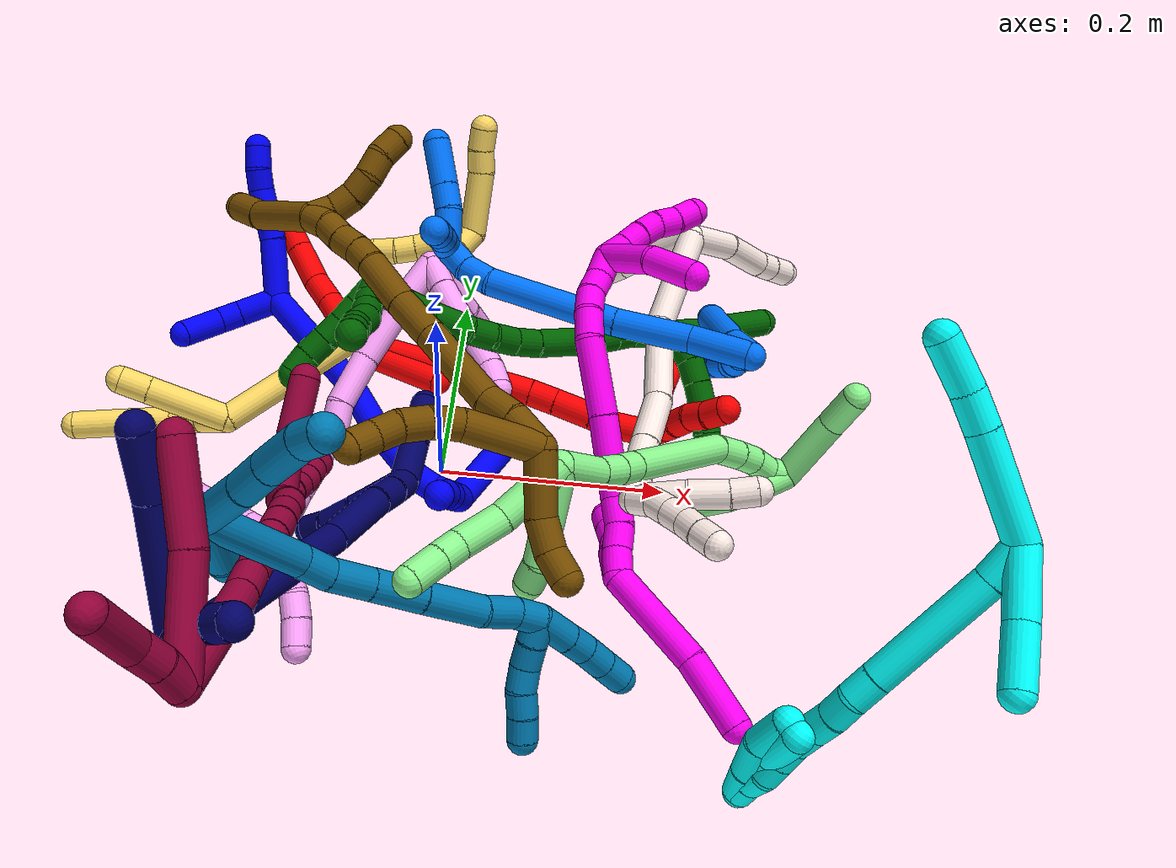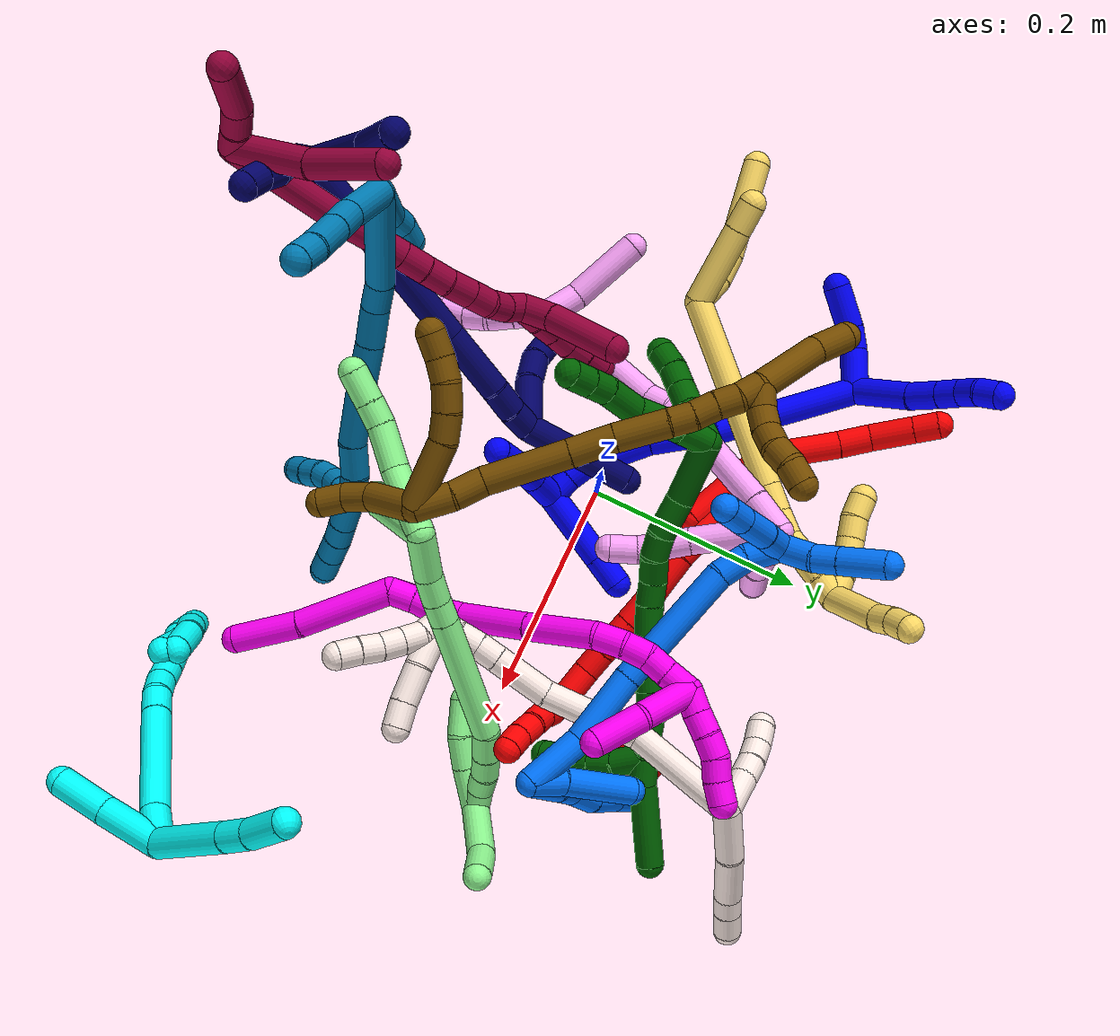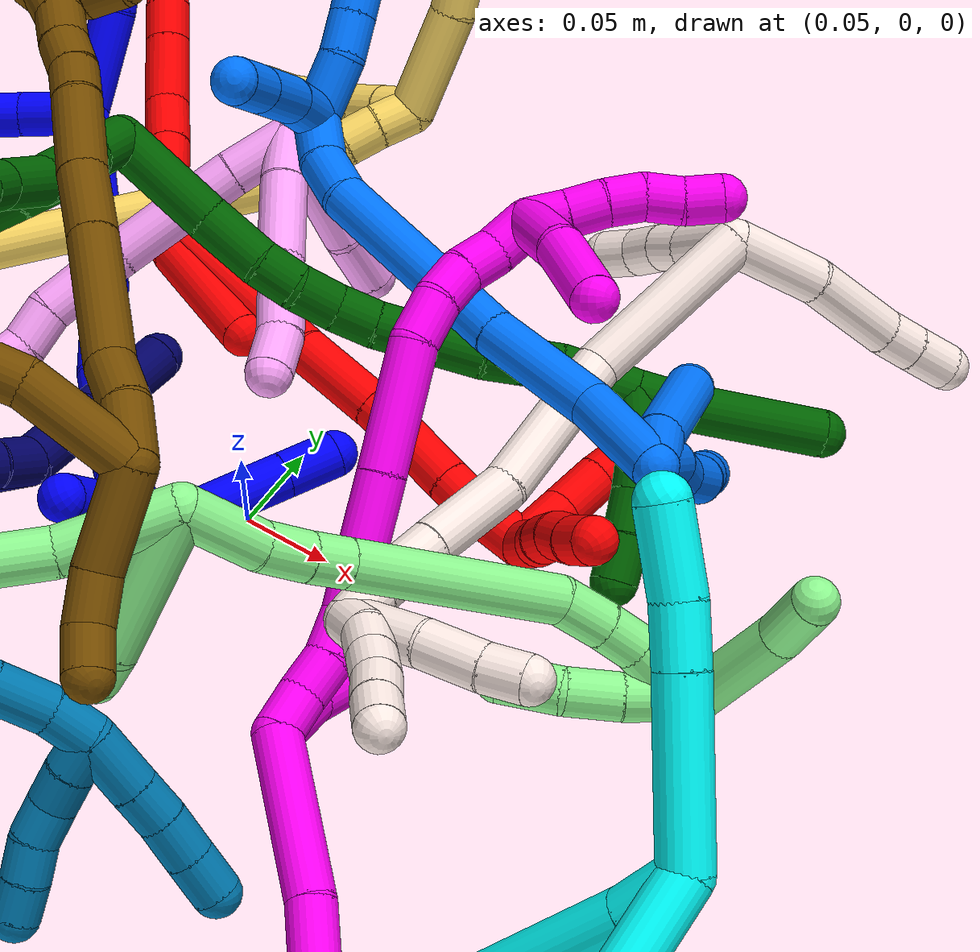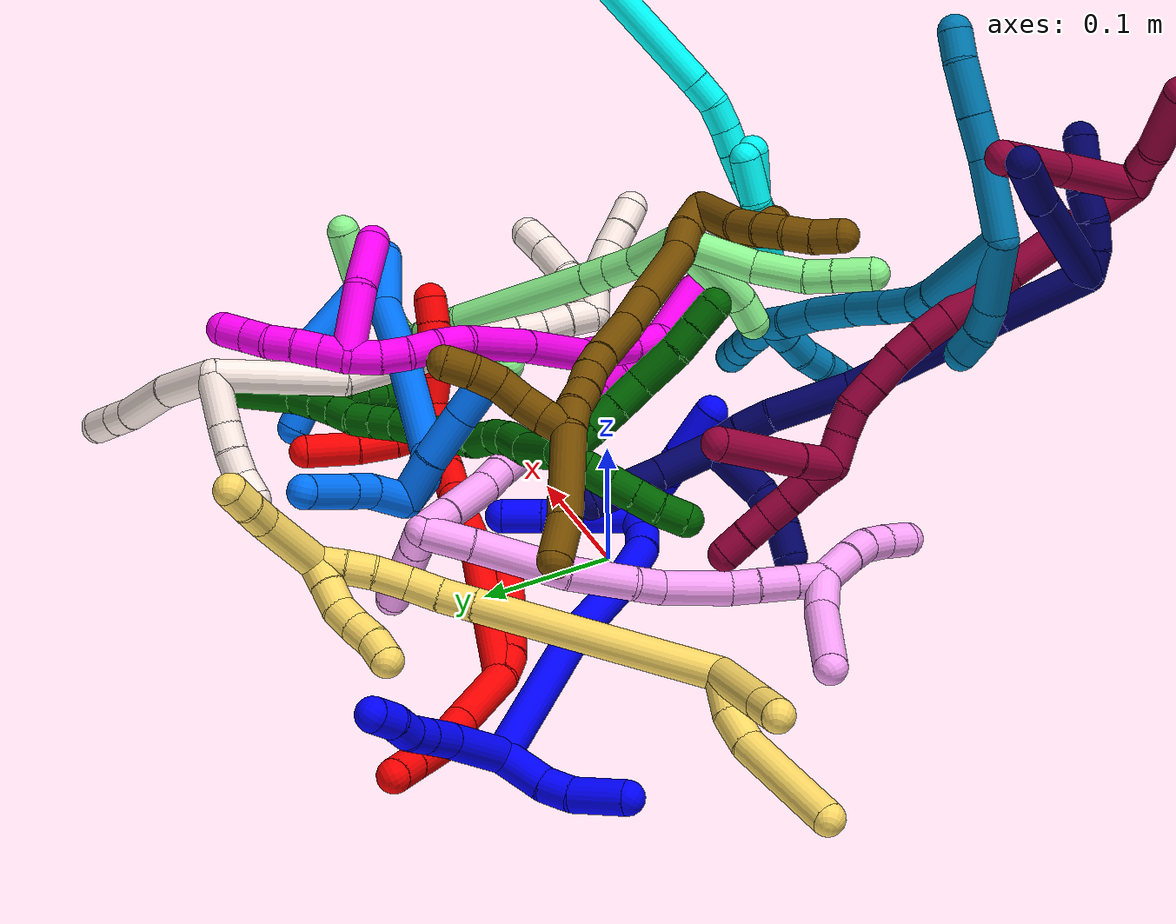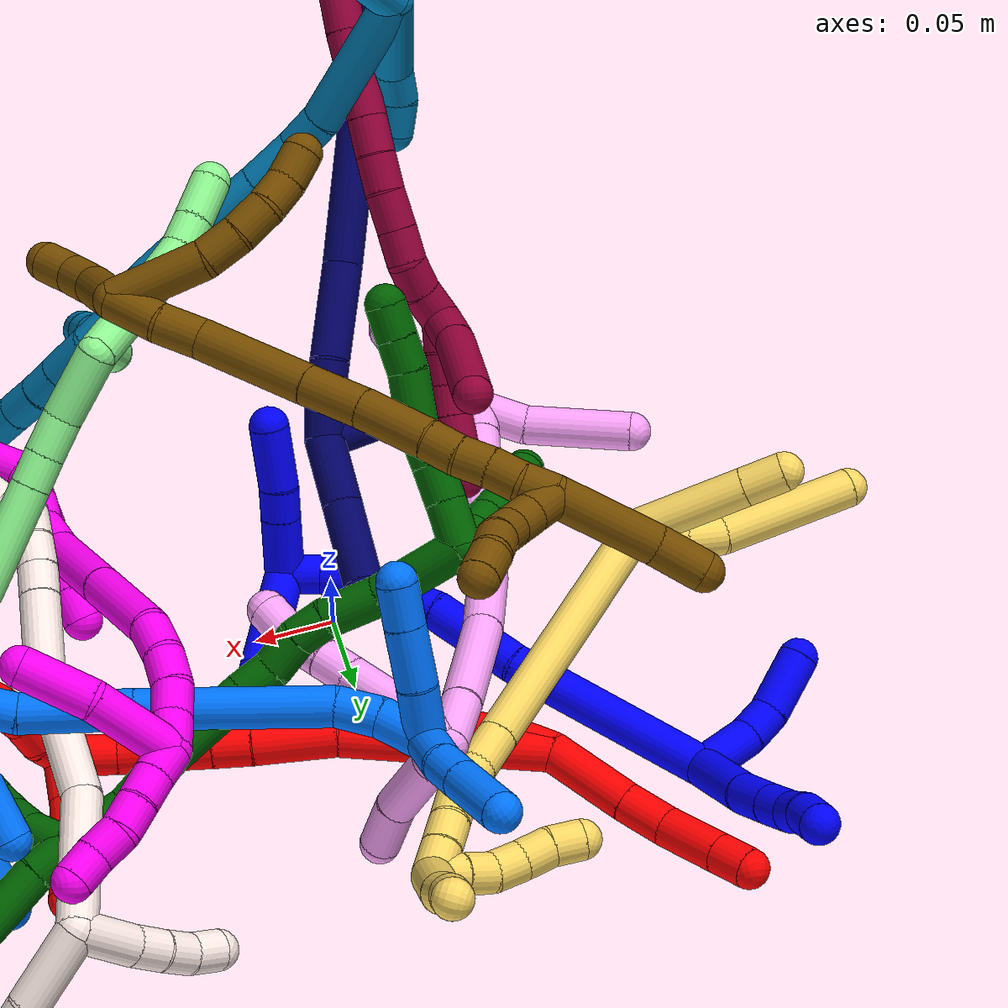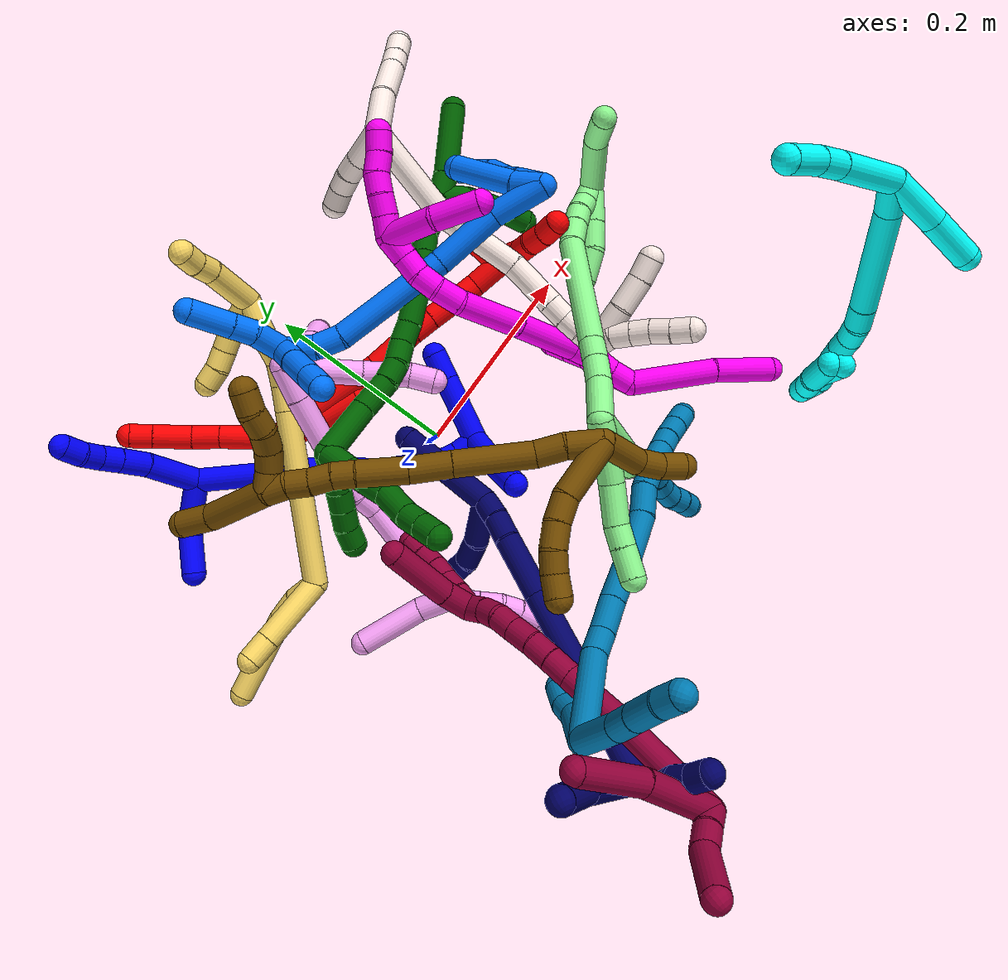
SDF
<sdf version="1.7">
 <world name="default">
  <plugin name="TubeGeneratorPlugin" filename="libtube_generator_plugin.so"/>
  <model name="photoneo_s_sensor">
   <static>1</static>
   <pose>0 0 2 1.57079 1.57079 3.14159</pose>
   <link name="link">
    <inertial><mass>0.1</mass></inertial>
    <sensor name="sensor" type="depth">
     <update_rate>30</update_rate>
     <camera>
      <horizontal_fov>1.22</horizontal_fov>
      <image><width>1920</width><height>1200</height><format>B8G8R8</format></image>
      <clip><near>0.1</near><far>4</far></clip>
      <depth_camera><output>points</output></depth_camera>
     </camera>
     <plugin name="camera_plugin" filename="libgazebo_ros_depth_camera.so">
      <baseline>0.2</baseline>
      <alwaysOn>1</alwaysOn>
      <updateRate>0.0</updateRate>
      <cameraName>camera_ir</cameraName>
      <imageTopicName>/camera/color/image_raw</imageTopicName>
      <cameraInfoTopicName>/camera/color/camera_info</cameraInfoTopicName>
      <depthImageTopicName>/camera/depth/image_raw</depthImageTopicName>
      <depthImageCameraInfoTopicName>/camera/depth/camera_info</depthImageCameraInfoTopicName>
      <pointCloudTopicName>/camera/depth/points</pointCloudTopicName>
      <frameName>fr_optical</frameName>
      <pointCloudCutoff>0.1</pointCloudCutoff>
      <pointCloudCutoffMax>2.0</pointCloudCutoffMax>
      <distortionK1>0</distortionK1>
      <distortionK2>0</distortionK2>
      <distortionK3>0</distortionK3>
      <distortionT1>0</distortionT1>
      <distortionT2>0</distortionT2>
      <CxPrime>0</CxPrime>
      <Cx>0</Cx>
      <Cy>0</Cy>
      <focalLength>0</focalLength>
      <hackBaseline>0</hackBaseline>
     </plugin>
    </sensor>
   </link>
  </model>
  <gravity>0 0 -9.8</gravity>
  <magnetic_field>6e-06 2.3e-05 -4.2e-05</magnetic_field>
  <atmosphere type="adiabatic"/>
  <physics name="default_physics" default="0" type="ode">
   <max_step_size>0.003</max_step_size>
   <real_time_factor>1</real_time_factor>
   <real_time_update_rate>1000</real_time_update_rate>
   <max_contacts>10000</max_contacts>
   <ode>
    <solver>
     <type>quick</type>
     <iters>100</iters>
     <sor>1.3</sor>
     <use_dynamic_moi_rescaling>0</use_dynamic_moi_rescaling>
    </solver>
    <constraints>
     <contact_max_correcting_vel>0</contact_max_correcting_vel>
     <contact_surface_layer>0.001</contact_surface_layer>
     <cfm>0</cfm>
     <erp>0.2</erp>
    </constraints>
   </ode>
  </physics>
  <scene><ambient>0.4 0.4 0.4 1</ambient><background>0.7 0.7 0.7 1</background><shadows>0</shadows></scene>
  <audio><device>default</device></audio>
  <spherical_coordinates>
   <surface_model>EARTH_WGS84</surface_model>
   <latitude_deg>0</latitude_deg>
   <longitude_deg>0</longitude_deg>
   <elevation>0</elevation>
   <heading_deg>0</heading_deg>
  </spherical_coordinates>
  <model name="bin">
   <static>1</static>
   <link name="bottom">
    <collision name="collision-bottom">
     <pose>0 0 -0.01 0 -0 0</pose>
     <geometry><box><size>0.8 0.6 0.02</size></box></geometry>
     <surface>
      <friction><ode><mu>100</mu><mu2>100</mu2></ode></friction>
      <contact><collide_bitmask>65535</collide_bitmask></contact>
     </surface>
    </collision>
   </link>
   <link name="west_wall">
    <collision name="collision-west_wall">
     <pose>-0.41 0 0.1 0 -0 0</pose>
     <geometry><box><size>0.02 0.6 0.2</size></box></geometry>
     <surface>
      <friction><ode><mu>100</mu><mu2>100</mu2></ode></friction>
      <contact><collide_bitmask>65535</collide_bitmask></contact>
     </surface>
    </collision>
   </link>
   <link name="east_wall">
    <collision name="collision-east_wall">
     <pose>0.41 0 0.1 0 -0 0</pose>
     <geometry><box><size>0.02 0.6 0.2</size></box></geometry>
     <surface>
      <friction><ode><mu>100</mu><mu2>100</mu2></ode></friction>
      <contact><collide_bitmask>65535</collide_bitmask></contact>
     </surface>
    </collision>
   </link>
   <link name="south_wall">
    <collision name="collision-south_wall">
     <pose>0 -0.31 0.1 0 -0 0</pose>
     <geometry><box><size>0.8 0.02 0.2</size></box></geometry>
     <surface>
      <friction><ode><mu>100</mu><mu2>100</mu2></ode></friction>
      <contact><collide_bitmask>65535</collide_bitmask></contact>
     </surface>
    </collision>
   </link>
   <link name="north_wall">
    <collision name="collision-north_wall">
     <pose>0 0.31 0.1 0 -0 0</pose>
     <geometry><box><size>0.8 0.02 0.2</size></box></geometry>
     <surface>
      <friction><ode><mu>100</mu><mu2>100</mu2></ode></friction>
      <contact><collide_bitmask>65535</collide_bitmask></contact>
     </surface>
    </collision>
   </link>
  </model>
  <model name="1">
   <static>0</static>
   <link name="1">
    <collision name="collision-cylinder-e_1_2_8">
     <pose>-0.020306 0.006701 0.0202 -0.320328 -0.761918 0.129228</pose>
     <geometry><cylinder><radius>0.0125</radius><length>0.058831</length></cylinder></geometry>
     <surface>
      <friction><ode><mu>1.16</mu><mu2>1.16</mu2><slip1>0</slip1><slip2>0</slip2></ode></friction>
      <contact><ode><kp>1e+06</kp><kd>1</kd><max_vel>0</max_vel><min_depth>0.001</min_depth></ode></contact>
     </surface>
    </collision>
    <visual name="visual-cylinder-e_1_2_8">
     <pose>-0.020306 0.006701 0.0202 -0.320328 -0.761918 0.129228</pose>
     <geometry><cylinder><radius>0.0125</radius><length>0.058831</length></cylinder></geometry>
     <material><ambient>0 0 1 1</ambient></material>
    </visual>
    <collision name="collision-cylinder-e_2_8_9">
     <pose>-0.05178 0.0171 0.048631 -0.422159 -0.891213 0.203982</pose>
     <geometry><cylinder><radius>0.0125</radius><length>0.028716</length></cylinder></geometry>
     <surface>
      <friction><ode><mu>1.16</mu><mu2>1.16</mu2><slip1>0</slip1><slip2>0</slip2></ode></friction>
      <contact><ode><kp>1e+06</kp><kd>1</kd><max_vel>0</max_vel><min_depth>0.001</min_depth></ode></contact>
     </surface>
    </collision>
    <visual name="visual-cylinder-e_2_8_9">
     <pose>-0.05178 0.0171 0.048631 -0.422159 -0.891213 0.203982</pose>
     <geometry><cylinder><radius>0.0125</radius><length>0.028716</length></cylinder></geometry>
     <material><ambient>0 0 1 1</ambient></material>
    </visual>
    <collision name="collision-cylinder-e_3_9_10">
     <pose>-0.071297 0.023446 0.062744 -0.423229 -0.912993 0.210226</pose>
     <geometry><cylinder><radius>0.0125</radius><length>0.021101</length></cylinder></geometry>
     <surface>
      <friction><ode><mu>1.16</mu><mu2>1.16</mu2><slip1>0</slip1><slip2>0</slip2></ode></friction>
      <contact><ode><kp>1e+06</kp><kd>1</kd><max_vel>0</max_vel><min_depth>0.001</min_depth></ode></contact>
     </surface>
    </collision>
    <visual name="visual-cylinder-e_3_9_10">
     <pose>-0.071297 0.023446 0.062744 -0.423229 -0.912993 0.210226</pose>
     <geometry><cylinder><radius>0.0125</radius><length>0.021101</length></cylinder></geometry>
     <material><ambient>0 0 1 1</ambient></material>
    </visual>
    <collision name="collision-cylinder-e_4_10_11">
     <pose>-0.087548 0.026059 0.075244 0.005544 -0.873499 -0.002588</pose>
     <geometry><cylinder><radius>0.0125</radius><length>0.020616</length></cylinder></geometry>
     <surface>
      <friction><ode><mu>1.16</mu><mu2>1.16</mu2><slip1>0</slip1><slip2>0</slip2></ode></friction>
      <contact><ode><kp>1e+06</kp><kd>1</kd><max_vel>0</max_vel><min_depth>0.001</min_depth></ode></contact>
     </surface>
    </collision>
    <visual name="visual-cylinder-e_4_10_11">
     <pose>-0.087548 0.026059 0.075244 0.005544 -0.873499 -0.002588</pose>
     <geometry><cylinder><radius>0.0125</radius><length>0.020616</length></cylinder></geometry>
     <material><ambient>0 0 1 1</ambient></material>
    </visual>
    <collision name="collision-cylinder-e_5_11_6">
     <pose>-0.102204 0.02814 0.089439 -0.272527 -0.709464 0.101486</pose>
     <geometry><cylinder><radius>0.0125</radius><length>0.020736</length></cylinder></geometry>
     <surface>
      <friction><ode><mu>1.16</mu><mu2>1.16</mu2><slip1>0</slip1><slip2>0</slip2></ode></friction>
      <contact><ode><kp>1e+06</kp><kd>1</kd><max_vel>0</max_vel><min_depth>0.001</min_depth></ode></contact>
     </surface>
    </collision>
    <visual name="visual-cylinder-e_5_11_6">
     <pose>-0.102204 0.02814 0.089439 -0.272527 -0.709464 0.101486</pose>
     <geometry><cylinder><radius>0.0125</radius><length>0.020736</length></cylinder></geometry>
     <material><ambient>0 0 1 1</ambient></material>
    </visual>
    <collision name="collision-cylinder-e_1_2_12">
     <pose>-0.008676 0.001172 -0.016958 -3.07259 -0.471949 2.85647</pose>
     <geometry><cylinder><radius>0.0125</radius><length>0.038169</length></cylinder></geometry>
     <surface>
      <friction><ode><mu>1.16</mu><mu2>1.16</mu2><slip1>0</slip1><slip2>0</slip2></ode></friction>
      <contact><ode><kp>1e+06</kp><kd>1</kd><max_vel>0</max_vel><min_depth>0.001</min_depth></ode></contact>
     </surface>
    </collision>
    <visual name="visual-cylinder-e_1_2_12">
     <pose>-0.008676 0.001172 -0.016958 -3.07259 -0.471949 2.85647</pose>
     <geometry><cylinder><radius>0.0125</radius><length>0.038169</length></cylinder></geometry>
     <material><ambient>0 0 1 1</ambient></material>
    </visual>
    <collision name="collision-cylinder-e_2_12_13">
     <pose>-0.022678 0.000621 -0.043222 2.95851 -0.512502 -2.4676</pose>
     <geometry><cylinder><radius>0.0125</radius><length>0.02172</length></cylinder></geometry>
     <surface>
      <friction><ode><mu>1.16</mu><mu2>1.16</mu2><slip1>0</slip1><slip2>0</slip2></ode></friction>
      <contact><ode><kp>1e+06</kp><kd>1</kd><max_vel>0</max_vel><min_depth>0.001</min_depth></ode></contact>
     </surface>
    </collision>
    <visual name="visual-cylinder-e_2_12_13">
     <pose>-0.022678 0.000621 -0.043222 2.95851 -0.512502 -2.4676</pose>
     <geometry><cylinder><radius>0.0125</radius><length>0.02172</length></cylinder></geometry>
     <material><ambient>0 0 1 1</ambient></material>
    </visual>
    <collision name="collision-cylinder-e_3_13_5">
     <pose>-0.03786 -0.009482 -0.067854 2.64124 -0.513782 -1.59844</pose>
     <geometry><cylinder><radius>0.0125</radius><length>0.040111</length></cylinder></geometry>
     <surface>
      <friction><ode><mu>1.16</mu><mu2>1.16</mu2><slip1>0</slip1><slip2>0</slip2></ode></friction>
      <contact><ode><kp>1e+06</kp><kd>1</kd><max_vel>0</max_vel><min_depth>0.001</min_depth></ode></contact>
     </surface>
    </collision>
    <visual name="visual-cylinder-e_3_13_5">
     <pose>-0.03786 -0.009482 -0.067854 2.64124 -0.513782 -1.59844</pose>
     <geometry><cylinder><radius>0.0125</radius><length>0.040111</length></cylinder></geometry>
     <material><ambient>0 0 1 1</ambient></material>
    </visual>
    <collision name="collision-cylinder-e_1_2_14">
     <pose>0.041645 -0.052273 -0.003007 1.62826 0.671909 0.708508</pose>
     <geometry><cylinder><radius>0.0125</radius><length>0.133802</length></cylinder></geometry>
     <surface>
      <friction><ode><mu>1.16</mu><mu2>1.16</mu2><slip1>0</slip1><slip2>0</slip2></ode></friction>
      <contact><ode><kp>1e+06</kp><kd>1</kd><max_vel>0</max_vel><min_depth>0.001</min_depth></ode></contact>
     </surface>
    </collision>
    <visual name="visual-cylinder-e_1_2_14">
     <pose>0.041645 -0.052273 -0.003007 1.62826 0.671909 0.708508</pose>
     <geometry><cylinder><radius>0.0125</radius><length>0.133802</length></cylinder></geometry>
     <material><ambient>0 0 1 1</ambient></material>
    </visual>
    <collision name="collision-cylinder-e_2_14_15">
     <pose>0.101935 -0.128512 -0.011799 1.80764 0.647483 0.805731</pose>
     <geometry><cylinder><radius>0.0125</radius><length>0.061824</length></cylinder></geometry>
     <surface>
      <friction><ode><mu>1.16</mu><mu2>1.16</mu2><slip1>0</slip1><slip2>0</slip2></ode></friction>
      <contact><ode><kp>1e+06</kp><kd>1</kd><max_vel>0</max_vel><min_depth>0.001</min_depth></ode></contact>
     </surface>
    </collision>
    <visual name="visual-cylinder-e_2_14_15">
     <pose>0.101935 -0.128512 -0.011799 1.80764 0.647483 0.805731</pose>
     <geometry><cylinder><radius>0.0125</radius><length>0.061824</length></cylinder></geometry>
     <material><ambient>0 0 1 1</ambient></material>
    </visual>
    <collision name="collision-cylinder-e_3_15_16">
     <pose>0.143031 -0.172328 -0.020119 1.69781 0.842831 0.941895</pose>
     <geometry><cylinder><radius>0.0125</radius><length>0.060147</length></cylinder></geometry>
     <surface>
      <friction><ode><mu>1.16</mu><mu2>1.16</mu2><slip1>0</slip1><slip2>0</slip2></ode></friction>
      <contact><ode><kp>1e+06</kp><kd>1</kd><max_vel>0</max_vel><min_depth>0.001</min_depth></ode></contact>
     </surface>
    </collision>
    <visual name="visual-cylinder-e_3_15_16">
     <pose>0.143031 -0.172328 -0.020119 1.69781 0.842831 0.941895</pose>
     <geometry><cylinder><radius>0.0125</radius><length>0.060147</length></cylinder></geometry>
     <material><ambient>0 0 1 1</ambient></material>
    </visual>
    <collision name="collision-cylinder-e_4_16_17">
     <pose>0.173679 -0.198088 -0.02068 1.24862 0.920716 0.686255</pose>
     <geometry><cylinder><radius>0.0125</radius><length>0.020596</length></cylinder></geometry>
     <surface>
      <friction><ode><mu>1.16</mu><mu2>1.16</mu2><slip1>0</slip1><slip2>0</slip2></ode></friction>
      <contact><ode><kp>1e+06</kp><kd>1</kd><max_vel>0</max_vel><min_depth>0.001</min_depth></ode></contact>
     </surface>
    </collision>
    <visual name="visual-cylinder-e_4_16_17">
     <pose>0.173679 -0.198088 -0.02068 1.24862 0.920716 0.686255</pose>
     <geometry><cylinder><radius>0.0125</radius><length>0.020596</length></cylinder></geometry>
     <material><ambient>0 0 1 1</ambient></material>
    </visual>
    <collision name="collision-cylinder-e_5_17_1">
     <pose>0.190928 -0.210057 -0.014123 0.922966 0.87259 0.455689</pose>
     <geometry><cylinder><radius>0.0125</radius><length>0.023631</length></cylinder></geometry>
     <surface>
      <friction><ode><mu>1.16</mu><mu2>1.16</mu2><slip1>0</slip1><slip2>0</slip2></ode></friction>
      <contact><ode><kp>1e+06</kp><kd>1</kd><max_vel>0</max_vel><min_depth>0.001</min_depth></ode></contact>
     </surface>
    </collision>
    <visual name="visual-cylinder-e_5_17_1">
     <pose>0.190928 -0.210057 -0.014123 0.922966 0.87259 0.455689</pose>
     <geometry><cylinder><radius>0.0125</radius><length>0.023631</length></cylinder></geometry>
     <material><ambient>0 0 1 1</ambient></material>
    </visual>
    <collision name="collision-cylinder-e_1_1_18">
     <pose>0.189873 -0.233111 -0.009673 1.57866 -0.536366 -0.540396</pose>
     <geometry><cylinder><radius>0.0125</radius><length>0.039548</length></cylinder></geometry>
     <surface>
      <friction><ode><mu>1.16</mu><mu2>1.16</mu2><slip1>0</slip1><slip2>0</slip2></ode></friction>
      <contact><ode><kp>1e+06</kp><kd>1</kd><max_vel>0</max_vel><min_depth>0.001</min_depth></ode></contact>
     </surface>
    </collision>
    <visual name="visual-cylinder-e_1_1_18">
     <pose>0.189873 -0.233111 -0.009673 1.57866 -0.536366 -0.540396</pose>
     <geometry><cylinder><radius>0.0125</radius><length>0.039548</length></cylinder></geometry>
     <material><ambient>0 0 1 1</ambient></material>
    </visual>
    <collision name="collision-cylinder-e_2_18_19">
     <pose>0.174579 -0.258836 -0.009877 1.57884 -0.536327 -0.540453</pose>
     <geometry><cylinder><radius>0.0125</radius><length>0.020311</length></cylinder></geometry>
     <surface>
      <friction><ode><mu>1.16</mu><mu2>1.16</mu2><slip1>0</slip1><slip2>0</slip2></ode></friction>
      <contact><ode><kp>1e+06</kp><kd>1</kd><max_vel>0</max_vel><min_depth>0.001</min_depth></ode></contact>
     </surface>
    </collision>
    <visual name="visual-cylinder-e_2_18_19">
     <pose>0.174579 -0.258836 -0.009877 1.57884 -0.536327 -0.540453</pose>
     <geometry><cylinder><radius>0.0125</radius><length>0.020311</length></cylinder></geometry>
     <material><ambient>0 0 1 1</ambient></material>
    </visual>
    <collision name="collision-cylinder-e_3_19_4">
     <pose>0.161005 -0.285796 -0.010352 1.59301 -0.431008 -0.440385</pose>
     <geometry><cylinder><radius>0.0125</radius><length>0.040141</length></cylinder></geometry>
     <surface>
      <friction><ode><mu>1.16</mu><mu2>1.16</mu2><slip1>0</slip1><slip2>0</slip2></ode></friction>
      <contact><ode><kp>1e+06</kp><kd>1</kd><max_vel>0</max_vel><min_depth>0.001</min_depth></ode></contact>
     </surface>
    </collision>
    <visual name="visual-cylinder-e_3_19_4">
     <pose>0.161005 -0.285796 -0.010352 1.59301 -0.431008 -0.440385</pose>
     <geometry><cylinder><radius>0.0125</radius><length>0.040141</length></cylinder></geometry>
     <material><ambient>0 0 1 1</ambient></material>
    </visual>
    <collision name="collision-cylinder-e_1_1_20">
     <pose>0.205643 -0.197711 0.020054 -0.556328 0.161157 -0.046113</pose>
     <geometry><cylinder><radius>0.0125</radius><length>0.070612</length></cylinder></geometry>
     <surface>
      <friction><ode><mu>1.16</mu><mu2>1.16</mu2><slip1>0</slip1><slip2>0</slip2></ode></friction>
      <contact><ode><kp>1e+06</kp><kd>1</kd><max_vel>0</max_vel><min_depth>0.001</min_depth></ode></contact>
     </surface>
    </collision>
    <visual name="visual-cylinder-e_1_1_20">
     <pose>0.205643 -0.197711 0.020054 -0.556328 0.161157 -0.046113</pose>
     <geometry><cylinder><radius>0.0125</radius><length>0.070612</length></cylinder></geometry>
     <material><ambient>0 0 1 1</ambient></material>
    </visual>
    <collision name="collision-cylinder-e_2_20_3">
     <pose>0.213717 -0.171642 0.061949 -0.5573 0.164615 -0.047193</pose>
     <geometry><cylinder><radius>0.0125</radius><length>0.029388</length></cylinder></geometry>
     <surface>
      <friction><ode><mu>1.16</mu><mu2>1.16</mu2><slip1>0</slip1><slip2>0</slip2></ode></friction>
      <contact><ode><kp>1e+06</kp><kd>1</kd><max_vel>0</max_vel><min_depth>0.001</min_depth></ode></contact>
     </surface>
    </collision>
    <visual name="visual-cylinder-e_2_20_3">
     <pose>0.213717 -0.171642 0.061949 -0.5573 0.164615 -0.047193</pose>
     <geometry><cylinder><radius>0.0125</radius><length>0.029388</length></cylinder></geometry>
     <material><ambient>0 0 1 1</ambient></material>
    </visual>
    <collision name="collision-sphere-3">
     <pose>0.216125 -0.163976 0.074251 0 -0 0</pose>
     <geometry><sphere><radius>0.0125</radius></sphere></geometry>
     <surface>
      <friction><ode><mu>1.16</mu><mu2>1.16</mu2><slip1>0</slip1><slip2>0</slip2></ode></friction>
      <contact><ode><kp>1e+06</kp><kd>1</kd><max_vel>0</max_vel><min_depth>0.001</min_depth></ode></contact>
     </surface>
    </collision>
    <visual name="visual-sphere-3">
     <pose>0.216125 -0.163976 0.074251 0 -0 0</pose>
     <geometry><sphere><radius>0.0125</radius></sphere></geometry>
     <material><ambient>0 0 1 1</ambient></material>
    </visual>
    <collision name="collision-sphere-20">
     <pose>0.211309 -0.179309 0.049647 0 -0 0</pose>
     <geometry><sphere><radius>0.0125</radius></sphere></geometry>
     <surface>
      <friction><ode><mu>1.16</mu><mu2>1.16</mu2><slip1>0</slip1><slip2>0</slip2></ode></friction>
      <contact><ode><kp>1e+06</kp><kd>1</kd><max_vel>0</max_vel><min_depth>0.001</min_depth></ode></contact>
     </surface>
    </collision>
    <visual name="visual-sphere-20">
     <pose>0.211309 -0.179309 0.049647 0 -0 0</pose>
     <geometry><sphere><radius>0.0125</radius></sphere></geometry>
     <material><ambient>0 0 1 1</ambient></material>
    </visual>
    <collision name="collision-sphere-4">
     <pose>0.15262 -0.304027 -0.010757 0 -0 0</pose>
     <geometry><sphere><radius>0.0125</radius></sphere></geometry>
     <surface>
      <friction><ode><mu>1.16</mu><mu2>1.16</mu2><slip1>0</slip1><slip2>0</slip2></ode></friction>
      <contact><ode><kp>1e+06</kp><kd>1</kd><max_vel>0</max_vel><min_depth>0.001</min_depth></ode></contact>
     </surface>
    </collision>
    <visual name="visual-sphere-4">
     <pose>0.15262 -0.304027 -0.010757 0 -0 0</pose>
     <geometry><sphere><radius>0.0125</radius></sphere></geometry>
     <material><ambient>0 0 1 1</ambient></material>
    </visual>
    <collision name="collision-sphere-6">
     <pose>-0.108958 0.030257 0.097015 0 -0 0</pose>
     <geometry><sphere><radius>0.0125</radius></sphere></geometry>
     <surface>
      <friction><ode><mu>1.16</mu><mu2>1.16</mu2><slip1>0</slip1><slip2>0</slip2></ode></friction>
      <contact><ode><kp>1e+06</kp><kd>1</kd><max_vel>0</max_vel><min_depth>0.001</min_depth></ode></contact>
     </surface>
    </collision>
    <visual name="visual-sphere-6">
     <pose>-0.108958 0.030257 0.097015 0 -0 0</pose>
     <geometry><sphere><radius>0.0125</radius></sphere></geometry>
     <material><ambient>0 0 1 1</ambient></material>
    </visual>
    <collision name="collision-sphere-11">
     <pose>-0.09545 0.026022 0.081863 0 -0 0</pose>
     <geometry><sphere><radius>0.0125</radius></sphere></geometry>
     <surface>
      <friction><ode><mu>1.16</mu><mu2>1.16</mu2><slip1>0</slip1><slip2>0</slip2></ode></friction>
      <contact><ode><kp>1e+06</kp><kd>1</kd><max_vel>0</max_vel><min_depth>0.001</min_depth></ode></contact>
     </surface>
    </collision>
    <visual name="visual-sphere-11">
     <pose>-0.09545 0.026022 0.081863 0 -0 0</pose>
     <geometry><sphere><radius>0.0125</radius></sphere></geometry>
     <material><ambient>0 0 1 1</ambient></material>
    </visual>
    <collision name="collision-sphere-10">
     <pose>-0.079646 0.026096 0.068625 0 -0 0</pose>
     <geometry><sphere><radius>0.0125</radius></sphere></geometry>
     <surface>
      <friction><ode><mu>1.16</mu><mu2>1.16</mu2><slip1>0</slip1><slip2>0</slip2></ode></friction>
      <contact><ode><kp>1e+06</kp><kd>1</kd><max_vel>0</max_vel><min_depth>0.001</min_depth></ode></contact>
     </surface>
    </collision>
    <visual name="visual-sphere-10">
     <pose>-0.079646 0.026096 0.068625 0 -0 0</pose>
     <geometry><sphere><radius>0.0125</radius></sphere></geometry>
     <material><ambient>0 0 1 1</ambient></material>
    </visual>
    <collision name="collision-sphere-9">
     <pose>-0.062948 0.020797 0.056862 0 -0 0</pose>
     <geometry><sphere><radius>0.0125</radius></sphere></geometry>
     <surface>
      <friction><ode><mu>1.16</mu><mu2>1.16</mu2><slip1>0</slip1><slip2>0</slip2></ode></friction>
      <contact><ode><kp>1e+06</kp><kd>1</kd><max_vel>0</max_vel><min_depth>0.001</min_depth></ode></contact>
     </surface>
    </collision>
    <visual name="visual-sphere-9">
     <pose>-0.062948 0.020797 0.056862 0 -0 0</pose>
     <geometry><sphere><radius>0.0125</radius></sphere></geometry>
     <material><ambient>0 0 1 1</ambient></material>
    </visual>
    <collision name="collision-sphere-2">
     <geometry><sphere><radius>0.0125</radius></sphere></geometry>
     <surface>
      <friction><ode><mu>1.16</mu><mu2>1.16</mu2><slip1>0</slip1><slip2>0</slip2></ode></friction>
      <contact><ode><kp>1e+06</kp><kd>1</kd><max_vel>0</max_vel><min_depth>0.001</min_depth></ode></contact>
     </surface>
    </collision>
    <visual name="visual-sphere-2">
     <geometry><sphere><radius>0.0125</radius></sphere></geometry>
     <material><ambient>0 0 1 1</ambient></material>
    </visual>
    <collision name="collision-sphere-19">
     <pose>0.16939 -0.267566 -0.009947 0 -0 0</pose>
     <geometry><sphere><radius>0.0125</radius></sphere></geometry>
     <surface>
      <friction><ode><mu>1.16</mu><mu2>1.16</mu2><slip1>0</slip1><slip2>0</slip2></ode></friction>
      <contact><ode><kp>1e+06</kp><kd>1</kd><max_vel>0</max_vel><min_depth>0.001</min_depth></ode></contact>
     </surface>
    </collision>
    <visual name="visual-sphere-19">
     <pose>0.16939 -0.267566 -0.009947 0 -0 0</pose>
     <geometry><sphere><radius>0.0125</radius></sphere></geometry>
     <material><ambient>0 0 1 1</ambient></material>
    </visual>
    <collision name="collision-sphere-8">
     <pose>-0.040612 0.013403 0.0404 0 -0 0</pose>
     <geometry><sphere><radius>0.0125</radius></sphere></geometry>
     <surface>
      <friction><ode><mu>1.16</mu><mu2>1.16</mu2><slip1>0</slip1><slip2>0</slip2></ode></friction>
      <contact><ode><kp>1e+06</kp><kd>1</kd><max_vel>0</max_vel><min_depth>0.001</min_depth></ode></contact>
     </surface>
    </collision>
    <visual name="visual-sphere-8">
     <pose>-0.040612 0.013403 0.0404 0 -0 0</pose>
     <geometry><sphere><radius>0.0125</radius></sphere></geometry>
     <material><ambient>0 0 1 1</ambient></material>
    </visual>
    <collision name="collision-sphere-12">
     <pose>-0.017353 0.002344 -0.033916 0 -0 0</pose>
     <geometry><sphere><radius>0.0125</radius></sphere></geometry>
     <surface>
      <friction><ode><mu>1.16</mu><mu2>1.16</mu2><slip1>0</slip1><slip2>0</slip2></ode></friction>
      <contact><ode><kp>1e+06</kp><kd>1</kd><max_vel>0</max_vel><min_depth>0.001</min_depth></ode></contact>
     </surface>
    </collision>
    <visual name="visual-sphere-12">
     <pose>-0.017353 0.002344 -0.033916 0 -0 0</pose>
     <geometry><sphere><radius>0.0125</radius></sphere></geometry>
     <material><ambient>0 0 1 1</ambient></material>
    </visual>
    <collision name="collision-sphere-13">
     <pose>-0.028003 -0.001102 -0.052529 0 -0 0</pose>
     <geometry><sphere><radius>0.0125</radius></sphere></geometry>
     <surface>
      <friction><ode><mu>1.16</mu><mu2>1.16</mu2><slip1>0</slip1><slip2>0</slip2></ode></friction>
      <contact><ode><kp>1e+06</kp><kd>1</kd><max_vel>0</max_vel><min_depth>0.001</min_depth></ode></contact>
     </surface>
    </collision>
    <visual name="visual-sphere-13">
     <pose>-0.028003 -0.001102 -0.052529 0 -0 0</pose>
     <geometry><sphere><radius>0.0125</radius></sphere></geometry>
     <material><ambient>0 0 1 1</ambient></material>
    </visual>
    <collision name="collision-sphere-5">
     <pose>-0.047717 -0.017861 -0.083179 0 -0 0</pose>
     <geometry><sphere><radius>0.0125</radius></sphere></geometry>
     <surface>
      <friction><ode><mu>1.16</mu><mu2>1.16</mu2><slip1>0</slip1><slip2>0</slip2></ode></friction>
      <contact><ode><kp>1e+06</kp><kd>1</kd><max_vel>0</max_vel><min_depth>0.001</min_depth></ode></contact>
     </surface>
    </collision>
    <visual name="visual-sphere-5">
     <pose>-0.047717 -0.017861 -0.083179 0 -0 0</pose>
     <geometry><sphere><radius>0.0125</radius></sphere></geometry>
     <material><ambient>0 0 1 1</ambient></material>
    </visual>
    <collision name="collision-sphere-14">
     <pose>0.083289 -0.104545 -0.006014 0 -0 0</pose>
     <geometry><sphere><radius>0.0125</radius></sphere></geometry>
     <surface>
      <friction><ode><mu>1.16</mu><mu2>1.16</mu2><slip1>0</slip1><slip2>0</slip2></ode></friction>
      <contact><ode><kp>1e+06</kp><kd>1</kd><max_vel>0</max_vel><min_depth>0.001</min_depth></ode></contact>
     </surface>
    </collision>
    <visual name="visual-sphere-14">
     <pose>0.083289 -0.104545 -0.006014 0 -0 0</pose>
     <geometry><sphere><radius>0.0125</radius></sphere></geometry>
     <material><ambient>0 0 1 1</ambient></material>
    </visual>
    <collision name="collision-sphere-15">
     <pose>0.12058 -0.15248 -0.017584 0 -0 0</pose>
     <geometry><sphere><radius>0.0125</radius></sphere></geometry>
     <surface>
      <friction><ode><mu>1.16</mu><mu2>1.16</mu2><slip1>0</slip1><slip2>0</slip2></ode></friction>
      <contact><ode><kp>1e+06</kp><kd>1</kd><max_vel>0</max_vel><min_depth>0.001</min_depth></ode></contact>
     </surface>
    </collision>
    <visual name="visual-sphere-15">
     <pose>0.12058 -0.15248 -0.017584 0 -0 0</pose>
     <geometry><sphere><radius>0.0125</radius></sphere></geometry>
     <material><ambient>0 0 1 1</ambient></material>
    </visual>
    <collision name="collision-sphere-16">
     <pose>0.165482 -0.192176 -0.022654 0 -0 0</pose>
     <geometry><sphere><radius>0.0125</radius></sphere></geometry>
     <surface>
      <friction><ode><mu>1.16</mu><mu2>1.16</mu2><slip1>0</slip1><slip2>0</slip2></ode></friction>
      <contact><ode><kp>1e+06</kp><kd>1</kd><max_vel>0</max_vel><min_depth>0.001</min_depth></ode></contact>
     </surface>
    </collision>
    <visual name="visual-sphere-16">
     <pose>0.165482 -0.192176 -0.022654 0 -0 0</pose>
     <geometry><sphere><radius>0.0125</radius></sphere></geometry>
     <material><ambient>0 0 1 1</ambient></material>
    </visual>
    <collision name="collision-sphere-17">
     <pose>0.181877 -0.204001 -0.018707 0 -0 0</pose>
     <geometry><sphere><radius>0.0125</radius></sphere></geometry>
     <surface>
      <friction><ode><mu>1.16</mu><mu2>1.16</mu2><slip1>0</slip1><slip2>0</slip2></ode></friction>
      <contact><ode><kp>1e+06</kp><kd>1</kd><max_vel>0</max_vel><min_depth>0.001</min_depth></ode></contact>
     </surface>
    </collision>
    <visual name="visual-sphere-17">
     <pose>0.181877 -0.204001 -0.018707 0 -0 0</pose>
     <geometry><sphere><radius>0.0125</radius></sphere></geometry>
     <material><ambient>0 0 1 1</ambient></material>
    </visual>
    <collision name="collision-sphere-1">
     <pose>0.199978 -0.216114 -0.009539 0 -0 0</pose>
     <geometry><sphere><radius>0.0125</radius></sphere></geometry>
     <surface>
      <friction><ode><mu>1.16</mu><mu2>1.16</mu2><slip1>0</slip1><slip2>0</slip2></ode></friction>
      <contact><ode><kp>1e+06</kp><kd>1</kd><max_vel>0</max_vel><min_depth>0.001</min_depth></ode></contact>
     </surface>
    </collision>
    <visual name="visual-sphere-1">
     <pose>0.199978 -0.216114 -0.009539 0 -0 0</pose>
     <geometry><sphere><radius>0.0125</radius></sphere></geometry>
     <material><ambient>0 0 1 1</ambient></material>
    </visual>
    <collision name="collision-sphere-18">
     <pose>0.179769 -0.250107 -0.009807 0 -0 0</pose>
     <geometry><sphere><radius>0.0125</radius></sphere></geometry>
     <surface>
      <friction><ode><mu>1.16</mu><mu2>1.16</mu2><slip1>0</slip1><slip2>0</slip2></ode></friction>
      <contact><ode><kp>1e+06</kp><kd>1</kd><max_vel>0</max_vel><min_depth>0.001</min_depth></ode></contact>
     </surface>
    </collision>
    <visual name="visual-sphere-18">
     <pose>0.179769 -0.250107 -0.009807 0 -0 0</pose>
     <geometry><sphere><radius>0.0125</radius></sphere></geometry>
     <material><ambient>0 0 1 1</ambient></material>
    </visual>
    <inertial>
     <pose>0.075244 -0.10283 0.002858 0 -0 0</pose>
     <mass>0.75</mass>
     <inertia><ixx>0.000322</ixx><ixy>0</ixy><ixz>0</ixz><iyy>0.000261</iyy><iyz>0</iyz><izz>6e-05</izz></inertia>
    </inertial>
   </link>
   <pose>-0.184961 0.174907 0.018035 -0.888223 0.701619 -0.284534</pose>
  </model>
  <model name="2">
   <static>0</static>
   <link name="2">
    <collision name="collision-cylinder-e_1_2_8">
     <pose>-0.018884 0.00276 0.021016 -0.130586 -0.727777 0.049794</pose>
     <geometry><cylinder><radius>0.0125</radius><length>0.056776</length></cylinder></geometry>
     <surface>
      <friction><ode><mu>1.16</mu><mu2>1.16</mu2><slip1>0</slip1><slip2>0</slip2></ode></friction>
      <contact><ode><kp>1e+06</kp><kd>1</kd><max_vel>0</max_vel><min_depth>0.001</min_depth></ode></contact>
     </surface>
    </collision>
    <visual name="visual-cylinder-e_1_2_8">
     <pose>-0.018884 0.00276 0.021016 -0.130586 -0.727777 0.049794</pose>
     <geometry><cylinder><radius>0.0125</radius><length>0.056776</length></cylinder></geometry>
     <material><ambient>1 0 0 1</ambient></material>
    </visual>
    <collision name="collision-cylinder-e_2_8_9">
     <pose>-0.048267 0.007197 0.052517 -0.158539 -0.779675 0.065252</pose>
     <geometry><cylinder><radius>0.0125</radius><length>0.029865</length></cylinder></geometry>
     <surface>
      <friction><ode><mu>1.16</mu><mu2>1.16</mu2><slip1>0</slip1><slip2>0</slip2></ode></friction>
      <contact><ode><kp>1e+06</kp><kd>1</kd><max_vel>0</max_vel><min_depth>0.001</min_depth></ode></contact>
     </surface>
    </collision>
    <visual name="visual-cylinder-e_2_8_9">
     <pose>-0.048267 0.007197 0.052517 -0.158539 -0.779675 0.065252</pose>
     <geometry><cylinder><radius>0.0125</radius><length>0.029865</length></cylinder></geometry>
     <material><ambient>1 0 0 1</ambient></material>
    </visual>
    <collision name="collision-cylinder-e_3_9_10">
     <pose>-0.074239 0.006162 0.075916 0.206974 -0.864779 -0.095791</pose>
     <geometry><cylinder><radius>0.0125</radius><length>0.040671</length></cylinder></geometry>
     <surface>
      <friction><ode><mu>1.16</mu><mu2>1.16</mu2><slip1>0</slip1><slip2>0</slip2></ode></friction>
      <contact><ode><kp>1e+06</kp><kd>1</kd><max_vel>0</max_vel><min_depth>0.001</min_depth></ode></contact>
     </surface>
    </collision>
    <visual name="visual-cylinder-e_3_9_10">
     <pose>-0.074239 0.006162 0.075916 0.206974 -0.864779 -0.095791</pose>
     <geometry><cylinder><radius>0.0125</radius><length>0.040671</length></cylinder></geometry>
     <material><ambient>1 0 0 1</ambient></material>
    </visual>
    <collision name="collision-cylinder-e_4_10_6">
     <pose>-0.098358 0.001971 0.096023 0.202808 -0.86649 -0.094063</pose>
     <geometry><cylinder><radius>0.0125</radius><length>0.022687</length></cylinder></geometry>
     <surface>
      <friction><ode><mu>1.16</mu><mu2>1.16</mu2><slip1>0</slip1><slip2>0</slip2></ode></friction>
      <contact><ode><kp>1e+06</kp><kd>1</kd><max_vel>0</max_vel><min_depth>0.001</min_depth></ode></contact>
     </surface>
    </collision>
    <visual name="visual-cylinder-e_4_10_6">
     <pose>-0.098358 0.001971 0.096023 0.202808 -0.86649 -0.094063</pose>
     <geometry><cylinder><radius>0.0125</radius><length>0.022687</length></cylinder></geometry>
     <material><ambient>1 0 0 1</ambient></material>
    </visual>
    <collision name="collision-cylinder-e_1_2_11">
     <pose>0.009328 -0.002888 -0.006593 2.72868 0.913598 2.3359</pose>
     <geometry><cylinder><radius>0.0125</radius><length>0.023563</length></cylinder></geometry>
     <surface>
      <friction><ode><mu>1.16</mu><mu2>1.16</mu2><slip1>0</slip1><slip2>0</slip2></ode></friction>
      <contact><ode><kp>1e+06</kp><kd>1</kd><max_vel>0</max_vel><min_depth>0.001</min_depth></ode></contact>
     </surface>
    </collision>
    <visual name="visual-cylinder-e_1_2_11">
     <pose>0.009328 -0.002888 -0.006593 2.72868 0.913598 2.3359</pose>
     <geometry><cylinder><radius>0.0125</radius><length>0.023563</length></cylinder></geometry>
     <material><ambient>1 0 0 1</ambient></material>
    </visual>
    <collision name="collision-cylinder-e_2_11_5">
     <pose>0.049796 -0.023275 -0.026775 2.23115 0.952407 1.62307</pose>
     <geometry><cylinder><radius>0.0125</radius><length>0.076437</length></cylinder></geometry>
     <surface>
      <friction><ode><mu>1.16</mu><mu2>1.16</mu2><slip1>0</slip1><slip2>0</slip2></ode></friction>
      <contact><ode><kp>1e+06</kp><kd>1</kd><max_vel>0</max_vel><min_depth>0.001</min_depth></ode></contact>
     </surface>
    </collision>
    <visual name="visual-cylinder-e_2_11_5">
     <pose>0.049796 -0.023275 -0.026775 2.23115 0.952407 1.62307</pose>
     <geometry><cylinder><radius>0.0125</radius><length>0.076437</length></cylinder></geometry>
     <material><ambient>1 0 0 1</ambient></material>
    </visual>
    <collision name="collision-cylinder-e_1_2_12">
     <pose>0.054885 -0.032294 -0.016743 2.04911 0.985502 1.44689</pose>
     <geometry><cylinder><radius>0.0125</radius><length>0.131691</length></cylinder></geometry>
     <surface>
      <friction><ode><mu>1.16</mu><mu2>1.16</mu2><slip1>0</slip1><slip2>0</slip2></ode></friction>
      <contact><ode><kp>1e+06</kp><kd>1</kd><max_vel>0</max_vel><min_depth>0.001</min_depth></ode></contact>
     </surface>
    </collision>
    <visual name="visual-cylinder-e_1_2_12">
     <pose>0.054885 -0.032294 -0.016743 2.04911 0.985502 1.44689</pose>
     <geometry><cylinder><radius>0.0125</radius><length>0.131691</length></cylinder></geometry>
     <material><ambient>1 0 0 1</ambient></material>
    </visual>
    <collision name="collision-cylinder-e_2_12_13">
     <pose>0.133276 -0.075034 -0.036201 1.82505 1.14029 1.38447</pose>
     <geometry><cylinder><radius>0.0125</radius><length>0.05173</length></cylinder></geometry>
     <surface>
      <friction><ode><mu>1.16</mu><mu2>1.16</mu2><slip1>0</slip1><slip2>0</slip2></ode></friction>
      <contact><ode><kp>1e+06</kp><kd>1</kd><max_vel>0</max_vel><min_depth>0.001</min_depth></ode></contact>
     </surface>
    </collision>
    <visual name="visual-cylinder-e_2_12_13">
     <pose>0.133276 -0.075034 -0.036201 1.82505 1.14029 1.38447</pose>
     <geometry><cylinder><radius>0.0125</radius><length>0.05173</length></cylinder></geometry>
     <material><ambient>1 0 0 1</ambient></material>
    </visual>
    <collision name="collision-cylinder-e_3_13_14">
     <pose>0.16799 -0.089754 -0.040778 1.98169 1.1768 1.58916</pose>
     <geometry><cylinder><radius>0.0125</radius><length>0.024279</length></cylinder></geometry>
     <surface>
      <friction><ode><mu>1.16</mu><mu2>1.16</mu2><slip1>0</slip1><slip2>0</slip2></ode></friction>
      <contact><ode><kp>1e+06</kp><kd>1</kd><max_vel>0</max_vel><min_depth>0.001</min_depth></ode></contact>
     </surface>
    </collision>
    <visual name="visual-cylinder-e_3_13_14">
     <pose>0.16799 -0.089754 -0.040778 1.98169 1.1768 1.58916</pose>
     <geometry><cylinder><radius>0.0125</radius><length>0.024279</length></cylinder></geometry>
     <material><ambient>1 0 0 1</ambient></material>
    </visual>
    <collision name="collision-cylinder-e_4_14_15">
     <pose>0.195934 -0.100169 -0.045661 2.02798 1.18244 1.64621</pose>
     <geometry><cylinder><radius>0.0125</radius><length>0.036161</length></cylinder></geometry>
     <surface>
      <friction><ode><mu>1.16</mu><mu2>1.16</mu2><slip1>0</slip1><slip2>0</slip2></ode></friction>
      <contact><ode><kp>1e+06</kp><kd>1</kd><max_vel>0</max_vel><min_depth>0.001</min_depth></ode></contact>
     </surface>
    </collision>
    <visual name="visual-cylinder-e_4_14_15">
     <pose>0.195934 -0.100169 -0.045661 2.02798 1.18244 1.64621</pose>
     <geometry><cylinder><radius>0.0125</radius><length>0.036161</length></cylinder></geometry>
     <material><ambient>1 0 0 1</ambient></material>
    </visual>
    <collision name="collision-cylinder-e_5_15_16">
     <pose>0.223148 -0.110002 -0.050304 1.98471 1.20374 1.62146</pose>
     <geometry><cylinder><radius>0.0125</radius><length>0.022455</length></cylinder></geometry>
     <surface>
      <friction><ode><mu>1.16</mu><mu2>1.16</mu2><slip1>0</slip1><slip2>0</slip2></ode></friction>
      <contact><ode><kp>1e+06</kp><kd>1</kd><max_vel>0</max_vel><min_depth>0.001</min_depth></ode></contact>
     </surface>
    </collision>
    <visual name="visual-cylinder-e_5_15_16">
     <pose>0.223148 -0.110002 -0.050304 1.98471 1.20374 1.62146</pose>
     <geometry><cylinder><radius>0.0125</radius><length>0.022455</length></cylinder></geometry>
     <material><ambient>1 0 0 1</ambient></material>
    </visual>
    <collision name="collision-cylinder-e_6_16_1">
     <pose>0.247827 -0.122259 -0.05486 1.90085 1.00302 1.30906</pose>
     <geometry><cylinder><radius>0.0125</radius><length>0.033684</length></cylinder></geometry>
     <surface>
      <friction><ode><mu>1.16</mu><mu2>1.16</mu2><slip1>0</slip1><slip2>0</slip2></ode></friction>
      <contact><ode><kp>1e+06</kp><kd>1</kd><max_vel>0</max_vel><min_depth>0.001</min_depth></ode></contact>
     </surface>
    </collision>
    <visual name="visual-cylinder-e_6_16_1">
     <pose>0.247827 -0.122259 -0.05486 1.90085 1.00302 1.30906</pose>
     <geometry><cylinder><radius>0.0125</radius><length>0.033684</length></cylinder></geometry>
     <material><ambient>1 0 0 1</ambient></material>
    </visual>
    <collision name="collision-cylinder-e_1_1_17">
     <pose>0.261109 -0.133536 -0.042021 0.170088 -0.057248 -0.004882</pose>
     <geometry><cylinder><radius>0.0125</radius><length>0.032063</length></cylinder></geometry>
     <surface>
      <friction><ode><mu>1.16</mu><mu2>1.16</mu2><slip1>0</slip1><slip2>0</slip2></ode></friction>
      <contact><ode><kp>1e+06</kp><kd>1</kd><max_vel>0</max_vel><min_depth>0.001</min_depth></ode></contact>
     </surface>
    </collision>
    <visual name="visual-cylinder-e_1_1_17">
     <pose>0.261109 -0.133536 -0.042021 0.170088 -0.057248 -0.004882</pose>
     <geometry><cylinder><radius>0.0125</radius><length>0.032063</length></cylinder></geometry>
     <material><ambient>1 0 0 1</ambient></material>
    </visual>
    <collision name="collision-cylinder-e_2_17_18">
     <pose>0.259291 -0.140498 -0.012809 0.306539 -0.063838 -0.009865</pose>
     <geometry><cylinder><radius>0.0125</radius><length>0.028245</length></cylinder></geometry>
     <surface>
      <friction><ode><mu>1.16</mu><mu2>1.16</mu2><slip1>0</slip1><slip2>0</slip2></ode></friction>
      <contact><ode><kp>1e+06</kp><kd>1</kd><max_vel>0</max_vel><min_depth>0.001</min_depth></ode></contact>
     </surface>
    </collision>
    <visual name="visual-cylinder-e_2_17_18">
     <pose>0.259291 -0.140498 -0.012809 0.306539 -0.063838 -0.009865</pose>
     <geometry><cylinder><radius>0.0125</radius><length>0.028245</length></cylinder></geometry>
     <material><ambient>1 0 0 1</ambient></material>
    </visual>
    <collision name="collision-cylinder-e_3_18_4">
     <pose>0.258758 -0.152534 0.01888 0.403055 0.018541 0.003788</pose>
     <geometry><cylinder><radius>0.0125</radius><length>0.039692</length></cylinder></geometry>
     <surface>
      <friction><ode><mu>1.16</mu><mu2>1.16</mu2><slip1>0</slip1><slip2>0</slip2></ode></friction>
      <contact><ode><kp>1e+06</kp><kd>1</kd><max_vel>0</max_vel><min_depth>0.001</min_depth></ode></contact>
     </surface>
    </collision>
    <visual name="visual-cylinder-e_3_18_4">
     <pose>0.258758 -0.152534 0.01888 0.403055 0.018541 0.003788</pose>
     <geometry><cylinder><radius>0.0125</radius><length>0.039692</length></cylinder></geometry>
     <material><ambient>1 0 0 1</ambient></material>
    </visual>
    <collision name="collision-cylinder-e_1_1_19">
     <pose>0.264151 -0.139897 -0.061429 1.95186 0.214137 0.315061</pose>
     <geometry><cylinder><radius>0.0125</radius><length>0.02</length></cylinder></geometry>
     <surface>
      <friction><ode><mu>1.16</mu><mu2>1.16</mu2><slip1>0</slip1><slip2>0</slip2></ode></friction>
      <contact><ode><kp>1e+06</kp><kd>1</kd><max_vel>0</max_vel><min_depth>0.001</min_depth></ode></contact>
     </surface>
    </collision>
    <visual name="visual-cylinder-e_1_1_19">
     <pose>0.264151 -0.139897 -0.061429 1.95186 0.214137 0.315061</pose>
     <geometry><cylinder><radius>0.0125</radius><length>0.02</length></cylinder></geometry>
     <material><ambient>1 0 0 1</ambient></material>
    </visual>
    <collision name="collision-cylinder-e_2_19_20">
     <pose>0.266509 -0.157258 -0.070651 2.16387 0.023292 0.043784</pose>
     <geometry><cylinder><radius>0.0125</radius><length>0.02</length></cylinder></geometry>
     <surface>
      <friction><ode><mu>1.16</mu><mu2>1.16</mu2><slip1>0</slip1><slip2>0</slip2></ode></friction>
      <contact><ode><kp>1e+06</kp><kd>1</kd><max_vel>0</max_vel><min_depth>0.001</min_depth></ode></contact>
     </surface>
    </collision>
    <visual name="visual-cylinder-e_2_19_20">
     <pose>0.266509 -0.157258 -0.070651 2.16387 0.023292 0.043784</pose>
     <geometry><cylinder><radius>0.0125</radius><length>0.02</length></cylinder></geometry>
     <material><ambient>1 0 0 1</ambient></material>
    </visual>
    <collision name="collision-cylinder-e_3_20_21">
     <pose>0.267968 -0.174587 -0.080338 1.99659 0.122932 0.190401</pose>
     <geometry><cylinder><radius>0.0125</radius><length>0.02</length></cylinder></geometry>
     <surface>
      <friction><ode><mu>1.16</mu><mu2>1.16</mu2><slip1>0</slip1><slip2>0</slip2></ode></friction>
      <contact><ode><kp>1e+06</kp><kd>1</kd><max_vel>0</max_vel><min_depth>0.001</min_depth></ode></contact>
     </surface>
    </collision>
    <visual name="visual-cylinder-e_3_20_21">
     <pose>0.267968 -0.174587 -0.080338 1.99659 0.122932 0.190401</pose>
     <geometry><cylinder><radius>0.0125</radius><length>0.02</length></cylinder></geometry>
     <material><ambient>1 0 0 1</ambient></material>
    </visual>
    <collision name="collision-cylinder-e_4_21_22">
     <pose>0.272561 -0.191908 -0.088916 2.06656 0.343337 0.566117</pose>
     <geometry><cylinder><radius>0.0125</radius><length>0.02</length></cylinder></geometry>
     <surface>
      <friction><ode><mu>1.16</mu><mu2>1.16</mu2><slip1>0</slip1><slip2>0</slip2></ode></friction>
      <contact><ode><kp>1e+06</kp><kd>1</kd><max_vel>0</max_vel><min_depth>0.001</min_depth></ode></contact>
     </surface>
    </collision>
    <visual name="visual-cylinder-e_4_21_22">
     <pose>0.272561 -0.191908 -0.088916 2.06656 0.343337 0.566117</pose>
     <geometry><cylinder><radius>0.0125</radius><length>0.02</length></cylinder></geometry>
     <material><ambient>1 0 0 1</ambient></material>
    </visual>
    <collision name="collision-cylinder-e_5_22_3">
     <pose>0.278946 -0.209127 -0.096714 1.92637 0.306716 0.437463</pose>
     <geometry><cylinder><radius>0.0125</radius><length>0.02</length></cylinder></geometry>
     <surface>
      <friction><ode><mu>1.16</mu><mu2>1.16</mu2><slip1>0</slip1><slip2>0</slip2></ode></friction>
      <contact><ode><kp>1e+06</kp><kd>1</kd><max_vel>0</max_vel><min_depth>0.001</min_depth></ode></contact>
     </surface>
    </collision>
    <visual name="visual-cylinder-e_5_22_3">
     <pose>0.278946 -0.209127 -0.096714 1.92637 0.306716 0.437463</pose>
     <geometry><cylinder><radius>0.0125</radius><length>0.02</length></cylinder></geometry>
     <material><ambient>1 0 0 1</ambient></material>
    </visual>
    <collision name="collision-sphere-3">
     <pose>0.281966 -0.218064 -0.100033 0 -0 0</pose>
     <geometry><sphere><radius>0.0125</radius></sphere></geometry>
     <surface>
      <friction><ode><mu>1.16</mu><mu2>1.16</mu2><slip1>0</slip1><slip2>0</slip2></ode></friction>
      <contact><ode><kp>1e+06</kp><kd>1</kd><max_vel>0</max_vel><min_depth>0.001</min_depth></ode></contact>
     </surface>
    </collision>
    <visual name="visual-sphere-3">
     <pose>0.281966 -0.218064 -0.100033 0 -0 0</pose>
     <geometry><sphere><radius>0.0125</radius></sphere></geometry>
     <material><ambient>1 0 0 1</ambient></material>
    </visual>
    <collision name="collision-sphere-22">
     <pose>0.275927 -0.20019 -0.093396 0 -0 0</pose>
     <geometry><sphere><radius>0.0125</radius></sphere></geometry>
     <surface>
      <friction><ode><mu>1.16</mu><mu2>1.16</mu2><slip1>0</slip1><slip2>0</slip2></ode></friction>
      <contact><ode><kp>1e+06</kp><kd>1</kd><max_vel>0</max_vel><min_depth>0.001</min_depth></ode></contact>
     </surface>
    </collision>
    <visual name="visual-sphere-22">
     <pose>0.275927 -0.20019 -0.093396 0 -0 0</pose>
     <geometry><sphere><radius>0.0125</radius></sphere></geometry>
     <material><ambient>1 0 0 1</ambient></material>
    </visual>
    <collision name="collision-sphere-21">
     <pose>0.269195 -0.183625 -0.084437 0 -0 0</pose>
     <geometry><sphere><radius>0.0125</radius></sphere></geometry>
     <surface>
      <friction><ode><mu>1.16</mu><mu2>1.16</mu2><slip1>0</slip1><slip2>0</slip2></ode></friction>
      <contact><ode><kp>1e+06</kp><kd>1</kd><max_vel>0</max_vel><min_depth>0.001</min_depth></ode></contact>
     </surface>
    </collision>
    <visual name="visual-sphere-21">
     <pose>0.269195 -0.183625 -0.084437 0 -0 0</pose>
     <geometry><sphere><radius>0.0125</radius></sphere></geometry>
     <material><ambient>1 0 0 1</ambient></material>
    </visual>
    <collision name="collision-sphere-20">
     <pose>0.266742 -0.165548 -0.076238 0 -0 0</pose>
     <geometry><sphere><radius>0.0125</radius></sphere></geometry>
     <surface>
      <friction><ode><mu>1.16</mu><mu2>1.16</mu2><slip1>0</slip1><slip2>0</slip2></ode></friction>
      <contact><ode><kp>1e+06</kp><kd>1</kd><max_vel>0</max_vel><min_depth>0.001</min_depth></ode></contact>
     </surface>
    </collision>
    <visual name="visual-sphere-20">
     <pose>0.266742 -0.165548 -0.076238 0 -0 0</pose>
     <geometry><sphere><radius>0.0125</radius></sphere></geometry>
     <material><ambient>1 0 0 1</ambient></material>
    </visual>
    <collision name="collision-sphere-19">
     <pose>0.266276 -0.148968 -0.065063 0 -0 0</pose>
     <geometry><sphere><radius>0.0125</radius></sphere></geometry>
     <surface>
      <friction><ode><mu>1.16</mu><mu2>1.16</mu2><slip1>0</slip1><slip2>0</slip2></ode></friction>
      <contact><ode><kp>1e+06</kp><kd>1</kd><max_vel>0</max_vel><min_depth>0.001</min_depth></ode></contact>
     </surface>
    </collision>
    <visual name="visual-sphere-19">
     <pose>0.266276 -0.148968 -0.065063 0 -0 0</pose>
     <geometry><sphere><radius>0.0125</radius></sphere></geometry>
     <material><ambient>1 0 0 1</ambient></material>
    </visual>
    <collision name="collision-sphere-11">
     <pose>0.018655 -0.005776 -0.013185 0 -0 0</pose>
     <geometry><sphere><radius>0.0125</radius></sphere></geometry>
     <surface>
      <friction><ode><mu>1.16</mu><mu2>1.16</mu2><slip1>0</slip1><slip2>0</slip2></ode></friction>
      <contact><ode><kp>1e+06</kp><kd>1</kd><max_vel>0</max_vel><min_depth>0.001</min_depth></ode></contact>
     </surface>
    </collision>
    <visual name="visual-sphere-11">
     <pose>0.018655 -0.005776 -0.013185 0 -0 0</pose>
     <geometry><sphere><radius>0.0125</radius></sphere></geometry>
     <material><ambient>1 0 0 1</ambient></material>
    </visual>
    <collision name="collision-sphere-6">
     <pose>-0.107003 0.000492 0.103217 0 -0 0</pose>
     <geometry><sphere><radius>0.0125</radius></sphere></geometry>
     <surface>
      <friction><ode><mu>1.16</mu><mu2>1.16</mu2><slip1>0</slip1><slip2>0</slip2></ode></friction>
      <contact><ode><kp>1e+06</kp><kd>1</kd><max_vel>0</max_vel><min_depth>0.001</min_depth></ode></contact>
     </surface>
    </collision>
    <visual name="visual-sphere-6">
     <pose>-0.107003 0.000492 0.103217 0 -0 0</pose>
     <geometry><sphere><radius>0.0125</radius></sphere></geometry>
     <material><ambient>1 0 0 1</ambient></material>
    </visual>
    <collision name="collision-sphere-10">
     <pose>-0.089714 0.00345 0.088828 0 -0 0</pose>
     <geometry><sphere><radius>0.0125</radius></sphere></geometry>
     <surface>
      <friction><ode><mu>1.16</mu><mu2>1.16</mu2><slip1>0</slip1><slip2>0</slip2></ode></friction>
      <contact><ode><kp>1e+06</kp><kd>1</kd><max_vel>0</max_vel><min_depth>0.001</min_depth></ode></contact>
     </surface>
    </collision>
    <visual name="visual-sphere-10">
     <pose>-0.089714 0.00345 0.088828 0 -0 0</pose>
     <geometry><sphere><radius>0.0125</radius></sphere></geometry>
     <material><ambient>1 0 0 1</ambient></material>
    </visual>
    <collision name="collision-sphere-9">
     <pose>-0.058765 0.008873 0.063004 0 -0 0</pose>
     <geometry><sphere><radius>0.0125</radius></sphere></geometry>
     <surface>
      <friction><ode><mu>1.16</mu><mu2>1.16</mu2><slip1>0</slip1><slip2>0</slip2></ode></friction>
      <contact><ode><kp>1e+06</kp><kd>1</kd><max_vel>0</max_vel><min_depth>0.001</min_depth></ode></contact>
     </surface>
    </collision>
    <visual name="visual-sphere-9">
     <pose>-0.058765 0.008873 0.063004 0 -0 0</pose>
     <geometry><sphere><radius>0.0125</radius></sphere></geometry>
     <material><ambient>1 0 0 1</ambient></material>
    </visual>
    <collision name="collision-sphere-2">
     <geometry><sphere><radius>0.0125</radius></sphere></geometry>
     <surface>
      <friction><ode><mu>1.16</mu><mu2>1.16</mu2><slip1>0</slip1><slip2>0</slip2></ode></friction>
      <contact><ode><kp>1e+06</kp><kd>1</kd><max_vel>0</max_vel><min_depth>0.001</min_depth></ode></contact>
     </surface>
    </collision>
    <visual name="visual-sphere-2">
     <geometry><sphere><radius>0.0125</radius></sphere></geometry>
     <material><ambient>1 0 0 1</ambient></material>
    </visual>
    <collision name="collision-sphere-8">
     <pose>-0.037768 0.00552 0.042031 0 -0 0</pose>
     <geometry><sphere><radius>0.0125</radius></sphere></geometry>
     <surface>
      <friction><ode><mu>1.16</mu><mu2>1.16</mu2><slip1>0</slip1><slip2>0</slip2></ode></friction>
      <contact><ode><kp>1e+06</kp><kd>1</kd><max_vel>0</max_vel><min_depth>0.001</min_depth></ode></contact>
     </surface>
    </collision>
    <visual name="visual-sphere-8">
     <pose>-0.037768 0.00552 0.042031 0 -0 0</pose>
     <geometry><sphere><radius>0.0125</radius></sphere></geometry>
     <material><ambient>1 0 0 1</ambient></material>
    </visual>
    <collision name="collision-sphere-5">
     <pose>0.080937 -0.040773 -0.040366 0 -0 0</pose>
     <geometry><sphere><radius>0.0125</radius></sphere></geometry>
     <surface>
      <friction><ode><mu>1.16</mu><mu2>1.16</mu2><slip1>0</slip1><slip2>0</slip2></ode></friction>
      <contact><ode><kp>1e+06</kp><kd>1</kd><max_vel>0</max_vel><min_depth>0.001</min_depth></ode></contact>
     </surface>
    </collision>
    <visual name="visual-sphere-5">
     <pose>0.080937 -0.040773 -0.040366 0 -0 0</pose>
     <geometry><sphere><radius>0.0125</radius></sphere></geometry>
     <material><ambient>1 0 0 1</ambient></material>
    </visual>
    <collision name="collision-sphere-12">
     <pose>0.109771 -0.064587 -0.033486 0 -0 0</pose>
     <geometry><sphere><radius>0.0125</radius></sphere></geometry>
     <surface>
      <friction><ode><mu>1.16</mu><mu2>1.16</mu2><slip1>0</slip1><slip2>0</slip2></ode></friction>
      <contact><ode><kp>1e+06</kp><kd>1</kd><max_vel>0</max_vel><min_depth>0.001</min_depth></ode></contact>
     </surface>
    </collision>
    <visual name="visual-sphere-12">
     <pose>0.109771 -0.064587 -0.033486 0 -0 0</pose>
     <geometry><sphere><radius>0.0125</radius></sphere></geometry>
     <material><ambient>1 0 0 1</ambient></material>
    </visual>
    <collision name="collision-sphere-13">
     <pose>0.156781 -0.085482 -0.038916 0 -0 0</pose>
     <geometry><sphere><radius>0.0125</radius></sphere></geometry>
     <surface>
      <friction><ode><mu>1.16</mu><mu2>1.16</mu2><slip1>0</slip1><slip2>0</slip2></ode></friction>
      <contact><ode><kp>1e+06</kp><kd>1</kd><max_vel>0</max_vel><min_depth>0.001</min_depth></ode></contact>
     </surface>
    </collision>
    <visual name="visual-sphere-13">
     <pose>0.156781 -0.085482 -0.038916 0 -0 0</pose>
     <geometry><sphere><radius>0.0125</radius></sphere></geometry>
     <material><ambient>1 0 0 1</ambient></material>
    </visual>
    <collision name="collision-sphere-14">
     <pose>0.1792 -0.094026 -0.042639 0 -0 0</pose>
     <geometry><sphere><radius>0.0125</radius></sphere></geometry>
     <surface>
      <friction><ode><mu>1.16</mu><mu2>1.16</mu2><slip1>0</slip1><slip2>0</slip2></ode></friction>
      <contact><ode><kp>1e+06</kp><kd>1</kd><max_vel>0</max_vel><min_depth>0.001</min_depth></ode></contact>
     </surface>
    </collision>
    <visual name="visual-sphere-14">
     <pose>0.1792 -0.094026 -0.042639 0 -0 0</pose>
     <geometry><sphere><radius>0.0125</radius></sphere></geometry>
     <material><ambient>1 0 0 1</ambient></material>
    </visual>
    <collision name="collision-sphere-15">
     <pose>0.212668 -0.106313 -0.048683 0 -0 0</pose>
     <geometry><sphere><radius>0.0125</radius></sphere></geometry>
     <surface>
      <friction><ode><mu>1.16</mu><mu2>1.16</mu2><slip1>0</slip1><slip2>0</slip2></ode></friction>
      <contact><ode><kp>1e+06</kp><kd>1</kd><max_vel>0</max_vel><min_depth>0.001</min_depth></ode></contact>
     </surface>
    </collision>
    <visual name="visual-sphere-15">
     <pose>0.212668 -0.106313 -0.048683 0 -0 0</pose>
     <geometry><sphere><radius>0.0125</radius></sphere></geometry>
     <material><ambient>1 0 0 1</ambient></material>
    </visual>
    <collision name="collision-sphere-16">
     <pose>0.233627 -0.113691 -0.051924 0 -0 0</pose>
     <geometry><sphere><radius>0.0125</radius></sphere></geometry>
     <surface>
      <friction><ode><mu>1.16</mu><mu2>1.16</mu2><slip1>0</slip1><slip2>0</slip2></ode></friction>
      <contact><ode><kp>1e+06</kp><kd>1</kd><max_vel>0</max_vel><min_depth>0.001</min_depth></ode></contact>
     </surface>
    </collision>
    <visual name="visual-sphere-16">
     <pose>0.233627 -0.113691 -0.051924 0 -0 0</pose>
     <geometry><sphere><radius>0.0125</radius></sphere></geometry>
     <material><ambient>1 0 0 1</ambient></material>
    </visual>
    <collision name="collision-sphere-1">
     <pose>0.262026 -0.130827 -0.057795 0 -0 0</pose>
     <geometry><sphere><radius>0.0125</radius></sphere></geometry>
     <surface>
      <friction><ode><mu>1.16</mu><mu2>1.16</mu2><slip1>0</slip1><slip2>0</slip2></ode></friction>
      <contact><ode><kp>1e+06</kp><kd>1</kd><max_vel>0</max_vel><min_depth>0.001</min_depth></ode></contact>
     </surface>
    </collision>
    <visual name="visual-sphere-1">
     <pose>0.262026 -0.130827 -0.057795 0 -0 0</pose>
     <geometry><sphere><radius>0.0125</radius></sphere></geometry>
     <material><ambient>1 0 0 1</ambient></material>
    </visual>
    <collision name="collision-sphere-18">
     <pose>0.25839 -0.144751 0.000627 0 -0 0</pose>
     <geometry><sphere><radius>0.0125</radius></sphere></geometry>
     <surface>
      <friction><ode><mu>1.16</mu><mu2>1.16</mu2><slip1>0</slip1><slip2>0</slip2></ode></friction>
      <contact><ode><kp>1e+06</kp><kd>1</kd><max_vel>0</max_vel><min_depth>0.001</min_depth></ode></contact>
     </surface>
    </collision>
    <visual name="visual-sphere-18">
     <pose>0.25839 -0.144751 0.000627 0 -0 0</pose>
     <geometry><sphere><radius>0.0125</radius></sphere></geometry>
     <material><ambient>1 0 0 1</ambient></material>
    </visual>
    <collision name="collision-sphere-17">
     <pose>0.260192 -0.136245 -0.026246 0 -0 0</pose>
     <geometry><sphere><radius>0.0125</radius></sphere></geometry>
     <surface>
      <friction><ode><mu>1.16</mu><mu2>1.16</mu2><slip1>0</slip1><slip2>0</slip2></ode></friction>
      <contact><ode><kp>1e+06</kp><kd>1</kd><max_vel>0</max_vel><min_depth>0.001</min_depth></ode></contact>
     </surface>
    </collision>
    <visual name="visual-sphere-17">
     <pose>0.260192 -0.136245 -0.026246 0 -0 0</pose>
     <geometry><sphere><radius>0.0125</radius></sphere></geometry>
     <material><ambient>1 0 0 1</ambient></material>
    </visual>
    <collision name="collision-sphere-4">
     <pose>0.259126 -0.160317 0.037132 0 -0 0</pose>
     <geometry><sphere><radius>0.0125</radius></sphere></geometry>
     <surface>
      <friction><ode><mu>1.16</mu><mu2>1.16</mu2><slip1>0</slip1><slip2>0</slip2></ode></friction>
      <contact><ode><kp>1e+06</kp><kd>1</kd><max_vel>0</max_vel><min_depth>0.001</min_depth></ode></contact>
     </surface>
    </collision>
    <visual name="visual-sphere-4">
     <pose>0.259126 -0.160317 0.037132 0 -0 0</pose>
     <geometry><sphere><radius>0.0125</radius></sphere></geometry>
     <material><ambient>1 0 0 1</ambient></material>
    </visual>
    <inertial>
     <pose>0.117167 -0.071285 -0.017055 0 -0 0</pose>
     <mass>0.75</mass>
     <inertia>
      <ixx>0.000219</ixx>
      <ixy>0</ixy>
      <ixz>0</ixz>
      <iyy>0.000346</iyy>
      <iyz>0</iyz>
      <izz>-6.2e-05</izz>
     </inertia>
    </inertial>
   </link>
   <pose>-0.101788 0.135677 0.012403 -1.89887 0.486365 -0.236066</pose>
  </model>
  <model name="3">
   <static>0</static>
   <link name="3">
    <collision name="collision-cylinder-e_1_2_8">
     <pose>-0.028236 0.018258 -0.023532 -2.48173 -0.758704 1.72221</pose>
     <geometry><cylinder><radius>0.0125</radius><length>0.082083</length></cylinder></geometry>
     <surface>
      <friction><ode><mu>1.16</mu><mu2>1.16</mu2><slip1>0</slip1><slip2>0</slip2></ode></friction>
      <contact><ode><kp>1e+06</kp><kd>1</kd><max_vel>0</max_vel><min_depth>0.001</min_depth></ode></contact>
     </surface>
    </collision>
    <visual name="visual-cylinder-e_1_2_8">
     <pose>-0.028236 0.018258 -0.023532 -2.48173 -0.758704 1.72221</pose>
     <geometry><cylinder><radius>0.0125</radius><length>0.082083</length></cylinder></geometry>
     <material><ambient>0.003922 1 0.996078 1</ambient></material>
    </visual>
    <collision name="collision-cylinder-e_2_8_9">
     <pose>-0.06642 0.042738 -0.054688 -2.45709 -0.79095 1.72865</pose>
     <geometry><cylinder><radius>0.0125</radius><length>0.027986</length></cylinder></geometry>
     <surface>
      <friction><ode><mu>1.16</mu><mu2>1.16</mu2><slip1>0</slip1><slip2>0</slip2></ode></friction>
      <contact><ode><kp>1e+06</kp><kd>1</kd><max_vel>0</max_vel><min_depth>0.001</min_depth></ode></contact>
     </surface>
    </collision>
    <visual name="visual-cylinder-e_2_8_9">
     <pose>-0.06642 0.042738 -0.054688 -2.45709 -0.79095 1.72865</pose>
     <geometry><cylinder><radius>0.0125</radius><length>0.027986</length></cylinder></geometry>
     <material><ambient>0.003922 1 0.996078 1</ambient></material>
    </visual>
    <collision name="collision-cylinder-e_3_9_6">
     <pose>-0.090193 0.059903 -0.07168 -2.27885 -0.764727 1.4362</pose>
     <geometry><cylinder><radius>0.0125</radius><length>0.039932</length></cylinder></geometry>
     <surface>
      <friction><ode><mu>1.16</mu><mu2>1.16</mu2><slip1>0</slip1><slip2>0</slip2></ode></friction>
      <contact><ode><kp>1e+06</kp><kd>1</kd><max_vel>0</max_vel><min_depth>0.001</min_depth></ode></contact>
     </surface>
    </collision>
    <visual name="visual-cylinder-e_3_9_6">
     <pose>-0.090193 0.059903 -0.07168 -2.27885 -0.764727 1.4362</pose>
     <geometry><cylinder><radius>0.0125</radius><length>0.039932</length></cylinder></geometry>
     <material><ambient>0.003922 1 0.996078 1</ambient></material>
    </visual>
    <collision name="collision-cylinder-e_1_2_10">
     <pose>0.016113 0.004681 0.020933 -0.220008 0.644282 -0.073696</pose>
     <geometry><cylinder><radius>0.0125</radius><length>0.053656</length></cylinder></geometry>
     <surface>
      <friction><ode><mu>1.16</mu><mu2>1.16</mu2><slip1>0</slip1><slip2>0</slip2></ode></friction>
      <contact><ode><kp>1e+06</kp><kd>1</kd><max_vel>0</max_vel><min_depth>0.001</min_depth></ode></contact>
     </surface>
    </collision>
    <visual name="visual-cylinder-e_1_2_10">
     <pose>0.016113 0.004681 0.020933 -0.220008 0.644282 -0.073696</pose>
     <geometry><cylinder><radius>0.0125</radius><length>0.053656</length></cylinder></geometry>
     <material><ambient>0.003922 1 0.996078 1</ambient></material>
    </visual>
    <collision name="collision-cylinder-e_2_10_5">
     <pose>0.04564 0.014624 0.060013 -0.282213 0.617318 -0.090524</pose>
     <geometry><cylinder><radius>0.0125</radius><length>0.046344</length></cylinder></geometry>
     <surface>
      <friction><ode><mu>1.16</mu><mu2>1.16</mu2><slip1>0</slip1><slip2>0</slip2></ode></friction>
      <contact><ode><kp>1e+06</kp><kd>1</kd><max_vel>0</max_vel><min_depth>0.001</min_depth></ode></contact>
     </surface>
    </collision>
    <visual name="visual-cylinder-e_2_10_5">
     <pose>0.04564 0.014624 0.060013 -0.282213 0.617318 -0.090524</pose>
     <geometry><cylinder><radius>0.0125</radius><length>0.046344</length></cylinder></geometry>
     <material><ambient>0.003922 1 0.996078 1</ambient></material>
    </visual>
    <collision name="collision-cylinder-e_1_2_11">
     <pose>-0.001507 -0.001035 0.016079 0.064309 -0.093279 -0.003003</pose>
     <geometry><cylinder><radius>0.0125</radius><length>0.032365</length></cylinder></geometry>
     <surface>
      <friction><ode><mu>1.16</mu><mu2>1.16</mu2><slip1>0</slip1><slip2>0</slip2></ode></friction>
      <contact><ode><kp>1e+06</kp><kd>1</kd><max_vel>0</max_vel><min_depth>0.001</min_depth></ode></contact>
     </surface>
    </collision>
    <visual name="visual-cylinder-e_1_2_11">
     <pose>-0.001507 -0.001035 0.016079 0.064309 -0.093279 -0.003003</pose>
     <geometry><cylinder><radius>0.0125</radius><length>0.032365</length></cylinder></geometry>
     <material><ambient>0.003922 1 0.996078 1</ambient></material>
    </visual>
    <collision name="collision-cylinder-e_2_11_12">
     <pose>-0.013027 -0.002832 0.081973 0.015274 -0.198324 -0.00152</pose>
     <geometry><cylinder><radius>0.0125</radius><length>0.101636</length></cylinder></geometry>
     <surface>
      <friction><ode><mu>1.16</mu><mu2>1.16</mu2><slip1>0</slip1><slip2>0</slip2></ode></friction>
      <contact><ode><kp>1e+06</kp><kd>1</kd><max_vel>0</max_vel><min_depth>0.001</min_depth></ode></contact>
     </surface>
    </collision>
    <visual name="visual-cylinder-e_2_11_12">
     <pose>-0.013027 -0.002832 0.081973 0.015274 -0.198324 -0.00152</pose>
     <geometry><cylinder><radius>0.0125</radius><length>0.101636</length></cylinder></geometry>
     <material><ambient>0.003922 1 0.996078 1</ambient></material>
    </visual>
    <collision name="collision-cylinder-e_3_12_13">
     <pose>-0.025359 -0.004298 0.142858 0.063608 -0.206125 -0.006581</pose>
     <geometry><cylinder><radius>0.0125</radius><length>0.022662</length></cylinder></geometry>
     <surface>
      <friction><ode><mu>1.16</mu><mu2>1.16</mu2><slip1>0</slip1><slip2>0</slip2></ode></friction>
      <contact><ode><kp>1e+06</kp><kd>1</kd><max_vel>0</max_vel><min_depth>0.001</min_depth></ode></contact>
     </surface>
    </collision>
    <visual name="visual-cylinder-e_3_12_13">
     <pose>-0.025359 -0.004298 0.142858 0.063608 -0.206125 -0.006581</pose>
     <geometry><cylinder><radius>0.0125</radius><length>0.022662</length></cylinder></geometry>
     <material><ambient>0.003922 1 0.996078 1</ambient></material>
    </visual>
    <collision name="collision-cylinder-e_4_13_14">
     <pose>-0.030198 -0.008802 0.164017 0.360077 -0.229607 -0.041969</pose>
     <geometry><cylinder><radius>0.0125</radius><length>0.022144</length></cylinder></geometry>
     <surface>
      <friction><ode><mu>1.16</mu><mu2>1.16</mu2><slip1>0</slip1><slip2>0</slip2></ode></friction>
      <contact><ode><kp>1e+06</kp><kd>1</kd><max_vel>0</max_vel><min_depth>0.001</min_depth></ode></contact>
     </surface>
    </collision>
    <visual name="visual-cylinder-e_4_13_14">
     <pose>-0.030198 -0.008802 0.164017 0.360077 -0.229607 -0.041969</pose>
     <geometry><cylinder><radius>0.0125</radius><length>0.022144</length></cylinder></geometry>
     <material><ambient>0.003922 1 0.996078 1</ambient></material>
    </visual>
    <collision name="collision-cylinder-e_5_14_15">
     <pose>-0.036236 -0.016234 0.182922 0.390937 -0.353519 -0.070704</pose>
     <geometry><cylinder><radius>0.0125</radius><length>0.020326</length></cylinder></geometry>
     <surface>
      <friction><ode><mu>1.16</mu><mu2>1.16</mu2><slip1>0</slip1><slip2>0</slip2></ode></friction>
      <contact><ode><kp>1e+06</kp><kd>1</kd><max_vel>0</max_vel><min_depth>0.001</min_depth></ode></contact>
     </surface>
    </collision>
    <visual name="visual-cylinder-e_5_14_15">
     <pose>-0.036236 -0.016234 0.182922 0.390937 -0.353519 -0.070704</pose>
     <geometry><cylinder><radius>0.0125</radius><length>0.020326</length></cylinder></geometry>
     <material><ambient>0.003922 1 0.996078 1</ambient></material>
    </visual>
    <collision name="collision-cylinder-e_6_15_16">
     <pose>-0.04311 -0.023158 0.200924 0.34407 -0.331226 -0.058067</pose>
     <geometry><cylinder><radius>0.0125</radius><length>0.020638</length></cylinder></geometry>
     <surface>
      <friction><ode><mu>1.16</mu><mu2>1.16</mu2><slip1>0</slip1><slip2>0</slip2></ode></friction>
      <contact><ode><kp>1e+06</kp><kd>1</kd><max_vel>0</max_vel><min_depth>0.001</min_depth></ode></contact>
     </surface>
    </collision>
    <visual name="visual-cylinder-e_6_15_16">
     <pose>-0.04311 -0.023158 0.200924 0.34407 -0.331226 -0.058067</pose>
     <geometry><cylinder><radius>0.0125</radius><length>0.020638</length></cylinder></geometry>
     <material><ambient>0.003922 1 0.996078 1</ambient></material>
    </visual>
    <collision name="collision-cylinder-e_7_16_17">
     <pose>-0.048394 -0.030271 0.21926 0.395553 -0.192025 -0.038595</pose>
     <geometry><cylinder><radius>0.0125</radius><length>0.020203</length></cylinder></geometry>
     <surface>
      <friction><ode><mu>1.16</mu><mu2>1.16</mu2><slip1>0</slip1><slip2>0</slip2></ode></friction>
      <contact><ode><kp>1e+06</kp><kd>1</kd><max_vel>0</max_vel><min_depth>0.001</min_depth></ode></contact>
     </surface>
    </collision>
    <visual name="visual-cylinder-e_7_16_17">
     <pose>-0.048394 -0.030271 0.21926 0.395553 -0.192025 -0.038595</pose>
     <geometry><cylinder><radius>0.0125</radius><length>0.020203</length></cylinder></geometry>
     <material><ambient>0.003922 1 0.996078 1</ambient></material>
    </visual>
    <collision name="collision-cylinder-e_8_17_18">
     <pose>-0.052375 -0.0379 0.237435 0.399378 -0.206586 -0.041953</pose>
     <geometry><cylinder><radius>0.0125</radius><length>0.020017</length></cylinder></geometry>
     <surface>
      <friction><ode><mu>1.16</mu><mu2>1.16</mu2><slip1>0</slip1><slip2>0</slip2></ode></friction>
      <contact><ode><kp>1e+06</kp><kd>1</kd><max_vel>0</max_vel><min_depth>0.001</min_depth></ode></contact>
     </surface>
    </collision>
    <visual name="visual-cylinder-e_8_17_18">
     <pose>-0.052375 -0.0379 0.237435 0.399378 -0.206586 -0.041953</pose>
     <geometry><cylinder><radius>0.0125</radius><length>0.020017</length></cylinder></geometry>
     <material><ambient>0.003922 1 0.996078 1</ambient></material>
    </visual>
    <collision name="collision-cylinder-e_9_18_19">
     <pose>-0.058751 -0.046934 0.253814 0.617631 -0.446893 -0.144737</pose>
     <geometry><cylinder><radius>0.0125</radius><length>0.020007</length></cylinder></geometry>
     <surface>
      <friction><ode><mu>1.16</mu><mu2>1.16</mu2><slip1>0</slip1><slip2>0</slip2></ode></friction>
      <contact><ode><kp>1e+06</kp><kd>1</kd><max_vel>0</max_vel><min_depth>0.001</min_depth></ode></contact>
     </surface>
    </collision>
    <visual name="visual-cylinder-e_9_18_19">
     <pose>-0.058751 -0.046934 0.253814 0.617631 -0.446893 -0.144737</pose>
     <geometry><cylinder><radius>0.0125</radius><length>0.020007</length></cylinder></geometry>
     <material><ambient>0.003922 1 0.996078 1</ambient></material>
    </visual>
    <collision name="collision-cylinder-e_10_19_1">
     <pose>-0.06586 -0.058298 0.268555 0.693515 -0.282284 -0.102598</pose>
     <geometry><cylinder><radius>0.0125</radius><length>0.020002</length></cylinder></geometry>
     <surface>
      <friction><ode><mu>1.16</mu><mu2>1.16</mu2><slip1>0</slip1><slip2>0</slip2></ode></friction>
      <contact><ode><kp>1e+06</kp><kd>1</kd><max_vel>0</max_vel><min_depth>0.001</min_depth></ode></contact>
     </surface>
    </collision>
    <visual name="visual-cylinder-e_10_19_1">
     <pose>-0.06586 -0.058298 0.268555 0.693515 -0.282284 -0.102598</pose>
     <geometry><cylinder><radius>0.0125</radius><length>0.020002</length></cylinder></geometry>
     <material><ambient>0.003922 1 0.996078 1</ambient></material>
    </visual>
    <collision name="collision-cylinder-e_1_1_20">
     <pose>-0.062699 -0.048703 0.253508 -2.52993 0.213696 -0.654943</pose>
     <geometry><cylinder><radius>0.0125</radius><length>0.056079</length></cylinder></geometry>
     <surface>
      <friction><ode><mu>1.16</mu><mu2>1.16</mu2><slip1>0</slip1><slip2>0</slip2></ode></friction>
      <contact><ode><kp>1e+06</kp><kd>1</kd><max_vel>0</max_vel><min_depth>0.001</min_depth></ode></contact>
     </surface>
    </collision>
    <visual name="visual-cylinder-e_1_1_20">
     <pose>-0.062699 -0.048703 0.253508 -2.52993 0.213696 -0.654943</pose>
     <geometry><cylinder><radius>0.0125</radius><length>0.056079</length></cylinder></geometry>
     <material><ambient>0.003922 1 0.996078 1</ambient></material>
    </visual>
    <collision name="collision-cylinder-e_2_20_4">
     <pose>-0.049182 -0.019169 0.215761 -2.40815 0.351983 -0.867208</pose>
     <geometry><cylinder><radius>0.0125</radius><length>0.043921</length></cylinder></geometry>
     <surface>
      <friction><ode><mu>1.16</mu><mu2>1.16</mu2><slip1>0</slip1><slip2>0</slip2></ode></friction>
      <contact><ode><kp>1e+06</kp><kd>1</kd><max_vel>0</max_vel><min_depth>0.001</min_depth></ode></contact>
     </surface>
    </collision>
    <visual name="visual-cylinder-e_2_20_4">
     <pose>-0.049182 -0.019169 0.215761 -2.40815 0.351983 -0.867208</pose>
     <geometry><cylinder><radius>0.0125</radius><length>0.043921</length></cylinder></geometry>
     <material><ambient>0.003922 1 0.996078 1</ambient></material>
    </visual>
    <collision name="collision-cylinder-e_1_1_21">
     <pose>-0.067676 -0.054118 0.264819 -2.39362 0.063821 -0.162318</pose>
     <geometry><cylinder><radius>0.0125</radius><length>0.030408</length></cylinder></geometry>
     <surface>
      <friction><ode><mu>1.16</mu><mu2>1.16</mu2><slip1>0</slip1><slip2>0</slip2></ode></friction>
      <contact><ode><kp>1e+06</kp><kd>1</kd><max_vel>0</max_vel><min_depth>0.001</min_depth></ode></contact>
     </surface>
    </collision>
    <visual name="visual-cylinder-e_1_1_21">
     <pose>-0.067676 -0.054118 0.264819 -2.39362 0.063821 -0.162318</pose>
     <geometry><cylinder><radius>0.0125</radius><length>0.030408</length></cylinder></geometry>
     <material><ambient>0.003922 1 0.996078 1</ambient></material>
    </visual>
    <collision name="collision-cylinder-e_2_21_22">
     <pose>-0.066114 -0.033616 0.240318 -2.49104 0.035192 -0.104263</pose>
     <geometry><cylinder><radius>0.0125</radius><length>0.033644</length></cylinder></geometry>
     <surface>
      <friction><ode><mu>1.16</mu><mu2>1.16</mu2><slip1>0</slip1><slip2>0</slip2></ode></friction>
      <contact><ode><kp>1e+06</kp><kd>1</kd><max_vel>0</max_vel><min_depth>0.001</min_depth></ode></contact>
     </surface>
    </collision>
    <visual name="visual-cylinder-e_2_21_22">
     <pose>-0.066114 -0.033616 0.240318 -2.49104 0.035192 -0.104263</pose>
     <geometry><cylinder><radius>0.0125</radius><length>0.033644</length></cylinder></geometry>
     <material><ambient>0.003922 1 0.996078 1</ambient></material>
    </visual>
    <collision name="collision-cylinder-e_3_22_3">
     <pose>-0.059451 -0.014901 0.212333 -2.61285 0.344593 -1.14265</pose>
     <geometry><cylinder><radius>0.0125</radius><length>0.035948</length></cylinder></geometry>
     <surface>
      <friction><ode><mu>1.16</mu><mu2>1.16</mu2><slip1>0</slip1><slip2>0</slip2></ode></friction>
      <contact><ode><kp>1e+06</kp><kd>1</kd><max_vel>0</max_vel><min_depth>0.001</min_depth></ode></contact>
     </surface>
    </collision>
    <visual name="visual-cylinder-e_3_22_3">
     <pose>-0.059451 -0.014901 0.212333 -2.61285 0.344593 -1.14265</pose>
     <geometry><cylinder><radius>0.0125</radius><length>0.035948</length></cylinder></geometry>
     <material><ambient>0.003922 1 0.996078 1</ambient></material>
    </visual>
    <collision name="collision-sphere-3">
     <pose>-0.053379 -0.006367 0.197726 0 -0 0</pose>
     <geometry><sphere><radius>0.0125</radius></sphere></geometry>
     <surface>
      <friction><ode><mu>1.16</mu><mu2>1.16</mu2><slip1>0</slip1><slip2>0</slip2></ode></friction>
      <contact><ode><kp>1e+06</kp><kd>1</kd><max_vel>0</max_vel><min_depth>0.001</min_depth></ode></contact>
     </surface>
    </collision>
    <visual name="visual-sphere-3">
     <pose>-0.053379 -0.006367 0.197726 0 -0 0</pose>
     <geometry><sphere><radius>0.0125</radius></sphere></geometry>
     <material><ambient>0.003922 1 0.996078 1</ambient></material>
    </visual>
    <collision name="collision-sphere-22">
     <pose>-0.065522 -0.023435 0.226941 0 -0 0</pose>
     <geometry><sphere><radius>0.0125</radius></sphere></geometry>
     <surface>
      <friction><ode><mu>1.16</mu><mu2>1.16</mu2><slip1>0</slip1><slip2>0</slip2></ode></friction>
      <contact><ode><kp>1e+06</kp><kd>1</kd><max_vel>0</max_vel><min_depth>0.001</min_depth></ode></contact>
     </surface>
    </collision>
    <visual name="visual-sphere-22">
     <pose>-0.065522 -0.023435 0.226941 0 -0 0</pose>
     <geometry><sphere><radius>0.0125</radius></sphere></geometry>
     <material><ambient>0.003922 1 0.996078 1</ambient></material>
    </visual>
    <collision name="collision-sphere-21">
     <pose>-0.066706 -0.043798 0.253696 0 -0 0</pose>
     <geometry><sphere><radius>0.0125</radius></sphere></geometry>
     <surface>
      <friction><ode><mu>1.16</mu><mu2>1.16</mu2><slip1>0</slip1><slip2>0</slip2></ode></friction>
      <contact><ode><kp>1e+06</kp><kd>1</kd><max_vel>0</max_vel><min_depth>0.001</min_depth></ode></contact>
     </surface>
    </collision>
    <visual name="visual-sphere-21">
     <pose>-0.066706 -0.043798 0.253696 0 -0 0</pose>
     <geometry><sphere><radius>0.0125</radius></sphere></geometry>
     <material><ambient>0.003922 1 0.996078 1</ambient></material>
    </visual>
    <collision name="collision-sphere-4">
     <pose>-0.04161 -0.005369 0.200447 0 -0 0</pose>
     <geometry><sphere><radius>0.0125</radius></sphere></geometry>
     <surface>
      <friction><ode><mu>1.16</mu><mu2>1.16</mu2><slip1>0</slip1><slip2>0</slip2></ode></friction>
      <contact><ode><kp>1e+06</kp><kd>1</kd><max_vel>0</max_vel><min_depth>0.001</min_depth></ode></contact>
     </surface>
    </collision>
    <visual name="visual-sphere-4">
     <pose>-0.04161 -0.005369 0.200447 0 -0 0</pose>
     <geometry><sphere><radius>0.0125</radius></sphere></geometry>
     <material><ambient>0.003922 1 0.996078 1</ambient></material>
    </visual>
    <collision name="collision-sphere-20">
     <pose>-0.056753 -0.032969 0.231075 0 -0 0</pose>
     <geometry><sphere><radius>0.0125</radius></sphere></geometry>
     <surface>
      <friction><ode><mu>1.16</mu><mu2>1.16</mu2><slip1>0</slip1><slip2>0</slip2></ode></friction>
      <contact><ode><kp>1e+06</kp><kd>1</kd><max_vel>0</max_vel><min_depth>0.001</min_depth></ode></contact>
     </surface>
    </collision>
    <visual name="visual-sphere-20">
     <pose>-0.056753 -0.032969 0.231075 0 -0 0</pose>
     <geometry><sphere><radius>0.0125</radius></sphere></geometry>
     <material><ambient>0.003922 1 0.996078 1</ambient></material>
    </visual>
    <collision name="collision-sphere-5">
     <pose>0.059053 0.019886 0.078161 0 -0 0</pose>
     <geometry><sphere><radius>0.0125</radius></sphere></geometry>
     <surface>
      <friction><ode><mu>1.16</mu><mu2>1.16</mu2><slip1>0</slip1><slip2>0</slip2></ode></friction>
      <contact><ode><kp>1e+06</kp><kd>1</kd><max_vel>0</max_vel><min_depth>0.001</min_depth></ode></contact>
     </surface>
    </collision>
    <visual name="visual-sphere-5">
     <pose>0.059053 0.019886 0.078161 0 -0 0</pose>
     <geometry><sphere><radius>0.0125</radius></sphere></geometry>
     <material><ambient>0.003922 1 0.996078 1</ambient></material>
    </visual>
    <collision name="collision-sphere-10">
     <pose>0.032227 0.009362 0.041865 0 -0 0</pose>
     <geometry><sphere><radius>0.0125</radius></sphere></geometry>
     <surface>
      <friction><ode><mu>1.16</mu><mu2>1.16</mu2><slip1>0</slip1><slip2>0</slip2></ode></friction>
      <contact><ode><kp>1e+06</kp><kd>1</kd><max_vel>0</max_vel><min_depth>0.001</min_depth></ode></contact>
     </surface>
    </collision>
    <visual name="visual-sphere-10">
     <pose>0.032227 0.009362 0.041865 0 -0 0</pose>
     <geometry><sphere><radius>0.0125</radius></sphere></geometry>
     <material><ambient>0.003922 1 0.996078 1</ambient></material>
    </visual>
    <collision name="collision-sphere-6">
     <pose>-0.104016 0.070847 -0.081049 0 -0 0</pose>
     <geometry><sphere><radius>0.0125</radius></sphere></geometry>
     <surface>
      <friction><ode><mu>1.16</mu><mu2>1.16</mu2><slip1>0</slip1><slip2>0</slip2></ode></friction>
      <contact><ode><kp>1e+06</kp><kd>1</kd><max_vel>0</max_vel><min_depth>0.001</min_depth></ode></contact>
     </surface>
    </collision>
    <visual name="visual-sphere-6">
     <pose>-0.104016 0.070847 -0.081049 0 -0 0</pose>
     <geometry><sphere><radius>0.0125</radius></sphere></geometry>
     <material><ambient>0.003922 1 0.996078 1</ambient></material>
    </visual>
    <collision name="collision-sphere-9">
     <pose>-0.07637 0.048959 -0.06231 0 -0 0</pose>
     <geometry><sphere><radius>0.0125</radius></sphere></geometry>
     <surface>
      <friction><ode><mu>1.16</mu><mu2>1.16</mu2><slip1>0</slip1><slip2>0</slip2></ode></friction>
      <contact><ode><kp>1e+06</kp><kd>1</kd><max_vel>0</max_vel><min_depth>0.001</min_depth></ode></contact>
     </surface>
    </collision>
    <visual name="visual-sphere-9">
     <pose>-0.07637 0.048959 -0.06231 0 -0 0</pose>
     <geometry><sphere><radius>0.0125</radius></sphere></geometry>
     <material><ambient>0.003922 1 0.996078 1</ambient></material>
    </visual>
    <collision name="collision-sphere-2">
     <geometry><sphere><radius>0.0125</radius></sphere></geometry>
     <surface>
      <friction><ode><mu>1.16</mu><mu2>1.16</mu2><slip1>0</slip1><slip2>0</slip2></ode></friction>
      <contact><ode><kp>1e+06</kp><kd>1</kd><max_vel>0</max_vel><min_depth>0.001</min_depth></ode></contact>
     </surface>
    </collision>
    <visual name="visual-sphere-2">
     <geometry><sphere><radius>0.0125</radius></sphere></geometry>
     <material><ambient>0.003922 1 0.996078 1</ambient></material>
    </visual>
    <collision name="collision-sphere-19">
     <pose>-0.063074 -0.052158 0.261169 0 -0 0</pose>
     <geometry><sphere><radius>0.0125</radius></sphere></geometry>
     <surface>
      <friction><ode><mu>1.16</mu><mu2>1.16</mu2><slip1>0</slip1><slip2>0</slip2></ode></friction>
      <contact><ode><kp>1e+06</kp><kd>1</kd><max_vel>0</max_vel><min_depth>0.001</min_depth></ode></contact>
     </surface>
    </collision>
    <visual name="visual-sphere-19">
     <pose>-0.063074 -0.052158 0.261169 0 -0 0</pose>
     <geometry><sphere><radius>0.0125</radius></sphere></geometry>
     <material><ambient>0.003922 1 0.996078 1</ambient></material>
    </visual>
    <collision name="collision-sphere-8">
     <pose>-0.056471 0.036517 -0.047065 0 -0 0</pose>
     <geometry><sphere><radius>0.0125</radius></sphere></geometry>
     <surface>
      <friction><ode><mu>1.16</mu><mu2>1.16</mu2><slip1>0</slip1><slip2>0</slip2></ode></friction>
      <contact><ode><kp>1e+06</kp><kd>1</kd><max_vel>0</max_vel><min_depth>0.001</min_depth></ode></contact>
     </surface>
    </collision>
    <visual name="visual-sphere-8">
     <pose>-0.056471 0.036517 -0.047065 0 -0 0</pose>
     <geometry><sphere><radius>0.0125</radius></sphere></geometry>
     <material><ambient>0.003922 1 0.996078 1</ambient></material>
    </visual>
    <collision name="collision-sphere-11">
     <pose>-0.003015 -0.002071 0.032157 0 -0 0</pose>
     <geometry><sphere><radius>0.0125</radius></sphere></geometry>
     <surface>
      <friction><ode><mu>1.16</mu><mu2>1.16</mu2><slip1>0</slip1><slip2>0</slip2></ode></friction>
      <contact><ode><kp>1e+06</kp><kd>1</kd><max_vel>0</max_vel><min_depth>0.001</min_depth></ode></contact>
     </surface>
    </collision>
    <visual name="visual-sphere-11">
     <pose>-0.003015 -0.002071 0.032157 0 -0 0</pose>
     <geometry><sphere><radius>0.0125</radius></sphere></geometry>
     <material><ambient>0.003922 1 0.996078 1</ambient></material>
    </visual>
    <collision name="collision-sphere-12">
     <pose>-0.02304 -0.003593 0.13179 0 -0 0</pose>
     <geometry><sphere><radius>0.0125</radius></sphere></geometry>
     <surface>
      <friction><ode><mu>1.16</mu><mu2>1.16</mu2><slip1>0</slip1><slip2>0</slip2></ode></friction>
      <contact><ode><kp>1e+06</kp><kd>1</kd><max_vel>0</max_vel><min_depth>0.001</min_depth></ode></contact>
     </surface>
    </collision>
    <visual name="visual-sphere-12">
     <pose>-0.02304 -0.003593 0.13179 0 -0 0</pose>
     <geometry><sphere><radius>0.0125</radius></sphere></geometry>
     <material><ambient>0.003922 1 0.996078 1</ambient></material>
    </visual>
    <collision name="collision-sphere-13">
     <pose>-0.027678 -0.005003 0.153927 0 -0 0</pose>
     <geometry><sphere><radius>0.0125</radius></sphere></geometry>
     <surface>
      <friction><ode><mu>1.16</mu><mu2>1.16</mu2><slip1>0</slip1><slip2>0</slip2></ode></friction>
      <contact><ode><kp>1e+06</kp><kd>1</kd><max_vel>0</max_vel><min_depth>0.001</min_depth></ode></contact>
     </surface>
    </collision>
    <visual name="visual-sphere-13">
     <pose>-0.027678 -0.005003 0.153927 0 -0 0</pose>
     <geometry><sphere><radius>0.0125</radius></sphere></geometry>
     <material><ambient>0.003922 1 0.996078 1</ambient></material>
    </visual>
    <collision name="collision-sphere-14">
     <pose>-0.032718 -0.0126 0.174107 0 -0 0</pose>
     <geometry><sphere><radius>0.0125</radius></sphere></geometry>
     <surface>
      <friction><ode><mu>1.16</mu><mu2>1.16</mu2><slip1>0</slip1><slip2>0</slip2></ode></friction>
      <contact><ode><kp>1e+06</kp><kd>1</kd><max_vel>0</max_vel><min_depth>0.001</min_depth></ode></contact>
     </surface>
    </collision>
    <visual name="visual-sphere-14">
     <pose>-0.032718 -0.0126 0.174107 0 -0 0</pose>
     <geometry><sphere><radius>0.0125</radius></sphere></geometry>
     <material><ambient>0.003922 1 0.996078 1</ambient></material>
    </visual>
    <collision name="collision-sphere-15">
     <pose>-0.039755 -0.019867 0.191738 0 -0 0</pose>
     <geometry><sphere><radius>0.0125</radius></sphere></geometry>
     <surface>
      <friction><ode><mu>1.16</mu><mu2>1.16</mu2><slip1>0</slip1><slip2>0</slip2></ode></friction>
      <contact><ode><kp>1e+06</kp><kd>1</kd><max_vel>0</max_vel><min_depth>0.001</min_depth></ode></contact>
     </surface>
    </collision>
    <visual name="visual-sphere-15">
     <pose>-0.039755 -0.019867 0.191738 0 -0 0</pose>
     <geometry><sphere><radius>0.0125</radius></sphere></geometry>
     <material><ambient>0.003922 1 0.996078 1</ambient></material>
    </visual>
    <collision name="collision-sphere-16">
     <pose>-0.046466 -0.02645 0.21011 0 -0 0</pose>
     <geometry><sphere><radius>0.0125</radius></sphere></geometry>
     <surface>
      <friction><ode><mu>1.16</mu><mu2>1.16</mu2><slip1>0</slip1><slip2>0</slip2></ode></friction>
      <contact><ode><kp>1e+06</kp><kd>1</kd><max_vel>0</max_vel><min_depth>0.001</min_depth></ode></contact>
     </surface>
    </collision>
    <visual name="visual-sphere-16">
     <pose>-0.046466 -0.02645 0.21011 0 -0 0</pose>
     <geometry><sphere><radius>0.0125</radius></sphere></geometry>
     <material><ambient>0.003922 1 0.996078 1</ambient></material>
    </visual>
    <collision name="collision-sphere-17">
     <pose>-0.050322 -0.034091 0.22841 0 -0 0</pose>
     <geometry><sphere><radius>0.0125</radius></sphere></geometry>
     <surface>
      <friction><ode><mu>1.16</mu><mu2>1.16</mu2><slip1>0</slip1><slip2>0</slip2></ode></friction>
      <contact><ode><kp>1e+06</kp><kd>1</kd><max_vel>0</max_vel><min_depth>0.001</min_depth></ode></contact>
     </surface>
    </collision>
    <visual name="visual-sphere-17">
     <pose>-0.050322 -0.034091 0.22841 0 -0 0</pose>
     <geometry><sphere><radius>0.0125</radius></sphere></geometry>
     <material><ambient>0.003922 1 0.996078 1</ambient></material>
    </visual>
    <collision name="collision-sphere-18">
     <pose>-0.054428 -0.041709 0.24646 0 -0 0</pose>
     <geometry><sphere><radius>0.0125</radius></sphere></geometry>
     <surface>
      <friction><ode><mu>1.16</mu><mu2>1.16</mu2><slip1>0</slip1><slip2>0</slip2></ode></friction>
      <contact><ode><kp>1e+06</kp><kd>1</kd><max_vel>0</max_vel><min_depth>0.001</min_depth></ode></contact>
     </surface>
    </collision>
    <visual name="visual-sphere-18">
     <pose>-0.054428 -0.041709 0.24646 0 -0 0</pose>
     <geometry><sphere><radius>0.0125</radius></sphere></geometry>
     <material><ambient>0.003922 1 0.996078 1</ambient></material>
    </visual>
    <collision name="collision-sphere-1">
     <pose>-0.068646 -0.064438 0.275942 0 -0 0</pose>
     <geometry><sphere><radius>0.0125</radius></sphere></geometry>
     <surface>
      <friction><ode><mu>1.16</mu><mu2>1.16</mu2><slip1>0</slip1><slip2>0</slip2></ode></friction>
      <contact><ode><kp>1e+06</kp><kd>1</kd><max_vel>0</max_vel><min_depth>0.001</min_depth></ode></contact>
     </surface>
    </collision>
    <visual name="visual-sphere-1">
     <pose>-0.068646 -0.064438 0.275942 0 -0 0</pose>
     <geometry><sphere><radius>0.0125</radius></sphere></geometry>
     <material><ambient>0.003922 1 0.996078 1</ambient></material>
    </visual>
    <inertial>
     <pose>-0.034207 -0.007689 0.117683 0 -0 0</pose>
     <mass>0.75</mass>
     <inertia><ixx>0.000162</ixx><ixy>0</ixy><ixz>0</ixz><iyy>0.000172</iyy><iyz>0</iyz><izz>-0</izz></inertia>
    </inertial>
   </link>
   <pose>0.419679 -0.18922 0.242969 2.26083 -0.094874 -0.768888</pose>
  </model>
  <model name="4">
   <static>0</static>
   <link name="4">
    <collision name="collision-cylinder-e_1_2_8">
     <pose>0.000362 -0.000309 -0.014521 3.12034 0.024953 1.73071</pose>
     <geometry><cylinder><radius>0.0125</radius><length>0.029057</length></cylinder></geometry>
     <surface>
      <friction><ode><mu>1.16</mu><mu2>1.16</mu2><slip1>0</slip1><slip2>0</slip2></ode></friction>
      <contact><ode><kp>1e+06</kp><kd>1</kd><max_vel>0</max_vel><min_depth>0.001</min_depth></ode></contact>
     </surface>
    </collision>
    <visual name="visual-cylinder-e_1_2_8">
     <pose>0.000362 -0.000309 -0.014521 3.12034 0.024953 1.73071</pose>
     <geometry><cylinder><radius>0.0125</radius><length>0.029057</length></cylinder></geometry>
     <material><ambient>1 0.65098 0.996078 1</ambient></material>
    </visual>
    <collision name="collision-cylinder-e_2_8_9">
     <pose>0.000874 0.001246 -0.053738 -3.0663 0.006023 -0.159574</pose>
     <geometry><cylinder><radius>0.0125</radius><length>0.049534</length></cylinder></geometry>
     <surface>
      <friction><ode><mu>1.16</mu><mu2>1.16</mu2><slip1>0</slip1><slip2>0</slip2></ode></friction>
      <contact><ode><kp>1e+06</kp><kd>1</kd><max_vel>0</max_vel><min_depth>0.001</min_depth></ode></contact>
     </surface>
    </collision>
    <visual name="visual-cylinder-e_2_8_9">
     <pose>0.000874 0.001246 -0.053738 -3.0663 0.006023 -0.159574</pose>
     <geometry><cylinder><radius>0.0125</radius><length>0.049534</length></cylinder></geometry>
     <material><ambient>1 0.65098 0.996078 1</ambient></material>
    </visual>
    <collision name="collision-cylinder-e_3_9_10">
     <pose>0.002354 0.003858 -0.089259 -3.07249 0.122022 -2.11182</pose>
     <geometry><cylinder><radius>0.0125</radius><length>0.021862</length></cylinder></geometry>
     <surface>
      <friction><ode><mu>1.16</mu><mu2>1.16</mu2><slip1>0</slip1><slip2>0</slip2></ode></friction>
      <contact><ode><kp>1e+06</kp><kd>1</kd><max_vel>0</max_vel><min_depth>0.001</min_depth></ode></contact>
     </surface>
    </collision>
    <visual name="visual-cylinder-e_3_9_10">
     <pose>0.002354 0.003858 -0.089259 -3.07249 0.122022 -2.11182</pose>
     <geometry><cylinder><radius>0.0125</radius><length>0.021862</length></cylinder></geometry>
     <material><ambient>1 0.65098 0.996078 1</ambient></material>
    </visual>
    <collision name="collision-cylinder-e_4_10_11">
     <pose>0.004439 0.005441 -0.112225 -3.07299 0.061943 -1.46884</pose>
     <geometry><cylinder><radius>0.0125</radius><length>0.02439</length></cylinder></geometry>
     <surface>
      <friction><ode><mu>1.16</mu><mu2>1.16</mu2><slip1>0</slip1><slip2>0</slip2></ode></friction>
      <contact><ode><kp>1e+06</kp><kd>1</kd><max_vel>0</max_vel><min_depth>0.001</min_depth></ode></contact>
     </surface>
    </collision>
    <visual name="visual-cylinder-e_4_10_11">
     <pose>0.004439 0.005441 -0.112225 -3.07299 0.061943 -1.46884</pose>
     <geometry><cylinder><radius>0.0125</radius><length>0.02439</length></cylinder></geometry>
     <material><ambient>1 0.65098 0.996078 1</ambient></material>
    </visual>
    <collision name="collision-cylinder-e_5_11_6">
     <pose>0.006066 0.004128 -0.136731 2.9696 0.069364 0.765265</pose>
     <geometry><cylinder><radius>0.0125</radius><length>0.025157</length></cylinder></geometry>
     <surface>
      <friction><ode><mu>1.16</mu><mu2>1.16</mu2><slip1>0</slip1><slip2>0</slip2></ode></friction>
      <contact><ode><kp>1e+06</kp><kd>1</kd><max_vel>0</max_vel><min_depth>0.001</min_depth></ode></contact>
     </surface>
    </collision>
    <visual name="visual-cylinder-e_5_11_6">
     <pose>0.006066 0.004128 -0.136731 2.9696 0.069364 0.765265</pose>
     <geometry><cylinder><radius>0.0125</radius><length>0.025157</length></cylinder></geometry>
     <material><ambient>1 0.65098 0.996078 1</ambient></material>
    </visual>
    <collision name="collision-cylinder-e_1_2_12">
     <pose>-0.005741 0.008644 -0.003769 -1.98195 -0.54689 0.80925</pose>
     <geometry><cylinder><radius>0.0125</radius><length>0.02208</length></cylinder></geometry>
     <surface>
      <friction><ode><mu>1.16</mu><mu2>1.16</mu2><slip1>0</slip1><slip2>0</slip2></ode></friction>
      <contact><ode><kp>1e+06</kp><kd>1</kd><max_vel>0</max_vel><min_depth>0.001</min_depth></ode></contact>
     </surface>
    </collision>
    <visual name="visual-cylinder-e_1_2_12">
     <pose>-0.005741 0.008644 -0.003769 -1.98195 -0.54689 0.80925</pose>
     <geometry><cylinder><radius>0.0125</radius><length>0.02208</length></cylinder></geometry>
     <material><ambient>1 0.65098 0.996078 1</ambient></material>
    </visual>
    <collision name="collision-cylinder-e_2_12_13">
     <pose>-0.022867 0.034896 -0.015347 -1.98822 -0.53378 0.79585</pose>
     <geometry><cylinder><radius>0.0125</radius><length>0.044751</length></cylinder></geometry>
     <surface>
      <friction><ode><mu>1.16</mu><mu2>1.16</mu2><slip1>0</slip1><slip2>0</slip2></ode></friction>
      <contact><ode><kp>1e+06</kp><kd>1</kd><max_vel>0</max_vel><min_depth>0.001</min_depth></ode></contact>
     </surface>
    </collision>
    <visual name="visual-cylinder-e_2_12_13">
     <pose>-0.022867 0.034896 -0.015347 -1.98822 -0.53378 0.79585</pose>
     <geometry><cylinder><radius>0.0125</radius><length>0.044751</length></cylinder></geometry>
     <material><ambient>1 0.65098 0.996078 1</ambient></material>
    </visual>
    <collision name="collision-cylinder-e_3_13_5">
     <pose>-0.043985 0.065704 -0.025625 -1.75573 -0.62729 0.744846</pose>
     <geometry><cylinder><radius>0.0125</radius><length>0.03317</length></cylinder></geometry>
     <surface>
      <friction><ode><mu>1.16</mu><mu2>1.16</mu2><slip1>0</slip1><slip2>0</slip2></ode></friction>
      <contact><ode><kp>1e+06</kp><kd>1</kd><max_vel>0</max_vel><min_depth>0.001</min_depth></ode></contact>
     </surface>
    </collision>
    <visual name="visual-cylinder-e_3_13_5">
     <pose>-0.043985 0.065704 -0.025625 -1.75573 -0.62729 0.744846</pose>
     <geometry><cylinder><radius>0.0125</radius><length>0.03317</length></cylinder></geometry>
     <material><ambient>1 0.65098 0.996078 1</ambient></material>
    </visual>
    <collision name="collision-cylinder-e_1_2_14">
     <pose>-0.010773 -0.01079 -0.009523 2.2939 -0.642571 -1.27108</pose>
     <geometry><cylinder><radius>0.0125</radius><length>0.035954</length></cylinder></geometry>
     <surface>
      <friction><ode><mu>1.16</mu><mu2>1.16</mu2><slip1>0</slip1><slip2>0</slip2></ode></friction>
      <contact><ode><kp>1e+06</kp><kd>1</kd><max_vel>0</max_vel><min_depth>0.001</min_depth></ode></contact>
     </surface>
    </collision>
    <visual name="visual-cylinder-e_1_2_14">
     <pose>-0.010773 -0.01079 -0.009523 2.2939 -0.642571 -1.27108</pose>
     <geometry><cylinder><radius>0.0125</radius><length>0.035954</length></cylinder></geometry>
     <material><ambient>1 0.65098 0.996078 1</ambient></material>
    </visual>
    <collision name="collision-cylinder-e_2_14_15">
     <pose>-0.04415 -0.041049 -0.039579 2.38279 -0.674059 -1.44197</pose>
     <geometry><cylinder><radius>0.0125</radius><length>0.072432</length></cylinder></geometry>
     <surface>
      <friction><ode><mu>1.16</mu><mu2>1.16</mu2><slip1>0</slip1><slip2>0</slip2></ode></friction>
      <contact><ode><kp>1e+06</kp><kd>1</kd><max_vel>0</max_vel><min_depth>0.001</min_depth></ode></contact>
     </surface>
    </collision>
    <visual name="visual-cylinder-e_2_14_15">
     <pose>-0.04415 -0.041049 -0.039579 2.38279 -0.674059 -1.44197</pose>
     <geometry><cylinder><radius>0.0125</radius><length>0.072432</length></cylinder></geometry>
     <material><ambient>1 0.65098 0.996078 1</ambient></material>
    </visual>
    <collision name="collision-cylinder-e_3_15_16">
     <pose>-0.079457 -0.073481 -0.075925 2.45493 -0.55587 -1.34718</pose>
     <geometry><cylinder><radius>0.0125</radius><length>0.048144</length></cylinder></geometry>
     <surface>
      <friction><ode><mu>1.16</mu><mu2>1.16</mu2><slip1>0</slip1><slip2>0</slip2></ode></friction>
      <contact><ode><kp>1e+06</kp><kd>1</kd><max_vel>0</max_vel><min_depth>0.001</min_depth></ode></contact>
     </surface>
    </collision>
    <visual name="visual-cylinder-e_3_15_16">
     <pose>-0.079457 -0.073481 -0.075925 2.45493 -0.55587 -1.34718</pose>
     <geometry><cylinder><radius>0.0125</radius><length>0.048144</length></cylinder></geometry>
     <material><ambient>1 0.65098 0.996078 1</ambient></material>
    </visual>
    <collision name="collision-cylinder-e_4_16_17">
     <pose>-0.098207 -0.089632 -0.10086 2.80533 -0.559232 -2.07385</pose>
     <geometry><cylinder><radius>0.0125</radius><length>0.0228</length></cylinder></geometry>
     <surface>
      <friction><ode><mu>1.16</mu><mu2>1.16</mu2><slip1>0</slip1><slip2>0</slip2></ode></friction>
      <contact><ode><kp>1e+06</kp><kd>1</kd><max_vel>0</max_vel><min_depth>0.001</min_depth></ode></contact>
     </surface>
    </collision>
    <visual name="visual-cylinder-e_4_16_17">
     <pose>-0.098207 -0.089632 -0.10086 2.80533 -0.559232 -2.07385</pose>
     <geometry><cylinder><radius>0.0125</radius><length>0.0228</length></cylinder></geometry>
     <material><ambient>1 0.65098 0.996078 1</ambient></material>
    </visual>
    <collision name="collision-cylinder-e_5_17_18">
     <pose>-0.114618 -0.10785 -0.128084 2.44866 -0.414865 -1.05557</pose>
     <geometry><cylinder><radius>0.0125</radius><length>0.051419</length></cylinder></geometry>
     <surface>
      <friction><ode><mu>1.16</mu><mu2>1.16</mu2><slip1>0</slip1><slip2>0</slip2></ode></friction>
      <contact><ode><kp>1e+06</kp><kd>1</kd><max_vel>0</max_vel><min_depth>0.001</min_depth></ode></contact>
     </surface>
    </collision>
    <visual name="visual-cylinder-e_5_17_18">
     <pose>-0.114618 -0.10785 -0.128084 2.44866 -0.414865 -1.05557</pose>
     <geometry><cylinder><radius>0.0125</radius><length>0.051419</length></cylinder></geometry>
     <material><ambient>1 0.65098 0.996078 1</ambient></material>
    </visual>
    <collision name="collision-cylinder-e_6_18_19">
     <pose>-0.127895 -0.129574 -0.153199 2.37945 -0.292122 -0.703775</pose>
     <geometry><cylinder><radius>0.0125</radius><length>0.020245</length></cylinder></geometry>
     <surface>
      <friction><ode><mu>1.16</mu><mu2>1.16</mu2><slip1>0</slip1><slip2>0</slip2></ode></friction>
      <contact><ode><kp>1e+06</kp><kd>1</kd><max_vel>0</max_vel><min_depth>0.001</min_depth></ode></contact>
     </surface>
    </collision>
    <visual name="visual-cylinder-e_6_18_19">
     <pose>-0.127895 -0.129574 -0.153199 2.37945 -0.292122 -0.703775</pose>
     <geometry><cylinder><radius>0.0125</radius><length>0.020245</length></cylinder></geometry>
     <material><ambient>1 0.65098 0.996078 1</ambient></material>
    </visual>
    <collision name="collision-cylinder-e_7_19_20">
     <pose>-0.135075 -0.144628 -0.170486 2.45856 -0.311457 -0.831856</pose>
     <geometry><cylinder><radius>0.0125</radius><length>0.027834</length></cylinder></geometry>
     <surface>
      <friction><ode><mu>1.16</mu><mu2>1.16</mu2><slip1>0</slip1><slip2>0</slip2></ode></friction>
      <contact><ode><kp>1e+06</kp><kd>1</kd><max_vel>0</max_vel><min_depth>0.001</min_depth></ode></contact>
     </surface>
    </collision>
    <visual name="visual-cylinder-e_7_19_20">
     <pose>-0.135075 -0.144628 -0.170486 2.45856 -0.311457 -0.831856</pose>
     <geometry><cylinder><radius>0.0125</radius><length>0.027834</length></cylinder></geometry>
     <material><ambient>1 0.65098 0.996078 1</ambient></material>
    </visual>
    <collision name="collision-cylinder-e_8_20_1">
     <pose>-0.142542 -0.159253 -0.188674 2.47197 -0.307232 -0.837456</pose>
     <geometry><cylinder><radius>0.0125</radius><length>0.021173</length></cylinder></geometry>
     <surface>
      <friction><ode><mu>1.16</mu><mu2>1.16</mu2><slip1>0</slip1><slip2>0</slip2></ode></friction>
      <contact><ode><kp>1e+06</kp><kd>1</kd><max_vel>0</max_vel><min_depth>0.001</min_depth></ode></contact>
     </surface>
    </collision>
    <visual name="visual-cylinder-e_8_20_1">
     <pose>-0.142542 -0.159253 -0.188674 2.47197 -0.307232 -0.837456</pose>
     <geometry><cylinder><radius>0.0125</radius><length>0.021173</length></cylinder></geometry>
     <material><ambient>1 0.65098 0.996078 1</ambient></material>
    </visual>
    <collision name="collision-cylinder-e_1_1_21">
     <pose>-0.14438 -0.166542 -0.212438 3.07694 0.085598 1.84803</pose>
     <geometry><cylinder><radius>0.0125</radius><length>0.031887</length></cylinder></geometry>
     <surface>
      <friction><ode><mu>1.16</mu><mu2>1.16</mu2><slip1>0</slip1><slip2>0</slip2></ode></friction>
      <contact><ode><kp>1e+06</kp><kd>1</kd><max_vel>0</max_vel><min_depth>0.001</min_depth></ode></contact>
     </surface>
    </collision>
    <visual name="visual-cylinder-e_1_1_21">
     <pose>-0.14438 -0.166542 -0.212438 3.07694 0.085598 1.84803</pose>
     <geometry><cylinder><radius>0.0125</radius><length>0.031887</length></cylinder></geometry>
     <material><ambient>1 0.65098 0.996078 1</ambient></material>
    </visual>
    <collision name="collision-cylinder-e_2_21_22">
     <pose>-0.143176 -0.167353 -0.240045 -3.12325 -0.013484 1.26763</pose>
     <geometry><cylinder><radius>0.0125</radius><length>0.023517</length></cylinder></geometry>
     <surface>
      <friction><ode><mu>1.16</mu><mu2>1.16</mu2><slip1>0</slip1><slip2>0</slip2></ode></friction>
      <contact><ode><kp>1e+06</kp><kd>1</kd><max_vel>0</max_vel><min_depth>0.001</min_depth></ode></contact>
     </surface>
    </collision>
    <visual name="visual-cylinder-e_2_21_22">
     <pose>-0.143176 -0.167353 -0.240045 -3.12325 -0.013484 1.26763</pose>
     <geometry><cylinder><radius>0.0125</radius><length>0.023517</length></cylinder></geometry>
     <material><ambient>1 0.65098 0.996078 1</ambient></material>
    </visual>
    <collision name="collision-cylinder-e_3_22_23">
     <pose>-0.146308 -0.167925 -0.261904 3.06376 -0.285446 -2.61239</pose>
     <geometry><cylinder><radius>0.0125</radius><length>0.021123</length></cylinder></geometry>
     <surface>
      <friction><ode><mu>1.16</mu><mu2>1.16</mu2><slip1>0</slip1><slip2>0</slip2></ode></friction>
      <contact><ode><kp>1e+06</kp><kd>1</kd><max_vel>0</max_vel><min_depth>0.001</min_depth></ode></contact>
     </surface>
    </collision>
    <visual name="visual-cylinder-e_3_22_23">
     <pose>-0.146308 -0.167925 -0.261904 3.06376 -0.285446 -2.61239</pose>
     <geometry><cylinder><radius>0.0125</radius><length>0.021123</length></cylinder></geometry>
     <material><ambient>1 0.65098 0.996078 1</ambient></material>
    </visual>
    <collision name="collision-cylinder-e_4_23_4">
     <pose>-0.153286 -0.170885 -0.282824 2.94345 -0.348076 -2.11249</pose>
     <geometry><cylinder><radius>0.0125</radius><length>0.023473</length></cylinder></geometry>
     <surface>
      <friction><ode><mu>1.16</mu><mu2>1.16</mu2><slip1>0</slip1><slip2>0</slip2></ode></friction>
      <contact><ode><kp>1e+06</kp><kd>1</kd><max_vel>0</max_vel><min_depth>0.001</min_depth></ode></contact>
     </surface>
    </collision>
    <visual name="visual-cylinder-e_4_23_4">
     <pose>-0.153286 -0.170885 -0.282824 2.94345 -0.348076 -2.11249</pose>
     <geometry><cylinder><radius>0.0125</radius><length>0.023473</length></cylinder></geometry>
     <material><ambient>1 0.65098 0.996078 1</ambient></material>
    </visual>
    <collision name="collision-cylinder-e_1_1_24">
     <pose>-0.153718 -0.169881 -0.183565 0.323471 -0.526078 -0.087815</pose>
     <geometry><cylinder><radius>0.0125</radius><length>0.031761</length></cylinder></geometry>
     <surface>
      <friction><ode><mu>1.16</mu><mu2>1.16</mu2><slip1>0</slip1><slip2>0</slip2></ode></friction>
      <contact><ode><kp>1e+06</kp><kd>1</kd><max_vel>0</max_vel><min_depth>0.001</min_depth></ode></contact>
     </surface>
    </collision>
    <visual name="visual-cylinder-e_1_1_24">
     <pose>-0.153718 -0.169881 -0.183565 0.323471 -0.526078 -0.087815</pose>
     <geometry><cylinder><radius>0.0125</radius><length>0.031761</length></cylinder></geometry>
     <material><ambient>1 0.65098 0.996078 1</ambient></material>
    </visual>
    <collision name="collision-cylinder-e_2_24_3">
     <pose>-0.173046 -0.191679 -0.143501 0.572595 -0.33925 -0.100754</pose>
     <geometry><cylinder><radius>0.0125</radius><length>0.068239</length></cylinder></geometry>
     <surface>
      <friction><ode><mu>1.16</mu><mu2>1.16</mu2><slip1>0</slip1><slip2>0</slip2></ode></friction>
      <contact><ode><kp>1e+06</kp><kd>1</kd><max_vel>0</max_vel><min_depth>0.001</min_depth></ode></contact>
     </surface>
    </collision>
    <visual name="visual-cylinder-e_2_24_3">
     <pose>-0.173046 -0.191679 -0.143501 0.572595 -0.33925 -0.100754</pose>
     <geometry><cylinder><radius>0.0125</radius><length>0.068239</length></cylinder></geometry>
     <material><ambient>1 0.65098 0.996078 1</ambient></material>
    </visual>
    <collision name="collision-sphere-3">
     <pose>-0.184401 -0.209112 -0.116458 0 -0 0</pose>
     <geometry><sphere><radius>0.0125</radius></sphere></geometry>
     <surface>
      <friction><ode><mu>1.16</mu><mu2>1.16</mu2><slip1>0</slip1><slip2>0</slip2></ode></friction>
      <contact><ode><kp>1e+06</kp><kd>1</kd><max_vel>0</max_vel><min_depth>0.001</min_depth></ode></contact>
     </surface>
    </collision>
    <visual name="visual-sphere-3">
     <pose>-0.184401 -0.209112 -0.116458 0 -0 0</pose>
     <geometry><sphere><radius>0.0125</radius></sphere></geometry>
     <material><ambient>1 0.65098 0.996078 1</ambient></material>
    </visual>
    <collision name="collision-sphere-24">
     <pose>-0.161692 -0.174246 -0.170544 0 -0 0</pose>
     <geometry><sphere><radius>0.0125</radius></sphere></geometry>
     <surface>
      <friction><ode><mu>1.16</mu><mu2>1.16</mu2><slip1>0</slip1><slip2>0</slip2></ode></friction>
      <contact><ode><kp>1e+06</kp><kd>1</kd><max_vel>0</max_vel><min_depth>0.001</min_depth></ode></contact>
     </surface>
    </collision>
    <visual name="visual-sphere-24">
     <pose>-0.161692 -0.174246 -0.170544 0 -0 0</pose>
     <geometry><sphere><radius>0.0125</radius></sphere></geometry>
     <material><ambient>1 0.65098 0.996078 1</ambient></material>
    </visual>
    <collision name="collision-sphere-4">
     <pose>-0.157289 -0.173057 -0.293641 0 -0 0</pose>
     <geometry><sphere><radius>0.0125</radius></sphere></geometry>
     <surface>
      <friction><ode><mu>1.16</mu><mu2>1.16</mu2><slip1>0</slip1><slip2>0</slip2></ode></friction>
      <contact><ode><kp>1e+06</kp><kd>1</kd><max_vel>0</max_vel><min_depth>0.001</min_depth></ode></contact>
     </surface>
    </collision>
    <visual name="visual-sphere-4">
     <pose>-0.157289 -0.173057 -0.293641 0 -0 0</pose>
     <geometry><sphere><radius>0.0125</radius></sphere></geometry>
     <material><ambient>1 0.65098 0.996078 1</ambient></material>
    </visual>
    <collision name="collision-sphere-23">
     <pose>-0.149282 -0.168713 -0.272007 0 -0 0</pose>
     <geometry><sphere><radius>0.0125</radius></sphere></geometry>
     <surface>
      <friction><ode><mu>1.16</mu><mu2>1.16</mu2><slip1>0</slip1><slip2>0</slip2></ode></friction>
      <contact><ode><kp>1e+06</kp><kd>1</kd><max_vel>0</max_vel><min_depth>0.001</min_depth></ode></contact>
     </surface>
    </collision>
    <visual name="visual-sphere-23">
     <pose>-0.149282 -0.168713 -0.272007 0 -0 0</pose>
     <geometry><sphere><radius>0.0125</radius></sphere></geometry>
     <material><ambient>1 0.65098 0.996078 1</ambient></material>
    </visual>
    <collision name="collision-sphere-22">
     <pose>-0.143334 -0.167137 -0.2518 0 -0 0</pose>
     <geometry><sphere><radius>0.0125</radius></sphere></geometry>
     <surface>
      <friction><ode><mu>1.16</mu><mu2>1.16</mu2><slip1>0</slip1><slip2>0</slip2></ode></friction>
      <contact><ode><kp>1e+06</kp><kd>1</kd><max_vel>0</max_vel><min_depth>0.001</min_depth></ode></contact>
     </surface>
    </collision>
    <visual name="visual-sphere-22">
     <pose>-0.143334 -0.167137 -0.2518 0 -0 0</pose>
     <geometry><sphere><radius>0.0125</radius></sphere></geometry>
     <material><ambient>1 0.65098 0.996078 1</ambient></material>
    </visual>
    <collision name="collision-sphere-21">
     <pose>-0.143017 -0.167569 -0.22829 0 -0 0</pose>
     <geometry><sphere><radius>0.0125</radius></sphere></geometry>
     <surface>
      <friction><ode><mu>1.16</mu><mu2>1.16</mu2><slip1>0</slip1><slip2>0</slip2></ode></friction>
      <contact><ode><kp>1e+06</kp><kd>1</kd><max_vel>0</max_vel><min_depth>0.001</min_depth></ode></contact>
     </surface>
    </collision>
    <visual name="visual-sphere-21">
     <pose>-0.143017 -0.167569 -0.22829 0 -0 0</pose>
     <geometry><sphere><radius>0.0125</radius></sphere></geometry>
     <material><ambient>1 0.65098 0.996078 1</ambient></material>
    </visual>
    <collision name="collision-sphere-1">
     <pose>-0.145743 -0.165516 -0.196586 0 -0 0</pose>
     <geometry><sphere><radius>0.0125</radius></sphere></geometry>
     <surface>
      <friction><ode><mu>1.16</mu><mu2>1.16</mu2><slip1>0</slip1><slip2>0</slip2></ode></friction>
      <contact><ode><kp>1e+06</kp><kd>1</kd><max_vel>0</max_vel><min_depth>0.001</min_depth></ode></contact>
     </surface>
    </collision>
    <visual name="visual-sphere-1">
     <pose>-0.145743 -0.165516 -0.196586 0 -0 0</pose>
     <geometry><sphere><radius>0.0125</radius></sphere></geometry>
     <material><ambient>1 0.65098 0.996078 1</ambient></material>
    </visual>
    <collision name="collision-sphere-6">
     <pose>0.006938 0.00198 -0.149094 0 -0 0</pose>
     <geometry><sphere><radius>0.0125</radius></sphere></geometry>
     <surface>
      <friction><ode><mu>1.16</mu><mu2>1.16</mu2><slip1>0</slip1><slip2>0</slip2></ode></friction>
      <contact><ode><kp>1e+06</kp><kd>1</kd><max_vel>0</max_vel><min_depth>0.001</min_depth></ode></contact>
     </surface>
    </collision>
    <visual name="visual-sphere-6">
     <pose>0.006938 0.00198 -0.149094 0 -0 0</pose>
     <geometry><sphere><radius>0.0125</radius></sphere></geometry>
     <material><ambient>1 0.65098 0.996078 1</ambient></material>
    </visual>
    <collision name="collision-sphere-11">
     <pose>0.005194 0.006275 -0.124368 0 -0 0</pose>
     <geometry><sphere><radius>0.0125</radius></sphere></geometry>
     <surface>
      <friction><ode><mu>1.16</mu><mu2>1.16</mu2><slip1>0</slip1><slip2>0</slip2></ode></friction>
      <contact><ode><kp>1e+06</kp><kd>1</kd><max_vel>0</max_vel><min_depth>0.001</min_depth></ode></contact>
     </surface>
    </collision>
    <visual name="visual-sphere-11">
     <pose>0.005194 0.006275 -0.124368 0 -0 0</pose>
     <geometry><sphere><radius>0.0125</radius></sphere></geometry>
     <material><ambient>1 0.65098 0.996078 1</ambient></material>
    </visual>
    <collision name="collision-sphere-10">
     <pose>0.003684 0.004607 -0.100083 0 -0 0</pose>
     <geometry><sphere><radius>0.0125</radius></sphere></geometry>
     <surface>
      <friction><ode><mu>1.16</mu><mu2>1.16</mu2><slip1>0</slip1><slip2>0</slip2></ode></friction>
      <contact><ode><kp>1e+06</kp><kd>1</kd><max_vel>0</max_vel><min_depth>0.001</min_depth></ode></contact>
     </surface>
    </collision>
    <visual name="visual-sphere-10">
     <pose>0.003684 0.004607 -0.100083 0 -0 0</pose>
     <geometry><sphere><radius>0.0125</radius></sphere></geometry>
     <material><ambient>1 0.65098 0.996078 1</ambient></material>
    </visual>
    <collision name="collision-sphere-9">
     <pose>0.001023 0.003109 -0.078435 0 -0 0</pose>
     <geometry><sphere><radius>0.0125</radius></sphere></geometry>
     <surface>
      <friction><ode><mu>1.16</mu><mu2>1.16</mu2><slip1>0</slip1><slip2>0</slip2></ode></friction>
      <contact><ode><kp>1e+06</kp><kd>1</kd><max_vel>0</max_vel><min_depth>0.001</min_depth></ode></contact>
     </surface>
    </collision>
    <visual name="visual-sphere-9">
     <pose>0.001023 0.003109 -0.078435 0 -0 0</pose>
     <geometry><sphere><radius>0.0125</radius></sphere></geometry>
     <material><ambient>1 0.65098 0.996078 1</ambient></material>
    </visual>
    <collision name="collision-sphere-2">
     <geometry><sphere><radius>0.0125</radius></sphere></geometry>
     <surface>
      <friction><ode><mu>1.16</mu><mu2>1.16</mu2><slip1>0</slip1><slip2>0</slip2></ode></friction>
      <contact><ode><kp>1e+06</kp><kd>1</kd><max_vel>0</max_vel><min_depth>0.001</min_depth></ode></contact>
     </surface>
    </collision>
    <visual name="visual-sphere-2">
     <geometry><sphere><radius>0.0125</radius></sphere></geometry>
     <material><ambient>1 0.65098 0.996078 1</ambient></material>
    </visual>
    <collision name="collision-sphere-19">
     <pose>-0.130811 -0.136267 -0.160211 0 -0 0</pose>
     <geometry><sphere><radius>0.0125</radius></sphere></geometry>
     <surface>
      <friction><ode><mu>1.16</mu><mu2>1.16</mu2><slip1>0</slip1><slip2>0</slip2></ode></friction>
      <contact><ode><kp>1e+06</kp><kd>1</kd><max_vel>0</max_vel><min_depth>0.001</min_depth></ode></contact>
     </surface>
    </collision>
    <visual name="visual-sphere-19">
     <pose>-0.130811 -0.136267 -0.160211 0 -0 0</pose>
     <geometry><sphere><radius>0.0125</radius></sphere></geometry>
     <material><ambient>1 0.65098 0.996078 1</ambient></material>
    </visual>
    <collision name="collision-sphere-8">
     <pose>0.000725 -0.000617 -0.029041 0 -0 0</pose>
     <geometry><sphere><radius>0.0125</radius></sphere></geometry>
     <surface>
      <friction><ode><mu>1.16</mu><mu2>1.16</mu2><slip1>0</slip1><slip2>0</slip2></ode></friction>
      <contact><ode><kp>1e+06</kp><kd>1</kd><max_vel>0</max_vel><min_depth>0.001</min_depth></ode></contact>
     </surface>
    </collision>
    <visual name="visual-sphere-8">
     <pose>0.000725 -0.000617 -0.029041 0 -0 0</pose>
     <geometry><sphere><radius>0.0125</radius></sphere></geometry>
     <material><ambient>1 0.65098 0.996078 1</ambient></material>
    </visual>
    <collision name="collision-sphere-12">
     <pose>-0.011482 0.017288 -0.007538 0 -0 0</pose>
     <geometry><sphere><radius>0.0125</radius></sphere></geometry>
     <surface>
      <friction><ode><mu>1.16</mu><mu2>1.16</mu2><slip1>0</slip1><slip2>0</slip2></ode></friction>
      <contact><ode><kp>1e+06</kp><kd>1</kd><max_vel>0</max_vel><min_depth>0.001</min_depth></ode></contact>
     </surface>
    </collision>
    <visual name="visual-sphere-12">
     <pose>-0.011482 0.017288 -0.007538 0 -0 0</pose>
     <geometry><sphere><radius>0.0125</radius></sphere></geometry>
     <material><ambient>1 0.65098 0.996078 1</ambient></material>
    </visual>
    <collision name="collision-sphere-13">
     <pose>-0.034251 0.052505 -0.023156 0 -0 0</pose>
     <geometry><sphere><radius>0.0125</radius></sphere></geometry>
     <surface>
      <friction><ode><mu>1.16</mu><mu2>1.16</mu2><slip1>0</slip1><slip2>0</slip2></ode></friction>
      <contact><ode><kp>1e+06</kp><kd>1</kd><max_vel>0</max_vel><min_depth>0.001</min_depth></ode></contact>
     </surface>
    </collision>
    <visual name="visual-sphere-13">
     <pose>-0.034251 0.052505 -0.023156 0 -0 0</pose>
     <geometry><sphere><radius>0.0125</radius></sphere></geometry>
     <material><ambient>1 0.65098 0.996078 1</ambient></material>
    </visual>
    <collision name="collision-sphere-5">
     <pose>-0.05372 0.078902 -0.028094 0 -0 0</pose>
     <geometry><sphere><radius>0.0125</radius></sphere></geometry>
     <surface>
      <friction><ode><mu>1.16</mu><mu2>1.16</mu2><slip1>0</slip1><slip2>0</slip2></ode></friction>
      <contact><ode><kp>1e+06</kp><kd>1</kd><max_vel>0</max_vel><min_depth>0.001</min_depth></ode></contact>
     </surface>
    </collision>
    <visual name="visual-sphere-5">
     <pose>-0.05372 0.078902 -0.028094 0 -0 0</pose>
     <geometry><sphere><radius>0.0125</radius></sphere></geometry>
     <material><ambient>1 0.65098 0.996078 1</ambient></material>
    </visual>
    <collision name="collision-sphere-14">
     <pose>-0.021545 -0.02158 -0.019046 0 -0 0</pose>
     <geometry><sphere><radius>0.0125</radius></sphere></geometry>
     <surface>
      <friction><ode><mu>1.16</mu><mu2>1.16</mu2><slip1>0</slip1><slip2>0</slip2></ode></friction>
      <contact><ode><kp>1e+06</kp><kd>1</kd><max_vel>0</max_vel><min_depth>0.001</min_depth></ode></contact>
     </surface>
    </collision>
    <visual name="visual-sphere-14">
     <pose>-0.021545 -0.02158 -0.019046 0 -0 0</pose>
     <geometry><sphere><radius>0.0125</radius></sphere></geometry>
     <material><ambient>1 0.65098 0.996078 1</ambient></material>
    </visual>
    <collision name="collision-sphere-15">
     <pose>-0.066754 -0.060517 -0.060111 0 -0 0</pose>
     <geometry><sphere><radius>0.0125</radius></sphere></geometry>
     <surface>
      <friction><ode><mu>1.16</mu><mu2>1.16</mu2><slip1>0</slip1><slip2>0</slip2></ode></friction>
      <contact><ode><kp>1e+06</kp><kd>1</kd><max_vel>0</max_vel><min_depth>0.001</min_depth></ode></contact>
     </surface>
    </collision>
    <visual name="visual-sphere-15">
     <pose>-0.066754 -0.060517 -0.060111 0 -0 0</pose>
     <geometry><sphere><radius>0.0125</radius></sphere></geometry>
     <material><ambient>1 0.65098 0.996078 1</ambient></material>
    </visual>
    <collision name="collision-sphere-16">
     <pose>-0.092159 -0.086444 -0.091738 0 -0 0</pose>
     <geometry><sphere><radius>0.0125</radius></sphere></geometry>
     <surface>
      <friction><ode><mu>1.16</mu><mu2>1.16</mu2><slip1>0</slip1><slip2>0</slip2></ode></friction>
      <contact><ode><kp>1e+06</kp><kd>1</kd><max_vel>0</max_vel><min_depth>0.001</min_depth></ode></contact>
     </surface>
    </collision>
    <visual name="visual-sphere-16">
     <pose>-0.092159 -0.086444 -0.091738 0 -0 0</pose>
     <geometry><sphere><radius>0.0125</radius></sphere></geometry>
     <material><ambient>1 0.65098 0.996078 1</ambient></material>
    </visual>
    <collision name="collision-sphere-17">
     <pose>-0.104255 -0.092821 -0.109982 0 -0 0</pose>
     <geometry><sphere><radius>0.0125</radius></sphere></geometry>
     <surface>
      <friction><ode><mu>1.16</mu><mu2>1.16</mu2><slip1>0</slip1><slip2>0</slip2></ode></friction>
      <contact><ode><kp>1e+06</kp><kd>1</kd><max_vel>0</max_vel><min_depth>0.001</min_depth></ode></contact>
     </surface>
    </collision>
    <visual name="visual-sphere-17">
     <pose>-0.104255 -0.092821 -0.109982 0 -0 0</pose>
     <geometry><sphere><radius>0.0125</radius></sphere></geometry>
     <material><ambient>1 0.65098 0.996078 1</ambient></material>
    </visual>
    <collision name="collision-sphere-18">
     <pose>-0.12498 -0.12288 -0.146187 0 -0 0</pose>
     <geometry><sphere><radius>0.0125</radius></sphere></geometry>
     <surface>
      <friction><ode><mu>1.16</mu><mu2>1.16</mu2><slip1>0</slip1><slip2>0</slip2></ode></friction>
      <contact><ode><kp>1e+06</kp><kd>1</kd><max_vel>0</max_vel><min_depth>0.001</min_depth></ode></contact>
     </surface>
    </collision>
    <visual name="visual-sphere-18">
     <pose>-0.12498 -0.12288 -0.146187 0 -0 0</pose>
     <geometry><sphere><radius>0.0125</radius></sphere></geometry>
     <material><ambient>1 0.65098 0.996078 1</ambient></material>
    </visual>
    <collision name="collision-sphere-20">
     <pose>-0.13934 -0.152989 -0.180762 0 -0 0</pose>
     <geometry><sphere><radius>0.0125</radius></sphere></geometry>
     <surface>
      <friction><ode><mu>1.16</mu><mu2>1.16</mu2><slip1>0</slip1><slip2>0</slip2></ode></friction>
      <contact><ode><kp>1e+06</kp><kd>1</kd><max_vel>0</max_vel><min_depth>0.001</min_depth></ode></contact>
     </surface>
    </collision>
    <visual name="visual-sphere-20">
     <pose>-0.13934 -0.152989 -0.180762 0 -0 0</pose>
     <geometry><sphere><radius>0.0125</radius></sphere></geometry>
     <material><ambient>1 0.65098 0.996078 1</ambient></material>
    </visual>
    <inertial>
     <pose>-0.078004 -0.073978 -0.107515 0 -0 0</pose>
     <mass>0.75</mass>
     <inertia><ixx>-1e-06</ixx><ixy>0</ixy><ixz>0</ixz><iyy>-2.6e-05</iyy><iyz>0</iyz><izz>7.2e-05</izz></inertia>
    </inertial>
   </link>
   <pose>-0.02839 0.160247 0.100185 -1.31117 -1.03719 0.274778</pose>
  </model>
  <model name="5">
   <static>0</static>
   <link name="5">
    <collision name="collision-cylinder-e_1_2_8">
     <pose>-0.006058 -0.002935 0.014625 0.198044 -0.385812 -0.038807</pose>
     <geometry><cylinder><radius>0.0125</radius><length>0.032199</length></cylinder></geometry>
     <surface>
      <friction><ode><mu>1.16</mu><mu2>1.16</mu2><slip1>0</slip1><slip2>0</slip2></ode></friction>
      <contact><ode><kp>1e+06</kp><kd>1</kd><max_vel>0</max_vel><min_depth>0.001</min_depth></ode></contact>
     </surface>
    </collision>
    <visual name="visual-cylinder-e_1_2_8">
     <pose>-0.006058 -0.002935 0.014625 0.198044 -0.385812 -0.038807</pose>
     <geometry><cylinder><radius>0.0125</radius><length>0.032199</length></cylinder></geometry>
     <material><ambient>1 0.858824 0.4 1</ambient></material>
    </visual>
    <collision name="collision-cylinder-e_2_8_9">
     <pose>-0.015675 -0.012269 0.040968 0.499831 -0.260445 -0.066832</pose>
     <geometry><cylinder><radius>0.0125</radius><length>0.027637</length></cylinder></geometry>
     <surface>
      <friction><ode><mu>1.16</mu><mu2>1.16</mu2><slip1>0</slip1><slip2>0</slip2></ode></friction>
      <contact><ode><kp>1e+06</kp><kd>1</kd><max_vel>0</max_vel><min_depth>0.001</min_depth></ode></contact>
     </surface>
    </collision>
    <visual name="visual-cylinder-e_2_8_9">
     <pose>-0.015675 -0.012269 0.040968 0.499831 -0.260445 -0.066832</pose>
     <geometry><cylinder><radius>0.0125</radius><length>0.027637</length></cylinder></geometry>
     <material><ambient>1 0.858824 0.4 1</ambient></material>
    </visual>
    <collision name="collision-cylinder-e_3_9_6">
     <pose>-0.02549 -0.047995 0.08635 0.716654 -0.139218 -0.052209</pose>
     <geometry><cylinder><radius>0.0125</radius><length>0.090164</length></cylinder></geometry>
     <surface>
      <friction><ode><mu>1.16</mu><mu2>1.16</mu2><slip1>0</slip1><slip2>0</slip2></ode></friction>
      <contact><ode><kp>1e+06</kp><kd>1</kd><max_vel>0</max_vel><min_depth>0.001</min_depth></ode></contact>
     </surface>
    </collision>
    <visual name="visual-cylinder-e_3_9_6">
     <pose>-0.02549 -0.047995 0.08635 0.716654 -0.139218 -0.052209</pose>
     <geometry><cylinder><radius>0.0125</radius><length>0.090164</length></cylinder></geometry>
     <material><ambient>1 0.858824 0.4 1</ambient></material>
    </visual>
    <collision name="collision-cylinder-e_1_2_10">
     <pose>0.010831 -0.020646 0.028347 0.629484 0.29955 0.09818</pose>
     <geometry><cylinder><radius>0.0125</radius><length>0.073406</length></cylinder></geometry>
     <surface>
      <friction><ode><mu>1.16</mu><mu2>1.16</mu2><slip1>0</slip1><slip2>0</slip2></ode></friction>
      <contact><ode><kp>1e+06</kp><kd>1</kd><max_vel>0</max_vel><min_depth>0.001</min_depth></ode></contact>
     </surface>
    </collision>
    <visual name="visual-cylinder-e_1_2_10">
     <pose>0.010831 -0.020646 0.028347 0.629484 0.29955 0.09818</pose>
     <geometry><cylinder><radius>0.0125</radius><length>0.073406</length></cylinder></geometry>
     <material><ambient>1 0.858824 0.4 1</ambient></material>
    </visual>
    <collision name="collision-cylinder-e_2_10_5">
     <pose>0.025596 -0.048792 0.066945 0.631692 0.300383 0.098825</pose>
     <geometry><cylinder><radius>0.0125</radius><length>0.026594</length></cylinder></geometry>
     <surface>
      <friction><ode><mu>1.16</mu><mu2>1.16</mu2><slip1>0</slip1><slip2>0</slip2></ode></friction>
      <contact><ode><kp>1e+06</kp><kd>1</kd><max_vel>0</max_vel><min_depth>0.001</min_depth></ode></contact>
     </surface>
    </collision>
    <visual name="visual-cylinder-e_2_10_5">
     <pose>0.025596 -0.048792 0.066945 0.631692 0.300383 0.098825</pose>
     <geometry><cylinder><radius>0.0125</radius><length>0.026594</length></cylinder></geometry>
     <material><ambient>1 0.858824 0.4 1</ambient></material>
    </visual>
    <collision name="collision-cylinder-e_1_2_11">
     <pose>0.030929 0.08295 -0.020302 -1.81083 0.347483 -0.440053</pose>
     <geometry><cylinder><radius>0.0125</radius><length>0.181653</length></cylinder></geometry>
     <surface>
      <friction><ode><mu>1.16</mu><mu2>1.16</mu2><slip1>0</slip1><slip2>0</slip2></ode></friction>
      <contact><ode><kp>1e+06</kp><kd>1</kd><max_vel>0</max_vel><min_depth>0.001</min_depth></ode></contact>
     </surface>
    </collision>
    <visual name="visual-cylinder-e_1_2_11">
     <pose>0.030929 0.08295 -0.020302 -1.81083 0.347483 -0.440053</pose>
     <geometry><cylinder><radius>0.0125</radius><length>0.181653</length></cylinder></geometry>
     <material><ambient>1 0.858824 0.4 1</ambient></material>
    </visual>
    <collision name="collision-cylinder-e_2_11_12">
     <pose>0.066366 0.1779 -0.043573 -1.81333 0.349605 -0.443816</pose>
     <geometry><cylinder><radius>0.0125</radius><length>0.026317</length></cylinder></geometry>
     <surface>
      <friction><ode><mu>1.16</mu><mu2>1.16</mu2><slip1>0</slip1><slip2>0</slip2></ode></friction>
      <contact><ode><kp>1e+06</kp><kd>1</kd><max_vel>0</max_vel><min_depth>0.001</min_depth></ode></contact>
     </surface>
    </collision>
    <visual name="visual-cylinder-e_2_11_12">
     <pose>0.066366 0.1779 -0.043573 -1.81333 0.349605 -0.443816</pose>
     <geometry><cylinder><radius>0.0125</radius><length>0.026317</length></cylinder></geometry>
     <material><ambient>1 0.858824 0.4 1</ambient></material>
    </visual>
    <collision name="collision-cylinder-e_3_12_13">
     <pose>0.076568 0.200733 -0.049107 -1.80334 0.472909 -0.591516</pose>
     <geometry><cylinder><radius>0.0125</radius><length>0.025009</length></cylinder></geometry>
     <surface>
      <friction><ode><mu>1.16</mu><mu2>1.16</mu2><slip1>0</slip1><slip2>0</slip2></ode></friction>
      <contact><ode><kp>1e+06</kp><kd>1</kd><max_vel>0</max_vel><min_depth>0.001</min_depth></ode></contact>
     </surface>
    </collision>
    <visual name="visual-cylinder-e_3_12_13">
     <pose>0.076568 0.200733 -0.049107 -1.80334 0.472909 -0.591516</pose>
     <geometry><cylinder><radius>0.0125</radius><length>0.025009</length></cylinder></geometry>
     <material><ambient>1 0.858824 0.4 1</ambient></material>
    </visual>
    <collision name="collision-cylinder-e_4_13_14">
     <pose>0.090306 0.221678 -0.05119 -1.52312 0.671294 -0.642178</pose>
     <geometry><cylinder><radius>0.0125</radius><length>0.02586</length></cylinder></geometry>
     <surface>
      <friction><ode><mu>1.16</mu><mu2>1.16</mu2><slip1>0</slip1><slip2>0</slip2></ode></friction>
      <contact><ode><kp>1e+06</kp><kd>1</kd><max_vel>0</max_vel><min_depth>0.001</min_depth></ode></contact>
     </surface>
    </collision>
    <visual name="visual-cylinder-e_4_13_14">
     <pose>0.090306 0.221678 -0.05119 -1.52312 0.671294 -0.642178</pose>
     <geometry><cylinder><radius>0.0125</radius><length>0.02586</length></cylinder></geometry>
     <material><ambient>1 0.858824 0.4 1</ambient></material>
    </visual>
    <collision name="collision-cylinder-e_5_14_15">
     <pose>0.10314 0.240577 -0.050479 -1.54471 0.49908 -0.486737</pose>
     <geometry><cylinder><radius>0.0125</radius><length>0.020019</length></cylinder></geometry>
     <surface>
      <friction><ode><mu>1.16</mu><mu2>1.16</mu2><slip1>0</slip1><slip2>0</slip2></ode></friction>
      <contact><ode><kp>1e+06</kp><kd>1</kd><max_vel>0</max_vel><min_depth>0.001</min_depth></ode></contact>
     </surface>
    </collision>
    <visual name="visual-cylinder-e_5_14_15">
     <pose>0.10314 0.240577 -0.050479 -1.54471 0.49908 -0.486737</pose>
     <geometry><cylinder><radius>0.0125</radius><length>0.020019</length></cylinder></geometry>
     <material><ambient>1 0.858824 0.4 1</ambient></material>
    </visual>
    <collision name="collision-cylinder-e_6_15_1">
     <pose>0.112184 0.259039 -0.050118 -1.55718 0.41412 -0.408674</pose>
     <geometry><cylinder><radius>0.0125</radius><length>0.021142</length></cylinder></geometry>
     <surface>
      <friction><ode><mu>1.16</mu><mu2>1.16</mu2><slip1>0</slip1><slip2>0</slip2></ode></friction>
      <contact><ode><kp>1e+06</kp><kd>1</kd><max_vel>0</max_vel><min_depth>0.001</min_depth></ode></contact>
     </surface>
    </collision>
    <visual name="visual-cylinder-e_6_15_1">
     <pose>0.112184 0.259039 -0.050118 -1.55718 0.41412 -0.408674</pose>
     <geometry><cylinder><radius>0.0125</radius><length>0.021142</length></cylinder></geometry>
     <material><ambient>1 0.858824 0.4 1</ambient></material>
    </visual>
    <collision name="collision-cylinder-e_1_1_16">
     <pose>0.112146 0.264562 -0.041966 0.477932 -0.443582 -0.109763</pose>
     <geometry><cylinder><radius>0.0125</radius><length>0.02</length></cylinder></geometry>
     <surface>
      <friction><ode><mu>1.16</mu><mu2>1.16</mu2><slip1>0</slip1><slip2>0</slip2></ode></friction>
      <contact><ode><kp>1e+06</kp><kd>1</kd><max_vel>0</max_vel><min_depth>0.001</min_depth></ode></contact>
     </surface>
    </collision>
    <visual name="visual-cylinder-e_1_1_16">
     <pose>0.112146 0.264562 -0.041966 0.477932 -0.443582 -0.109763</pose>
     <geometry><cylinder><radius>0.0125</radius><length>0.02</length></cylinder></geometry>
     <material><ambient>1 0.858824 0.4 1</ambient></material>
    </visual>
    <collision name="collision-cylinder-e_2_16_17">
     <pose>0.103136 0.256557 -0.026013 0.451837 -0.491313 -0.115125</pose>
     <geometry><cylinder><radius>0.0125</radius><length>0.02</length></cylinder></geometry>
     <surface>
      <friction><ode><mu>1.16</mu><mu2>1.16</mu2><slip1>0</slip1><slip2>0</slip2></ode></friction>
      <contact><ode><kp>1e+06</kp><kd>1</kd><max_vel>0</max_vel><min_depth>0.001</min_depth></ode></contact>
     </surface>
    </collision>
    <visual name="visual-cylinder-e_2_16_17">
     <pose>0.103136 0.256557 -0.026013 0.451837 -0.491313 -0.115125</pose>
     <geometry><cylinder><radius>0.0125</radius><length>0.02</length></cylinder></geometry>
     <material><ambient>1 0.858824 0.4 1</ambient></material>
    </visual>
    <collision name="collision-cylinder-e_3_17_18">
     <pose>0.095446 0.246181 -0.011112 0.752642 -0.301819 -0.120034</pose>
     <geometry><cylinder><radius>0.0125</radius><length>0.02</length></cylinder></geometry>
     <surface>
      <friction><ode><mu>1.16</mu><mu2>1.16</mu2><slip1>0</slip1><slip2>0</slip2></ode></friction>
      <contact><ode><kp>1e+06</kp><kd>1</kd><max_vel>0</max_vel><min_depth>0.001</min_depth></ode></contact>
     </surface>
    </collision>
    <visual name="visual-cylinder-e_3_17_18">
     <pose>0.095446 0.246181 -0.011112 0.752642 -0.301819 -0.120034</pose>
     <geometry><cylinder><radius>0.0125</radius><length>0.02</length></cylinder></geometry>
     <material><ambient>1 0.858824 0.4 1</ambient></material>
    </visual>
    <collision name="collision-cylinder-e_4_18_19">
     <pose>0.090479 0.232634 0.002694 0.798598 -0.200789 -0.084961</pose>
     <geometry><cylinder><radius>0.0125</radius><length>0.02</length></cylinder></geometry>
     <surface>
      <friction><ode><mu>1.16</mu><mu2>1.16</mu2><slip1>0</slip1><slip2>0</slip2></ode></friction>
      <contact><ode><kp>1e+06</kp><kd>1</kd><max_vel>0</max_vel><min_depth>0.001</min_depth></ode></contact>
     </surface>
    </collision>
    <visual name="visual-cylinder-e_4_18_19">
     <pose>0.090479 0.232634 0.002694 0.798598 -0.200789 -0.084961</pose>
     <geometry><cylinder><radius>0.0125</radius><length>0.02</length></cylinder></geometry>
     <material><ambient>1 0.858824 0.4 1</ambient></material>
    </visual>
    <collision name="collision-cylinder-e_5_19_4">
     <pose>0.086669 0.220287 0.017797 0.572479 -0.182582 -0.053875</pose>
     <geometry><cylinder><radius>0.0125</radius><length>0.02</length></cylinder></geometry>
     <surface>
      <friction><ode><mu>1.16</mu><mu2>1.16</mu2><slip1>0</slip1><slip2>0</slip2></ode></friction>
      <contact><ode><kp>1e+06</kp><kd>1</kd><max_vel>0</max_vel><min_depth>0.001</min_depth></ode></contact>
     </surface>
    </collision>
    <visual name="visual-cylinder-e_5_19_4">
     <pose>0.086669 0.220287 0.017797 0.572479 -0.182582 -0.053875</pose>
     <geometry><cylinder><radius>0.0125</radius><length>0.02</length></cylinder></geometry>
     <material><ambient>1 0.858824 0.4 1</ambient></material>
    </visual>
    <collision name="collision-cylinder-e_1_1_20">
     <pose>0.144176 0.277265 -0.045049 -1.04713 1.22886 -0.773583</pose>
     <geometry><cylinder><radius>0.0125</radius><length>0.058886</length></cylinder></geometry>
     <surface>
      <friction><ode><mu>1.16</mu><mu2>1.16</mu2><slip1>0</slip1><slip2>0</slip2></ode></friction>
      <contact><ode><kp>1e+06</kp><kd>1</kd><max_vel>0</max_vel><min_depth>0.001</min_depth></ode></contact>
     </surface>
    </collision>
    <visual name="visual-cylinder-e_1_1_20">
     <pose>0.144176 0.277265 -0.045049 -1.04713 1.22886 -0.773583</pose>
     <geometry><cylinder><radius>0.0125</radius><length>0.058886</length></cylinder></geometry>
     <material><ambient>1 0.858824 0.4 1</ambient></material>
    </visual>
    <collision name="collision-cylinder-e_2_20_21">
     <pose>0.181926 0.287354 -0.037373 -0.511789 1.26673 -0.379594</pose>
     <geometry><cylinder><radius>0.0125</radius><length>0.020985</length></cylinder></geometry>
     <surface>
      <friction><ode><mu>1.16</mu><mu2>1.16</mu2><slip1>0</slip1><slip2>0</slip2></ode></friction>
      <contact><ode><kp>1e+06</kp><kd>1</kd><max_vel>0</max_vel><min_depth>0.001</min_depth></ode></contact>
     </surface>
    </collision>
    <visual name="visual-cylinder-e_2_20_21">
     <pose>0.181926 0.287354 -0.037373 -0.511789 1.26673 -0.379594</pose>
     <geometry><cylinder><radius>0.0125</radius><length>0.020985</length></cylinder></geometry>
     <material><ambient>1 0.858824 0.4 1</ambient></material>
    </visual>
    <collision name="collision-cylinder-e_3_21_3">
     <pose>0.201615 0.291365 -0.033404 -1.10929 1.29286 -0.874578</pose>
     <geometry><cylinder><radius>0.0125</radius><length>0.020129</length></cylinder></geometry>
     <surface>
      <friction><ode><mu>1.16</mu><mu2>1.16</mu2><slip1>0</slip1><slip2>0</slip2></ode></friction>
      <contact><ode><kp>1e+06</kp><kd>1</kd><max_vel>0</max_vel><min_depth>0.001</min_depth></ode></contact>
     </surface>
    </collision>
    <visual name="visual-cylinder-e_3_21_3">
     <pose>0.201615 0.291365 -0.033404 -1.10929 1.29286 -0.874578</pose>
     <geometry><cylinder><radius>0.0125</radius><length>0.020129</length></cylinder></geometry>
     <material><ambient>1 0.858824 0.4 1</ambient></material>
    </visual>
    <collision name="collision-sphere-3">
     <pose>0.211293 0.293837 -0.032175 0 -0 0</pose>
     <geometry><sphere><radius>0.0125</radius></sphere></geometry>
     <surface>
      <friction><ode><mu>1.16</mu><mu2>1.16</mu2><slip1>0</slip1><slip2>0</slip2></ode></friction>
      <contact><ode><kp>1e+06</kp><kd>1</kd><max_vel>0</max_vel><min_depth>0.001</min_depth></ode></contact>
     </surface>
    </collision>
    <visual name="visual-sphere-3">
     <pose>0.211293 0.293837 -0.032175 0 -0 0</pose>
     <geometry><sphere><radius>0.0125</radius></sphere></geometry>
     <material><ambient>1 0.858824 0.4 1</ambient></material>
    </visual>
    <collision name="collision-sphere-21">
     <pose>0.191937 0.288892 -0.034634 0 -0 0</pose>
     <geometry><sphere><radius>0.0125</radius></sphere></geometry>
     <surface>
      <friction><ode><mu>1.16</mu><mu2>1.16</mu2><slip1>0</slip1><slip2>0</slip2></ode></friction>
      <contact><ode><kp>1e+06</kp><kd>1</kd><max_vel>0</max_vel><min_depth>0.001</min_depth></ode></contact>
     </surface>
    </collision>
    <visual name="visual-sphere-21">
     <pose>0.191937 0.288892 -0.034634 0 -0 0</pose>
     <geometry><sphere><radius>0.0125</radius></sphere></geometry>
     <material><ambient>1 0.858824 0.4 1</ambient></material>
    </visual>
    <collision name="collision-sphere-20">
     <pose>0.171914 0.285815 -0.040112 0 -0 0</pose>
     <geometry><sphere><radius>0.0125</radius></sphere></geometry>
     <surface>
      <friction><ode><mu>1.16</mu><mu2>1.16</mu2><slip1>0</slip1><slip2>0</slip2></ode></friction>
      <contact><ode><kp>1e+06</kp><kd>1</kd><max_vel>0</max_vel><min_depth>0.001</min_depth></ode></contact>
     </surface>
    </collision>
    <visual name="visual-sphere-20">
     <pose>0.171914 0.285815 -0.040112 0 -0 0</pose>
     <geometry><sphere><radius>0.0125</radius></sphere></geometry>
     <material><ambient>1 0.858824 0.4 1</ambient></material>
    </visual>
    <collision name="collision-sphere-4">
     <pose>0.084853 0.21496 0.026063 0 -0 0</pose>
     <geometry><sphere><radius>0.0125</radius></sphere></geometry>
     <surface>
      <friction><ode><mu>1.16</mu><mu2>1.16</mu2><slip1>0</slip1><slip2>0</slip2></ode></friction>
      <contact><ode><kp>1e+06</kp><kd>1</kd><max_vel>0</max_vel><min_depth>0.001</min_depth></ode></contact>
     </surface>
    </collision>
    <visual name="visual-sphere-4">
     <pose>0.084853 0.21496 0.026063 0 -0 0</pose>
     <geometry><sphere><radius>0.0125</radius></sphere></geometry>
     <material><ambient>1 0.858824 0.4 1</ambient></material>
    </visual>
    <collision name="collision-sphere-5">
     <pose>0.02953 -0.056293 0.077195 0 -0 0</pose>
     <geometry><sphere><radius>0.0125</radius></sphere></geometry>
     <surface>
      <friction><ode><mu>1.16</mu><mu2>1.16</mu2><slip1>0</slip1><slip2>0</slip2></ode></friction>
      <contact><ode><kp>1e+06</kp><kd>1</kd><max_vel>0</max_vel><min_depth>0.001</min_depth></ode></contact>
     </surface>
    </collision>
    <visual name="visual-sphere-5">
     <pose>0.02953 -0.056293 0.077195 0 -0 0</pose>
     <geometry><sphere><radius>0.0125</radius></sphere></geometry>
     <material><ambient>1 0.858824 0.4 1</ambient></material>
    </visual>
    <collision name="collision-sphere-10">
     <pose>0.021661 -0.041292 0.056694 0 -0 0</pose>
     <geometry><sphere><radius>0.0125</radius></sphere></geometry>
     <surface>
      <friction><ode><mu>1.16</mu><mu2>1.16</mu2><slip1>0</slip1><slip2>0</slip2></ode></friction>
      <contact><ode><kp>1e+06</kp><kd>1</kd><max_vel>0</max_vel><min_depth>0.001</min_depth></ode></contact>
     </surface>
    </collision>
    <visual name="visual-sphere-10">
     <pose>0.021661 -0.041292 0.056694 0 -0 0</pose>
     <geometry><sphere><radius>0.0125</radius></sphere></geometry>
     <material><ambient>1 0.858824 0.4 1</ambient></material>
    </visual>
    <collision name="collision-sphere-6">
     <pose>-0.031746 -0.077321 0.120014 0 -0 0</pose>
     <geometry><sphere><radius>0.0125</radius></sphere></geometry>
     <surface>
      <friction><ode><mu>1.16</mu><mu2>1.16</mu2><slip1>0</slip1><slip2>0</slip2></ode></friction>
      <contact><ode><kp>1e+06</kp><kd>1</kd><max_vel>0</max_vel><min_depth>0.001</min_depth></ode></contact>
     </surface>
    </collision>
    <visual name="visual-sphere-6">
     <pose>-0.031746 -0.077321 0.120014 0 -0 0</pose>
     <geometry><sphere><radius>0.0125</radius></sphere></geometry>
     <material><ambient>1 0.858824 0.4 1</ambient></material>
    </visual>
    <collision name="collision-sphere-9">
     <pose>-0.019234 -0.018669 0.052687 0 -0 0</pose>
     <geometry><sphere><radius>0.0125</radius></sphere></geometry>
     <surface>
      <friction><ode><mu>1.16</mu><mu2>1.16</mu2><slip1>0</slip1><slip2>0</slip2></ode></friction>
      <contact><ode><kp>1e+06</kp><kd>1</kd><max_vel>0</max_vel><min_depth>0.001</min_depth></ode></contact>
     </surface>
    </collision>
    <visual name="visual-sphere-9">
     <pose>-0.019234 -0.018669 0.052687 0 -0 0</pose>
     <geometry><sphere><radius>0.0125</radius></sphere></geometry>
     <material><ambient>1 0.858824 0.4 1</ambient></material>
    </visual>
    <collision name="collision-sphere-2">
     <geometry><sphere><radius>0.0125</radius></sphere></geometry>
     <surface>
      <friction><ode><mu>1.16</mu><mu2>1.16</mu2><slip1>0</slip1><slip2>0</slip2></ode></friction>
      <contact><ode><kp>1e+06</kp><kd>1</kd><max_vel>0</max_vel><min_depth>0.001</min_depth></ode></contact>
     </surface>
    </collision>
    <visual name="visual-sphere-2">
     <geometry><sphere><radius>0.0125</radius></sphere></geometry>
     <material><ambient>1 0.858824 0.4 1</ambient></material>
    </visual>
    <collision name="collision-sphere-19">
     <pose>0.088484 0.225615 0.009531 0 -0 0</pose>
     <geometry><sphere><radius>0.0125</radius></sphere></geometry>
     <surface>
      <friction><ode><mu>1.16</mu><mu2>1.16</mu2><slip1>0</slip1><slip2>0</slip2></ode></friction>
      <contact><ode><kp>1e+06</kp><kd>1</kd><max_vel>0</max_vel><min_depth>0.001</min_depth></ode></contact>
     </surface>
    </collision>
    <visual name="visual-sphere-19">
     <pose>0.088484 0.225615 0.009531 0 -0 0</pose>
     <geometry><sphere><radius>0.0125</radius></sphere></geometry>
     <material><ambient>1 0.858824 0.4 1</ambient></material>
    </visual>
    <collision name="collision-sphere-8">
     <pose>-0.012117 -0.00587 0.029249 0 -0 0</pose>
     <geometry><sphere><radius>0.0125</radius></sphere></geometry>
     <surface>
      <friction><ode><mu>1.16</mu><mu2>1.16</mu2><slip1>0</slip1><slip2>0</slip2></ode></friction>
      <contact><ode><kp>1e+06</kp><kd>1</kd><max_vel>0</max_vel><min_depth>0.001</min_depth></ode></contact>
     </surface>
    </collision>
    <visual name="visual-sphere-8">
     <pose>-0.012117 -0.00587 0.029249 0 -0 0</pose>
     <geometry><sphere><radius>0.0125</radius></sphere></geometry>
     <material><ambient>1 0.858824 0.4 1</ambient></material>
    </visual>
    <collision name="collision-sphere-11">
     <pose>0.061859 0.1659 -0.040604 0 -0 0</pose>
     <geometry><sphere><radius>0.0125</radius></sphere></geometry>
     <surface>
      <friction><ode><mu>1.16</mu><mu2>1.16</mu2><slip1>0</slip1><slip2>0</slip2></ode></friction>
      <contact><ode><kp>1e+06</kp><kd>1</kd><max_vel>0</max_vel><min_depth>0.001</min_depth></ode></contact>
     </surface>
    </collision>
    <visual name="visual-sphere-11">
     <pose>0.061859 0.1659 -0.040604 0 -0 0</pose>
     <geometry><sphere><radius>0.0125</radius></sphere></geometry>
     <material><ambient>1 0.858824 0.4 1</ambient></material>
    </visual>
    <collision name="collision-sphere-12">
     <pose>0.070873 0.189901 -0.046542 0 -0 0</pose>
     <geometry><sphere><radius>0.0125</radius></sphere></geometry>
     <surface>
      <friction><ode><mu>1.16</mu><mu2>1.16</mu2><slip1>0</slip1><slip2>0</slip2></ode></friction>
      <contact><ode><kp>1e+06</kp><kd>1</kd><max_vel>0</max_vel><min_depth>0.001</min_depth></ode></contact>
     </surface>
    </collision>
    <visual name="visual-sphere-12">
     <pose>0.070873 0.189901 -0.046542 0 -0 0</pose>
     <geometry><sphere><radius>0.0125</radius></sphere></geometry>
     <material><ambient>1 0.858824 0.4 1</ambient></material>
    </visual>
    <collision name="collision-sphere-13">
     <pose>0.082264 0.211565 -0.051673 0 -0 0</pose>
     <geometry><sphere><radius>0.0125</radius></sphere></geometry>
     <surface>
      <friction><ode><mu>1.16</mu><mu2>1.16</mu2><slip1>0</slip1><slip2>0</slip2></ode></friction>
      <contact><ode><kp>1e+06</kp><kd>1</kd><max_vel>0</max_vel><min_depth>0.001</min_depth></ode></contact>
     </surface>
    </collision>
    <visual name="visual-sphere-13">
     <pose>0.082264 0.211565 -0.051673 0 -0 0</pose>
     <geometry><sphere><radius>0.0125</radius></sphere></geometry>
     <material><ambient>1 0.858824 0.4 1</ambient></material>
    </visual>
    <collision name="collision-sphere-14">
     <pose>0.098349 0.231791 -0.050708 0 -0 0</pose>
     <geometry><sphere><radius>0.0125</radius></sphere></geometry>
     <surface>
      <friction><ode><mu>1.16</mu><mu2>1.16</mu2><slip1>0</slip1><slip2>0</slip2></ode></friction>
      <contact><ode><kp>1e+06</kp><kd>1</kd><max_vel>0</max_vel><min_depth>0.001</min_depth></ode></contact>
     </surface>
    </collision>
    <visual name="visual-sphere-14">
     <pose>0.098349 0.231791 -0.050708 0 -0 0</pose>
     <geometry><sphere><radius>0.0125</radius></sphere></geometry>
     <material><ambient>1 0.858824 0.4 1</ambient></material>
    </visual>
    <collision name="collision-sphere-15">
     <pose>0.10793 0.249362 -0.050249 0 -0 0</pose>
     <geometry><sphere><radius>0.0125</radius></sphere></geometry>
     <surface>
      <friction><ode><mu>1.16</mu><mu2>1.16</mu2><slip1>0</slip1><slip2>0</slip2></ode></friction>
      <contact><ode><kp>1e+06</kp><kd>1</kd><max_vel>0</max_vel><min_depth>0.001</min_depth></ode></contact>
     </surface>
    </collision>
    <visual name="visual-sphere-15">
     <pose>0.10793 0.249362 -0.050249 0 -0 0</pose>
     <geometry><sphere><radius>0.0125</radius></sphere></geometry>
     <material><ambient>1 0.858824 0.4 1</ambient></material>
    </visual>
    <collision name="collision-sphere-1">
     <pose>0.116438 0.268716 -0.049986 0 -0 0</pose>
     <geometry><sphere><radius>0.0125</radius></sphere></geometry>
     <surface>
      <friction><ode><mu>1.16</mu><mu2>1.16</mu2><slip1>0</slip1><slip2>0</slip2></ode></friction>
      <contact><ode><kp>1e+06</kp><kd>1</kd><max_vel>0</max_vel><min_depth>0.001</min_depth></ode></contact>
     </surface>
    </collision>
    <visual name="visual-sphere-1">
     <pose>0.116438 0.268716 -0.049986 0 -0 0</pose>
     <geometry><sphere><radius>0.0125</radius></sphere></geometry>
     <material><ambient>1 0.858824 0.4 1</ambient></material>
    </visual>
    <collision name="collision-sphere-18">
     <pose>0.092473 0.239654 -0.004143 0 -0 0</pose>
     <geometry><sphere><radius>0.0125</radius></sphere></geometry>
     <surface>
      <friction><ode><mu>1.16</mu><mu2>1.16</mu2><slip1>0</slip1><slip2>0</slip2></ode></friction>
      <contact><ode><kp>1e+06</kp><kd>1</kd><max_vel>0</max_vel><min_depth>0.001</min_depth></ode></contact>
     </surface>
    </collision>
    <visual name="visual-sphere-18">
     <pose>0.092473 0.239654 -0.004143 0 -0 0</pose>
     <geometry><sphere><radius>0.0125</radius></sphere></geometry>
     <material><ambient>1 0.858824 0.4 1</ambient></material>
    </visual>
    <collision name="collision-sphere-16">
     <pose>0.107854 0.260407 -0.033946 0 -0 0</pose>
     <geometry><sphere><radius>0.0125</radius></sphere></geometry>
     <surface>
      <friction><ode><mu>1.16</mu><mu2>1.16</mu2><slip1>0</slip1><slip2>0</slip2></ode></friction>
      <contact><ode><kp>1e+06</kp><kd>1</kd><max_vel>0</max_vel><min_depth>0.001</min_depth></ode></contact>
     </surface>
    </collision>
    <visual name="visual-sphere-16">
     <pose>0.107854 0.260407 -0.033946 0 -0 0</pose>
     <geometry><sphere><radius>0.0125</radius></sphere></geometry>
     <material><ambient>1 0.858824 0.4 1</ambient></material>
    </visual>
    <collision name="collision-sphere-17">
     <pose>0.098418 0.252708 -0.018081 0 -0 0</pose>
     <geometry><sphere><radius>0.0125</radius></sphere></geometry>
     <surface>
      <friction><ode><mu>1.16</mu><mu2>1.16</mu2><slip1>0</slip1><slip2>0</slip2></ode></friction>
      <contact><ode><kp>1e+06</kp><kd>1</kd><max_vel>0</max_vel><min_depth>0.001</min_depth></ode></contact>
     </surface>
    </collision>
    <visual name="visual-sphere-17">
     <pose>0.098418 0.252708 -0.018081 0 -0 0</pose>
     <geometry><sphere><radius>0.0125</radius></sphere></geometry>
     <material><ambient>1 0.858824 0.4 1</ambient></material>
    </visual>
    <inertial>
     <pose>0.054299 0.114464 -0.001984 0 -0 0</pose>
     <mass>0.75</mass>
     <inertia>
      <ixx>0.000359</ixx>
      <ixy>0</ixy>
      <ixz>0</ixz>
      <iyy>-0.000127</iyy>
      <iyz>0</iyz>
      <izz>-0.000586</izz>
     </inertia>
    </inertial>
   </link>
   <pose>-0.194577 0.010241 0.035653 -1.99244 -1.25409 1.39817</pose>
  </model>
  <model name="6">
   <static>0</static>
   <link name="6">
    <collision name="collision-cylinder-e_1_2_8">
     <pose>-0.009079 -0.005783 -0.008994 2.57014 -0.703951 -1.79228</pose>
     <geometry><cylinder><radius>0.0125</radius><length>0.028055</length></cylinder></geometry>
     <surface>
      <friction><ode><mu>1.16</mu><mu2>1.16</mu2><slip1>0</slip1><slip2>0</slip2></ode></friction>
      <contact><ode><kp>1e+06</kp><kd>1</kd><max_vel>0</max_vel><min_depth>0.001</min_depth></ode></contact>
     </surface>
    </collision>
    <visual name="visual-cylinder-e_1_2_8">
     <pose>-0.009079 -0.005783 -0.008994 2.57014 -0.703951 -1.79228</pose>
     <geometry><cylinder><radius>0.0125</radius><length>0.028055</length></cylinder></geometry>
     <material><ambient>0 0.392157 0.003922 1</ambient></material>
    </visual>
    <collision name="collision-cylinder-e_2_8_9">
     <pose>-0.025386 -0.017132 -0.025296 2.49081 -0.666651 -1.59672</pose>
     <geometry><cylinder><radius>0.0125</radius><length>0.023376</length></cylinder></geometry>
     <surface>
      <friction><ode><mu>1.16</mu><mu2>1.16</mu2><slip1>0</slip1><slip2>0</slip2></ode></friction>
      <contact><ode><kp>1e+06</kp><kd>1</kd><max_vel>0</max_vel><min_depth>0.001</min_depth></ode></contact>
     </surface>
    </collision>
    <visual name="visual-cylinder-e_2_8_9">
     <pose>-0.025386 -0.017132 -0.025296 2.49081 -0.666651 -1.59672</pose>
     <geometry><cylinder><radius>0.0125</radius><length>0.023376</length></cylinder></geometry>
     <material><ambient>0 0.392157 0.003922 1</ambient></material>
    </visual>
    <collision name="collision-cylinder-e_3_9_10">
     <pose>-0.039513 -0.028643 -0.040031 2.46633 -0.627454 -1.49199</pose>
     <geometry><cylinder><radius>0.0125</radius><length>0.023504</length></cylinder></geometry>
     <surface>
      <friction><ode><mu>1.16</mu><mu2>1.16</mu2><slip1>0</slip1><slip2>0</slip2></ode></friction>
      <contact><ode><kp>1e+06</kp><kd>1</kd><max_vel>0</max_vel><min_depth>0.001</min_depth></ode></contact>
     </surface>
    </collision>
    <visual name="visual-cylinder-e_3_9_10">
     <pose>-0.039513 -0.028643 -0.040031 2.46633 -0.627454 -1.49199</pose>
     <geometry><cylinder><radius>0.0125</radius><length>0.023504</length></cylinder></geometry>
     <material><ambient>0 0.392157 0.003922 1</ambient></material>
    </visual>
    <collision name="collision-cylinder-e_4_10_11">
     <pose>-0.058443 -0.043853 -0.054894 2.24738 -0.791745 -1.43382</pose>
     <geometry><cylinder><radius>0.0125</radius><length>0.033816</length></cylinder></geometry>
     <surface>
      <friction><ode><mu>1.16</mu><mu2>1.16</mu2><slip1>0</slip1><slip2>0</slip2></ode></friction>
      <contact><ode><kp>1e+06</kp><kd>1</kd><max_vel>0</max_vel><min_depth>0.001</min_depth></ode></contact>
     </surface>
    </collision>
    <visual name="visual-cylinder-e_4_10_11">
     <pose>-0.058443 -0.043853 -0.054894 2.24738 -0.791745 -1.43382</pose>
     <geometry><cylinder><radius>0.0125</radius><length>0.033816</length></cylinder></geometry>
     <material><ambient>0 0.392157 0.003922 1</ambient></material>
    </visual>
    <collision name="collision-cylinder-e_5_11_12">
     <pose>-0.076428 -0.059602 -0.067618 2.25456 -0.618402 -1.18392</pose>
     <geometry><cylinder><radius>0.0125</radius><length>0.020537</length></cylinder></geometry>
     <surface>
      <friction><ode><mu>1.16</mu><mu2>1.16</mu2><slip1>0</slip1><slip2>0</slip2></ode></friction>
      <contact><ode><kp>1e+06</kp><kd>1</kd><max_vel>0</max_vel><min_depth>0.001</min_depth></ode></contact>
     </surface>
    </collision>
    <visual name="visual-cylinder-e_5_11_12">
     <pose>-0.076428 -0.059602 -0.067618 2.25456 -0.618402 -1.18392</pose>
     <geometry><cylinder><radius>0.0125</radius><length>0.020537</length></cylinder></geometry>
     <material><ambient>0 0.392157 0.003922 1</ambient></material>
    </visual>
    <collision name="collision-cylinder-e_6_12_6">
     <pose>-0.088423 -0.072597 -0.07823 2.25659 -0.622981 -1.19367</pose>
     <geometry><cylinder><radius>0.0125</radius><length>0.020711</length></cylinder></geometry>
     <surface>
      <friction><ode><mu>1.16</mu><mu2>1.16</mu2><slip1>0</slip1><slip2>0</slip2></ode></friction>
      <contact><ode><kp>1e+06</kp><kd>1</kd><max_vel>0</max_vel><min_depth>0.001</min_depth></ode></contact>
     </surface>
    </collision>
    <visual name="visual-cylinder-e_6_12_6">
     <pose>-0.088423 -0.072597 -0.07823 2.25659 -0.622981 -1.19367</pose>
     <geometry><cylinder><radius>0.0125</radius><length>0.020711</length></cylinder></geometry>
     <material><ambient>0 0.392157 0.003922 1</ambient></material>
    </visual>
    <collision name="collision-cylinder-e_1_2_13">
     <pose>-0.007252 0.006311 -0.002753 -1.98219 -0.811356 1.16115</pose>
     <geometry><cylinder><radius>0.0125</radius><length>0.02</length></cylinder></geometry>
     <surface>
      <friction><ode><mu>1.16</mu><mu2>1.16</mu2><slip1>0</slip1><slip2>0</slip2></ode></friction>
      <contact><ode><kp>1e+06</kp><kd>1</kd><max_vel>0</max_vel><min_depth>0.001</min_depth></ode></contact>
     </surface>
    </collision>
    <visual name="visual-cylinder-e_1_2_13">
     <pose>-0.007252 0.006311 -0.002753 -1.98219 -0.811356 1.16115</pose>
     <geometry><cylinder><radius>0.0125</radius><length>0.02</length></cylinder></geometry>
     <material><ambient>0 0.392157 0.003922 1</ambient></material>
    </visual>
    <collision name="collision-cylinder-e_2_13_14">
     <pose>-0.021765 0.018919 -0.008268 -1.984 -0.812553 1.16447</pose>
     <geometry><cylinder><radius>0.0125</radius><length>0.02</length></cylinder></geometry>
     <surface>
      <friction><ode><mu>1.16</mu><mu2>1.16</mu2><slip1>0</slip1><slip2>0</slip2></ode></friction>
      <contact><ode><kp>1e+06</kp><kd>1</kd><max_vel>0</max_vel><min_depth>0.001</min_depth></ode></contact>
     </surface>
    </collision>
    <visual name="visual-cylinder-e_2_13_14">
     <pose>-0.021765 0.018919 -0.008268 -1.984 -0.812553 1.16447</pose>
     <geometry><cylinder><radius>0.0125</radius><length>0.02</length></cylinder></geometry>
     <material><ambient>0 0.392157 0.003922 1</ambient></material>
    </visual>
    <collision name="collision-cylinder-e_3_14_15">
     <pose>-0.036799 0.031137 -0.013157 -1.9158 -0.890397 1.1923</pose>
     <geometry><cylinder><radius>0.0125</radius><length>0.02</length></cylinder></geometry>
     <surface>
      <friction><ode><mu>1.16</mu><mu2>1.16</mu2><slip1>0</slip1><slip2>0</slip2></ode></friction>
      <contact><ode><kp>1e+06</kp><kd>1</kd><max_vel>0</max_vel><min_depth>0.001</min_depth></ode></contact>
     </surface>
    </collision>
    <visual name="visual-cylinder-e_3_14_15">
     <pose>-0.036799 0.031137 -0.013157 -1.9158 -0.890397 1.1923</pose>
     <geometry><cylinder><radius>0.0125</radius><length>0.02</length></cylinder></geometry>
     <material><ambient>0 0.392157 0.003922 1</ambient></material>
    </visual>
    <collision name="collision-cylinder-e_4_15_16">
     <pose>-0.052369 0.042976 -0.017326 -1.9029 -0.894297 1.18426</pose>
     <geometry><cylinder><radius>0.0125</radius><length>0.02</length></cylinder></geometry>
     <surface>
      <friction><ode><mu>1.16</mu><mu2>1.16</mu2><slip1>0</slip1><slip2>0</slip2></ode></friction>
      <contact><ode><kp>1e+06</kp><kd>1</kd><max_vel>0</max_vel><min_depth>0.001</min_depth></ode></contact>
     </surface>
    </collision>
    <visual name="visual-cylinder-e_4_15_16">
     <pose>-0.052369 0.042976 -0.017326 -1.9029 -0.894297 1.18426</pose>
     <geometry><cylinder><radius>0.0125</radius><length>0.02</length></cylinder></geometry>
     <material><ambient>0 0.392157 0.003922 1</ambient></material>
    </visual>
    <collision name="collision-cylinder-e_5_16_5">
     <pose>-0.067746 0.054186 -0.023183 -2.1956 -0.860059 1.4615</pose>
     <geometry><cylinder><radius>0.0125</radius><length>0.02</length></cylinder></geometry>
     <surface>
      <friction><ode><mu>1.16</mu><mu2>1.16</mu2><slip1>0</slip1><slip2>0</slip2></ode></friction>
      <contact><ode><kp>1e+06</kp><kd>1</kd><max_vel>0</max_vel><min_depth>0.001</min_depth></ode></contact>
     </surface>
    </collision>
    <visual name="visual-cylinder-e_5_16_5">
     <pose>-0.067746 0.054186 -0.023183 -2.1956 -0.860059 1.4615</pose>
     <geometry><cylinder><radius>0.0125</radius><length>0.02</length></cylinder></geometry>
     <material><ambient>0 0.392157 0.003922 1</ambient></material>
    </visual>
    <collision name="collision-cylinder-e_1_2_17">
     <pose>0.022443 0.004879 -0.01793 -2.87593 0.879235 -2.58796</pose>
     <geometry><cylinder><radius>0.0125</radius><length>0.058274</length></cylinder></geometry>
     <surface>
      <friction><ode><mu>1.16</mu><mu2>1.16</mu2><slip1>0</slip1><slip2>0</slip2></ode></friction>
      <contact><ode><kp>1e+06</kp><kd>1</kd><max_vel>0</max_vel><min_depth>0.001</min_depth></ode></contact>
     </surface>
    </collision>
    <visual name="visual-cylinder-e_1_2_17">
     <pose>0.022443 0.004879 -0.01793 -2.87593 0.879235 -2.58796</pose>
     <geometry><cylinder><radius>0.0125</radius><length>0.058274</length></cylinder></geometry>
     <material><ambient>0 0.392157 0.003922 1</ambient></material>
    </visual>
    <collision name="collision-cylinder-e_2_17_18">
     <pose>0.057986 0.009829 -0.047702 -3.13552 0.835806 -3.12793</pose>
     <geometry><cylinder><radius>0.0125</radius><length>0.035319</length></cylinder></geometry>
     <surface>
      <friction><ode><mu>1.16</mu><mu2>1.16</mu2><slip1>0</slip1><slip2>0</slip2></ode></friction>
      <contact><ode><kp>1e+06</kp><kd>1</kd><max_vel>0</max_vel><min_depth>0.001</min_depth></ode></contact>
     </surface>
    </collision>
    <visual name="visual-cylinder-e_2_17_18">
     <pose>0.057986 0.009829 -0.047702 -3.13552 0.835806 -3.12793</pose>
     <geometry><cylinder><radius>0.0125</radius><length>0.035319</length></cylinder></geometry>
     <material><ambient>0 0.392157 0.003922 1</ambient></material>
    </visual>
    <collision name="collision-cylinder-e_3_18_19">
     <pose>0.080213 0.01081 -0.065014 -2.97692 1.02481 -2.85026</pose>
     <geometry><cylinder><radius>0.0125</radius><length>0.02136</length></cylinder></geometry>
     <surface>
      <friction><ode><mu>1.16</mu><mu2>1.16</mu2><slip1>0</slip1><slip2>0</slip2></ode></friction>
      <contact><ode><kp>1e+06</kp><kd>1</kd><max_vel>0</max_vel><min_depth>0.001</min_depth></ode></contact>
     </surface>
    </collision>
    <visual name="visual-cylinder-e_3_18_19">
     <pose>0.080213 0.01081 -0.065014 -2.97692 1.02481 -2.85026</pose>
     <geometry><cylinder><radius>0.0125</radius><length>0.02136</length></cylinder></geometry>
     <material><ambient>0 0.392157 0.003922 1</ambient></material>
    </visual>
    <collision name="collision-cylinder-e_4_19_20">
     <pose>0.100344 0.014776 -0.074044 -2.43201 1.16776 -2.11956</pose>
     <geometry><cylinder><radius>0.0125</radius><length>0.023924</length></cylinder></geometry>
     <surface>
      <friction><ode><mu>1.16</mu><mu2>1.16</mu2><slip1>0</slip1><slip2>0</slip2></ode></friction>
      <contact><ode><kp>1e+06</kp><kd>1</kd><max_vel>0</max_vel><min_depth>0.001</min_depth></ode></contact>
     </surface>
    </collision>
    <visual name="visual-cylinder-e_4_19_20">
     <pose>0.100344 0.014776 -0.074044 -2.43201 1.16776 -2.11956</pose>
     <geometry><cylinder><radius>0.0125</radius><length>0.023924</length></cylinder></geometry>
     <material><ambient>0 0.392157 0.003922 1</ambient></material>
    </visual>
    <collision name="collision-cylinder-e_5_20_21">
     <pose>0.121706 0.017541 -0.081936 3.07445 1.17377 3.04069</pose>
     <geometry><cylinder><radius>0.0125</radius><length>0.022463</length></cylinder></geometry>
     <surface>
      <friction><ode><mu>1.16</mu><mu2>1.16</mu2><slip1>0</slip1><slip2>0</slip2></ode></friction>
      <contact><ode><kp>1e+06</kp><kd>1</kd><max_vel>0</max_vel><min_depth>0.001</min_depth></ode></contact>
     </surface>
    </collision>
    <visual name="visual-cylinder-e_5_20_21">
     <pose>0.121706 0.017541 -0.081936 3.07445 1.17377 3.04069</pose>
     <geometry><cylinder><radius>0.0125</radius><length>0.022463</length></cylinder></geometry>
     <material><ambient>0 0.392157 0.003922 1</ambient></material>
    </visual>
    <collision name="collision-cylinder-e_6_21_22">
     <pose>0.159261 0.014996 -0.094192 2.86436 1.27672 2.76989</pose>
     <geometry><cylinder><radius>0.0125</radius><length>0.056836</length></cylinder></geometry>
     <surface>
      <friction><ode><mu>1.16</mu><mu2>1.16</mu2><slip1>0</slip1><slip2>0</slip2></ode></friction>
      <contact><ode><kp>1e+06</kp><kd>1</kd><max_vel>0</max_vel><min_depth>0.001</min_depth></ode></contact>
     </surface>
    </collision>
    <visual name="visual-cylinder-e_6_21_22">
     <pose>0.159261 0.014996 -0.094192 2.86436 1.27672 2.76989</pose>
     <geometry><cylinder><radius>0.0125</radius><length>0.056836</length></cylinder></geometry>
     <material><ambient>0 0.392157 0.003922 1</ambient></material>
    </visual>
    <collision name="collision-cylinder-e_7_22_23">
     <pose>0.196369 0.012109 -0.103401 2.68472 1.42721 2.61691</pose>
     <geometry><cylinder><radius>0.0125</radius><length>0.020026</length></cylinder></geometry>
     <surface>
      <friction><ode><mu>1.16</mu><mu2>1.16</mu2><slip1>0</slip1><slip2>0</slip2></ode></friction>
      <contact><ode><kp>1e+06</kp><kd>1</kd><max_vel>0</max_vel><min_depth>0.001</min_depth></ode></contact>
     </surface>
    </collision>
    <visual name="visual-cylinder-e_7_22_23">
     <pose>0.196369 0.012109 -0.103401 2.68472 1.42721 2.61691</pose>
     <geometry><cylinder><radius>0.0125</radius><length>0.020026</length></cylinder></geometry>
     <material><ambient>0 0.392157 0.003922 1</ambient></material>
    </visual>
    <collision name="collision-cylinder-e_8_23_24">
     <pose>0.216361 0.010686 -0.106135 2.64155 1.40854 2.55764</pose>
     <geometry><cylinder><radius>0.0125</radius><length>0.020434</length></cylinder></geometry>
     <surface>
      <friction><ode><mu>1.16</mu><mu2>1.16</mu2><slip1>0</slip1><slip2>0</slip2></ode></friction>
      <contact><ode><kp>1e+06</kp><kd>1</kd><max_vel>0</max_vel><min_depth>0.001</min_depth></ode></contact>
     </surface>
    </collision>
    <visual name="visual-cylinder-e_8_23_24">
     <pose>0.216361 0.010686 -0.106135 2.64155 1.40854 2.55764</pose>
     <geometry><cylinder><radius>0.0125</radius><length>0.020434</length></cylinder></geometry>
     <material><ambient>0 0.392157 0.003922 1</ambient></material>
    </visual>
    <collision name="collision-cylinder-e_9_24_25">
     <pose>0.235747 0.007977 -0.111527 2.68898 1.1303 2.44503</pose>
     <geometry><cylinder><radius>0.0125</radius><length>0.02057</length></cylinder></geometry>
     <surface>
      <friction><ode><mu>1.16</mu><mu2>1.16</mu2><slip1>0</slip1><slip2>0</slip2></ode></friction>
      <contact><ode><kp>1e+06</kp><kd>1</kd><max_vel>0</max_vel><min_depth>0.001</min_depth></ode></contact>
     </surface>
    </collision>
    <visual name="visual-cylinder-e_9_24_25">
     <pose>0.235747 0.007977 -0.111527 2.68898 1.1303 2.44503</pose>
     <geometry><cylinder><radius>0.0125</radius><length>0.02057</length></cylinder></geometry>
     <material><ambient>0 0.392157 0.003922 1</ambient></material>
    </visual>
    <collision name="collision-cylinder-e_10_25_1">
     <pose>0.254629 0.004613 -0.11925 2.77627 1.17113 2.59827</pose>
     <geometry><cylinder><radius>0.0125</radius><length>0.020796</length></cylinder></geometry>
     <surface>
      <friction><ode><mu>1.16</mu><mu2>1.16</mu2><slip1>0</slip1><slip2>0</slip2></ode></friction>
      <contact><ode><kp>1e+06</kp><kd>1</kd><max_vel>0</max_vel><min_depth>0.001</min_depth></ode></contact>
     </surface>
    </collision>
    <visual name="visual-cylinder-e_10_25_1">
     <pose>0.254629 0.004613 -0.11925 2.77627 1.17113 2.59827</pose>
     <geometry><cylinder><radius>0.0125</radius><length>0.020796</length></cylinder></geometry>
     <material><ambient>0 0.392157 0.003922 1</ambient></material>
    </visual>
    <collision name="collision-cylinder-e_1_1_26">
     <pose>0.275421 0.001706 -0.126695 2.76212 1.23233 2.61193</pose>
     <geometry><cylinder><radius>0.0125</radius><length>0.023776</length></cylinder></geometry>
     <surface>
      <friction><ode><mu>1.16</mu><mu2>1.16</mu2><slip1>0</slip1><slip2>0</slip2></ode></friction>
      <contact><ode><kp>1e+06</kp><kd>1</kd><max_vel>0</max_vel><min_depth>0.001</min_depth></ode></contact>
     </surface>
    </collision>
    <visual name="visual-cylinder-e_1_1_26">
     <pose>0.275421 0.001706 -0.126695 2.76212 1.23233 2.61193</pose>
     <geometry><cylinder><radius>0.0125</radius><length>0.023776</length></cylinder></geometry>
     <material><ambient>0 0.392157 0.003922 1</ambient></material>
    </visual>
    <collision name="collision-cylinder-e_2_26_4">
     <pose>0.324199 -0.001447 -0.136572 2.87581 1.40109 2.82714</pose>
     <geometry><cylinder><radius>0.0125</radius><length>0.076224</length></cylinder></geometry>
     <surface>
      <friction><ode><mu>1.16</mu><mu2>1.16</mu2><slip1>0</slip1><slip2>0</slip2></ode></friction>
      <contact><ode><kp>1e+06</kp><kd>1</kd><max_vel>0</max_vel><min_depth>0.001</min_depth></ode></contact>
     </surface>
    </collision>
    <visual name="visual-cylinder-e_2_26_4">
     <pose>0.324199 -0.001447 -0.136572 2.87581 1.40109 2.82714</pose>
     <geometry><cylinder><radius>0.0125</radius><length>0.076224</length></cylinder></geometry>
     <material><ambient>0 0.392157 0.003922 1</ambient></material>
    </visual>
    <collision name="collision-cylinder-e_1_1_27">
     <pose>0.264843 0.005513 -0.137753 -2.98367 0.042641 -0.526488</pose>
     <geometry><cylinder><radius>0.0125</radius><length>0.029846</length></cylinder></geometry>
     <surface>
      <friction><ode><mu>1.16</mu><mu2>1.16</mu2><slip1>0</slip1><slip2>0</slip2></ode></friction>
      <contact><ode><kp>1e+06</kp><kd>1</kd><max_vel>0</max_vel><min_depth>0.001</min_depth></ode></contact>
     </surface>
    </collision>
    <visual name="visual-cylinder-e_1_1_27">
     <pose>0.264843 0.005513 -0.137753 -2.98367 0.042641 -0.526488</pose>
     <geometry><cylinder><radius>0.0125</radius><length>0.029846</length></cylinder></geometry>
     <material><ambient>0 0.392157 0.003922 1</ambient></material>
    </visual>
    <collision name="collision-cylinder-e_2_27_28">
     <pose>0.26391 0.010988 -0.163305 -2.86016 -0.138392 0.910046</pose>
     <geometry><cylinder><radius>0.0125</radius><length>0.02276</length></cylinder></geometry>
     <surface>
      <friction><ode><mu>1.16</mu><mu2>1.16</mu2><slip1>0</slip1><slip2>0</slip2></ode></friction>
      <contact><ode><kp>1e+06</kp><kd>1</kd><max_vel>0</max_vel><min_depth>0.001</min_depth></ode></contact>
     </surface>
    </collision>
    <visual name="visual-cylinder-e_2_27_28">
     <pose>0.26391 0.010988 -0.163305 -2.86016 -0.138392 0.910046</pose>
     <geometry><cylinder><radius>0.0125</radius><length>0.02276</length></cylinder></geometry>
     <material><ambient>0 0.392157 0.003922 1</ambient></material>
    </visual>
    <collision name="collision-cylinder-e_3_28_29">
     <pose>0.260081 0.01761 -0.184677 -2.82181 -0.200652 1.11605</pose>
     <geometry><cylinder><radius>0.0125</radius><length>0.022669</length></cylinder></geometry>
     <surface>
      <friction><ode><mu>1.16</mu><mu2>1.16</mu2><slip1>0</slip1><slip2>0</slip2></ode></friction>
      <contact><ode><kp>1e+06</kp><kd>1</kd><max_vel>0</max_vel><min_depth>0.001</min_depth></ode></contact>
     </surface>
    </collision>
    <visual name="visual-cylinder-e_3_28_29">
     <pose>0.260081 0.01761 -0.184677 -2.82181 -0.200652 1.11605</pose>
     <geometry><cylinder><radius>0.0125</radius><length>0.022669</length></cylinder></geometry>
     <material><ambient>0 0.392157 0.003922 1</ambient></material>
    </visual>
    <collision name="collision-cylinder-e_4_29_3">
     <pose>0.254968 0.025707 -0.206332 -2.74867 -0.232964 1.06298</pose>
     <geometry><cylinder><radius>0.0125</radius><length>0.024725</length></cylinder></geometry>
     <surface>
      <friction><ode><mu>1.16</mu><mu2>1.16</mu2><slip1>0</slip1><slip2>0</slip2></ode></friction>
      <contact><ode><kp>1e+06</kp><kd>1</kd><max_vel>0</max_vel><min_depth>0.001</min_depth></ode></contact>
     </surface>
    </collision>
    <visual name="visual-cylinder-e_4_29_3">
     <pose>0.254968 0.025707 -0.206332 -2.74867 -0.232964 1.06298</pose>
     <geometry><cylinder><radius>0.0125</radius><length>0.024725</length></cylinder></geometry>
     <material><ambient>0 0.392157 0.003922 1</ambient></material>
    </visual>
    <collision name="collision-sphere-3">
     <pose>0.252114 0.030313 -0.217444 0 -0 0</pose>
     <geometry><sphere><radius>0.0125</radius></sphere></geometry>
     <surface>
      <friction><ode><mu>1.16</mu><mu2>1.16</mu2><slip1>0</slip1><slip2>0</slip2></ode></friction>
      <contact><ode><kp>1e+06</kp><kd>1</kd><max_vel>0</max_vel><min_depth>0.001</min_depth></ode></contact>
     </surface>
    </collision>
    <visual name="visual-sphere-3">
     <pose>0.252114 0.030313 -0.217444 0 -0 0</pose>
     <geometry><sphere><radius>0.0125</radius></sphere></geometry>
     <material><ambient>0 0.392157 0.003922 1</ambient></material>
    </visual>
    <collision name="collision-sphere-29">
     <pose>0.257822 0.021102 -0.19522 0 -0 0</pose>
     <geometry><sphere><radius>0.0125</radius></sphere></geometry>
     <surface>
      <friction><ode><mu>1.16</mu><mu2>1.16</mu2><slip1>0</slip1><slip2>0</slip2></ode></friction>
      <contact><ode><kp>1e+06</kp><kd>1</kd><max_vel>0</max_vel><min_depth>0.001</min_depth></ode></contact>
     </surface>
    </collision>
    <visual name="visual-sphere-29">
     <pose>0.257822 0.021102 -0.19522 0 -0 0</pose>
     <geometry><sphere><radius>0.0125</radius></sphere></geometry>
     <material><ambient>0 0.392157 0.003922 1</ambient></material>
    </visual>
    <collision name="collision-sphere-28">
     <pose>0.26234 0.014118 -0.174133 0 -0 0</pose>
     <geometry><sphere><radius>0.0125</radius></sphere></geometry>
     <surface>
      <friction><ode><mu>1.16</mu><mu2>1.16</mu2><slip1>0</slip1><slip2>0</slip2></ode></friction>
      <contact><ode><kp>1e+06</kp><kd>1</kd><max_vel>0</max_vel><min_depth>0.001</min_depth></ode></contact>
     </surface>
    </collision>
    <visual name="visual-sphere-28">
     <pose>0.26234 0.014118 -0.174133 0 -0 0</pose>
     <geometry><sphere><radius>0.0125</radius></sphere></geometry>
     <material><ambient>0 0.392157 0.003922 1</ambient></material>
    </visual>
    <collision name="collision-sphere-27">
     <pose>0.265479 0.007857 -0.152477 0 -0 0</pose>
     <geometry><sphere><radius>0.0125</radius></sphere></geometry>
     <surface>
      <friction><ode><mu>1.16</mu><mu2>1.16</mu2><slip1>0</slip1><slip2>0</slip2></ode></friction>
      <contact><ode><kp>1e+06</kp><kd>1</kd><max_vel>0</max_vel><min_depth>0.001</min_depth></ode></contact>
     </surface>
    </collision>
    <visual name="visual-sphere-27">
     <pose>0.265479 0.007857 -0.152477 0 -0 0</pose>
     <geometry><sphere><radius>0.0125</radius></sphere></geometry>
     <material><ambient>0 0.392157 0.003922 1</ambient></material>
    </visual>
    <collision name="collision-sphere-4">
     <pose>0.361763 -0.003138 -0.142783 0 -0 0</pose>
     <geometry><sphere><radius>0.0125</radius></sphere></geometry>
     <surface>
      <friction><ode><mu>1.16</mu><mu2>1.16</mu2><slip1>0</slip1><slip2>0</slip2></ode></friction>
      <contact><ode><kp>1e+06</kp><kd>1</kd><max_vel>0</max_vel><min_depth>0.001</min_depth></ode></contact>
     </surface>
    </collision>
    <visual name="visual-sphere-4">
     <pose>0.361763 -0.003138 -0.142783 0 -0 0</pose>
     <geometry><sphere><radius>0.0125</radius></sphere></geometry>
     <material><ambient>0 0.392157 0.003922 1</ambient></material>
    </visual>
    <collision name="collision-sphere-26">
     <pose>0.286634 0.000244 -0.130362 0 -0 0</pose>
     <geometry><sphere><radius>0.0125</radius></sphere></geometry>
     <surface>
      <friction><ode><mu>1.16</mu><mu2>1.16</mu2><slip1>0</slip1><slip2>0</slip2></ode></friction>
      <contact><ode><kp>1e+06</kp><kd>1</kd><max_vel>0</max_vel><min_depth>0.001</min_depth></ode></contact>
     </surface>
    </collision>
    <visual name="visual-sphere-26">
     <pose>0.286634 0.000244 -0.130362 0 -0 0</pose>
     <geometry><sphere><radius>0.0125</radius></sphere></geometry>
     <material><ambient>0 0.392157 0.003922 1</ambient></material>
    </visual>
    <collision name="collision-sphere-1">
     <pose>0.264207 0.003168 -0.123029 0 -0 0</pose>
     <geometry><sphere><radius>0.0125</radius></sphere></geometry>
     <surface>
      <friction><ode><mu>1.16</mu><mu2>1.16</mu2><slip1>0</slip1><slip2>0</slip2></ode></friction>
      <contact><ode><kp>1e+06</kp><kd>1</kd><max_vel>0</max_vel><min_depth>0.001</min_depth></ode></contact>
     </surface>
    </collision>
    <visual name="visual-sphere-1">
     <pose>0.264207 0.003168 -0.123029 0 -0 0</pose>
     <geometry><sphere><radius>0.0125</radius></sphere></geometry>
     <material><ambient>0 0.392157 0.003922 1</ambient></material>
    </visual>
    <collision name="collision-sphere-25">
     <pose>0.24505 0.006059 -0.115471 0 -0 0</pose>
     <geometry><sphere><radius>0.0125</radius></sphere></geometry>
     <surface>
      <friction><ode><mu>1.16</mu><mu2>1.16</mu2><slip1>0</slip1><slip2>0</slip2></ode></friction>
      <contact><ode><kp>1e+06</kp><kd>1</kd><max_vel>0</max_vel><min_depth>0.001</min_depth></ode></contact>
     </surface>
    </collision>
    <visual name="visual-sphere-25">
     <pose>0.24505 0.006059 -0.115471 0 -0 0</pose>
     <geometry><sphere><radius>0.0125</radius></sphere></geometry>
     <material><ambient>0 0.392157 0.003922 1</ambient></material>
    </visual>
    <collision name="collision-sphere-24">
     <pose>0.226444 0.009894 -0.107583 0 -0 0</pose>
     <geometry><sphere><radius>0.0125</radius></sphere></geometry>
     <surface>
      <friction><ode><mu>1.16</mu><mu2>1.16</mu2><slip1>0</slip1><slip2>0</slip2></ode></friction>
      <contact><ode><kp>1e+06</kp><kd>1</kd><max_vel>0</max_vel><min_depth>0.001</min_depth></ode></contact>
     </surface>
    </collision>
    <visual name="visual-sphere-24">
     <pose>0.226444 0.009894 -0.107583 0 -0 0</pose>
     <geometry><sphere><radius>0.0125</radius></sphere></geometry>
     <material><ambient>0 0.392157 0.003922 1</ambient></material>
    </visual>
    <collision name="collision-sphere-23">
     <pose>0.206279 0.011477 -0.104686 0 -0 0</pose>
     <geometry><sphere><radius>0.0125</radius></sphere></geometry>
     <surface>
      <friction><ode><mu>1.16</mu><mu2>1.16</mu2><slip1>0</slip1><slip2>0</slip2></ode></friction>
      <contact><ode><kp>1e+06</kp><kd>1</kd><max_vel>0</max_vel><min_depth>0.001</min_depth></ode></contact>
     </surface>
    </collision>
    <visual name="visual-sphere-23">
     <pose>0.206279 0.011477 -0.104686 0 -0 0</pose>
     <geometry><sphere><radius>0.0125</radius></sphere></geometry>
     <material><ambient>0 0.392157 0.003922 1</ambient></material>
    </visual>
    <collision name="collision-sphere-22">
     <pose>0.186459 0.012741 -0.102115 0 -0 0</pose>
     <geometry><sphere><radius>0.0125</radius></sphere></geometry>
     <surface>
      <friction><ode><mu>1.16</mu><mu2>1.16</mu2><slip1>0</slip1><slip2>0</slip2></ode></friction>
      <contact><ode><kp>1e+06</kp><kd>1</kd><max_vel>0</max_vel><min_depth>0.001</min_depth></ode></contact>
     </surface>
    </collision>
    <visual name="visual-sphere-22">
     <pose>0.186459 0.012741 -0.102115 0 -0 0</pose>
     <geometry><sphere><radius>0.0125</radius></sphere></geometry>
     <material><ambient>0 0.392157 0.003922 1</ambient></material>
    </visual>
    <collision name="collision-sphere-21">
     <pose>0.132063 0.01725 -0.08627 0 -0 0</pose>
     <geometry><sphere><radius>0.0125</radius></sphere></geometry>
     <surface>
      <friction><ode><mu>1.16</mu><mu2>1.16</mu2><slip1>0</slip1><slip2>0</slip2></ode></friction>
      <contact><ode><kp>1e+06</kp><kd>1</kd><max_vel>0</max_vel><min_depth>0.001</min_depth></ode></contact>
     </surface>
    </collision>
    <visual name="visual-sphere-21">
     <pose>0.132063 0.01725 -0.08627 0 -0 0</pose>
     <geometry><sphere><radius>0.0125</radius></sphere></geometry>
     <material><ambient>0 0.392157 0.003922 1</ambient></material>
    </visual>
    <collision name="collision-sphere-12">
     <pose>-0.082381 -0.066088 -0.072904 0 -0 0</pose>
     <geometry><sphere><radius>0.0125</radius></sphere></geometry>
     <surface>
      <friction><ode><mu>1.16</mu><mu2>1.16</mu2><slip1>0</slip1><slip2>0</slip2></ode></friction>
      <contact><ode><kp>1e+06</kp><kd>1</kd><max_vel>0</max_vel><min_depth>0.001</min_depth></ode></contact>
     </surface>
    </collision>
    <visual name="visual-sphere-12">
     <pose>-0.082381 -0.066088 -0.072904 0 -0 0</pose>
     <geometry><sphere><radius>0.0125</radius></sphere></geometry>
     <material><ambient>0 0.392157 0.003922 1</ambient></material>
    </visual>
    <collision name="collision-sphere-11">
     <pose>-0.070475 -0.053116 -0.062333 0 -0 0</pose>
     <geometry><sphere><radius>0.0125</radius></sphere></geometry>
     <surface>
      <friction><ode><mu>1.16</mu><mu2>1.16</mu2><slip1>0</slip1><slip2>0</slip2></ode></friction>
      <contact><ode><kp>1e+06</kp><kd>1</kd><max_vel>0</max_vel><min_depth>0.001</min_depth></ode></contact>
     </surface>
    </collision>
    <visual name="visual-sphere-11">
     <pose>-0.070475 -0.053116 -0.062333 0 -0 0</pose>
     <geometry><sphere><radius>0.0125</radius></sphere></geometry>
     <material><ambient>0 0.392157 0.003922 1</ambient></material>
    </visual>
    <collision name="collision-sphere-10">
     <pose>-0.046412 -0.03459 -0.047456 0 -0 0</pose>
     <geometry><sphere><radius>0.0125</radius></sphere></geometry>
     <surface>
      <friction><ode><mu>1.16</mu><mu2>1.16</mu2><slip1>0</slip1><slip2>0</slip2></ode></friction>
      <contact><ode><kp>1e+06</kp><kd>1</kd><max_vel>0</max_vel><min_depth>0.001</min_depth></ode></contact>
     </surface>
    </collision>
    <visual name="visual-sphere-10">
     <pose>-0.046412 -0.03459 -0.047456 0 -0 0</pose>
     <geometry><sphere><radius>0.0125</radius></sphere></geometry>
     <material><ambient>0 0.392157 0.003922 1</ambient></material>
    </visual>
    <collision name="collision-sphere-9">
     <pose>-0.032613 -0.022696 -0.032605 0 -0 0</pose>
     <geometry><sphere><radius>0.0125</radius></sphere></geometry>
     <surface>
      <friction><ode><mu>1.16</mu><mu2>1.16</mu2><slip1>0</slip1><slip2>0</slip2></ode></friction>
      <contact><ode><kp>1e+06</kp><kd>1</kd><max_vel>0</max_vel><min_depth>0.001</min_depth></ode></contact>
     </surface>
    </collision>
    <visual name="visual-sphere-9">
     <pose>-0.032613 -0.022696 -0.032605 0 -0 0</pose>
     <geometry><sphere><radius>0.0125</radius></sphere></geometry>
     <material><ambient>0 0.392157 0.003922 1</ambient></material>
    </visual>
    <collision name="collision-sphere-2">
     <geometry><sphere><radius>0.0125</radius></sphere></geometry>
     <surface>
      <friction><ode><mu>1.16</mu><mu2>1.16</mu2><slip1>0</slip1><slip2>0</slip2></ode></friction>
      <contact><ode><kp>1e+06</kp><kd>1</kd><max_vel>0</max_vel><min_depth>0.001</min_depth></ode></contact>
     </surface>
    </collision>
    <visual name="visual-sphere-2">
     <geometry><sphere><radius>0.0125</radius></sphere></geometry>
     <material><ambient>0 0.392157 0.003922 1</ambient></material>
    </visual>
    <collision name="collision-sphere-19">
     <pose>0.089341 0.011719 -0.070485 0 -0 0</pose>
     <geometry><sphere><radius>0.0125</radius></sphere></geometry>
     <surface>
      <friction><ode><mu>1.16</mu><mu2>1.16</mu2><slip1>0</slip1><slip2>0</slip2></ode></friction>
      <contact><ode><kp>1e+06</kp><kd>1</kd><max_vel>0</max_vel><min_depth>0.001</min_depth></ode></contact>
     </surface>
    </collision>
    <visual name="visual-sphere-19">
     <pose>0.089341 0.011719 -0.070485 0 -0 0</pose>
     <geometry><sphere><radius>0.0125</radius></sphere></geometry>
     <material><ambient>0 0.392157 0.003922 1</ambient></material>
    </visual>
    <collision name="collision-sphere-8">
     <pose>-0.018158 -0.011567 -0.017988 0 -0 0</pose>
     <geometry><sphere><radius>0.0125</radius></sphere></geometry>
     <surface>
      <friction><ode><mu>1.16</mu><mu2>1.16</mu2><slip1>0</slip1><slip2>0</slip2></ode></friction>
      <contact><ode><kp>1e+06</kp><kd>1</kd><max_vel>0</max_vel><min_depth>0.001</min_depth></ode></contact>
     </surface>
    </collision>
    <visual name="visual-sphere-8">
     <pose>-0.018158 -0.011567 -0.017988 0 -0 0</pose>
     <geometry><sphere><radius>0.0125</radius></sphere></geometry>
     <material><ambient>0 0.392157 0.003922 1</ambient></material>
    </visual>
    <collision name="collision-sphere-6">
     <pose>-0.094465 -0.079106 -0.083556 0 -0 0</pose>
     <geometry><sphere><radius>0.0125</radius></sphere></geometry>
     <surface>
      <friction><ode><mu>1.16</mu><mu2>1.16</mu2><slip1>0</slip1><slip2>0</slip2></ode></friction>
      <contact><ode><kp>1e+06</kp><kd>1</kd><max_vel>0</max_vel><min_depth>0.001</min_depth></ode></contact>
     </surface>
    </collision>
    <visual name="visual-sphere-6">
     <pose>-0.094465 -0.079106 -0.083556 0 -0 0</pose>
     <geometry><sphere><radius>0.0125</radius></sphere></geometry>
     <material><ambient>0 0.392157 0.003922 1</ambient></material>
    </visual>
    <collision name="collision-sphere-13">
     <pose>-0.014504 0.012621 -0.005507 0 -0 0</pose>
     <geometry><sphere><radius>0.0125</radius></sphere></geometry>
     <surface>
      <friction><ode><mu>1.16</mu><mu2>1.16</mu2><slip1>0</slip1><slip2>0</slip2></ode></friction>
      <contact><ode><kp>1e+06</kp><kd>1</kd><max_vel>0</max_vel><min_depth>0.001</min_depth></ode></contact>
     </surface>
    </collision>
    <visual name="visual-sphere-13">
     <pose>-0.014504 0.012621 -0.005507 0 -0 0</pose>
     <geometry><sphere><radius>0.0125</radius></sphere></geometry>
     <material><ambient>0 0.392157 0.003922 1</ambient></material>
    </visual>
    <collision name="collision-sphere-14">
     <pose>-0.029025 0.025217 -0.011029 0 -0 0</pose>
     <geometry><sphere><radius>0.0125</radius></sphere></geometry>
     <surface>
      <friction><ode><mu>1.16</mu><mu2>1.16</mu2><slip1>0</slip1><slip2>0</slip2></ode></friction>
      <contact><ode><kp>1e+06</kp><kd>1</kd><max_vel>0</max_vel><min_depth>0.001</min_depth></ode></contact>
     </surface>
    </collision>
    <visual name="visual-sphere-14">
     <pose>-0.029025 0.025217 -0.011029 0 -0 0</pose>
     <geometry><sphere><radius>0.0125</radius></sphere></geometry>
     <material><ambient>0 0.392157 0.003922 1</ambient></material>
    </visual>
    <collision name="collision-sphere-15">
     <pose>-0.044572 0.037058 -0.015284 0 -0 0</pose>
     <geometry><sphere><radius>0.0125</radius></sphere></geometry>
     <surface>
      <friction><ode><mu>1.16</mu><mu2>1.16</mu2><slip1>0</slip1><slip2>0</slip2></ode></friction>
      <contact><ode><kp>1e+06</kp><kd>1</kd><max_vel>0</max_vel><min_depth>0.001</min_depth></ode></contact>
     </surface>
    </collision>
    <visual name="visual-sphere-15">
     <pose>-0.044572 0.037058 -0.015284 0 -0 0</pose>
     <geometry><sphere><radius>0.0125</radius></sphere></geometry>
     <material><ambient>0 0.392157 0.003922 1</ambient></material>
    </visual>
    <collision name="collision-sphere-16">
     <pose>-0.060167 0.048895 -0.019367 0 -0 0</pose>
     <geometry><sphere><radius>0.0125</radius></sphere></geometry>
     <surface>
      <friction><ode><mu>1.16</mu><mu2>1.16</mu2><slip1>0</slip1><slip2>0</slip2></ode></friction>
      <contact><ode><kp>1e+06</kp><kd>1</kd><max_vel>0</max_vel><min_depth>0.001</min_depth></ode></contact>
     </surface>
    </collision>
    <visual name="visual-sphere-16">
     <pose>-0.060167 0.048895 -0.019367 0 -0 0</pose>
     <geometry><sphere><radius>0.0125</radius></sphere></geometry>
     <material><ambient>0 0.392157 0.003922 1</ambient></material>
    </visual>
    <collision name="collision-sphere-5">
     <pose>-0.075325 0.059477 -0.026999 0 -0 0</pose>
     <geometry><sphere><radius>0.0125</radius></sphere></geometry>
     <surface>
      <friction><ode><mu>1.16</mu><mu2>1.16</mu2><slip1>0</slip1><slip2>0</slip2></ode></friction>
      <contact><ode><kp>1e+06</kp><kd>1</kd><max_vel>0</max_vel><min_depth>0.001</min_depth></ode></contact>
     </surface>
    </collision>
    <visual name="visual-sphere-5">
     <pose>-0.075325 0.059477 -0.026999 0 -0 0</pose>
     <geometry><sphere><radius>0.0125</radius></sphere></geometry>
     <material><ambient>0 0.392157 0.003922 1</ambient></material>
    </visual>
    <collision name="collision-sphere-17">
     <pose>0.044885 0.009757 -0.03586 0 -0 0</pose>
     <geometry><sphere><radius>0.0125</radius></sphere></geometry>
     <surface>
      <friction><ode><mu>1.16</mu><mu2>1.16</mu2><slip1>0</slip1><slip2>0</slip2></ode></friction>
      <contact><ode><kp>1e+06</kp><kd>1</kd><max_vel>0</max_vel><min_depth>0.001</min_depth></ode></contact>
     </surface>
    </collision>
    <visual name="visual-sphere-17">
     <pose>0.044885 0.009757 -0.03586 0 -0 0</pose>
     <geometry><sphere><radius>0.0125</radius></sphere></geometry>
     <material><ambient>0 0.392157 0.003922 1</ambient></material>
    </visual>
    <collision name="collision-sphere-18">
     <pose>0.071086 0.009901 -0.059543 0 -0 0</pose>
     <geometry><sphere><radius>0.0125</radius></sphere></geometry>
     <surface>
      <friction><ode><mu>1.16</mu><mu2>1.16</mu2><slip1>0</slip1><slip2>0</slip2></ode></friction>
      <contact><ode><kp>1e+06</kp><kd>1</kd><max_vel>0</max_vel><min_depth>0.001</min_depth></ode></contact>
     </surface>
    </collision>
    <visual name="visual-sphere-18">
     <pose>0.071086 0.009901 -0.059543 0 -0 0</pose>
     <geometry><sphere><radius>0.0125</radius></sphere></geometry>
     <material><ambient>0 0.392157 0.003922 1</ambient></material>
    </visual>
    <collision name="collision-sphere-20">
     <pose>0.111348 0.017833 -0.077603 0 -0 0</pose>
     <geometry><sphere><radius>0.0125</radius></sphere></geometry>
     <surface>
      <friction><ode><mu>1.16</mu><mu2>1.16</mu2><slip1>0</slip1><slip2>0</slip2></ode></friction>
      <contact><ode><kp>1e+06</kp><kd>1</kd><max_vel>0</max_vel><min_depth>0.001</min_depth></ode></contact>
     </surface>
    </collision>
    <visual name="visual-sphere-20">
     <pose>0.111348 0.017833 -0.077603 0 -0 0</pose>
     <geometry><sphere><radius>0.0125</radius></sphere></geometry>
     <material><ambient>0 0.392157 0.003922 1</ambient></material>
    </visual>
    <inertial>
     <pose>0.112336 0.002916 -0.080772 0 -0 0</pose>
     <mass>0.75</mass>
     <inertia>
      <ixx>-1.1e-05</ixx>
      <ixy>0</ixy>
      <ixz>0</ixz>
      <iyy>9.2e-05</iyy>
      <iyz>0</iyz>
      <izz>-9.7e-05</izz>
     </inertia>
    </inertial>
   </link>
   <pose>-0.063794 0.068899 0.160868 -1.33239 0.274234 0.714624</pose>
  </model>
  <model name="7">
   <static>0</static>
   <link name="7">
    <collision name="collision-cylinder-e_1_2_8">
     <pose>0.03361 0.038724 0.003011 -1.49321 0.713333 -0.663996</pose>
     <geometry><cylinder><radius>0.0125</radius><length>0.102728</length></cylinder></geometry>
     <surface>
      <friction><ode><mu>1.16</mu><mu2>1.16</mu2><slip1>0</slip1><slip2>0</slip2></ode></friction>
      <contact><ode><kp>1e+06</kp><kd>1</kd><max_vel>0</max_vel><min_depth>0.001</min_depth></ode></contact>
     </surface>
    </collision>
    <visual name="visual-cylinder-e_1_2_8">
     <pose>0.03361 0.038724 0.003011 -1.49321 0.713333 -0.663996</pose>
     <geometry><cylinder><radius>0.0125</radius><length>0.102728</length></cylinder></geometry>
     <material><ambient>0.003922 0 0.403922 1</ambient></material>
    </visual>
    <collision name="collision-cylinder-e_2_8_6">
     <pose>0.082414 0.095247 0.009342 -1.38636 0.698126 -0.587214</pose>
     <geometry><cylinder><radius>0.0125</radius><length>0.047272</length></cylinder></geometry>
     <surface>
      <friction><ode><mu>1.16</mu><mu2>1.16</mu2><slip1>0</slip1><slip2>0</slip2></ode></friction>
      <contact><ode><kp>1e+06</kp><kd>1</kd><max_vel>0</max_vel><min_depth>0.001</min_depth></ode></contact>
     </surface>
    </collision>
    <visual name="visual-cylinder-e_2_8_6">
     <pose>0.082414 0.095247 0.009342 -1.38636 0.698126 -0.587214</pose>
     <geometry><cylinder><radius>0.0125</radius><length>0.047272</length></cylinder></geometry>
     <material><ambient>0.003922 0 0.403922 1</ambient></material>
    </visual>
    <collision name="collision-cylinder-e_1_2_9">
     <pose>0.007519 -0.000794 0.006545 0.120715 0.850958 0.054756</pose>
     <geometry><cylinder><radius>0.0125</radius><length>0.02</length></cylinder></geometry>
     <surface>
      <friction><ode><mu>1.16</mu><mu2>1.16</mu2><slip1>0</slip1><slip2>0</slip2></ode></friction>
      <contact><ode><kp>1e+06</kp><kd>1</kd><max_vel>0</max_vel><min_depth>0.001</min_depth></ode></contact>
     </surface>
    </collision>
    <visual name="visual-cylinder-e_1_2_9">
     <pose>0.007519 -0.000794 0.006545 0.120715 0.850958 0.054756</pose>
     <geometry><cylinder><radius>0.0125</radius><length>0.02</length></cylinder></geometry>
     <material><ambient>0.003922 0 0.403922 1</ambient></material>
    </visual>
    <collision name="collision-cylinder-e_2_9_10">
     <pose>0.024153 -0.000881 0.017142 -0.172565 1.14684 -0.111604</pose>
     <geometry><cylinder><radius>0.0125</radius><length>0.02</length></cylinder></geometry>
     <surface>
      <friction><ode><mu>1.16</mu><mu2>1.16</mu2><slip1>0</slip1><slip2>0</slip2></ode></friction>
      <contact><ode><kp>1e+06</kp><kd>1</kd><max_vel>0</max_vel><min_depth>0.001</min_depth></ode></contact>
     </surface>
    </collision>
    <visual name="visual-cylinder-e_2_9_10">
     <pose>0.024153 -0.000881 0.017142 -0.172565 1.14684 -0.111604</pose>
     <geometry><cylinder><radius>0.0125</radius><length>0.02</length></cylinder></geometry>
     <material><ambient>0.003922 0 0.403922 1</ambient></material>
    </visual>
    <collision name="collision-cylinder-e_3_10_11">
     <pose>0.043059 -0.001533 0.022706 0.73213 1.36618 0.604783</pose>
     <geometry><cylinder><radius>0.0125</radius><length>0.02</length></cylinder></geometry>
     <surface>
      <friction><ode><mu>1.16</mu><mu2>1.16</mu2><slip1>0</slip1><slip2>0</slip2></ode></friction>
      <contact><ode><kp>1e+06</kp><kd>1</kd><max_vel>0</max_vel><min_depth>0.001</min_depth></ode></contact>
     </surface>
    </collision>
    <visual name="visual-cylinder-e_3_10_11">
     <pose>0.043059 -0.001533 0.022706 0.73213 1.36618 0.604783</pose>
     <geometry><cylinder><radius>0.0125</radius><length>0.02</length></cylinder></geometry>
     <material><ambient>0.003922 0 0.403922 1</ambient></material>
    </visual>
    <collision name="collision-cylinder-e_4_11_12">
     <pose>0.061363 -0.006109 0.028362 0.660179 1.01842 0.378024</pose>
     <geometry><cylinder><radius>0.0125</radius><length>0.02</length></cylinder></geometry>
     <surface>
      <friction><ode><mu>1.16</mu><mu2>1.16</mu2><slip1>0</slip1><slip2>0</slip2></ode></friction>
      <contact><ode><kp>1e+06</kp><kd>1</kd><max_vel>0</max_vel><min_depth>0.001</min_depth></ode></contact>
     </surface>
    </collision>
    <visual name="visual-cylinder-e_4_11_12">
     <pose>0.061363 -0.006109 0.028362 0.660179 1.01842 0.378024</pose>
     <geometry><cylinder><radius>0.0125</radius><length>0.02</length></cylinder></geometry>
     <material><ambient>0.003922 0 0.403922 1</ambient></material>
    </visual>
    <collision name="collision-cylinder-e_5_12_5">
     <pose>0.078828 -0.012682 0.035439 0.852555 1.10896 0.548304</pose>
     <geometry><cylinder><radius>0.0125</radius><length>0.02</length></cylinder></geometry>
     <surface>
      <friction><ode><mu>1.16</mu><mu2>1.16</mu2><slip1>0</slip1><slip2>0</slip2></ode></friction>
      <contact><ode><kp>1e+06</kp><kd>1</kd><max_vel>0</max_vel><min_depth>0.001</min_depth></ode></contact>
     </surface>
    </collision>
    <visual name="visual-cylinder-e_5_12_5">
     <pose>0.078828 -0.012682 0.035439 0.852555 1.10896 0.548304</pose>
     <geometry><cylinder><radius>0.0125</radius><length>0.02</length></cylinder></geometry>
     <material><ambient>0.003922 0 0.403922 1</ambient></material>
    </visual>
    <collision name="collision-cylinder-e_1_2_13">
     <pose>0.001186 -0.00034 -0.034024 3.1316 0.034828 2.58268</pose>
     <geometry><cylinder><radius>0.0125</radius><length>0.068092</length></cylinder></geometry>
     <surface>
      <friction><ode><mu>1.16</mu><mu2>1.16</mu2><slip1>0</slip1><slip2>0</slip2></ode></friction>
      <contact><ode><kp>1e+06</kp><kd>1</kd><max_vel>0</max_vel><min_depth>0.001</min_depth></ode></contact>
     </surface>
    </collision>
    <visual name="visual-cylinder-e_1_2_13">
     <pose>0.001186 -0.00034 -0.034024 3.1316 0.034828 2.58268</pose>
     <geometry><cylinder><radius>0.0125</radius><length>0.068092</length></cylinder></geometry>
     <material><ambient>0.003922 0 0.403922 1</ambient></material>
    </visual>
    <collision name="collision-cylinder-e_2_13_14">
     <pose>0.003598 -0.000648 -0.128662 -3.14106 0.020244 -3.08868</pose>
     <geometry><cylinder><radius>0.0125</radius><length>0.121255</length></cylinder></geometry>
     <surface>
      <friction><ode><mu>1.16</mu><mu2>1.16</mu2><slip1>0</slip1><slip2>0</slip2></ode></friction>
      <contact><ode><kp>1e+06</kp><kd>1</kd><max_vel>0</max_vel><min_depth>0.001</min_depth></ode></contact>
     </surface>
    </collision>
    <visual name="visual-cylinder-e_2_13_14">
     <pose>0.003598 -0.000648 -0.128662 -3.14106 0.020244 -3.08868</pose>
     <geometry><cylinder><radius>0.0125</radius><length>0.121255</length></cylinder></geometry>
     <material><ambient>0.003922 0 0.403922 1</ambient></material>
    </visual>
    <collision name="collision-cylinder-e_3_14_15">
     <pose>0.009534 0.001437 -0.219791 -3.07444 0.15275 -2.3144</pose>
     <geometry><cylinder><radius>0.0125</radius><length>0.061886</length></cylinder></geometry>
     <surface>
      <friction><ode><mu>1.16</mu><mu2>1.16</mu2><slip1>0</slip1><slip2>0</slip2></ode></friction>
      <contact><ode><kp>1e+06</kp><kd>1</kd><max_vel>0</max_vel><min_depth>0.001</min_depth></ode></contact>
     </surface>
    </collision>
    <visual name="visual-cylinder-e_3_14_15">
     <pose>0.009534 0.001437 -0.219791 -3.07444 0.15275 -2.3144</pose>
     <geometry><cylinder><radius>0.0125</radius><length>0.061886</length></cylinder></geometry>
     <material><ambient>0.003922 0 0.403922 1</ambient></material>
    </visual>
    <collision name="collision-cylinder-e_4_15_16">
     <pose>0.014455 0.003238 -0.263034 3.12192 0.016772 1.41181</pose>
     <geometry><cylinder><radius>0.0125</radius><length>0.025467</length></cylinder></geometry>
     <surface>
      <friction><ode><mu>1.16</mu><mu2>1.16</mu2><slip1>0</slip1><slip2>0</slip2></ode></friction>
      <contact><ode><kp>1e+06</kp><kd>1</kd><max_vel>0</max_vel><min_depth>0.001</min_depth></ode></contact>
     </surface>
    </collision>
    <visual name="visual-cylinder-e_4_15_16">
     <pose>0.014455 0.003238 -0.263034 3.12192 0.016772 1.41181</pose>
     <geometry><cylinder><radius>0.0125</radius><length>0.025467</length></cylinder></geometry>
     <material><ambient>0.003922 0 0.403922 1</ambient></material>
    </visual>
    <collision name="collision-cylinder-e_5_16_1">
     <pose>0.013384 0.003358 -0.287336 -3.10963 -0.110543 2.57921</pose>
     <geometry><cylinder><radius>0.0125</radius><length>0.0233</length></cylinder></geometry>
     <surface>
      <friction><ode><mu>1.16</mu><mu2>1.16</mu2><slip1>0</slip1><slip2>0</slip2></ode></friction>
      <contact><ode><kp>1e+06</kp><kd>1</kd><max_vel>0</max_vel><min_depth>0.001</min_depth></ode></contact>
     </surface>
    </collision>
    <visual name="visual-cylinder-e_5_16_1">
     <pose>0.013384 0.003358 -0.287336 -3.10963 -0.110543 2.57921</pose>
     <geometry><cylinder><radius>0.0125</radius><length>0.0233</length></cylinder></geometry>
     <material><ambient>0.003922 0 0.403922 1</ambient></material>
    </visual>
    <collision name="collision-cylinder-e_1_1_17">
     <pose>0.013691 0.014163 -0.319359 -2.66975 0.069255 -0.286231</pose>
     <geometry><cylinder><radius>0.0125</radius><length>0.046027</length></cylinder></geometry>
     <surface>
      <friction><ode><mu>1.16</mu><mu2>1.16</mu2><slip1>0</slip1><slip2>0</slip2></ode></friction>
      <contact><ode><kp>1e+06</kp><kd>1</kd><max_vel>0</max_vel><min_depth>0.001</min_depth></ode></contact>
     </surface>
    </collision>
    <visual name="visual-cylinder-e_1_1_17">
     <pose>0.013691 0.014163 -0.319359 -2.66975 0.069255 -0.286231</pose>
     <geometry><cylinder><radius>0.0125</radius><length>0.046027</length></cylinder></geometry>
     <material><ambient>0.003922 0 0.403922 1</ambient></material>
    </visual>
    <collision name="collision-cylinder-e_2_17_4">
     <pose>0.018043 0.037144 -0.363542 -2.65532 0.102442 -0.407624</pose>
     <geometry><cylinder><radius>0.0125</radius><length>0.053973</length></cylinder></geometry>
     <surface>
      <friction><ode><mu>1.16</mu><mu2>1.16</mu2><slip1>0</slip1><slip2>0</slip2></ode></friction>
      <contact><ode><kp>1e+06</kp><kd>1</kd><max_vel>0</max_vel><min_depth>0.001</min_depth></ode></contact>
     </surface>
    </collision>
    <visual name="visual-cylinder-e_2_17_4">
     <pose>0.018043 0.037144 -0.363542 -2.65532 0.102442 -0.407624</pose>
     <geometry><cylinder><radius>0.0125</radius><length>0.053973</length></cylinder></geometry>
     <material><ambient>0.003922 0 0.403922 1</ambient></material>
    </visual>
    <collision name="collision-cylinder-e_1_1_18">
     <pose>-0.009542 0.008056 -0.290273 -0.464548 -1.15094 0.304523</pose>
     <geometry><cylinder><radius>0.0125</radius><length>0.047398</length></cylinder></geometry>
     <surface>
      <friction><ode><mu>1.16</mu><mu2>1.16</mu2><slip1>0</slip1><slip2>0</slip2></ode></friction>
      <contact><ode><kp>1e+06</kp><kd>1</kd><max_vel>0</max_vel><min_depth>0.001</min_depth></ode></contact>
     </surface>
    </collision>
    <visual name="visual-cylinder-e_1_1_18">
     <pose>-0.009542 0.008056 -0.290273 -0.464548 -1.15094 0.304523</pose>
     <geometry><cylinder><radius>0.0125</radius><length>0.047398</length></cylinder></geometry>
     <material><ambient>0.003922 0 0.403922 1</ambient></material>
    </visual>
    <collision name="collision-cylinder-e_2_18_19">
     <pose>-0.045634 0.015382 -0.27985 -1.03335 -1.33385 0.841186</pose>
     <geometry><cylinder><radius>0.0125</radius><length>0.029733</length></cylinder></geometry>
     <surface>
      <friction><ode><mu>1.16</mu><mu2>1.16</mu2><slip1>0</slip1><slip2>0</slip2></ode></friction>
      <contact><ode><kp>1e+06</kp><kd>1</kd><max_vel>0</max_vel><min_depth>0.001</min_depth></ode></contact>
     </surface>
    </collision>
    <visual name="visual-cylinder-e_2_18_19">
     <pose>-0.045634 0.015382 -0.27985 -1.03335 -1.33385 0.841186</pose>
     <geometry><cylinder><radius>0.0125</radius><length>0.029733</length></cylinder></geometry>
     <material><ambient>0.003922 0 0.403922 1</ambient></material>
    </visual>
    <collision name="collision-cylinder-e_3_19_3">
     <pose>-0.070824 0.021807 -0.279983 -2.08143 -1.22005 1.74611</pose>
     <geometry><cylinder><radius>0.0125</radius><length>0.022869</length></cylinder></geometry>
     <surface>
      <friction><ode><mu>1.16</mu><mu2>1.16</mu2><slip1>0</slip1><slip2>0</slip2></ode></friction>
      <contact><ode><kp>1e+06</kp><kd>1</kd><max_vel>0</max_vel><min_depth>0.001</min_depth></ode></contact>
     </surface>
    </collision>
    <visual name="visual-cylinder-e_3_19_3">
     <pose>-0.070824 0.021807 -0.279983 -2.08143 -1.22005 1.74611</pose>
     <geometry><cylinder><radius>0.0125</radius><length>0.022869</length></cylinder></geometry>
     <material><ambient>0.003922 0 0.403922 1</ambient></material>
    </visual>
    <collision name="collision-sphere-3">
     <pose>-0.081562 0.025235 -0.281903 0 -0 0</pose>
     <geometry><sphere><radius>0.0125</radius></sphere></geometry>
     <surface>
      <friction><ode><mu>1.16</mu><mu2>1.16</mu2><slip1>0</slip1><slip2>0</slip2></ode></friction>
      <contact><ode><kp>1e+06</kp><kd>1</kd><max_vel>0</max_vel><min_depth>0.001</min_depth></ode></contact>
     </surface>
    </collision>
    <visual name="visual-sphere-3">
     <pose>-0.081562 0.025235 -0.281903 0 -0 0</pose>
     <geometry><sphere><radius>0.0125</radius></sphere></geometry>
     <material><ambient>0.003922 0 0.403922 1</ambient></material>
    </visual>
    <collision name="collision-sphere-19">
     <pose>-0.060085 0.01838 -0.278063 0 -0 0</pose>
     <geometry><sphere><radius>0.0125</radius></sphere></geometry>
     <surface>
      <friction><ode><mu>1.16</mu><mu2>1.16</mu2><slip1>0</slip1><slip2>0</slip2></ode></friction>
      <contact><ode><kp>1e+06</kp><kd>1</kd><max_vel>0</max_vel><min_depth>0.001</min_depth></ode></contact>
     </surface>
    </collision>
    <visual name="visual-sphere-19">
     <pose>-0.060085 0.01838 -0.278063 0 -0 0</pose>
     <geometry><sphere><radius>0.0125</radius></sphere></geometry>
     <material><ambient>0.003922 0 0.403922 1</ambient></material>
    </visual>
    <collision name="collision-sphere-11">
     <pose>0.05285 -0.002892 0.024217 0 -0 0</pose>
     <geometry><sphere><radius>0.0125</radius></sphere></geometry>
     <surface>
      <friction><ode><mu>1.16</mu><mu2>1.16</mu2><slip1>0</slip1><slip2>0</slip2></ode></friction>
      <contact><ode><kp>1e+06</kp><kd>1</kd><max_vel>0</max_vel><min_depth>0.001</min_depth></ode></contact>
     </surface>
    </collision>
    <visual name="visual-sphere-11">
     <pose>0.05285 -0.002892 0.024217 0 -0 0</pose>
     <geometry><sphere><radius>0.0125</radius></sphere></geometry>
     <material><ambient>0.003922 0 0.403922 1</ambient></material>
    </visual>
    <collision name="collision-sphere-10">
     <pose>0.033268 -0.000175 0.021195 0 -0 0</pose>
     <geometry><sphere><radius>0.0125</radius></sphere></geometry>
     <surface>
      <friction><ode><mu>1.16</mu><mu2>1.16</mu2><slip1>0</slip1><slip2>0</slip2></ode></friction>
      <contact><ode><kp>1e+06</kp><kd>1</kd><max_vel>0</max_vel><min_depth>0.001</min_depth></ode></contact>
     </surface>
    </collision>
    <visual name="visual-sphere-10">
     <pose>0.033268 -0.000175 0.021195 0 -0 0</pose>
     <geometry><sphere><radius>0.0125</radius></sphere></geometry>
     <material><ambient>0.003922 0 0.403922 1</ambient></material>
    </visual>
    <collision name="collision-sphere-6">
     <pose>0.097607 0.113046 0.012662 0 -0 0</pose>
     <geometry><sphere><radius>0.0125</radius></sphere></geometry>
     <surface>
      <friction><ode><mu>1.16</mu><mu2>1.16</mu2><slip1>0</slip1><slip2>0</slip2></ode></friction>
      <contact><ode><kp>1e+06</kp><kd>1</kd><max_vel>0</max_vel><min_depth>0.001</min_depth></ode></contact>
     </surface>
    </collision>
    <visual name="visual-sphere-6">
     <pose>0.097607 0.113046 0.012662 0 -0 0</pose>
     <geometry><sphere><radius>0.0125</radius></sphere></geometry>
     <material><ambient>0.003922 0 0.403922 1</ambient></material>
    </visual>
    <collision name="collision-sphere-9">
     <pose>0.015038 -0.001588 0.013089 0 -0 0</pose>
     <geometry><sphere><radius>0.0125</radius></sphere></geometry>
     <surface>
      <friction><ode><mu>1.16</mu><mu2>1.16</mu2><slip1>0</slip1><slip2>0</slip2></ode></friction>
      <contact><ode><kp>1e+06</kp><kd>1</kd><max_vel>0</max_vel><min_depth>0.001</min_depth></ode></contact>
     </surface>
    </collision>
    <visual name="visual-sphere-9">
     <pose>0.015038 -0.001588 0.013089 0 -0 0</pose>
     <geometry><sphere><radius>0.0125</radius></sphere></geometry>
     <material><ambient>0.003922 0 0.403922 1</ambient></material>
    </visual>
    <collision name="collision-sphere-2">
     <geometry><sphere><radius>0.0125</radius></sphere></geometry>
     <surface>
      <friction><ode><mu>1.16</mu><mu2>1.16</mu2><slip1>0</slip1><slip2>0</slip2></ode></friction>
      <contact><ode><kp>1e+06</kp><kd>1</kd><max_vel>0</max_vel><min_depth>0.001</min_depth></ode></contact>
     </surface>
    </collision>
    <visual name="visual-sphere-2">
     <geometry><sphere><radius>0.0125</radius></sphere></geometry>
     <material><ambient>0.003922 0 0.403922 1</ambient></material>
    </visual>
    <collision name="collision-sphere-8">
     <pose>0.067221 0.077447 0.006021 0 -0 0</pose>
     <geometry><sphere><radius>0.0125</radius></sphere></geometry>
     <surface>
      <friction><ode><mu>1.16</mu><mu2>1.16</mu2><slip1>0</slip1><slip2>0</slip2></ode></friction>
      <contact><ode><kp>1e+06</kp><kd>1</kd><max_vel>0</max_vel><min_depth>0.001</min_depth></ode></contact>
     </surface>
    </collision>
    <visual name="visual-sphere-8">
     <pose>0.067221 0.077447 0.006021 0 -0 0</pose>
     <geometry><sphere><radius>0.0125</radius></sphere></geometry>
     <material><ambient>0.003922 0 0.403922 1</ambient></material>
    </visual>
    <collision name="collision-sphere-12">
     <pose>0.069876 -0.009327 0.032506 0 -0 0</pose>
     <geometry><sphere><radius>0.0125</radius></sphere></geometry>
     <surface>
      <friction><ode><mu>1.16</mu><mu2>1.16</mu2><slip1>0</slip1><slip2>0</slip2></ode></friction>
      <contact><ode><kp>1e+06</kp><kd>1</kd><max_vel>0</max_vel><min_depth>0.001</min_depth></ode></contact>
     </surface>
    </collision>
    <visual name="visual-sphere-12">
     <pose>0.069876 -0.009327 0.032506 0 -0 0</pose>
     <geometry><sphere><radius>0.0125</radius></sphere></geometry>
     <material><ambient>0.003922 0 0.403922 1</ambient></material>
    </visual>
    <collision name="collision-sphere-5">
     <pose>0.087781 -0.016038 0.038371 0 -0 0</pose>
     <geometry><sphere><radius>0.0125</radius></sphere></geometry>
     <surface>
      <friction><ode><mu>1.16</mu><mu2>1.16</mu2><slip1>0</slip1><slip2>0</slip2></ode></friction>
      <contact><ode><kp>1e+06</kp><kd>1</kd><max_vel>0</max_vel><min_depth>0.001</min_depth></ode></contact>
     </surface>
    </collision>
    <visual name="visual-sphere-5">
     <pose>0.087781 -0.016038 0.038371 0 -0 0</pose>
     <geometry><sphere><radius>0.0125</radius></sphere></geometry>
     <material><ambient>0.003922 0 0.403922 1</ambient></material>
    </visual>
    <collision name="collision-sphere-13">
     <pose>0.002371 -0.00068 -0.068047 0 -0 0</pose>
     <geometry><sphere><radius>0.0125</radius></sphere></geometry>
     <surface>
      <friction><ode><mu>1.16</mu><mu2>1.16</mu2><slip1>0</slip1><slip2>0</slip2></ode></friction>
      <contact><ode><kp>1e+06</kp><kd>1</kd><max_vel>0</max_vel><min_depth>0.001</min_depth></ode></contact>
     </surface>
    </collision>
    <visual name="visual-sphere-13">
     <pose>0.002371 -0.00068 -0.068047 0 -0 0</pose>
     <geometry><sphere><radius>0.0125</radius></sphere></geometry>
     <material><ambient>0.003922 0 0.403922 1</ambient></material>
    </visual>
    <collision name="collision-sphere-14">
     <pose>0.004826 -0.000615 -0.189278 0 -0 0</pose>
     <geometry><sphere><radius>0.0125</radius></sphere></geometry>
     <surface>
      <friction><ode><mu>1.16</mu><mu2>1.16</mu2><slip1>0</slip1><slip2>0</slip2></ode></friction>
      <contact><ode><kp>1e+06</kp><kd>1</kd><max_vel>0</max_vel><min_depth>0.001</min_depth></ode></contact>
     </surface>
    </collision>
    <visual name="visual-sphere-14">
     <pose>0.004826 -0.000615 -0.189278 0 -0 0</pose>
     <geometry><sphere><radius>0.0125</radius></sphere></geometry>
     <material><ambient>0.003922 0 0.403922 1</ambient></material>
    </visual>
    <collision name="collision-sphere-15">
     <pose>0.014242 0.003489 -0.250305 0 -0 0</pose>
     <geometry><sphere><radius>0.0125</radius></sphere></geometry>
     <surface>
      <friction><ode><mu>1.16</mu><mu2>1.16</mu2><slip1>0</slip1><slip2>0</slip2></ode></friction>
      <contact><ode><kp>1e+06</kp><kd>1</kd><max_vel>0</max_vel><min_depth>0.001</min_depth></ode></contact>
     </surface>
    </collision>
    <visual name="visual-sphere-15">
     <pose>0.014242 0.003489 -0.250305 0 -0 0</pose>
     <geometry><sphere><radius>0.0125</radius></sphere></geometry>
     <material><ambient>0.003922 0 0.403922 1</ambient></material>
    </visual>
    <collision name="collision-sphere-16">
     <pose>0.014669 0.002988 -0.275763 0 -0 0</pose>
     <geometry><sphere><radius>0.0125</radius></sphere></geometry>
     <surface>
      <friction><ode><mu>1.16</mu><mu2>1.16</mu2><slip1>0</slip1><slip2>0</slip2></ode></friction>
      <contact><ode><kp>1e+06</kp><kd>1</kd><max_vel>0</max_vel><min_depth>0.001</min_depth></ode></contact>
     </surface>
    </collision>
    <visual name="visual-sphere-16">
     <pose>0.014669 0.002988 -0.275763 0 -0 0</pose>
     <geometry><sphere><radius>0.0125</radius></sphere></geometry>
     <material><ambient>0.003922 0 0.403922 1</ambient></material>
    </visual>
    <collision name="collision-sphere-1">
     <pose>0.012099 0.003728 -0.298909 0 -0 0</pose>
     <geometry><sphere><radius>0.0125</radius></sphere></geometry>
     <surface>
      <friction><ode><mu>1.16</mu><mu2>1.16</mu2><slip1>0</slip1><slip2>0</slip2></ode></friction>
      <contact><ode><kp>1e+06</kp><kd>1</kd><max_vel>0</max_vel><min_depth>0.001</min_depth></ode></contact>
     </surface>
    </collision>
    <visual name="visual-sphere-1">
     <pose>0.012099 0.003728 -0.298909 0 -0 0</pose>
     <geometry><sphere><radius>0.0125</radius></sphere></geometry>
     <material><ambient>0.003922 0 0.403922 1</ambient></material>
    </visual>
    <collision name="collision-sphere-18">
     <pose>-0.031183 0.012384 -0.281636 0 -0 0</pose>
     <geometry><sphere><radius>0.0125</radius></sphere></geometry>
     <surface>
      <friction><ode><mu>1.16</mu><mu2>1.16</mu2><slip1>0</slip1><slip2>0</slip2></ode></friction>
      <contact><ode><kp>1e+06</kp><kd>1</kd><max_vel>0</max_vel><min_depth>0.001</min_depth></ode></contact>
     </surface>
    </collision>
    <visual name="visual-sphere-18">
     <pose>-0.031183 0.012384 -0.281636 0 -0 0</pose>
     <geometry><sphere><radius>0.0125</radius></sphere></geometry>
     <material><ambient>0.003922 0 0.403922 1</ambient></material>
    </visual>
    <collision name="collision-sphere-17">
     <pose>0.015284 0.024598 -0.339809 0 -0 0</pose>
     <geometry><sphere><radius>0.0125</radius></sphere></geometry>
     <surface>
      <friction><ode><mu>1.16</mu><mu2>1.16</mu2><slip1>0</slip1><slip2>0</slip2></ode></friction>
      <contact><ode><kp>1e+06</kp><kd>1</kd><max_vel>0</max_vel><min_depth>0.001</min_depth></ode></contact>
     </surface>
    </collision>
    <visual name="visual-sphere-17">
     <pose>0.015284 0.024598 -0.339809 0 -0 0</pose>
     <geometry><sphere><radius>0.0125</radius></sphere></geometry>
     <material><ambient>0.003922 0 0.403922 1</ambient></material>
    </visual>
    <collision name="collision-sphere-4">
     <pose>0.020803 0.049689 -0.387275 0 -0 0</pose>
     <geometry><sphere><radius>0.0125</radius></sphere></geometry>
     <surface>
      <friction><ode><mu>1.16</mu><mu2>1.16</mu2><slip1>0</slip1><slip2>0</slip2></ode></friction>
      <contact><ode><kp>1e+06</kp><kd>1</kd><max_vel>0</max_vel><min_depth>0.001</min_depth></ode></contact>
     </surface>
    </collision>
    <visual name="visual-sphere-4">
     <pose>0.020803 0.049689 -0.387275 0 -0 0</pose>
     <geometry><sphere><radius>0.0125</radius></sphere></geometry>
     <material><ambient>0.003922 0 0.403922 1</ambient></material>
    </visual>
    <inertial>
     <pose>0.015479 0.016244 -0.139682 0 -0 0</pose>
     <mass>0.75</mass>
     <inertia>
      <ixx>-0.00015</ixx>
      <ixy>0</ixy>
      <ixz>0</ixz>
      <iyy>0.000199</iyy>
      <iyz>0</iyz>
      <izz>-0.000189</izz>
     </inertia>
    </inertial>
   </link>
   <pose>-0.124569 -0.319803 0.226772 0.708455 -0.847328 0.317446</pose>
  </model>
  <model name="8">
   <static>0</static>
   <link name="8">
    <collision name="collision-cylinder-e_1_2_8">
     <pose>-0.009132 0.034685 -0.018076 -2.05123 -0.229365 0.375376</pose>
     <geometry><cylinder><radius>0.0125</radius><length>0.080329</length></cylinder></geometry>
     <surface>
      <friction><ode><mu>1.16</mu><mu2>1.16</mu2><slip1>0</slip1><slip2>0</slip2></ode></friction>
      <contact><ode><kp>1e+06</kp><kd>1</kd><max_vel>0</max_vel><min_depth>0.001</min_depth></ode></contact>
     </surface>
    </collision>
    <visual name="visual-cylinder-e_1_2_8">
     <pose>-0.009132 0.034685 -0.018076 -2.05123 -0.229365 0.375376</pose>
     <geometry><cylinder><radius>0.0125</radius><length>0.080329</length></cylinder></geometry>
     <material><ambient>0.584314 0 0.227451 1</ambient></material>
    </visual>
    <collision name="collision-cylinder-e_2_8_6">
     <pose>-0.031387 0.098957 -0.049031 -1.98135 -0.386267 0.580023</pose>
     <geometry><cylinder><radius>0.0125</radius><length>0.069671</length></cylinder></geometry>
     <surface>
      <friction><ode><mu>1.16</mu><mu2>1.16</mu2><slip1>0</slip1><slip2>0</slip2></ode></friction>
      <contact><ode><kp>1e+06</kp><kd>1</kd><max_vel>0</max_vel><min_depth>0.001</min_depth></ode></contact>
     </surface>
    </collision>
    <visual name="visual-cylinder-e_2_8_6">
     <pose>-0.031387 0.098957 -0.049031 -1.98135 -0.386267 0.580023</pose>
     <geometry><cylinder><radius>0.0125</radius><length>0.069671</length></cylinder></geometry>
     <material><ambient>0.584314 0 0.227451 1</ambient></material>
    </visual>
    <collision name="collision-cylinder-e_1_2_9">
     <pose>-0.004806 0.009241 0.006156 -0.983118 -0.408482 0.220888</pose>
     <geometry><cylinder><radius>0.0125</radius><length>0.024198</length></cylinder></geometry>
     <surface>
      <friction><ode><mu>1.16</mu><mu2>1.16</mu2><slip1>0</slip1><slip2>0</slip2></ode></friction>
      <contact><ode><kp>1e+06</kp><kd>1</kd><max_vel>0</max_vel><min_depth>0.001</min_depth></ode></contact>
     </surface>
    </collision>
    <visual name="visual-cylinder-e_1_2_9">
     <pose>-0.004806 0.009241 0.006156 -0.983118 -0.408482 0.220888</pose>
     <geometry><cylinder><radius>0.0125</radius><length>0.024198</length></cylinder></geometry>
     <material><ambient>0.584314 0 0.227451 1</ambient></material>
    </visual>
    <collision name="collision-cylinder-e_2_9_10">
     <pose>-0.015302 0.026316 0.019151 -0.853154 -0.500688 0.231393</pose>
     <geometry><cylinder><radius>0.0125</radius><length>0.023709</length></cylinder></geometry>
     <surface>
      <friction><ode><mu>1.16</mu><mu2>1.16</mu2><slip1>0</slip1><slip2>0</slip2></ode></friction>
      <contact><ode><kp>1e+06</kp><kd>1</kd><max_vel>0</max_vel><min_depth>0.001</min_depth></ode></contact>
     </surface>
    </collision>
    <visual name="visual-cylinder-e_2_9_10">
     <pose>-0.015302 0.026316 0.019151 -0.853154 -0.500688 0.231393</pose>
     <geometry><cylinder><radius>0.0125</radius><length>0.023709</length></cylinder></geometry>
     <material><ambient>0.584314 0 0.227451 1</ambient></material>
    </visual>
    <collision name="collision-cylinder-e_3_10_5">
     <pose>-0.02606 0.052078 0.044192 -0.777778 -0.195809 0.080448</pose>
     <geometry><cylinder><radius>0.0125</radius><length>0.052094</length></cylinder></geometry>
     <surface>
      <friction><ode><mu>1.16</mu><mu2>1.16</mu2><slip1>0</slip1><slip2>0</slip2></ode></friction>
      <contact><ode><kp>1e+06</kp><kd>1</kd><max_vel>0</max_vel><min_depth>0.001</min_depth></ode></contact>
     </surface>
    </collision>
    <visual name="visual-cylinder-e_3_10_5">
     <pose>-0.02606 0.052078 0.044192 -0.777778 -0.195809 0.080448</pose>
     <geometry><cylinder><radius>0.0125</radius><length>0.052094</length></cylinder></geometry>
     <material><ambient>0.584314 0 0.227451 1</ambient></material>
    </visual>
    <collision name="collision-cylinder-e_1_2_11">
     <pose>-0.004633 0.004849 -0.053194 -3.05069 -0.086515 1.5213</pose>
     <geometry><cylinder><radius>0.0125</radius><length>0.107231</length></cylinder></geometry>
     <surface>
      <friction><ode><mu>1.16</mu><mu2>1.16</mu2><slip1>0</slip1><slip2>0</slip2></ode></friction>
      <contact><ode><kp>1e+06</kp><kd>1</kd><max_vel>0</max_vel><min_depth>0.001</min_depth></ode></contact>
     </surface>
    </collision>
    <visual name="visual-cylinder-e_1_2_11">
     <pose>-0.004633 0.004849 -0.053194 -3.05069 -0.086515 1.5213</pose>
     <geometry><cylinder><radius>0.0125</radius><length>0.107231</length></cylinder></geometry>
     <material><ambient>0.584314 0 0.227451 1</ambient></material>
    </visual>
    <collision name="collision-cylinder-e_2_11_12">
     <pose>-0.011095 0.011277 -0.118367 -3.01046 -0.150287 1.70714</pose>
     <geometry><cylinder><radius>0.0125</radius><length>0.02444</length></cylinder></geometry>
     <surface>
      <friction><ode><mu>1.16</mu><mu2>1.16</mu2><slip1>0</slip1><slip2>0</slip2></ode></friction>
      <contact><ode><kp>1e+06</kp><kd>1</kd><max_vel>0</max_vel><min_depth>0.001</min_depth></ode></contact>
     </surface>
    </collision>
    <visual name="visual-cylinder-e_2_11_12">
     <pose>-0.011095 0.011277 -0.118367 -3.01046 -0.150287 1.70714</pose>
     <geometry><cylinder><radius>0.0125</radius><length>0.02444</length></cylinder></geometry>
     <material><ambient>0.584314 0 0.227451 1</ambient></material>
    </visual>
    <collision name="collision-cylinder-e_3_12_13">
     <pose>-0.014912 0.014507 -0.145841 -3.03554 -0.126818 1.7491</pose>
     <geometry><cylinder><radius>0.0125</radius><length>0.031418</length></cylinder></geometry>
     <surface>
      <friction><ode><mu>1.16</mu><mu2>1.16</mu2><slip1>0</slip1><slip2>0</slip2></ode></friction>
      <contact><ode><kp>1e+06</kp><kd>1</kd><max_vel>0</max_vel><min_depth>0.001</min_depth></ode></contact>
     </surface>
    </collision>
    <visual name="visual-cylinder-e_3_12_13">
     <pose>-0.014912 0.014507 -0.145841 -3.03554 -0.126818 1.7491</pose>
     <geometry><cylinder><radius>0.0125</radius><length>0.031418</length></cylinder></geometry>
     <material><ambient>0.584314 0 0.227451 1</ambient></material>
    </visual>
    <collision name="collision-cylinder-e_4_13_14">
     <pose>-0.018396 0.017324 -0.173049 -3.04221 -0.126536 1.8105</pose>
     <geometry><cylinder><radius>0.0125</radius><length>0.023731</length></cylinder></geometry>
     <surface>
      <friction><ode><mu>1.16</mu><mu2>1.16</mu2><slip1>0</slip1><slip2>0</slip2></ode></friction>
      <contact><ode><kp>1e+06</kp><kd>1</kd><max_vel>0</max_vel><min_depth>0.001</min_depth></ode></contact>
     </surface>
    </collision>
    <visual name="visual-cylinder-e_4_13_14">
     <pose>-0.018396 0.017324 -0.173049 -3.04221 -0.126536 1.8105</pose>
     <geometry><cylinder><radius>0.0125</radius><length>0.023731</length></cylinder></geometry>
     <material><ambient>0.584314 0 0.227451 1</ambient></material>
    </visual>
    <collision name="collision-cylinder-e_5_14_15">
     <pose>-0.021649 0.018695 -0.196225 -3.1239 -0.151973 2.91029</pose>
     <geometry><cylinder><radius>0.0125</radius><length>0.023198</length></cylinder></geometry>
     <surface>
      <friction><ode><mu>1.16</mu><mu2>1.16</mu2><slip1>0</slip1><slip2>0</slip2></ode></friction>
      <contact><ode><kp>1e+06</kp><kd>1</kd><max_vel>0</max_vel><min_depth>0.001</min_depth></ode></contact>
     </surface>
    </collision>
    <visual name="visual-cylinder-e_5_14_15">
     <pose>-0.021649 0.018695 -0.196225 -3.1239 -0.151973 2.91029</pose>
     <geometry><cylinder><radius>0.0125</radius><length>0.023198</length></cylinder></geometry>
     <material><ambient>0.584314 0 0.227451 1</ambient></material>
    </visual>
    <collision name="collision-cylinder-e_6_15_16">
     <pose>-0.026073 0.017675 -0.219308 3.03675 -0.224445 -2.27015</pose>
     <geometry><cylinder><radius>0.0125</radius><length>0.023969</length></cylinder></geometry>
     <surface>
      <friction><ode><mu>1.16</mu><mu2>1.16</mu2><slip1>0</slip1><slip2>0</slip2></ode></friction>
      <contact><ode><kp>1e+06</kp><kd>1</kd><max_vel>0</max_vel><min_depth>0.001</min_depth></ode></contact>
     </surface>
    </collision>
    <visual name="visual-cylinder-e_6_15_16">
     <pose>-0.026073 0.017675 -0.219308 3.03675 -0.224445 -2.27015</pose>
     <geometry><cylinder><radius>0.0125</radius><length>0.023969</length></cylinder></geometry>
     <material><ambient>0.584314 0 0.227451 1</ambient></material>
    </visual>
    <collision name="collision-cylinder-e_7_16_17">
     <pose>-0.030903 0.015344 -0.241416 3.0363 -0.202283 -2.1838</pose>
     <geometry><cylinder><radius>0.0125</radius><length>0.021532</length></cylinder></geometry>
     <surface>
      <friction><ode><mu>1.16</mu><mu2>1.16</mu2><slip1>0</slip1><slip2>0</slip2></ode></friction>
      <contact><ode><kp>1e+06</kp><kd>1</kd><max_vel>0</max_vel><min_depth>0.001</min_depth></ode></contact>
     </surface>
    </collision>
    <visual name="visual-cylinder-e_7_16_17">
     <pose>-0.030903 0.015344 -0.241416 3.0363 -0.202283 -2.1838</pose>
     <geometry><cylinder><radius>0.0125</radius><length>0.021532</length></cylinder></geometry>
     <material><ambient>0.584314 0 0.227451 1</ambient></material>
    </visual>
    <collision name="collision-cylinder-e_8_17_18">
     <pose>-0.036704 0.010271 -0.26086 2.72485 -0.355683 -1.40907</pose>
     <geometry><cylinder><radius>0.0125</radius><length>0.020896</length></cylinder></geometry>
     <surface>
      <friction><ode><mu>1.16</mu><mu2>1.16</mu2><slip1>0</slip1><slip2>0</slip2></ode></friction>
      <contact><ode><kp>1e+06</kp><kd>1</kd><max_vel>0</max_vel><min_depth>0.001</min_depth></ode></contact>
     </surface>
    </collision>
    <visual name="visual-cylinder-e_8_17_18">
     <pose>-0.036704 0.010271 -0.26086 2.72485 -0.355683 -1.40907</pose>
     <geometry><cylinder><radius>0.0125</radius><length>0.020896</length></cylinder></geometry>
     <material><ambient>0.584314 0 0.227451 1</ambient></material>
    </visual>
    <collision name="collision-cylinder-e_9_18_1">
     <pose>-0.046299 0.002057 -0.279063 2.71084 -0.529552 -1.7838</pose>
     <geometry><cylinder><radius>0.0125</radius><length>0.023586</length></cylinder></geometry>
     <surface>
      <friction><ode><mu>1.16</mu><mu2>1.16</mu2><slip1>0</slip1><slip2>0</slip2></ode></friction>
      <contact><ode><kp>1e+06</kp><kd>1</kd><max_vel>0</max_vel><min_depth>0.001</min_depth></ode></contact>
     </surface>
    </collision>
    <visual name="visual-cylinder-e_9_18_1">
     <pose>-0.046299 0.002057 -0.279063 2.71084 -0.529552 -1.7838</pose>
     <geometry><cylinder><radius>0.0125</radius><length>0.023586</length></cylinder></geometry>
     <material><ambient>0.584314 0 0.227451 1</ambient></material>
    </visual>
    <collision name="collision-cylinder-e_1_1_19">
     <pose>-0.052189 -0.002167 -0.298311 -3.13901 0.006745 -2.40929</pose>
     <geometry><cylinder><radius>0.0125</radius><length>0.02</length></cylinder></geometry>
     <surface>
      <friction><ode><mu>1.16</mu><mu2>1.16</mu2><slip1>0</slip1><slip2>0</slip2></ode></friction>
      <contact><ode><kp>1e+06</kp><kd>1</kd><max_vel>0</max_vel><min_depth>0.001</min_depth></ode></contact>
     </surface>
    </collision>
    <visual name="visual-cylinder-e_1_1_19">
     <pose>-0.052189 -0.002167 -0.298311 -3.13901 0.006745 -2.40929</pose>
     <geometry><cylinder><radius>0.0125</radius><length>0.02</length></cylinder></geometry>
     <material><ambient>0.584314 0 0.227451 1</ambient></material>
    </visual>
    <collision name="collision-cylinder-e_2_19_20">
     <pose>-0.052722 -0.003219 -0.318234 3.03341 -0.060118 -1.01383</pose>
     <geometry><cylinder><radius>0.0125</radius><length>0.02</length></cylinder></geometry>
     <surface>
      <friction><ode><mu>1.16</mu><mu2>1.16</mu2><slip1>0</slip1><slip2>0</slip2></ode></friction>
      <contact><ode><kp>1e+06</kp><kd>1</kd><max_vel>0</max_vel><min_depth>0.001</min_depth></ode></contact>
     </surface>
    </collision>
    <visual name="visual-cylinder-e_2_19_20">
     <pose>-0.052722 -0.003219 -0.318234 3.03341 -0.060118 -1.01383</pose>
     <geometry><cylinder><radius>0.0125</radius><length>0.02</length></cylinder></geometry>
     <material><ambient>0.584314 0 0.227451 1</ambient></material>
    </visual>
    <collision name="collision-cylinder-e_3_20_21">
     <pose>-0.053542 -0.004714 -0.338147 3.09978 -0.021881 -0.964149</pose>
     <geometry><cylinder><radius>0.0125</radius><length>0.02</length></cylinder></geometry>
     <surface>
      <friction><ode><mu>1.16</mu><mu2>1.16</mu2><slip1>0</slip1><slip2>0</slip2></ode></friction>
      <contact><ode><kp>1e+06</kp><kd>1</kd><max_vel>0</max_vel><min_depth>0.001</min_depth></ode></contact>
     </surface>
    </collision>
    <visual name="visual-cylinder-e_3_20_21">
     <pose>-0.053542 -0.004714 -0.338147 3.09978 -0.021881 -0.964149</pose>
     <geometry><cylinder><radius>0.0125</radius><length>0.02</length></cylinder></geometry>
     <material><ambient>0.584314 0 0.227451 1</ambient></material>
    </visual>
    <collision name="collision-cylinder-e_4_21_22">
     <pose>-0.054921 -0.005186 -0.358068 3.13616 -0.116247 -3.04833</pose>
     <geometry><cylinder><radius>0.0125</radius><length>0.02</length></cylinder></geometry>
     <surface>
      <friction><ode><mu>1.16</mu><mu2>1.16</mu2><slip1>0</slip1><slip2>0</slip2></ode></friction>
      <contact><ode><kp>1e+06</kp><kd>1</kd><max_vel>0</max_vel><min_depth>0.001</min_depth></ode></contact>
     </surface>
    </collision>
    <visual name="visual-cylinder-e_4_21_22">
     <pose>-0.054921 -0.005186 -0.358068 3.13616 -0.116247 -3.04833</pose>
     <geometry><cylinder><radius>0.0125</radius><length>0.02</length></cylinder></geometry>
     <material><ambient>0.584314 0 0.227451 1</ambient></material>
    </visual>
    <collision name="collision-cylinder-e_5_22_4">
     <pose>-0.056877 -0.00598 -0.377941 3.06731 -0.079745 -1.64169</pose>
     <geometry><cylinder><radius>0.0125</radius><length>0.02</length></cylinder></geometry>
     <surface>
      <friction><ode><mu>1.16</mu><mu2>1.16</mu2><slip1>0</slip1><slip2>0</slip2></ode></friction>
      <contact><ode><kp>1e+06</kp><kd>1</kd><max_vel>0</max_vel><min_depth>0.001</min_depth></ode></contact>
     </surface>
    </collision>
    <visual name="visual-cylinder-e_5_22_4">
     <pose>-0.056877 -0.00598 -0.377941 3.06731 -0.079745 -1.64169</pose>
     <geometry><cylinder><radius>0.0125</radius><length>0.02</length></cylinder></geometry>
     <material><ambient>0.584314 0 0.227451 1</ambient></material>
    </visual>
    <collision name="collision-cylinder-e_1_1_23">
     <pose>-0.054903 0.011754 -0.296324 -2.09227 -0.16307 0.280524</pose>
     <geometry><cylinder><radius>0.0125</radius><length>0.032601</length></cylinder></geometry>
     <surface>
      <friction><ode><mu>1.16</mu><mu2>1.16</mu2><slip1>0</slip1><slip2>0</slip2></ode></friction>
      <contact><ode><kp>1e+06</kp><kd>1</kd><max_vel>0</max_vel><min_depth>0.001</min_depth></ode></contact>
     </surface>
    </collision>
    <visual name="visual-cylinder-e_1_1_23">
     <pose>-0.054903 0.011754 -0.296324 -2.09227 -0.16307 0.280524</pose>
     <geometry><cylinder><radius>0.0125</radius><length>0.032601</length></cylinder></geometry>
     <material><ambient>0.584314 0 0.227451 1</ambient></material>
    </visual>
    <collision name="collision-cylinder-e_2_23_3">
     <pose>-0.059261 0.054653 -0.321497 -2.10586 -0.050807 0.089137</pose>
     <geometry><cylinder><radius>0.0125</radius><length>0.067399</length></cylinder></geometry>
     <surface>
      <friction><ode><mu>1.16</mu><mu2>1.16</mu2><slip1>0</slip1><slip2>0</slip2></ode></friction>
      <contact><ode><kp>1e+06</kp><kd>1</kd><max_vel>0</max_vel><min_depth>0.001</min_depth></ode></contact>
     </surface>
    </collision>
    <visual name="visual-cylinder-e_2_23_3">
     <pose>-0.059261 0.054653 -0.321497 -2.10586 -0.050807 0.089137</pose>
     <geometry><cylinder><radius>0.0125</radius><length>0.067399</length></cylinder></geometry>
     <material><ambient>0.584314 0 0.227451 1</ambient></material>
    </visual>
    <collision name="collision-sphere-3">
     <pose>-0.060972 0.083604 -0.338658 0 -0 0</pose>
     <geometry><sphere><radius>0.0125</radius></sphere></geometry>
     <surface>
      <friction><ode><mu>1.16</mu><mu2>1.16</mu2><slip1>0</slip1><slip2>0</slip2></ode></friction>
      <contact><ode><kp>1e+06</kp><kd>1</kd><max_vel>0</max_vel><min_depth>0.001</min_depth></ode></contact>
     </surface>
    </collision>
    <visual name="visual-sphere-3">
     <pose>-0.060972 0.083604 -0.338658 0 -0 0</pose>
     <geometry><sphere><radius>0.0125</radius></sphere></geometry>
     <material><ambient>0.584314 0 0.227451 1</ambient></material>
    </visual>
    <collision name="collision-sphere-23">
     <pose>-0.057549 0.025701 -0.304336 0 -0 0</pose>
     <geometry><sphere><radius>0.0125</radius></sphere></geometry>
     <surface>
      <friction><ode><mu>1.16</mu><mu2>1.16</mu2><slip1>0</slip1><slip2>0</slip2></ode></friction>
      <contact><ode><kp>1e+06</kp><kd>1</kd><max_vel>0</max_vel><min_depth>0.001</min_depth></ode></contact>
     </surface>
    </collision>
    <visual name="visual-sphere-23">
     <pose>-0.057549 0.025701 -0.304336 0 -0 0</pose>
     <geometry><sphere><radius>0.0125</radius></sphere></geometry>
     <material><ambient>0.584314 0 0.227451 1</ambient></material>
    </visual>
    <collision name="collision-sphere-4">
     <pose>-0.057674 -0.00672 -0.387882 0 -0 0</pose>
     <geometry><sphere><radius>0.0125</radius></sphere></geometry>
     <surface>
      <friction><ode><mu>1.16</mu><mu2>1.16</mu2><slip1>0</slip1><slip2>0</slip2></ode></friction>
      <contact><ode><kp>1e+06</kp><kd>1</kd><max_vel>0</max_vel><min_depth>0.001</min_depth></ode></contact>
     </surface>
    </collision>
    <visual name="visual-sphere-4">
     <pose>-0.057674 -0.00672 -0.387882 0 -0 0</pose>
     <geometry><sphere><radius>0.0125</radius></sphere></geometry>
     <material><ambient>0.584314 0 0.227451 1</ambient></material>
    </visual>
    <collision name="collision-sphere-22">
     <pose>-0.05608 -0.00524 -0.368 0 -0 0</pose>
     <geometry><sphere><radius>0.0125</radius></sphere></geometry>
     <surface>
      <friction><ode><mu>1.16</mu><mu2>1.16</mu2><slip1>0</slip1><slip2>0</slip2></ode></friction>
      <contact><ode><kp>1e+06</kp><kd>1</kd><max_vel>0</max_vel><min_depth>0.001</min_depth></ode></contact>
     </surface>
    </collision>
    <visual name="visual-sphere-22">
     <pose>-0.05608 -0.00524 -0.368 0 -0 0</pose>
     <geometry><sphere><radius>0.0125</radius></sphere></geometry>
     <material><ambient>0.584314 0 0.227451 1</ambient></material>
    </visual>
    <collision name="collision-sphere-21">
     <pose>-0.053761 -0.005132 -0.348136 0 -0 0</pose>
     <geometry><sphere><radius>0.0125</radius></sphere></geometry>
     <surface>
      <friction><ode><mu>1.16</mu><mu2>1.16</mu2><slip1>0</slip1><slip2>0</slip2></ode></friction>
      <contact><ode><kp>1e+06</kp><kd>1</kd><max_vel>0</max_vel><min_depth>0.001</min_depth></ode></contact>
     </surface>
    </collision>
    <visual name="visual-sphere-21">
     <pose>-0.053761 -0.005132 -0.348136 0 -0 0</pose>
     <geometry><sphere><radius>0.0125</radius></sphere></geometry>
     <material><ambient>0.584314 0 0.227451 1</ambient></material>
    </visual>
    <collision name="collision-sphere-20">
     <pose>-0.053323 -0.004296 -0.328158 0 -0 0</pose>
     <geometry><sphere><radius>0.0125</radius></sphere></geometry>
     <surface>
      <friction><ode><mu>1.16</mu><mu2>1.16</mu2><slip1>0</slip1><slip2>0</slip2></ode></friction>
      <contact><ode><kp>1e+06</kp><kd>1</kd><max_vel>0</max_vel><min_depth>0.001</min_depth></ode></contact>
     </surface>
    </collision>
    <visual name="visual-sphere-20">
     <pose>-0.053323 -0.004296 -0.328158 0 -0 0</pose>
     <geometry><sphere><radius>0.0125</radius></sphere></geometry>
     <material><ambient>0.584314 0 0.227451 1</ambient></material>
    </visual>
    <collision name="collision-sphere-5">
     <pose>-0.031128 0.070005 0.062396 0 -0 0</pose>
     <geometry><sphere><radius>0.0125</radius></sphere></geometry>
     <surface>
      <friction><ode><mu>1.16</mu><mu2>1.16</mu2><slip1>0</slip1><slip2>0</slip2></ode></friction>
      <contact><ode><kp>1e+06</kp><kd>1</kd><max_vel>0</max_vel><min_depth>0.001</min_depth></ode></contact>
     </surface>
    </collision>
    <visual name="visual-sphere-5">
     <pose>-0.031128 0.070005 0.062396 0 -0 0</pose>
     <geometry><sphere><radius>0.0125</radius></sphere></geometry>
     <material><ambient>0.584314 0 0.227451 1</ambient></material>
    </visual>
    <collision name="collision-sphere-10">
     <pose>-0.020993 0.03415 0.025989 0 -0 0</pose>
     <geometry><sphere><radius>0.0125</radius></sphere></geometry>
     <surface>
      <friction><ode><mu>1.16</mu><mu2>1.16</mu2><slip1>0</slip1><slip2>0</slip2></ode></friction>
      <contact><ode><kp>1e+06</kp><kd>1</kd><max_vel>0</max_vel><min_depth>0.001</min_depth></ode></contact>
     </surface>
    </collision>
    <visual name="visual-sphere-10">
     <pose>-0.020993 0.03415 0.025989 0 -0 0</pose>
     <geometry><sphere><radius>0.0125</radius></sphere></geometry>
     <material><ambient>0.584314 0 0.227451 1</ambient></material>
    </visual>
    <collision name="collision-sphere-6">
     <pose>-0.044511 0.128545 -0.06191 0 -0 0</pose>
     <geometry><sphere><radius>0.0125</radius></sphere></geometry>
     <surface>
      <friction><ode><mu>1.16</mu><mu2>1.16</mu2><slip1>0</slip1><slip2>0</slip2></ode></friction>
      <contact><ode><kp>1e+06</kp><kd>1</kd><max_vel>0</max_vel><min_depth>0.001</min_depth></ode></contact>
     </surface>
    </collision>
    <visual name="visual-sphere-6">
     <pose>-0.044511 0.128545 -0.06191 0 -0 0</pose>
     <geometry><sphere><radius>0.0125</radius></sphere></geometry>
     <material><ambient>0.584314 0 0.227451 1</ambient></material>
    </visual>
    <collision name="collision-sphere-9">
     <pose>-0.009612 0.018481 0.012312 0 -0 0</pose>
     <geometry><sphere><radius>0.0125</radius></sphere></geometry>
     <surface>
      <friction><ode><mu>1.16</mu><mu2>1.16</mu2><slip1>0</slip1><slip2>0</slip2></ode></friction>
      <contact><ode><kp>1e+06</kp><kd>1</kd><max_vel>0</max_vel><min_depth>0.001</min_depth></ode></contact>
     </surface>
    </collision>
    <visual name="visual-sphere-9">
     <pose>-0.009612 0.018481 0.012312 0 -0 0</pose>
     <geometry><sphere><radius>0.0125</radius></sphere></geometry>
     <material><ambient>0.584314 0 0.227451 1</ambient></material>
    </visual>
    <collision name="collision-sphere-2">
     <geometry><sphere><radius>0.0125</radius></sphere></geometry>
     <surface>
      <friction><ode><mu>1.16</mu><mu2>1.16</mu2><slip1>0</slip1><slip2>0</slip2></ode></friction>
      <contact><ode><kp>1e+06</kp><kd>1</kd><max_vel>0</max_vel><min_depth>0.001</min_depth></ode></contact>
     </surface>
    </collision>
    <visual name="visual-sphere-2">
     <geometry><sphere><radius>0.0125</radius></sphere></geometry>
     <material><ambient>0.584314 0 0.227451 1</ambient></material>
    </visual>
    <collision name="collision-sphere-19">
     <pose>-0.052122 -0.002141 -0.308311 0 -0 0</pose>
     <geometry><sphere><radius>0.0125</radius></sphere></geometry>
     <surface>
      <friction><ode><mu>1.16</mu><mu2>1.16</mu2><slip1>0</slip1><slip2>0</slip2></ode></friction>
      <contact><ode><kp>1e+06</kp><kd>1</kd><max_vel>0</max_vel><min_depth>0.001</min_depth></ode></contact>
     </surface>
    </collision>
    <visual name="visual-sphere-19">
     <pose>-0.052122 -0.002141 -0.308311 0 -0 0</pose>
     <geometry><sphere><radius>0.0125</radius></sphere></geometry>
     <material><ambient>0.584314 0 0.227451 1</ambient></material>
    </visual>
    <collision name="collision-sphere-8">
     <pose>-0.018263 0.069369 -0.036152 0 -0 0</pose>
     <geometry><sphere><radius>0.0125</radius></sphere></geometry>
     <surface>
      <friction><ode><mu>1.16</mu><mu2>1.16</mu2><slip1>0</slip1><slip2>0</slip2></ode></friction>
      <contact><ode><kp>1e+06</kp><kd>1</kd><max_vel>0</max_vel><min_depth>0.001</min_depth></ode></contact>
     </surface>
    </collision>
    <visual name="visual-sphere-8">
     <pose>-0.018263 0.069369 -0.036152 0 -0 0</pose>
     <geometry><sphere><radius>0.0125</radius></sphere></geometry>
     <material><ambient>0.584314 0 0.227451 1</ambient></material>
    </visual>
    <collision name="collision-sphere-11">
     <pose>-0.009266 0.009698 -0.106389 0 -0 0</pose>
     <geometry><sphere><radius>0.0125</radius></sphere></geometry>
     <surface>
      <friction><ode><mu>1.16</mu><mu2>1.16</mu2><slip1>0</slip1><slip2>0</slip2></ode></friction>
      <contact><ode><kp>1e+06</kp><kd>1</kd><max_vel>0</max_vel><min_depth>0.001</min_depth></ode></contact>
     </surface>
    </collision>
    <visual name="visual-sphere-11">
     <pose>-0.009266 0.009698 -0.106389 0 -0 0</pose>
     <geometry><sphere><radius>0.0125</radius></sphere></geometry>
     <material><ambient>0.584314 0 0.227451 1</ambient></material>
    </visual>
    <collision name="collision-sphere-12">
     <pose>-0.012925 0.012857 -0.130346 0 -0 0</pose>
     <geometry><sphere><radius>0.0125</radius></sphere></geometry>
     <surface>
      <friction><ode><mu>1.16</mu><mu2>1.16</mu2><slip1>0</slip1><slip2>0</slip2></ode></friction>
      <contact><ode><kp>1e+06</kp><kd>1</kd><max_vel>0</max_vel><min_depth>0.001</min_depth></ode></contact>
     </surface>
    </collision>
    <visual name="visual-sphere-12">
     <pose>-0.012925 0.012857 -0.130346 0 -0 0</pose>
     <geometry><sphere><radius>0.0125</radius></sphere></geometry>
     <material><ambient>0.584314 0 0.227451 1</ambient></material>
    </visual>
    <collision name="collision-sphere-13">
     <pose>-0.016898 0.016156 -0.161337 0 -0 0</pose>
     <geometry><sphere><radius>0.0125</radius></sphere></geometry>
     <surface>
      <friction><ode><mu>1.16</mu><mu2>1.16</mu2><slip1>0</slip1><slip2>0</slip2></ode></friction>
      <contact><ode><kp>1e+06</kp><kd>1</kd><max_vel>0</max_vel><min_depth>0.001</min_depth></ode></contact>
     </surface>
    </collision>
    <visual name="visual-sphere-13">
     <pose>-0.016898 0.016156 -0.161337 0 -0 0</pose>
     <geometry><sphere><radius>0.0125</radius></sphere></geometry>
     <material><ambient>0.584314 0 0.227451 1</ambient></material>
    </visual>
    <collision name="collision-sphere-14">
     <pose>-0.019893 0.018492 -0.184761 0 -0 0</pose>
     <geometry><sphere><radius>0.0125</radius></sphere></geometry>
     <surface>
      <friction><ode><mu>1.16</mu><mu2>1.16</mu2><slip1>0</slip1><slip2>0</slip2></ode></friction>
      <contact><ode><kp>1e+06</kp><kd>1</kd><max_vel>0</max_vel><min_depth>0.001</min_depth></ode></contact>
     </surface>
    </collision>
    <visual name="visual-sphere-14">
     <pose>-0.019893 0.018492 -0.184761 0 -0 0</pose>
     <geometry><sphere><radius>0.0125</radius></sphere></geometry>
     <material><ambient>0.584314 0 0.227451 1</ambient></material>
    </visual>
    <collision name="collision-sphere-15">
     <pose>-0.023405 0.018898 -0.207689 0 -0 0</pose>
     <geometry><sphere><radius>0.0125</radius></sphere></geometry>
     <surface>
      <friction><ode><mu>1.16</mu><mu2>1.16</mu2><slip1>0</slip1><slip2>0</slip2></ode></friction>
      <contact><ode><kp>1e+06</kp><kd>1</kd><max_vel>0</max_vel><min_depth>0.001</min_depth></ode></contact>
     </surface>
    </collision>
    <visual name="visual-sphere-15">
     <pose>-0.023405 0.018898 -0.207689 0 -0 0</pose>
     <geometry><sphere><radius>0.0125</radius></sphere></geometry>
     <material><ambient>0.584314 0 0.227451 1</ambient></material>
    </visual>
    <collision name="collision-sphere-16">
     <pose>-0.02874 0.016452 -0.230928 0 -0 0</pose>
     <geometry><sphere><radius>0.0125</radius></sphere></geometry>
     <surface>
      <friction><ode><mu>1.16</mu><mu2>1.16</mu2><slip1>0</slip1><slip2>0</slip2></ode></friction>
      <contact><ode><kp>1e+06</kp><kd>1</kd><max_vel>0</max_vel><min_depth>0.001</min_depth></ode></contact>
     </surface>
    </collision>
    <visual name="visual-sphere-16">
     <pose>-0.02874 0.016452 -0.230928 0 -0 0</pose>
     <geometry><sphere><radius>0.0125</radius></sphere></geometry>
     <material><ambient>0.584314 0 0.227451 1</ambient></material>
    </visual>
    <collision name="collision-sphere-17">
     <pose>-0.033066 0.014236 -0.251904 0 -0 0</pose>
     <geometry><sphere><radius>0.0125</radius></sphere></geometry>
     <surface>
      <friction><ode><mu>1.16</mu><mu2>1.16</mu2><slip1>0</slip1><slip2>0</slip2></ode></friction>
      <contact><ode><kp>1e+06</kp><kd>1</kd><max_vel>0</max_vel><min_depth>0.001</min_depth></ode></contact>
     </surface>
    </collision>
    <visual name="visual-sphere-17">
     <pose>-0.033066 0.014236 -0.251904 0 -0 0</pose>
     <geometry><sphere><radius>0.0125</radius></sphere></geometry>
     <material><ambient>0.584314 0 0.227451 1</ambient></material>
    </visual>
    <collision name="collision-sphere-18">
     <pose>-0.040342 0.006307 -0.269815 0 -0 0</pose>
     <geometry><sphere><radius>0.0125</radius></sphere></geometry>
     <surface>
      <friction><ode><mu>1.16</mu><mu2>1.16</mu2><slip1>0</slip1><slip2>0</slip2></ode></friction>
      <contact><ode><kp>1e+06</kp><kd>1</kd><max_vel>0</max_vel><min_depth>0.001</min_depth></ode></contact>
     </surface>
    </collision>
    <visual name="visual-sphere-18">
     <pose>-0.040342 0.006307 -0.269815 0 -0 0</pose>
     <geometry><sphere><radius>0.0125</radius></sphere></geometry>
     <material><ambient>0.584314 0 0.227451 1</ambient></material>
    </visual>
    <collision name="collision-sphere-1">
     <pose>-0.052256 -0.002193 -0.288311 0 -0 0</pose>
     <geometry><sphere><radius>0.0125</radius></sphere></geometry>
     <surface>
      <friction><ode><mu>1.16</mu><mu2>1.16</mu2><slip1>0</slip1><slip2>0</slip2></ode></friction>
      <contact><ode><kp>1e+06</kp><kd>1</kd><max_vel>0</max_vel><min_depth>0.001</min_depth></ode></contact>
     </surface>
    </collision>
    <visual name="visual-sphere-1">
     <pose>-0.052256 -0.002193 -0.288311 0 -0 0</pose>
     <geometry><sphere><radius>0.0125</radius></sphere></geometry>
     <material><ambient>0.584314 0 0.227451 1</ambient></material>
    </visual>
    <inertial>
     <pose>-0.028361 0.026661 -0.148575 0 -0 0</pose>
     <mass>0.75</mass>
     <inertia>
      <ixx>0.000244</ixx>
      <ixy>0</ixy>
      <ixz>0</ixz>
      <iyy>0.000142</iyy>
      <iyz>0</iyz>
      <izz>-0.000107</izz>
     </inertia>
    </inertial>
   </link>
   <pose>-0.099968 -0.370571 0.273594 0.996856 -0.012574 -0.171601</pose>
  </model>
  <model name="9">
   <static>0</static>
   <link name="9">
    <collision name="collision-cylinder-e_1_2_8">
     <pose>0.002048 0.022404 0.018475 -0.881219 0.070405 -0.033208</pose>
     <geometry><cylinder><radius>0.0125</radius><length>0.058222</length></cylinder></geometry>
     <surface>
      <friction><ode><mu>1.16</mu><mu2>1.16</mu2><slip1>0</slip1><slip2>0</slip2></ode></friction>
      <contact><ode><kp>1e+06</kp><kd>1</kd><max_vel>0</max_vel><min_depth>0.001</min_depth></ode></contact>
     </surface>
    </collision>
    <visual name="visual-cylinder-e_1_2_8">
     <pose>0.002048 0.022404 0.018475 -0.881219 0.070405 -0.033208</pose>
     <geometry><cylinder><radius>0.0125</radius><length>0.058222</length></cylinder></geometry>
     <material><ambient>0 0.490196 0.709804 1</ambient></material>
    </visual>
    <collision name="collision-cylinder-e_2_8_9">
     <pose>0.005191 0.05762 0.045811 -0.965727 0.070223 -0.036826</pose>
     <geometry><cylinder><radius>0.0125</radius><length>0.031234</length></cylinder></geometry>
     <surface>
      <friction><ode><mu>1.16</mu><mu2>1.16</mu2><slip1>0</slip1><slip2>0</slip2></ode></friction>
      <contact><ode><kp>1e+06</kp><kd>1</kd><max_vel>0</max_vel><min_depth>0.001</min_depth></ode></contact>
     </surface>
    </collision>
    <visual name="visual-cylinder-e_2_8_9">
     <pose>0.005191 0.05762 0.045811 -0.965727 0.070223 -0.036826</pose>
     <geometry><cylinder><radius>0.0125</radius><length>0.031234</length></cylinder></geometry>
     <material><ambient>0 0.490196 0.709804 1</ambient></material>
    </visual>
    <collision name="collision-cylinder-e_3_9_10">
     <pose>0.00801 0.086227 0.066182 -0.941037 0.087937 -0.044748</pose>
     <geometry><cylinder><radius>0.0125</radius><length>0.039236</length></cylinder></geometry>
     <surface>
      <friction><ode><mu>1.16</mu><mu2>1.16</mu2><slip1>0</slip1><slip2>0</slip2></ode></friction>
      <contact><ode><kp>1e+06</kp><kd>1</kd><max_vel>0</max_vel><min_depth>0.001</min_depth></ode></contact>
     </surface>
    </collision>
    <visual name="visual-cylinder-e_3_9_10">
     <pose>0.00801 0.086227 0.066182 -0.941037 0.087937 -0.044748</pose>
     <geometry><cylinder><radius>0.0125</radius><length>0.039236</length></cylinder></geometry>
     <material><ambient>0 0.490196 0.709804 1</ambient></material>
    </visual>
    <collision name="collision-cylinder-e_4_10_6">
     <pose>0.0121 0.109309 0.085092 -0.777797 0.224008 -0.092112</pose>
     <geometry><cylinder><radius>0.0125</radius><length>0.021308</length></cylinder></geometry>
     <surface>
      <friction><ode><mu>1.16</mu><mu2>1.16</mu2><slip1>0</slip1><slip2>0</slip2></ode></friction>
      <contact><ode><kp>1e+06</kp><kd>1</kd><max_vel>0</max_vel><min_depth>0.001</min_depth></ode></contact>
     </surface>
    </collision>
    <visual name="visual-cylinder-e_4_10_6">
     <pose>0.0121 0.109309 0.085092 -0.777797 0.224008 -0.092112</pose>
     <geometry><cylinder><radius>0.0125</radius><length>0.021308</length></cylinder></geometry>
     <material><ambient>0 0.490196 0.709804 1</ambient></material>
    </visual>
    <collision name="collision-cylinder-e_1_2_11">
     <pose>0.016372 -0.017982 -0.015057 2.2679 0.609427 1.18552</pose>
     <geometry><cylinder><radius>0.0125</radius><length>0.057205</length></cylinder></geometry>
     <surface>
      <friction><ode><mu>1.16</mu><mu2>1.16</mu2><slip1>0</slip1><slip2>0</slip2></ode></friction>
      <contact><ode><kp>1e+06</kp><kd>1</kd><max_vel>0</max_vel><min_depth>0.001</min_depth></ode></contact>
     </surface>
    </collision>
    <visual name="visual-cylinder-e_1_2_11">
     <pose>0.016372 -0.017982 -0.015057 2.2679 0.609427 1.18552</pose>
     <geometry><cylinder><radius>0.0125</radius><length>0.057205</length></cylinder></geometry>
     <material><ambient>0 0.490196 0.709804 1</ambient></material>
    </visual>
    <collision name="collision-cylinder-e_2_11_12">
     <pose>0.037862 -0.040716 -0.038189 2.60969 0.499973 1.50611</pose>
     <geometry><cylinder><radius>0.0125</radius><length>0.021353</length></cylinder></geometry>
     <surface>
      <friction><ode><mu>1.16</mu><mu2>1.16</mu2><slip1>0</slip1><slip2>0</slip2></ode></friction>
      <contact><ode><kp>1e+06</kp><kd>1</kd><max_vel>0</max_vel><min_depth>0.001</min_depth></ode></contact>
     </surface>
    </collision>
    <visual name="visual-cylinder-e_2_11_12">
     <pose>0.037862 -0.040716 -0.038189 2.60969 0.499973 1.50611</pose>
     <geometry><cylinder><radius>0.0125</radius><length>0.021353</length></cylinder></geometry>
     <material><ambient>0 0.490196 0.709804 1</ambient></material>
    </visual>
    <collision name="collision-cylinder-e_3_12_5">
     <pose>0.05049 -0.047542 -0.05363 2.8671 0.776009 2.48986</pose>
     <geometry><cylinder><radius>0.0125</radius><length>0.021442</length></cylinder></geometry>
     <surface>
      <friction><ode><mu>1.16</mu><mu2>1.16</mu2><slip1>0</slip1><slip2>0</slip2></ode></friction>
      <contact><ode><kp>1e+06</kp><kd>1</kd><max_vel>0</max_vel><min_depth>0.001</min_depth></ode></contact>
     </surface>
    </collision>
    <visual name="visual-cylinder-e_3_12_5">
     <pose>0.05049 -0.047542 -0.05363 2.8671 0.776009 2.48986</pose>
     <geometry><cylinder><radius>0.0125</radius><length>0.021442</length></cylinder></geometry>
     <material><ambient>0 0.490196 0.709804 1</ambient></material>
    </visual>
    <collision name="collision-cylinder-e_1_2_13">
     <pose>0.041548 -0.007958 -0.016378 2.68932 1.15774 2.46462</pose>
     <geometry><cylinder><radius>0.0125</radius><length>0.090726</length></cylinder></geometry>
     <surface>
      <friction><ode><mu>1.16</mu><mu2>1.16</mu2><slip1>0</slip1><slip2>0</slip2></ode></friction>
      <contact><ode><kp>1e+06</kp><kd>1</kd><max_vel>0</max_vel><min_depth>0.001</min_depth></ode></contact>
     </surface>
    </collision>
    <visual name="visual-cylinder-e_1_2_13">
     <pose>0.041548 -0.007958 -0.016378 2.68932 1.15774 2.46462</pose>
     <geometry><cylinder><radius>0.0125</radius><length>0.090726</length></cylinder></geometry>
     <material><ambient>0 0.490196 0.709804 1</ambient></material>
    </visual>
    <collision name="collision-cylinder-e_2_13_14">
     <pose>0.095714 -0.01778 -0.0352 2.48971 1.33186 2.32904</pose>
     <geometry><cylinder><radius>0.0125</radius><length>0.025974</length></cylinder></geometry>
     <surface>
      <friction><ode><mu>1.16</mu><mu2>1.16</mu2><slip1>0</slip1><slip2>0</slip2></ode></friction>
      <contact><ode><kp>1e+06</kp><kd>1</kd><max_vel>0</max_vel><min_depth>0.001</min_depth></ode></contact>
     </surface>
    </collision>
    <visual name="visual-cylinder-e_2_13_14">
     <pose>0.095714 -0.01778 -0.0352 2.48971 1.33186 2.32904</pose>
     <geometry><cylinder><radius>0.0125</radius><length>0.025974</length></cylinder></geometry>
     <material><ambient>0 0.490196 0.709804 1</ambient></material>
    </visual>
    <collision name="collision-cylinder-e_3_14_15">
     <pose>0.125 -0.01832 -0.040195 -2.66247 1.39999 -2.5771</pose>
     <geometry><cylinder><radius>0.0125</radius><length>0.033828</length></cylinder></geometry>
     <surface>
      <friction><ode><mu>1.16</mu><mu2>1.16</mu2><slip1>0</slip1><slip2>0</slip2></ode></friction>
      <contact><ode><kp>1e+06</kp><kd>1</kd><max_vel>0</max_vel><min_depth>0.001</min_depth></ode></contact>
     </surface>
    </collision>
    <visual name="visual-cylinder-e_3_14_15">
     <pose>0.125 -0.01832 -0.040195 -2.66247 1.39999 -2.5771</pose>
     <geometry><cylinder><radius>0.0125</radius><length>0.033828</length></cylinder></geometry>
     <material><ambient>0 0.490196 0.709804 1</ambient></material>
    </visual>
    <collision name="collision-cylinder-e_4_15_16">
     <pose>0.1628 -0.014981 -0.044869 -2.38254 1.43322 -2.2828</pose>
     <geometry><cylinder><radius>0.0125</radius><length>0.042668</length></cylinder></geometry>
     <surface>
      <friction><ode><mu>1.16</mu><mu2>1.16</mu2><slip1>0</slip1><slip2>0</slip2></ode></friction>
      <contact><ode><kp>1e+06</kp><kd>1</kd><max_vel>0</max_vel><min_depth>0.001</min_depth></ode></contact>
     </surface>
    </collision>
    <visual name="visual-cylinder-e_4_15_16">
     <pose>0.1628 -0.014981 -0.044869 -2.38254 1.43322 -2.2828</pose>
     <geometry><cylinder><radius>0.0125</radius><length>0.042668</length></cylinder></geometry>
     <material><ambient>0 0.490196 0.709804 1</ambient></material>
    </visual>
    <collision name="collision-cylinder-e_5_16_17">
     <pose>0.209323 -0.01078 -0.050647 -2.60232 1.40459 -2.51026</pose>
     <geometry><cylinder><radius>0.0125</radius><length>0.05149</length></cylinder></geometry>
     <surface>
      <friction><ode><mu>1.16</mu><mu2>1.16</mu2><slip1>0</slip1><slip2>0</slip2></ode></friction>
      <contact><ode><kp>1e+06</kp><kd>1</kd><max_vel>0</max_vel><min_depth>0.001</min_depth></ode></contact>
     </surface>
    </collision>
    <visual name="visual-cylinder-e_5_16_17">
     <pose>0.209323 -0.01078 -0.050647 -2.60232 1.40459 -2.51026</pose>
     <geometry><cylinder><radius>0.0125</radius><length>0.05149</length></cylinder></geometry>
     <material><ambient>0 0.490196 0.709804 1</ambient></material>
    </visual>
    <collision name="collision-cylinder-e_6_17_18">
     <pose>0.249317 -0.006257 -0.05957 -2.72437 1.19494 -2.53834</pose>
     <geometry><cylinder><radius>0.0125</radius><length>0.031399</length></cylinder></geometry>
     <surface>
      <friction><ode><mu>1.16</mu><mu2>1.16</mu2><slip1>0</slip1><slip2>0</slip2></ode></friction>
      <contact><ode><kp>1e+06</kp><kd>1</kd><max_vel>0</max_vel><min_depth>0.001</min_depth></ode></contact>
     </surface>
    </collision>
    <visual name="visual-cylinder-e_6_17_18">
     <pose>0.249317 -0.006257 -0.05957 -2.72437 1.19494 -2.53834</pose>
     <geometry><cylinder><radius>0.0125</radius><length>0.031399</length></cylinder></geometry>
     <material><ambient>0 0.490196 0.709804 1</ambient></material>
    </visual>
    <collision name="collision-cylinder-e_7_18_1">
     <pose>0.275725 -0.003225 -0.066613 -2.76744 1.41066 -2.70407</pose>
     <geometry><cylinder><radius>0.0125</radius><length>0.023914</length></cylinder></geometry>
     <surface>
      <friction><ode><mu>1.16</mu><mu2>1.16</mu2><slip1>0</slip1><slip2>0</slip2></ode></friction>
      <contact><ode><kp>1e+06</kp><kd>1</kd><max_vel>0</max_vel><min_depth>0.001</min_depth></ode></contact>
     </surface>
    </collision>
    <visual name="visual-cylinder-e_7_18_1">
     <pose>0.275725 -0.003225 -0.066613 -2.76744 1.41066 -2.70407</pose>
     <geometry><cylinder><radius>0.0125</radius><length>0.023914</length></cylinder></geometry>
     <material><ambient>0 0.490196 0.709804 1</ambient></material>
    </visual>
    <collision name="collision-cylinder-e_1_1_19">
     <pose>0.289439 -0.012284 -0.067297 1.45944 0.192173 0.171988</pose>
     <geometry><cylinder><radius>0.0125</radius><length>0.02</length></cylinder></geometry>
     <surface>
      <friction><ode><mu>1.16</mu><mu2>1.16</mu2><slip1>0</slip1><slip2>0</slip2></ode></friction>
      <contact><ode><kp>1e+06</kp><kd>1</kd><max_vel>0</max_vel><min_depth>0.001</min_depth></ode></contact>
     </surface>
    </collision>
    <visual name="visual-cylinder-e_1_1_19">
     <pose>0.289439 -0.012284 -0.067297 1.45944 0.192173 0.171988</pose>
     <geometry><cylinder><radius>0.0125</radius><length>0.02</length></cylinder></geometry>
     <material><ambient>0 0.490196 0.709804 1</ambient></material>
    </visual>
    <collision name="collision-cylinder-e_2_19_20">
     <pose>0.293984 -0.031665 -0.065588 1.50666 0.26673 0.250326</pose>
     <geometry><cylinder><radius>0.0125</radius><length>0.02</length></cylinder></geometry>
     <surface>
      <friction><ode><mu>1.16</mu><mu2>1.16</mu2><slip1>0</slip1><slip2>0</slip2></ode></friction>
      <contact><ode><kp>1e+06</kp><kd>1</kd><max_vel>0</max_vel><min_depth>0.001</min_depth></ode></contact>
     </surface>
    </collision>
    <visual name="visual-cylinder-e_2_19_20">
     <pose>0.293984 -0.031665 -0.065588 1.50666 0.26673 0.250326</pose>
     <geometry><cylinder><radius>0.0125</radius><length>0.02</length></cylinder></geometry>
     <material><ambient>0 0.490196 0.709804 1</ambient></material>
    </visual>
    <collision name="collision-cylinder-e_3_20_21">
     <pose>0.299439 -0.050526 -0.062366 1.29599 0.285712 0.216926</pose>
     <geometry><cylinder><radius>0.0125</radius><length>0.02</length></cylinder></geometry>
     <surface>
      <friction><ode><mu>1.16</mu><mu2>1.16</mu2><slip1>0</slip1><slip2>0</slip2></ode></friction>
      <contact><ode><kp>1e+06</kp><kd>1</kd><max_vel>0</max_vel><min_depth>0.001</min_depth></ode></contact>
     </surface>
    </collision>
    <visual name="visual-cylinder-e_3_20_21">
     <pose>0.299439 -0.050526 -0.062366 1.29599 0.285712 0.216926</pose>
     <geometry><cylinder><radius>0.0125</radius><length>0.02</length></cylinder></geometry>
     <material><ambient>0 0.490196 0.709804 1</ambient></material>
    </visual>
    <collision name="collision-cylinder-e_4_21_22">
     <pose>0.307298 -0.067968 -0.057072 1.25402 0.528365 0.38708</pose>
     <geometry><cylinder><radius>0.0125</radius><length>0.02</length></cylinder></geometry>
     <surface>
      <friction><ode><mu>1.16</mu><mu2>1.16</mu2><slip1>0</slip1><slip2>0</slip2></ode></friction>
      <contact><ode><kp>1e+06</kp><kd>1</kd><max_vel>0</max_vel><min_depth>0.001</min_depth></ode></contact>
     </surface>
    </collision>
    <visual name="visual-cylinder-e_4_21_22">
     <pose>0.307298 -0.067968 -0.057072 1.25402 0.528365 0.38708</pose>
     <geometry><cylinder><radius>0.0125</radius><length>0.02</length></cylinder></geometry>
     <material><ambient>0 0.490196 0.709804 1</ambient></material>
    </visual>
    <collision name="collision-cylinder-e_5_22_4">
     <pose>0.316863 -0.084864 -0.052374 1.34369 0.469347 0.375774</pose>
     <geometry><cylinder><radius>0.0125</radius><length>0.02</length></cylinder></geometry>
     <surface>
      <friction><ode><mu>1.16</mu><mu2>1.16</mu2><slip1>0</slip1><slip2>0</slip2></ode></friction>
      <contact><ode><kp>1e+06</kp><kd>1</kd><max_vel>0</max_vel><min_depth>0.001</min_depth></ode></contact>
     </surface>
    </collision>
    <visual name="visual-cylinder-e_5_22_4">
     <pose>0.316863 -0.084864 -0.052374 1.34369 0.469347 0.375774</pose>
     <geometry><cylinder><radius>0.0125</radius><length>0.02</length></cylinder></geometry>
     <material><ambient>0 0.490196 0.709804 1</ambient></material>
    </visual>
    <collision name="collision-cylinder-e_1_1_23">
     <pose>0.303058 -0.006091 -0.070355 2.07541 1.3145 1.83598</pose>
     <geometry><cylinder><radius>0.0125</radius><length>0.032108</length></cylinder></geometry>
     <surface>
      <friction><ode><mu>1.16</mu><mu2>1.16</mu2><slip1>0</slip1><slip2>0</slip2></ode></friction>
      <contact><ode><kp>1e+06</kp><kd>1</kd><max_vel>0</max_vel><min_depth>0.001</min_depth></ode></contact>
     </surface>
    </collision>
    <visual name="visual-cylinder-e_1_1_23">
     <pose>0.303058 -0.006091 -0.070355 2.07541 1.3145 1.83598</pose>
     <geometry><cylinder><radius>0.0125</radius><length>0.032108</length></cylinder></geometry>
     <material><ambient>0 0.490196 0.709804 1</ambient></material>
    </visual>
    <collision name="collision-cylinder-e_2_23_24">
     <pose>0.328883 -0.011944 -0.073705 2.11354 1.31654 1.88024</pose>
     <geometry><cylinder><radius>0.0125</radius><length>0.021275</length></cylinder></geometry>
     <surface>
      <friction><ode><mu>1.16</mu><mu2>1.16</mu2><slip1>0</slip1><slip2>0</slip2></ode></friction>
      <contact><ode><kp>1e+06</kp><kd>1</kd><max_vel>0</max_vel><min_depth>0.001</min_depth></ode></contact>
     </surface>
    </collision>
    <visual name="visual-cylinder-e_2_23_24">
     <pose>0.328883 -0.011944 -0.073705 2.11354 1.31654 1.88024</pose>
     <geometry><cylinder><radius>0.0125</radius><length>0.021275</length></cylinder></geometry>
     <material><ambient>0 0.490196 0.709804 1</ambient></material>
    </visual>
    <collision name="collision-cylinder-e_3_24_25">
     <pose>0.350429 -0.017445 -0.075895 1.81742 1.28471 1.5299</pose>
     <geometry><cylinder><radius>0.0125</radius><length>0.023454</length></cylinder></geometry>
     <surface>
      <friction><ode><mu>1.16</mu><mu2>1.16</mu2><slip1>0</slip1><slip2>0</slip2></ode></friction>
      <contact><ode><kp>1e+06</kp><kd>1</kd><max_vel>0</max_vel><min_depth>0.001</min_depth></ode></contact>
     </surface>
    </collision>
    <visual name="visual-cylinder-e_3_24_25">
     <pose>0.350429 -0.017445 -0.075895 1.81742 1.28471 1.5299</pose>
     <geometry><cylinder><radius>0.0125</radius><length>0.023454</length></cylinder></geometry>
     <material><ambient>0 0.490196 0.709804 1</ambient></material>
    </visual>
    <collision name="collision-cylinder-e_4_25_3">
     <pose>0.372828 -0.023697 -0.077463 1.81554 1.29656 1.54029</pose>
     <geometry><cylinder><radius>0.0125</radius><length>0.023163</length></cylinder></geometry>
     <surface>
      <friction><ode><mu>1.16</mu><mu2>1.16</mu2><slip1>0</slip1><slip2>0</slip2></ode></friction>
      <contact><ode><kp>1e+06</kp><kd>1</kd><max_vel>0</max_vel><min_depth>0.001</min_depth></ode></contact>
     </surface>
    </collision>
    <visual name="visual-cylinder-e_4_25_3">
     <pose>0.372828 -0.023697 -0.077463 1.81554 1.29656 1.54029</pose>
     <geometry><cylinder><radius>0.0125</radius><length>0.023163</length></cylinder></geometry>
     <material><ambient>0 0.490196 0.709804 1</ambient></material>
    </visual>
    <collision name="collision-sphere-3">
     <pose>0.383977 -0.02674 -0.078223 0 -0 0</pose>
     <geometry><sphere><radius>0.0125</radius></sphere></geometry>
     <surface>
      <friction><ode><mu>1.16</mu><mu2>1.16</mu2><slip1>0</slip1><slip2>0</slip2></ode></friction>
      <contact><ode><kp>1e+06</kp><kd>1</kd><max_vel>0</max_vel><min_depth>0.001</min_depth></ode></contact>
     </surface>
    </collision>
    <visual name="visual-sphere-3">
     <pose>0.383977 -0.02674 -0.078223 0 -0 0</pose>
     <geometry><sphere><radius>0.0125</radius></sphere></geometry>
     <material><ambient>0 0.490196 0.709804 1</ambient></material>
    </visual>
    <collision name="collision-sphere-25">
     <pose>0.36168 -0.020654 -0.076703 0 -0 0</pose>
     <geometry><sphere><radius>0.0125</radius></sphere></geometry>
     <surface>
      <friction><ode><mu>1.16</mu><mu2>1.16</mu2><slip1>0</slip1><slip2>0</slip2></ode></friction>
      <contact><ode><kp>1e+06</kp><kd>1</kd><max_vel>0</max_vel><min_depth>0.001</min_depth></ode></contact>
     </surface>
    </collision>
    <visual name="visual-sphere-25">
     <pose>0.36168 -0.020654 -0.076703 0 -0 0</pose>
     <geometry><sphere><radius>0.0125</radius></sphere></geometry>
     <material><ambient>0 0.490196 0.709804 1</ambient></material>
    </visual>
    <collision name="collision-sphere-24">
     <pose>0.339179 -0.014236 -0.075087 0 -0 0</pose>
     <geometry><sphere><radius>0.0125</radius></sphere></geometry>
     <surface>
      <friction><ode><mu>1.16</mu><mu2>1.16</mu2><slip1>0</slip1><slip2>0</slip2></ode></friction>
      <contact><ode><kp>1e+06</kp><kd>1</kd><max_vel>0</max_vel><min_depth>0.001</min_depth></ode></contact>
     </surface>
    </collision>
    <visual name="visual-sphere-24">
     <pose>0.339179 -0.014236 -0.075087 0 -0 0</pose>
     <geometry><sphere><radius>0.0125</radius></sphere></geometry>
     <material><ambient>0 0.490196 0.709804 1</ambient></material>
    </visual>
    <collision name="collision-sphere-23">
     <pose>0.318588 -0.009653 -0.072323 0 -0 0</pose>
     <geometry><sphere><radius>0.0125</radius></sphere></geometry>
     <surface>
      <friction><ode><mu>1.16</mu><mu2>1.16</mu2><slip1>0</slip1><slip2>0</slip2></ode></friction>
      <contact><ode><kp>1e+06</kp><kd>1</kd><max_vel>0</max_vel><min_depth>0.001</min_depth></ode></contact>
     </surface>
    </collision>
    <visual name="visual-sphere-23">
     <pose>0.318588 -0.009653 -0.072323 0 -0 0</pose>
     <geometry><sphere><radius>0.0125</radius></sphere></geometry>
     <material><ambient>0 0.490196 0.709804 1</ambient></material>
    </visual>
    <collision name="collision-sphere-4">
     <pose>0.321386 -0.093553 -0.050366 0 -0 0</pose>
     <geometry><sphere><radius>0.0125</radius></sphere></geometry>
     <surface>
      <friction><ode><mu>1.16</mu><mu2>1.16</mu2><slip1>0</slip1><slip2>0</slip2></ode></friction>
      <contact><ode><kp>1e+06</kp><kd>1</kd><max_vel>0</max_vel><min_depth>0.001</min_depth></ode></contact>
     </surface>
    </collision>
    <visual name="visual-sphere-4">
     <pose>0.321386 -0.093553 -0.050366 0 -0 0</pose>
     <geometry><sphere><radius>0.0125</radius></sphere></geometry>
     <material><ambient>0 0.490196 0.709804 1</ambient></material>
    </visual>
    <collision name="collision-sphere-22">
     <pose>0.312339 -0.076174 -0.054382 0 -0 0</pose>
     <geometry><sphere><radius>0.0125</radius></sphere></geometry>
     <surface>
      <friction><ode><mu>1.16</mu><mu2>1.16</mu2><slip1>0</slip1><slip2>0</slip2></ode></friction>
      <contact><ode><kp>1e+06</kp><kd>1</kd><max_vel>0</max_vel><min_depth>0.001</min_depth></ode></contact>
     </surface>
    </collision>
    <visual name="visual-sphere-22">
     <pose>0.312339 -0.076174 -0.054382 0 -0 0</pose>
     <geometry><sphere><radius>0.0125</radius></sphere></geometry>
     <material><ambient>0 0.490196 0.709804 1</ambient></material>
    </visual>
    <collision name="collision-sphere-21">
     <pose>0.302257 -0.059761 -0.059762 0 -0 0</pose>
     <geometry><sphere><radius>0.0125</radius></sphere></geometry>
     <surface>
      <friction><ode><mu>1.16</mu><mu2>1.16</mu2><slip1>0</slip1><slip2>0</slip2></ode></friction>
      <contact><ode><kp>1e+06</kp><kd>1</kd><max_vel>0</max_vel><min_depth>0.001</min_depth></ode></contact>
     </surface>
    </collision>
    <visual name="visual-sphere-21">
     <pose>0.302257 -0.059761 -0.059762 0 -0 0</pose>
     <geometry><sphere><radius>0.0125</radius></sphere></geometry>
     <material><ambient>0 0.490196 0.709804 1</ambient></material>
    </visual>
    <collision name="collision-sphere-20">
     <pose>0.29662 -0.041292 -0.06497 0 -0 0</pose>
     <geometry><sphere><radius>0.0125</radius></sphere></geometry>
     <surface>
      <friction><ode><mu>1.16</mu><mu2>1.16</mu2><slip1>0</slip1><slip2>0</slip2></ode></friction>
      <contact><ode><kp>1e+06</kp><kd>1</kd><max_vel>0</max_vel><min_depth>0.001</min_depth></ode></contact>
     </surface>
    </collision>
    <visual name="visual-sphere-20">
     <pose>0.29662 -0.041292 -0.06497 0 -0 0</pose>
     <geometry><sphere><radius>0.0125</radius></sphere></geometry>
     <material><ambient>0 0.490196 0.709804 1</ambient></material>
    </visual>
    <collision name="collision-sphere-11">
     <pose>0.032744 -0.035964 -0.030114 0 -0 0</pose>
     <geometry><sphere><radius>0.0125</radius></sphere></geometry>
     <surface>
      <friction><ode><mu>1.16</mu><mu2>1.16</mu2><slip1>0</slip1><slip2>0</slip2></ode></friction>
      <contact><ode><kp>1e+06</kp><kd>1</kd><max_vel>0</max_vel><min_depth>0.001</min_depth></ode></contact>
     </surface>
    </collision>
    <visual name="visual-sphere-11">
     <pose>0.032744 -0.035964 -0.030114 0 -0 0</pose>
     <geometry><sphere><radius>0.0125</radius></sphere></geometry>
     <material><ambient>0 0.490196 0.709804 1</ambient></material>
    </visual>
    <collision name="collision-sphere-6">
     <pose>0.014466 0.116599 0.092493 0 -0 0</pose>
     <geometry><sphere><radius>0.0125</radius></sphere></geometry>
     <surface>
      <friction><ode><mu>1.16</mu><mu2>1.16</mu2><slip1>0</slip1><slip2>0</slip2></ode></friction>
      <contact><ode><kp>1e+06</kp><kd>1</kd><max_vel>0</max_vel><min_depth>0.001</min_depth></ode></contact>
     </surface>
    </collision>
    <visual name="visual-sphere-6">
     <pose>0.014466 0.116599 0.092493 0 -0 0</pose>
     <geometry><sphere><radius>0.0125</radius></sphere></geometry>
     <material><ambient>0 0.490196 0.709804 1</ambient></material>
    </visual>
    <collision name="collision-sphere-10">
     <pose>0.009733 0.10202 0.077691 0 -0 0</pose>
     <geometry><sphere><radius>0.0125</radius></sphere></geometry>
     <surface>
      <friction><ode><mu>1.16</mu><mu2>1.16</mu2><slip1>0</slip1><slip2>0</slip2></ode></friction>
      <contact><ode><kp>1e+06</kp><kd>1</kd><max_vel>0</max_vel><min_depth>0.001</min_depth></ode></contact>
     </surface>
    </collision>
    <visual name="visual-sphere-10">
     <pose>0.009733 0.10202 0.077691 0 -0 0</pose>
     <geometry><sphere><radius>0.0125</radius></sphere></geometry>
     <material><ambient>0 0.490196 0.709804 1</ambient></material>
    </visual>
    <collision name="collision-sphere-9">
     <pose>0.006287 0.070433 0.054672 0 -0 0</pose>
     <geometry><sphere><radius>0.0125</radius></sphere></geometry>
     <surface>
      <friction><ode><mu>1.16</mu><mu2>1.16</mu2><slip1>0</slip1><slip2>0</slip2></ode></friction>
      <contact><ode><kp>1e+06</kp><kd>1</kd><max_vel>0</max_vel><min_depth>0.001</min_depth></ode></contact>
     </surface>
    </collision>
    <visual name="visual-sphere-9">
     <pose>0.006287 0.070433 0.054672 0 -0 0</pose>
     <geometry><sphere><radius>0.0125</radius></sphere></geometry>
     <material><ambient>0 0.490196 0.709804 1</ambient></material>
    </visual>
    <collision name="collision-sphere-2">
     <geometry><sphere><radius>0.0125</radius></sphere></geometry>
     <surface>
      <friction><ode><mu>1.16</mu><mu2>1.16</mu2><slip1>0</slip1><slip2>0</slip2></ode></friction>
      <contact><ode><kp>1e+06</kp><kd>1</kd><max_vel>0</max_vel><min_depth>0.001</min_depth></ode></contact>
     </surface>
    </collision>
    <visual name="visual-sphere-2">
     <geometry><sphere><radius>0.0125</radius></sphere></geometry>
     <material><ambient>0 0.490196 0.709804 1</ambient></material>
    </visual>
    <collision name="collision-sphere-19">
     <pose>0.291349 -0.022039 -0.066206 0 -0 0</pose>
     <geometry><sphere><radius>0.0125</radius></sphere></geometry>
     <surface>
      <friction><ode><mu>1.16</mu><mu2>1.16</mu2><slip1>0</slip1><slip2>0</slip2></ode></friction>
      <contact><ode><kp>1e+06</kp><kd>1</kd><max_vel>0</max_vel><min_depth>0.001</min_depth></ode></contact>
     </surface>
    </collision>
    <visual name="visual-sphere-19">
     <pose>0.291349 -0.022039 -0.066206 0 -0 0</pose>
     <geometry><sphere><radius>0.0125</radius></sphere></geometry>
     <material><ambient>0 0.490196 0.709804 1</ambient></material>
    </visual>
    <collision name="collision-sphere-8">
     <pose>0.004096 0.044808 0.036949 0 -0 0</pose>
     <geometry><sphere><radius>0.0125</radius></sphere></geometry>
     <surface>
      <friction><ode><mu>1.16</mu><mu2>1.16</mu2><slip1>0</slip1><slip2>0</slip2></ode></friction>
      <contact><ode><kp>1e+06</kp><kd>1</kd><max_vel>0</max_vel><min_depth>0.001</min_depth></ode></contact>
     </surface>
    </collision>
    <visual name="visual-sphere-8">
     <pose>0.004096 0.044808 0.036949 0 -0 0</pose>
     <geometry><sphere><radius>0.0125</radius></sphere></geometry>
     <material><ambient>0 0.490196 0.709804 1</ambient></material>
    </visual>
    <collision name="collision-sphere-12">
     <pose>0.042981 -0.045468 -0.046264 0 -0 0</pose>
     <geometry><sphere><radius>0.0125</radius></sphere></geometry>
     <surface>
      <friction><ode><mu>1.16</mu><mu2>1.16</mu2><slip1>0</slip1><slip2>0</slip2></ode></friction>
      <contact><ode><kp>1e+06</kp><kd>1</kd><max_vel>0</max_vel><min_depth>0.001</min_depth></ode></contact>
     </surface>
    </collision>
    <visual name="visual-sphere-12">
     <pose>0.042981 -0.045468 -0.046264 0 -0 0</pose>
     <geometry><sphere><radius>0.0125</radius></sphere></geometry>
     <material><ambient>0 0.490196 0.709804 1</ambient></material>
    </visual>
    <collision name="collision-sphere-5">
     <pose>0.057999 -0.049616 -0.060995 0 -0 0</pose>
     <geometry><sphere><radius>0.0125</radius></sphere></geometry>
     <surface>
      <friction><ode><mu>1.16</mu><mu2>1.16</mu2><slip1>0</slip1><slip2>0</slip2></ode></friction>
      <contact><ode><kp>1e+06</kp><kd>1</kd><max_vel>0</max_vel><min_depth>0.001</min_depth></ode></contact>
     </surface>
    </collision>
    <visual name="visual-sphere-5">
     <pose>0.057999 -0.049616 -0.060995 0 -0 0</pose>
     <geometry><sphere><radius>0.0125</radius></sphere></geometry>
     <material><ambient>0 0.490196 0.709804 1</ambient></material>
    </visual>
    <collision name="collision-sphere-13">
     <pose>0.083096 -0.015915 -0.032757 0 -0 0</pose>
     <geometry><sphere><radius>0.0125</radius></sphere></geometry>
     <surface>
      <friction><ode><mu>1.16</mu><mu2>1.16</mu2><slip1>0</slip1><slip2>0</slip2></ode></friction>
      <contact><ode><kp>1e+06</kp><kd>1</kd><max_vel>0</max_vel><min_depth>0.001</min_depth></ode></contact>
     </surface>
    </collision>
    <visual name="visual-sphere-13">
     <pose>0.083096 -0.015915 -0.032757 0 -0 0</pose>
     <geometry><sphere><radius>0.0125</radius></sphere></geometry>
     <material><ambient>0 0.490196 0.709804 1</ambient></material>
    </visual>
    <collision name="collision-sphere-14">
     <pose>0.108332 -0.019645 -0.037644 0 -0 0</pose>
     <geometry><sphere><radius>0.0125</radius></sphere></geometry>
     <surface>
      <friction><ode><mu>1.16</mu><mu2>1.16</mu2><slip1>0</slip1><slip2>0</slip2></ode></friction>
      <contact><ode><kp>1e+06</kp><kd>1</kd><max_vel>0</max_vel><min_depth>0.001</min_depth></ode></contact>
     </surface>
    </collision>
    <visual name="visual-sphere-14">
     <pose>0.108332 -0.019645 -0.037644 0 -0 0</pose>
     <geometry><sphere><radius>0.0125</radius></sphere></geometry>
     <material><ambient>0 0.490196 0.709804 1</ambient></material>
    </visual>
    <collision name="collision-sphere-15">
     <pose>0.141668 -0.016994 -0.042746 0 -0 0</pose>
     <geometry><sphere><radius>0.0125</radius></sphere></geometry>
     <surface>
      <friction><ode><mu>1.16</mu><mu2>1.16</mu2><slip1>0</slip1><slip2>0</slip2></ode></friction>
      <contact><ode><kp>1e+06</kp><kd>1</kd><max_vel>0</max_vel><min_depth>0.001</min_depth></ode></contact>
     </surface>
    </collision>
    <visual name="visual-sphere-15">
     <pose>0.141668 -0.016994 -0.042746 0 -0 0</pose>
     <geometry><sphere><radius>0.0125</radius></sphere></geometry>
     <material><ambient>0 0.490196 0.709804 1</ambient></material>
    </visual>
    <collision name="collision-sphere-16">
     <pose>0.183933 -0.012967 -0.046992 0 -0 0</pose>
     <geometry><sphere><radius>0.0125</radius></sphere></geometry>
     <surface>
      <friction><ode><mu>1.16</mu><mu2>1.16</mu2><slip1>0</slip1><slip2>0</slip2></ode></friction>
      <contact><ode><kp>1e+06</kp><kd>1</kd><max_vel>0</max_vel><min_depth>0.001</min_depth></ode></contact>
     </surface>
    </collision>
    <visual name="visual-sphere-16">
     <pose>0.183933 -0.012967 -0.046992 0 -0 0</pose>
     <geometry><sphere><radius>0.0125</radius></sphere></geometry>
     <material><ambient>0 0.490196 0.709804 1</ambient></material>
    </visual>
    <collision name="collision-sphere-17">
     <pose>0.234713 -0.008593 -0.054301 0 -0 0</pose>
     <geometry><sphere><radius>0.0125</radius></sphere></geometry>
     <surface>
      <friction><ode><mu>1.16</mu><mu2>1.16</mu2><slip1>0</slip1><slip2>0</slip2></ode></friction>
      <contact><ode><kp>1e+06</kp><kd>1</kd><max_vel>0</max_vel><min_depth>0.001</min_depth></ode></contact>
     </surface>
    </collision>
    <visual name="visual-sphere-17">
     <pose>0.234713 -0.008593 -0.054301 0 -0 0</pose>
     <geometry><sphere><radius>0.0125</radius></sphere></geometry>
     <material><ambient>0 0.490196 0.709804 1</ambient></material>
    </visual>
    <collision name="collision-sphere-18">
     <pose>0.263921 -0.003922 -0.064838 0 -0 0</pose>
     <geometry><sphere><radius>0.0125</radius></sphere></geometry>
     <surface>
      <friction><ode><mu>1.16</mu><mu2>1.16</mu2><slip1>0</slip1><slip2>0</slip2></ode></friction>
      <contact><ode><kp>1e+06</kp><kd>1</kd><max_vel>0</max_vel><min_depth>0.001</min_depth></ode></contact>
     </surface>
    </collision>
    <visual name="visual-sphere-18">
     <pose>0.263921 -0.003922 -0.064838 0 -0 0</pose>
     <geometry><sphere><radius>0.0125</radius></sphere></geometry>
     <material><ambient>0 0.490196 0.709804 1</ambient></material>
    </visual>
    <collision name="collision-sphere-1">
     <pose>0.287529 -0.002528 -0.068388 0 -0 0</pose>
     <geometry><sphere><radius>0.0125</radius></sphere></geometry>
     <surface>
      <friction><ode><mu>1.16</mu><mu2>1.16</mu2><slip1>0</slip1><slip2>0</slip2></ode></friction>
      <contact><ode><kp>1e+06</kp><kd>1</kd><max_vel>0</max_vel><min_depth>0.001</min_depth></ode></contact>
     </surface>
    </collision>
    <visual name="visual-sphere-1">
     <pose>0.287529 -0.002528 -0.068388 0 -0 0</pose>
     <geometry><sphere><radius>0.0125</radius></sphere></geometry>
     <material><ambient>0 0.490196 0.709804 1</ambient></material>
    </visual>
    <inertial>
     <pose>0.146713 -0.004968 -0.028202 0 -0 0</pose>
     <mass>0.75</mass>
     <inertia>
      <ixx>8.6e-05</ixx>
      <ixy>0</ixy>
      <ixz>0</ixz>
      <iyy>0.00016</iyy>
      <iyz>0</iyz>
      <izz>-0.000116</izz>
     </inertia>
    </inertial>
   </link>
   <pose>-0.116448 -0.251081 0.272632 0.98217 0.564049 0.020842</pose>
  </model>
  <model name="10">
   <static>0</static>
   <link name="10">
    <collision name="collision-cylinder-e_1_2_8">
     <pose>0.01236 -0.03577 0.022661 1.00611 0.284015 0.157021</pose>
     <geometry><cylinder><radius>0.0125</radius><length>0.088222</length></cylinder></geometry>
     <surface>
      <friction><ode><mu>1.16</mu><mu2>1.16</mu2><slip1>0</slip1><slip2>0</slip2></ode></friction>
      <contact><ode><kp>1e+06</kp><kd>1</kd><max_vel>0</max_vel><min_depth>0.001</min_depth></ode></contact>
     </surface>
    </collision>
    <visual name="visual-cylinder-e_1_2_8">
     <pose>0.01236 -0.03577 0.022661 1.00611 0.284015 0.157021</pose>
     <geometry><cylinder><radius>0.0125</radius><length>0.088222</length></cylinder></geometry>
     <material><ambient>1 0 0.964706 1</ambient></material>
    </visual>
    <collision name="collision-cylinder-e_2_8_6">
     <pose>0.03397 -0.098508 0.05721 1.15558 0.3041 0.199159</pose>
     <geometry><cylinder><radius>0.0125</radius><length>0.061778</length></cylinder></geometry>
     <surface>
      <friction><ode><mu>1.16</mu><mu2>1.16</mu2><slip1>0</slip1><slip2>0</slip2></ode></friction>
      <contact><ode><kp>1e+06</kp><kd>1</kd><max_vel>0</max_vel><min_depth>0.001</min_depth></ode></contact>
     </surface>
    </collision>
    <visual name="visual-cylinder-e_2_8_6">
     <pose>0.03397 -0.098508 0.05721 1.15558 0.3041 0.199159</pose>
     <geometry><cylinder><radius>0.0125</radius><length>0.061778</length></cylinder></geometry>
     <material><ambient>1 0 0.964706 1</ambient></material>
    </visual>
    <collision name="collision-cylinder-e_1_2_9">
     <pose>0.008755 0.015609 -0.002976 -1.75921 0.503577 -0.602916</pose>
     <geometry><cylinder><radius>0.0125</radius><length>0.036284</length></cylinder></geometry>
     <surface>
      <friction><ode><mu>1.16</mu><mu2>1.16</mu2><slip1>0</slip1><slip2>0</slip2></ode></friction>
      <contact><ode><kp>1e+06</kp><kd>1</kd><max_vel>0</max_vel><min_depth>0.001</min_depth></ode></contact>
     </surface>
    </collision>
    <visual name="visual-cylinder-e_1_2_9">
     <pose>0.008755 0.015609 -0.002976 -1.75921 0.503577 -0.602916</pose>
     <geometry><cylinder><radius>0.0125</radius><length>0.036284</length></cylinder></geometry>
     <material><ambient>1 0 0.964706 1</ambient></material>
    </visual>
    <collision name="collision-cylinder-e_2_9_10">
     <pose>0.023412 0.039624 -0.006148 -1.59404 0.612104 -0.625586</pose>
     <geometry><cylinder><radius>0.0125</radius><length>0.020547</length></cylinder></geometry>
     <surface>
      <friction><ode><mu>1.16</mu><mu2>1.16</mu2><slip1>0</slip1><slip2>0</slip2></ode></friction>
      <contact><ode><kp>1e+06</kp><kd>1</kd><max_vel>0</max_vel><min_depth>0.001</min_depth></ode></contact>
     </surface>
    </collision>
    <visual name="visual-cylinder-e_2_9_10">
     <pose>0.023412 0.039624 -0.006148 -1.59404 0.612104 -0.625586</pose>
     <geometry><cylinder><radius>0.0125</radius><length>0.020547</length></cylinder></geometry>
     <material><ambient>1 0 0.964706 1</ambient></material>
    </visual>
    <collision name="collision-cylinder-e_3_10_11">
     <pose>0.03403 0.057653 -0.008917 -1.8321 0.442025 -0.569421</pose>
     <geometry><cylinder><radius>0.0125</radius><length>0.022043</length></cylinder></geometry>
     <surface>
      <friction><ode><mu>1.16</mu><mu2>1.16</mu2><slip1>0</slip1><slip2>0</slip2></ode></friction>
      <contact><ode><kp>1e+06</kp><kd>1</kd><max_vel>0</max_vel><min_depth>0.001</min_depth></ode></contact>
     </surface>
    </collision>
    <visual name="visual-cylinder-e_3_10_11">
     <pose>0.03403 0.057653 -0.008917 -1.8321 0.442025 -0.569421</pose>
     <geometry><cylinder><radius>0.0125</radius><length>0.022043</length></cylinder></geometry>
     <material><ambient>1 0 0.964706 1</ambient></material>
    </visual>
    <collision name="collision-cylinder-e_4_11_5">
     <pose>0.04331 0.076503 -0.013859 -1.82205 0.446979 -0.570031</pose>
     <geometry><cylinder><radius>0.0125</radius><length>0.021126</length></cylinder></geometry>
     <surface>
      <friction><ode><mu>1.16</mu><mu2>1.16</mu2><slip1>0</slip1><slip2>0</slip2></ode></friction>
      <contact><ode><kp>1e+06</kp><kd>1</kd><max_vel>0</max_vel><min_depth>0.001</min_depth></ode></contact>
     </surface>
    </collision>
    <visual name="visual-cylinder-e_4_11_5">
     <pose>0.04331 0.076503 -0.013859 -1.82205 0.446979 -0.570031</pose>
     <geometry><cylinder><radius>0.0125</radius><length>0.021126</length></cylinder></geometry>
     <material><ambient>1 0 0.964706 1</ambient></material>
    </visual>
    <collision name="collision-cylinder-e_1_2_12">
     <pose>0.000756 0.011843 0.000517 -1.52721 0.063684 -0.060969</pose>
     <geometry><cylinder><radius>0.0125</radius><length>0.023757</length></cylinder></geometry>
     <surface>
      <friction><ode><mu>1.16</mu><mu2>1.16</mu2><slip1>0</slip1><slip2>0</slip2></ode></friction>
      <contact><ode><kp>1e+06</kp><kd>1</kd><max_vel>0</max_vel><min_depth>0.001</min_depth></ode></contact>
     </surface>
    </collision>
    <visual name="visual-cylinder-e_1_2_12">
     <pose>0.000756 0.011843 0.000517 -1.52721 0.063684 -0.060969</pose>
     <geometry><cylinder><radius>0.0125</radius><length>0.023757</length></cylinder></geometry>
     <material><ambient>1 0 0.964706 1</ambient></material>
    </visual>
    <collision name="collision-cylinder-e_2_12_13">
     <pose>0.000929 0.034657 0.003532 -1.34683 -0.05172 0.041267</pose>
     <geometry><cylinder><radius>0.0125</radius><length>0.022534</length></cylinder></geometry>
     <surface>
      <friction><ode><mu>1.16</mu><mu2>1.16</mu2><slip1>0</slip1><slip2>0</slip2></ode></friction>
      <contact><ode><kp>1e+06</kp><kd>1</kd><max_vel>0</max_vel><min_depth>0.001</min_depth></ode></contact>
     </surface>
    </collision>
    <visual name="visual-cylinder-e_2_12_13">
     <pose>0.000929 0.034657 0.003532 -1.34683 -0.05172 0.041267</pose>
     <geometry><cylinder><radius>0.0125</radius><length>0.022534</length></cylinder></geometry>
     <material><ambient>1 0 0.964706 1</ambient></material>
    </visual>
    <collision name="collision-cylinder-e_3_13_14">
     <pose>-0.001813 0.057754 0.006059 -1.56846 -0.176257 0.175848</pose>
     <geometry><cylinder><radius>0.0125</radius><length>0.024634</length></cylinder></geometry>
     <surface>
      <friction><ode><mu>1.16</mu><mu2>1.16</mu2><slip1>0</slip1><slip2>0</slip2></ode></friction>
      <contact><ode><kp>1e+06</kp><kd>1</kd><max_vel>0</max_vel><min_depth>0.001</min_depth></ode></contact>
     </surface>
    </collision>
    <visual name="visual-cylinder-e_3_13_14">
     <pose>-0.001813 0.057754 0.006059 -1.56846 -0.176257 0.175848</pose>
     <geometry><cylinder><radius>0.0125</radius><length>0.024634</length></cylinder></geometry>
     <material><ambient>1 0 0.964706 1</ambient></material>
    </visual>
    <collision name="collision-cylinder-e_4_14_15">
     <pose>-0.020345 0.100573 0.008758 -1.48402 -0.488449 0.449213</pose>
     <geometry><cylinder><radius>0.0125</radius><length>0.069779</length></cylinder></geometry>
     <surface>
      <friction><ode><mu>1.16</mu><mu2>1.16</mu2><slip1>0</slip1><slip2>0</slip2></ode></friction>
      <contact><ode><kp>1e+06</kp><kd>1</kd><max_vel>0</max_vel><min_depth>0.001</min_depth></ode></contact>
     </surface>
    </collision>
    <visual name="visual-cylinder-e_4_14_15">
     <pose>-0.020345 0.100573 0.008758 -1.48402 -0.488449 0.449213</pose>
     <geometry><cylinder><radius>0.0125</radius><length>0.069779</length></cylinder></geometry>
     <material><ambient>1 0 0.964706 1</ambient></material>
    </visual>
    <collision name="collision-cylinder-e_5_15_16">
     <pose>-0.051197 0.161399 0.012631 -1.53088 -0.447662 0.430687</pose>
     <geometry><cylinder><radius>0.0125</radius><length>0.066904</length></cylinder></geometry>
     <surface>
      <friction><ode><mu>1.16</mu><mu2>1.16</mu2><slip1>0</slip1><slip2>0</slip2></ode></friction>
      <contact><ode><kp>1e+06</kp><kd>1</kd><max_vel>0</max_vel><min_depth>0.001</min_depth></ode></contact>
     </surface>
    </collision>
    <visual name="visual-cylinder-e_5_15_16">
     <pose>-0.051197 0.161399 0.012631 -1.53088 -0.447662 0.430687</pose>
     <geometry><cylinder><radius>0.0125</radius><length>0.066904</length></cylinder></geometry>
     <material><ambient>1 0 0.964706 1</ambient></material>
    </visual>
    <collision name="collision-cylinder-e_6_16_17">
     <pose>-0.067347 0.204089 0.015188 -1.46346 -0.131465 0.118094</pose>
     <geometry><cylinder><radius>0.0125</radius><length>0.025483</length></cylinder></geometry>
     <surface>
      <friction><ode><mu>1.16</mu><mu2>1.16</mu2><slip1>0</slip1><slip2>0</slip2></ode></friction>
      <contact><ode><kp>1e+06</kp><kd>1</kd><max_vel>0</max_vel><min_depth>0.001</min_depth></ode></contact>
     </surface>
    </collision>
    <visual name="visual-cylinder-e_6_16_17">
     <pose>-0.067347 0.204089 0.015188 -1.46346 -0.131465 0.118094</pose>
     <geometry><cylinder><radius>0.0125</radius><length>0.025483</length></cylinder></geometry>
     <material><ambient>1 0 0.964706 1</ambient></material>
    </visual>
    <collision name="collision-cylinder-e_7_17_18">
     <pose>-0.067789 0.227378 0.018037 -1.43227 0.112936 -0.098308</pose>
     <geometry><cylinder><radius>0.0125</radius><length>0.021806</length></cylinder></geometry>
     <surface>
      <friction><ode><mu>1.16</mu><mu2>1.16</mu2><slip1>0</slip1><slip2>0</slip2></ode></friction>
      <contact><ode><kp>1e+06</kp><kd>1</kd><max_vel>0</max_vel><min_depth>0.001</min_depth></ode></contact>
     </surface>
    </collision>
    <visual name="visual-cylinder-e_7_17_18">
     <pose>-0.067789 0.227378 0.018037 -1.43227 0.112936 -0.098308</pose>
     <geometry><cylinder><radius>0.0125</radius><length>0.021806</length></cylinder></geometry>
     <material><ambient>1 0 0.964706 1</ambient></material>
    </visual>
    <collision name="collision-cylinder-e_8_18_19">
     <pose>-0.063792 0.247679 0.023316 -1.19444 0.262724 -0.179223</pose>
     <geometry><cylinder><radius>0.0125</radius><length>0.021316</length></cylinder></geometry>
     <surface>
      <friction><ode><mu>1.16</mu><mu2>1.16</mu2><slip1>0</slip1><slip2>0</slip2></ode></friction>
      <contact><ode><kp>1e+06</kp><kd>1</kd><max_vel>0</max_vel><min_depth>0.001</min_depth></ode></contact>
     </surface>
    </collision>
    <visual name="visual-cylinder-e_8_18_19">
     <pose>-0.063792 0.247679 0.023316 -1.19444 0.262724 -0.179223</pose>
     <geometry><cylinder><radius>0.0125</radius><length>0.021316</length></cylinder></geometry>
     <material><ambient>1 0 0.964706 1</ambient></material>
    </visual>
    <collision name="collision-cylinder-e_9_19_1">
     <pose>-0.060583 0.268071 0.032019 -1.14397 0.037063 -0.023862</pose>
     <geometry><cylinder><radius>0.0125</radius><length>0.023788</length></cylinder></geometry>
     <surface>
      <friction><ode><mu>1.16</mu><mu2>1.16</mu2><slip1>0</slip1><slip2>0</slip2></ode></friction>
      <contact><ode><kp>1e+06</kp><kd>1</kd><max_vel>0</max_vel><min_depth>0.001</min_depth></ode></contact>
     </surface>
    </collision>
    <visual name="visual-cylinder-e_9_19_1">
     <pose>-0.060583 0.268071 0.032019 -1.14397 0.037063 -0.023862</pose>
     <geometry><cylinder><radius>0.0125</radius><length>0.023788</length></cylinder></geometry>
     <material><ambient>1 0 0.964706 1</ambient></material>
    </visual>
    <collision name="collision-cylinder-e_1_1_20">
     <pose>-0.057341 0.284862 0.044456 -0.671431 0.283978 -0.099675</pose>
     <geometry><cylinder><radius>0.0125</radius><length>0.02</length></cylinder></geometry>
     <surface>
      <friction><ode><mu>1.16</mu><mu2>1.16</mu2><slip1>0</slip1><slip2>0</slip2></ode></friction>
      <contact><ode><kp>1e+06</kp><kd>1</kd><max_vel>0</max_vel><min_depth>0.001</min_depth></ode></contact>
     </surface>
    </collision>
    <visual name="visual-cylinder-e_1_1_20">
     <pose>-0.057341 0.284862 0.044456 -0.671431 0.283978 -0.099675</pose>
     <geometry><cylinder><radius>0.0125</radius><length>0.02</length></cylinder></geometry>
     <material><ambient>1 0 0.964706 1</ambient></material>
    </visual>
    <collision name="collision-cylinder-e_2_20_21">
     <pose>-0.052146 0.297305 0.05921 -0.729448 0.241672 -0.092657</pose>
     <geometry><cylinder><radius>0.0125</radius><length>0.02</length></cylinder></geometry>
     <surface>
      <friction><ode><mu>1.16</mu><mu2>1.16</mu2><slip1>0</slip1><slip2>0</slip2></ode></friction>
      <contact><ode><kp>1e+06</kp><kd>1</kd><max_vel>0</max_vel><min_depth>0.001</min_depth></ode></contact>
     </surface>
    </collision>
    <visual name="visual-cylinder-e_2_20_21">
     <pose>-0.052146 0.297305 0.05921 -0.729448 0.241672 -0.092657</pose>
     <geometry><cylinder><radius>0.0125</radius><length>0.02</length></cylinder></geometry>
     <material><ambient>1 0 0.964706 1</ambient></material>
    </visual>
    <collision name="collision-cylinder-e_3_21_22">
     <pose>-0.046145 0.30983 0.073543 -0.706468 0.369006 -0.1374</pose>
     <geometry><cylinder><radius>0.0125</radius><length>0.02</length></cylinder></geometry>
     <surface>
      <friction><ode><mu>1.16</mu><mu2>1.16</mu2><slip1>0</slip1><slip2>0</slip2></ode></friction>
      <contact><ode><kp>1e+06</kp><kd>1</kd><max_vel>0</max_vel><min_depth>0.001</min_depth></ode></contact>
     </surface>
    </collision>
    <visual name="visual-cylinder-e_3_21_22">
     <pose>-0.046145 0.30983 0.073543 -0.706468 0.369006 -0.1374</pose>
     <geometry><cylinder><radius>0.0125</radius><length>0.02</length></cylinder></geometry>
     <material><ambient>1 0 0.964706 1</ambient></material>
    </visual>
    <collision name="collision-cylinder-e_4_22_23">
     <pose>-0.037873 0.319177 0.088847 -0.381411 0.485379 -0.095514</pose>
     <geometry><cylinder><radius>0.0125</radius><length>0.02</length></cylinder></geometry>
     <surface>
      <friction><ode><mu>1.16</mu><mu2>1.16</mu2><slip1>0</slip1><slip2>0</slip2></ode></friction>
      <contact><ode><kp>1e+06</kp><kd>1</kd><max_vel>0</max_vel><min_depth>0.001</min_depth></ode></contact>
     </surface>
    </collision>
    <visual name="visual-cylinder-e_4_22_23">
     <pose>-0.037873 0.319177 0.088847 -0.381411 0.485379 -0.095514</pose>
     <geometry><cylinder><radius>0.0125</radius><length>0.02</length></cylinder></geometry>
     <material><ambient>1 0 0.964706 1</ambient></material>
    </visual>
    <collision name="collision-cylinder-e_5_23_4">
     <pose>-0.029769 0.327337 0.105087 -0.544963 0.350996 -0.099018</pose>
     <geometry><cylinder><radius>0.0125</radius><length>0.02</length></cylinder></geometry>
     <surface>
      <friction><ode><mu>1.16</mu><mu2>1.16</mu2><slip1>0</slip1><slip2>0</slip2></ode></friction>
      <contact><ode><kp>1e+06</kp><kd>1</kd><max_vel>0</max_vel><min_depth>0.001</min_depth></ode></contact>
     </surface>
    </collision>
    <visual name="visual-cylinder-e_5_23_4">
     <pose>-0.029769 0.327337 0.105087 -0.544963 0.350996 -0.099018</pose>
     <geometry><cylinder><radius>0.0125</radius><length>0.02</length></cylinder></geometry>
     <material><ambient>1 0 0.964706 1</ambient></material>
    </visual>
    <collision name="collision-cylinder-e_1_1_24">
     <pose>-0.06902 0.2633 0.057349 0.652349 -0.332826 -0.113509</pose>
     <geometry><cylinder><radius>0.0125</radius><length>0.054347</length></cylinder></geometry>
     <surface>
      <friction><ode><mu>1.16</mu><mu2>1.16</mu2><slip1>0</slip1><slip2>0</slip2></ode></friction>
      <contact><ode><kp>1e+06</kp><kd>1</kd><max_vel>0</max_vel><min_depth>0.001</min_depth></ode></contact>
     </surface>
    </collision>
    <visual name="visual-cylinder-e_1_1_24">
     <pose>-0.06902 0.2633 0.057349 0.652349 -0.332826 -0.113509</pose>
     <geometry><cylinder><radius>0.0125</radius><length>0.054347</length></cylinder></geometry>
     <material><ambient>1 0 0.964706 1</ambient></material>
    </visual>
    <collision name="collision-cylinder-e_2_24_3">
     <pose>-0.078959 0.232304 0.094569 0.741763 -0.046464 -0.018072</pose>
     <geometry><cylinder><radius>0.0125</radius><length>0.045653</length></cylinder></geometry>
     <surface>
      <friction><ode><mu>1.16</mu><mu2>1.16</mu2><slip1>0</slip1><slip2>0</slip2></ode></friction>
      <contact><ode><kp>1e+06</kp><kd>1</kd><max_vel>0</max_vel><min_depth>0.001</min_depth></ode></contact>
     </surface>
    </collision>
    <visual name="visual-cylinder-e_2_24_3">
     <pose>-0.078959 0.232304 0.094569 0.741763 -0.046464 -0.018072</pose>
     <geometry><cylinder><radius>0.0125</radius><length>0.045653</length></cylinder></geometry>
     <material><ambient>1 0 0.964706 1</ambient></material>
    </visual>
    <collision name="collision-sphere-3">
     <pose>-0.080019 0.2169 0.11138 0 -0 0</pose>
     <geometry><sphere><radius>0.0125</radius></sphere></geometry>
     <surface>
      <friction><ode><mu>1.16</mu><mu2>1.16</mu2><slip1>0</slip1><slip2>0</slip2></ode></friction>
      <contact><ode><kp>1e+06</kp><kd>1</kd><max_vel>0</max_vel><min_depth>0.001</min_depth></ode></contact>
     </surface>
    </collision>
    <visual name="visual-sphere-3">
     <pose>-0.080019 0.2169 0.11138 0 -0 0</pose>
     <geometry><sphere><radius>0.0125</radius></sphere></geometry>
     <material><ambient>1 0 0.964706 1</ambient></material>
    </visual>
    <collision name="collision-sphere-24">
     <pose>-0.077899 0.247709 0.077757 0 -0 0</pose>
     <geometry><sphere><radius>0.0125</radius></sphere></geometry>
     <surface>
      <friction><ode><mu>1.16</mu><mu2>1.16</mu2><slip1>0</slip1><slip2>0</slip2></ode></friction>
      <contact><ode><kp>1e+06</kp><kd>1</kd><max_vel>0</max_vel><min_depth>0.001</min_depth></ode></contact>
     </surface>
    </collision>
    <visual name="visual-sphere-24">
     <pose>-0.077899 0.247709 0.077757 0 -0 0</pose>
     <geometry><sphere><radius>0.0125</radius></sphere></geometry>
     <material><ambient>1 0 0.964706 1</ambient></material>
    </visual>
    <collision name="collision-sphere-4">
     <pose>-0.026331 0.332205 0.113117 0 -0 0</pose>
     <geometry><sphere><radius>0.0125</radius></sphere></geometry>
     <surface>
      <friction><ode><mu>1.16</mu><mu2>1.16</mu2><slip1>0</slip1><slip2>0</slip2></ode></friction>
      <contact><ode><kp>1e+06</kp><kd>1</kd><max_vel>0</max_vel><min_depth>0.001</min_depth></ode></contact>
     </surface>
    </collision>
    <visual name="visual-sphere-4">
     <pose>-0.026331 0.332205 0.113117 0 -0 0</pose>
     <geometry><sphere><radius>0.0125</radius></sphere></geometry>
     <material><ambient>1 0 0.964706 1</ambient></material>
    </visual>
    <collision name="collision-sphere-23">
     <pose>-0.033208 0.32247 0.097057 0 -0 0</pose>
     <geometry><sphere><radius>0.0125</radius></sphere></geometry>
     <surface>
      <friction><ode><mu>1.16</mu><mu2>1.16</mu2><slip1>0</slip1><slip2>0</slip2></ode></friction>
      <contact><ode><kp>1e+06</kp><kd>1</kd><max_vel>0</max_vel><min_depth>0.001</min_depth></ode></contact>
     </surface>
    </collision>
    <visual name="visual-sphere-23">
     <pose>-0.033208 0.32247 0.097057 0 -0 0</pose>
     <geometry><sphere><radius>0.0125</radius></sphere></geometry>
     <material><ambient>1 0 0.964706 1</ambient></material>
    </visual>
    <collision name="collision-sphere-22">
     <pose>-0.042539 0.315885 0.080638 0 -0 0</pose>
     <geometry><sphere><radius>0.0125</radius></sphere></geometry>
     <surface>
      <friction><ode><mu>1.16</mu><mu2>1.16</mu2><slip1>0</slip1><slip2>0</slip2></ode></friction>
      <contact><ode><kp>1e+06</kp><kd>1</kd><max_vel>0</max_vel><min_depth>0.001</min_depth></ode></contact>
     </surface>
    </collision>
    <visual name="visual-sphere-22">
     <pose>-0.042539 0.315885 0.080638 0 -0 0</pose>
     <geometry><sphere><radius>0.0125</radius></sphere></geometry>
     <material><ambient>1 0 0.964706 1</ambient></material>
    </visual>
    <collision name="collision-sphere-21">
     <pose>-0.049752 0.303776 0.066449 0 -0 0</pose>
     <geometry><sphere><radius>0.0125</radius></sphere></geometry>
     <surface>
      <friction><ode><mu>1.16</mu><mu2>1.16</mu2><slip1>0</slip1><slip2>0</slip2></ode></friction>
      <contact><ode><kp>1e+06</kp><kd>1</kd><max_vel>0</max_vel><min_depth>0.001</min_depth></ode></contact>
     </surface>
    </collision>
    <visual name="visual-sphere-21">
     <pose>-0.049752 0.303776 0.066449 0 -0 0</pose>
     <geometry><sphere><radius>0.0125</radius></sphere></geometry>
     <material><ambient>1 0 0.964706 1</ambient></material>
    </visual>
    <collision name="collision-sphere-20">
     <pose>-0.054539 0.290834 0.051971 0 -0 0</pose>
     <geometry><sphere><radius>0.0125</radius></sphere></geometry>
     <surface>
      <friction><ode><mu>1.16</mu><mu2>1.16</mu2><slip1>0</slip1><slip2>0</slip2></ode></friction>
      <contact><ode><kp>1e+06</kp><kd>1</kd><max_vel>0</max_vel><min_depth>0.001</min_depth></ode></contact>
     </surface>
    </collision>
    <visual name="visual-sphere-20">
     <pose>-0.054539 0.290834 0.051971 0 -0 0</pose>
     <geometry><sphere><radius>0.0125</radius></sphere></geometry>
     <material><ambient>1 0 0.964706 1</ambient></material>
    </visual>
    <collision name="collision-sphere-11">
     <pose>0.038745 0.067277 -0.01149 0 -0 0</pose>
     <geometry><sphere><radius>0.0125</radius></sphere></geometry>
     <surface>
      <friction><ode><mu>1.16</mu><mu2>1.16</mu2><slip1>0</slip1><slip2>0</slip2></ode></friction>
      <contact><ode><kp>1e+06</kp><kd>1</kd><max_vel>0</max_vel><min_depth>0.001</min_depth></ode></contact>
     </surface>
    </collision>
    <visual name="visual-sphere-11">
     <pose>0.038745 0.067277 -0.01149 0 -0 0</pose>
     <geometry><sphere><radius>0.0125</radius></sphere></geometry>
     <material><ambient>1 0 0.964706 1</ambient></material>
    </visual>
    <collision name="collision-sphere-10">
     <pose>0.029316 0.04803 -0.006343 0 -0 0</pose>
     <geometry><sphere><radius>0.0125</radius></sphere></geometry>
     <surface>
      <friction><ode><mu>1.16</mu><mu2>1.16</mu2><slip1>0</slip1><slip2>0</slip2></ode></friction>
      <contact><ode><kp>1e+06</kp><kd>1</kd><max_vel>0</max_vel><min_depth>0.001</min_depth></ode></contact>
     </surface>
    </collision>
    <visual name="visual-sphere-10">
     <pose>0.029316 0.04803 -0.006343 0 -0 0</pose>
     <geometry><sphere><radius>0.0125</radius></sphere></geometry>
     <material><ambient>1 0 0.964706 1</ambient></material>
    </visual>
    <collision name="collision-sphere-6">
     <pose>0.043219 -0.125475 0.069098 0 -0 0</pose>
     <geometry><sphere><radius>0.0125</radius></sphere></geometry>
     <surface>
      <friction><ode><mu>1.16</mu><mu2>1.16</mu2><slip1>0</slip1><slip2>0</slip2></ode></friction>
      <contact><ode><kp>1e+06</kp><kd>1</kd><max_vel>0</max_vel><min_depth>0.001</min_depth></ode></contact>
     </surface>
    </collision>
    <visual name="visual-sphere-6">
     <pose>0.043219 -0.125475 0.069098 0 -0 0</pose>
     <geometry><sphere><radius>0.0125</radius></sphere></geometry>
     <material><ambient>1 0 0.964706 1</ambient></material>
    </visual>
    <collision name="collision-sphere-9">
     <pose>0.017509 0.031218 -0.005953 0 -0 0</pose>
     <geometry><sphere><radius>0.0125</radius></sphere></geometry>
     <surface>
      <friction><ode><mu>1.16</mu><mu2>1.16</mu2><slip1>0</slip1><slip2>0</slip2></ode></friction>
      <contact><ode><kp>1e+06</kp><kd>1</kd><max_vel>0</max_vel><min_depth>0.001</min_depth></ode></contact>
     </surface>
    </collision>
    <visual name="visual-sphere-9">
     <pose>0.017509 0.031218 -0.005953 0 -0 0</pose>
     <geometry><sphere><radius>0.0125</radius></sphere></geometry>
     <material><ambient>1 0 0.964706 1</ambient></material>
    </visual>
    <collision name="collision-sphere-2">
     <geometry><sphere><radius>0.0125</radius></sphere></geometry>
     <surface>
      <friction><ode><mu>1.16</mu><mu2>1.16</mu2><slip1>0</slip1><slip2>0</slip2></ode></friction>
      <contact><ode><kp>1e+06</kp><kd>1</kd><max_vel>0</max_vel><min_depth>0.001</min_depth></ode></contact>
     </surface>
    </collision>
    <visual name="visual-sphere-2">
     <geometry><sphere><radius>0.0125</radius></sphere></geometry>
     <material><ambient>1 0 0.964706 1</ambient></material>
    </visual>
    <collision name="collision-sphere-19">
     <pose>-0.061024 0.257251 0.027099 0 -0 0</pose>
     <geometry><sphere><radius>0.0125</radius></sphere></geometry>
     <surface>
      <friction><ode><mu>1.16</mu><mu2>1.16</mu2><slip1>0</slip1><slip2>0</slip2></ode></friction>
      <contact><ode><kp>1e+06</kp><kd>1</kd><max_vel>0</max_vel><min_depth>0.001</min_depth></ode></contact>
     </surface>
    </collision>
    <visual name="visual-sphere-19">
     <pose>-0.061024 0.257251 0.027099 0 -0 0</pose>
     <geometry><sphere><radius>0.0125</radius></sphere></geometry>
     <material><ambient>1 0 0.964706 1</ambient></material>
    </visual>
    <collision name="collision-sphere-8">
     <pose>0.024721 -0.07154 0.045321 0 -0 0</pose>
     <geometry><sphere><radius>0.0125</radius></sphere></geometry>
     <surface>
      <friction><ode><mu>1.16</mu><mu2>1.16</mu2><slip1>0</slip1><slip2>0</slip2></ode></friction>
      <contact><ode><kp>1e+06</kp><kd>1</kd><max_vel>0</max_vel><min_depth>0.001</min_depth></ode></contact>
     </surface>
    </collision>
    <visual name="visual-sphere-8">
     <pose>0.024721 -0.07154 0.045321 0 -0 0</pose>
     <geometry><sphere><radius>0.0125</radius></sphere></geometry>
     <material><ambient>1 0 0.964706 1</ambient></material>
    </visual>
    <collision name="collision-sphere-5">
     <pose>0.047876 0.08573 -0.016227 0 -0 0</pose>
     <geometry><sphere><radius>0.0125</radius></sphere></geometry>
     <surface>
      <friction><ode><mu>1.16</mu><mu2>1.16</mu2><slip1>0</slip1><slip2>0</slip2></ode></friction>
      <contact><ode><kp>1e+06</kp><kd>1</kd><max_vel>0</max_vel><min_depth>0.001</min_depth></ode></contact>
     </surface>
    </collision>
    <visual name="visual-sphere-5">
     <pose>0.047876 0.08573 -0.016227 0 -0 0</pose>
     <geometry><sphere><radius>0.0125</radius></sphere></geometry>
     <material><ambient>1 0 0.964706 1</ambient></material>
    </visual>
    <collision name="collision-sphere-12">
     <pose>0.001512 0.023686 0.001033 0 -0 0</pose>
     <geometry><sphere><radius>0.0125</radius></sphere></geometry>
     <surface>
      <friction><ode><mu>1.16</mu><mu2>1.16</mu2><slip1>0</slip1><slip2>0</slip2></ode></friction>
      <contact><ode><kp>1e+06</kp><kd>1</kd><max_vel>0</max_vel><min_depth>0.001</min_depth></ode></contact>
     </surface>
    </collision>
    <visual name="visual-sphere-12">
     <pose>0.001512 0.023686 0.001033 0 -0 0</pose>
     <geometry><sphere><radius>0.0125</radius></sphere></geometry>
     <material><ambient>1 0 0.964706 1</ambient></material>
    </visual>
    <collision name="collision-sphere-13">
     <pose>0.000347 0.045628 0.006031 0 -0 0</pose>
     <geometry><sphere><radius>0.0125</radius></sphere></geometry>
     <surface>
      <friction><ode><mu>1.16</mu><mu2>1.16</mu2><slip1>0</slip1><slip2>0</slip2></ode></friction>
      <contact><ode><kp>1e+06</kp><kd>1</kd><max_vel>0</max_vel><min_depth>0.001</min_depth></ode></contact>
     </surface>
    </collision>
    <visual name="visual-sphere-13">
     <pose>0.000347 0.045628 0.006031 0 -0 0</pose>
     <geometry><sphere><radius>0.0125</radius></sphere></geometry>
     <material><ambient>1 0 0.964706 1</ambient></material>
    </visual>
    <collision name="collision-sphere-14">
     <pose>-0.003972 0.06988 0.006088 0 -0 0</pose>
     <geometry><sphere><radius>0.0125</radius></sphere></geometry>
     <surface>
      <friction><ode><mu>1.16</mu><mu2>1.16</mu2><slip1>0</slip1><slip2>0</slip2></ode></friction>
      <contact><ode><kp>1e+06</kp><kd>1</kd><max_vel>0</max_vel><min_depth>0.001</min_depth></ode></contact>
     </surface>
    </collision>
    <visual name="visual-sphere-14">
     <pose>-0.003972 0.06988 0.006088 0 -0 0</pose>
     <geometry><sphere><radius>0.0125</radius></sphere></geometry>
     <material><ambient>1 0 0.964706 1</ambient></material>
    </visual>
    <collision name="collision-sphere-15">
     <pose>-0.036717 0.131267 0.011428 0 -0 0</pose>
     <geometry><sphere><radius>0.0125</radius></sphere></geometry>
     <surface>
      <friction><ode><mu>1.16</mu><mu2>1.16</mu2><slip1>0</slip1><slip2>0</slip2></ode></friction>
      <contact><ode><kp>1e+06</kp><kd>1</kd><max_vel>0</max_vel><min_depth>0.001</min_depth></ode></contact>
     </surface>
    </collision>
    <visual name="visual-sphere-15">
     <pose>-0.036717 0.131267 0.011428 0 -0 0</pose>
     <geometry><sphere><radius>0.0125</radius></sphere></geometry>
     <material><ambient>1 0 0.964706 1</ambient></material>
    </visual>
    <collision name="collision-sphere-16">
     <pose>-0.065677 0.191531 0.013835 0 -0 0</pose>
     <geometry><sphere><radius>0.0125</radius></sphere></geometry>
     <surface>
      <friction><ode><mu>1.16</mu><mu2>1.16</mu2><slip1>0</slip1><slip2>0</slip2></ode></friction>
      <contact><ode><kp>1e+06</kp><kd>1</kd><max_vel>0</max_vel><min_depth>0.001</min_depth></ode></contact>
     </surface>
    </collision>
    <visual name="visual-sphere-16">
     <pose>-0.065677 0.191531 0.013835 0 -0 0</pose>
     <geometry><sphere><radius>0.0125</radius></sphere></geometry>
     <material><ambient>1 0 0.964706 1</ambient></material>
    </visual>
    <collision name="collision-sphere-17">
     <pose>-0.069017 0.216648 0.016541 0 -0 0</pose>
     <geometry><sphere><radius>0.0125</radius></sphere></geometry>
     <surface>
      <friction><ode><mu>1.16</mu><mu2>1.16</mu2><slip1>0</slip1><slip2>0</slip2></ode></friction>
      <contact><ode><kp>1e+06</kp><kd>1</kd><max_vel>0</max_vel><min_depth>0.001</min_depth></ode></contact>
     </surface>
    </collision>
    <visual name="visual-sphere-17">
     <pose>-0.069017 0.216648 0.016541 0 -0 0</pose>
     <geometry><sphere><radius>0.0125</radius></sphere></geometry>
     <material><ambient>1 0 0.964706 1</ambient></material>
    </visual>
    <collision name="collision-sphere-18">
     <pose>-0.06656 0.238107 0.019533 0 -0 0</pose>
     <geometry><sphere><radius>0.0125</radius></sphere></geometry>
     <surface>
      <friction><ode><mu>1.16</mu><mu2>1.16</mu2><slip1>0</slip1><slip2>0</slip2></ode></friction>
      <contact><ode><kp>1e+06</kp><kd>1</kd><max_vel>0</max_vel><min_depth>0.001</min_depth></ode></contact>
     </surface>
    </collision>
    <visual name="visual-sphere-18">
     <pose>-0.06656 0.238107 0.019533 0 -0 0</pose>
     <geometry><sphere><radius>0.0125</radius></sphere></geometry>
     <material><ambient>1 0 0.964706 1</ambient></material>
    </visual>
    <collision name="collision-sphere-1">
     <pose>-0.060142 0.27889 0.03694 0 -0 0</pose>
     <geometry><sphere><radius>0.0125</radius></sphere></geometry>
     <surface>
      <friction><ode><mu>1.16</mu><mu2>1.16</mu2><slip1>0</slip1><slip2>0</slip2></ode></friction>
      <contact><ode><kp>1e+06</kp><kd>1</kd><max_vel>0</max_vel><min_depth>0.001</min_depth></ode></contact>
     </surface>
    </collision>
    <visual name="visual-sphere-1">
     <pose>-0.060142 0.27889 0.03694 0 -0 0</pose>
     <geometry><sphere><radius>0.0125</radius></sphere></geometry>
     <material><ambient>1 0 0.964706 1</ambient></material>
    </visual>
    <inertial>
     <pose>-0.022686 0.12377 0.031204 0 -0 0</pose>
     <mass>0.75</mass>
     <inertia>
      <ixx>0.000209</ixx>
      <ixy>0</ixy>
      <ixz>0</ixz>
      <iyy>0.000135</iyy>
      <iyz>0</iyz>
      <izz>2.5e-05</izz>
     </inertia>
    </inertial>
   </link>
   <pose>0.162921 -0.127623 0.055623 0.197494 1.19312 0.344903</pose>
  </model>
  <model name="11">
   <static>0</static>
   <link name="11">
    <collision name="collision-cylinder-e_1_2_8">
     <pose>0.025138 0.007393 -0.001049 -1.7118 1.28204 -1.41999</pose>
     <geometry><cylinder><radius>0.0125</radius><length>0.052447</length></cylinder></geometry>
     <surface>
      <friction><ode><mu>1.16</mu><mu2>1.16</mu2><slip1>0</slip1><slip2>0</slip2></ode></friction>
      <contact><ode><kp>1e+06</kp><kd>1</kd><max_vel>0</max_vel><min_depth>0.001</min_depth></ode></contact>
     </surface>
    </collision>
    <visual name="visual-cylinder-e_1_2_8">
     <pose>0.025138 0.007393 -0.001049 -1.7118 1.28204 -1.41999</pose>
     <geometry><cylinder><radius>0.0125</radius><length>0.052447</length></cylinder></geometry>
     <material><ambient>1 0.933333 0.909804 1</ambient></material>
    </visual>
    <collision name="collision-cylinder-e_2_8_9">
     <pose>0.076539 0.017934 -0.004707 -2.26266 1.4164 -2.13751</pose>
     <geometry><cylinder><radius>0.0125</radius><length>0.053159</length></cylinder></geometry>
     <surface>
      <friction><ode><mu>1.16</mu><mu2>1.16</mu2><slip1>0</slip1><slip2>0</slip2></ode></friction>
      <contact><ode><kp>1e+06</kp><kd>1</kd><max_vel>0</max_vel><min_depth>0.001</min_depth></ode></contact>
     </surface>
    </collision>
    <visual name="visual-cylinder-e_2_8_9">
     <pose>0.076539 0.017934 -0.004707 -2.26266 1.4164 -2.13751</pose>
     <geometry><cylinder><radius>0.0125</radius><length>0.053159</length></cylinder></geometry>
     <material><ambient>1 0.933333 0.909804 1</ambient></material>
    </visual>
    <collision name="collision-cylinder-e_3_9_10">
     <pose>0.112638 0.023211 -0.007501 -1.65823 1.35679 -1.44303</pose>
     <geometry><cylinder><radius>0.0125</radius><length>0.02013</length></cylinder></geometry>
     <surface>
      <friction><ode><mu>1.16</mu><mu2>1.16</mu2><slip1>0</slip1><slip2>0</slip2></ode></friction>
      <contact><ode><kp>1e+06</kp><kd>1</kd><max_vel>0</max_vel><min_depth>0.001</min_depth></ode></contact>
     </surface>
    </collision>
    <visual name="visual-cylinder-e_3_9_10">
     <pose>0.112638 0.023211 -0.007501 -1.65823 1.35679 -1.44303</pose>
     <geometry><cylinder><radius>0.0125</radius><length>0.02013</length></cylinder></geometry>
     <material><ambient>1 0.933333 0.909804 1</ambient></material>
    </visual>
    <collision name="collision-cylinder-e_4_10_6">
     <pose>0.134289 0.028056 -0.008139 -1.73555 1.34191 -1.50543</pose>
     <geometry><cylinder><radius>0.0125</radius><length>0.024264</length></cylinder></geometry>
     <surface>
      <friction><ode><mu>1.16</mu><mu2>1.16</mu2><slip1>0</slip1><slip2>0</slip2></ode></friction>
      <contact><ode><kp>1e+06</kp><kd>1</kd><max_vel>0</max_vel><min_depth>0.001</min_depth></ode></contact>
     </surface>
    </collision>
    <visual name="visual-cylinder-e_4_10_6">
     <pose>0.134289 0.028056 -0.008139 -1.73555 1.34191 -1.50543</pose>
     <geometry><cylinder><radius>0.0125</radius><length>0.024264</length></cylinder></geometry>
     <material><ambient>1 0.933333 0.909804 1</ambient></material>
    </visual>
    <collision name="collision-cylinder-e_1_2_11">
     <pose>-0.000212 -0.008102 -0.017983 2.71829 -0.010765 -0.050092</pose>
     <geometry><cylinder><radius>0.0125</radius><length>0.03945</length></cylinder></geometry>
     <surface>
      <friction><ode><mu>1.16</mu><mu2>1.16</mu2><slip1>0</slip1><slip2>0</slip2></ode></friction>
      <contact><ode><kp>1e+06</kp><kd>1</kd><max_vel>0</max_vel><min_depth>0.001</min_depth></ode></contact>
     </surface>
    </collision>
    <visual name="visual-cylinder-e_1_2_11">
     <pose>-0.000212 -0.008102 -0.017983 2.71829 -0.010765 -0.050092</pose>
     <geometry><cylinder><radius>0.0125</radius><length>0.03945</length></cylinder></geometry>
     <material><ambient>1 0.933333 0.909804 1</ambient></material>
    </visual>
    <collision name="collision-cylinder-e_2_11_12">
     <pose>-0.001581 -0.020357 -0.045266 2.72166 -0.113023 -0.518949</pose>
     <geometry><cylinder><radius>0.0125</radius><length>0.020501</length></cylinder></geometry>
     <surface>
      <friction><ode><mu>1.16</mu><mu2>1.16</mu2><slip1>0</slip1><slip2>0</slip2></ode></friction>
      <contact><ode><kp>1e+06</kp><kd>1</kd><max_vel>0</max_vel><min_depth>0.001</min_depth></ode></contact>
     </surface>
    </collision>
    <visual name="visual-cylinder-e_2_11_12">
     <pose>-0.001581 -0.020357 -0.045266 2.72166 -0.113023 -0.518949</pose>
     <geometry><cylinder><radius>0.0125</radius><length>0.020501</length></cylinder></geometry>
     <material><ambient>1 0.933333 0.909804 1</ambient></material>
    </visual>
    <collision name="collision-cylinder-e_3_12_13">
     <pose>-0.00337 -0.029596 -0.063179 2.60814 -0.063195 -0.230335</pose>
     <geometry><cylinder><radius>0.0125</radius><length>0.020046</length></cylinder></geometry>
     <surface>
      <friction><ode><mu>1.16</mu><mu2>1.16</mu2><slip1>0</slip1><slip2>0</slip2></ode></friction>
      <contact><ode><kp>1e+06</kp><kd>1</kd><max_vel>0</max_vel><min_depth>0.001</min_depth></ode></contact>
     </surface>
    </collision>
    <visual name="visual-cylinder-e_3_12_13">
     <pose>-0.00337 -0.029596 -0.063179 2.60814 -0.063195 -0.230335</pose>
     <geometry><cylinder><radius>0.0125</radius><length>0.020046</length></cylinder></geometry>
     <material><ambient>1 0.933333 0.909804 1</ambient></material>
    </visual>
    <collision name="collision-cylinder-e_4_13_5">
     <pose>-0.006668 -0.040405 -0.07955 2.50603 -0.269793 -0.782664</pose>
     <geometry><cylinder><radius>0.0125</radius><length>0.020003</length></cylinder></geometry>
     <surface>
      <friction><ode><mu>1.16</mu><mu2>1.16</mu2><slip1>0</slip1><slip2>0</slip2></ode></friction>
      <contact><ode><kp>1e+06</kp><kd>1</kd><max_vel>0</max_vel><min_depth>0.001</min_depth></ode></contact>
     </surface>
    </collision>
    <visual name="visual-cylinder-e_4_13_5">
     <pose>-0.006668 -0.040405 -0.07955 2.50603 -0.269793 -0.782664</pose>
     <geometry><cylinder><radius>0.0125</radius><length>0.020003</length></cylinder></geometry>
     <material><ambient>1 0.933333 0.909804 1</ambient></material>
    </visual>
    <collision name="collision-cylinder-e_1_2_14">
     <pose>-0.010125 -0.047486 0.010692 1.34932 -0.205081 -0.164245</pose>
     <geometry><cylinder><radius>0.0125</radius><length>0.099434</length></cylinder></geometry>
     <surface>
      <friction><ode><mu>1.16</mu><mu2>1.16</mu2><slip1>0</slip1><slip2>0</slip2></ode></friction>
      <contact><ode><kp>1e+06</kp><kd>1</kd><max_vel>0</max_vel><min_depth>0.001</min_depth></ode></contact>
     </surface>
    </collision>
    <visual name="visual-cylinder-e_1_2_14">
     <pose>-0.010125 -0.047486 0.010692 1.34932 -0.205081 -0.164245</pose>
     <geometry><cylinder><radius>0.0125</radius><length>0.099434</length></cylinder></geometry>
     <material><ambient>1 0.933333 0.909804 1</ambient></material>
    </visual>
    <collision name="collision-cylinder-e_2_14_15">
     <pose>-0.027442 -0.132205 0.043977 1.02539 -0.163684 -0.092279</pose>
     <geometry><cylinder><radius>0.0125</radius><length>0.088282</length></cylinder></geometry>
     <surface>
      <friction><ode><mu>1.16</mu><mu2>1.16</mu2><slip1>0</slip1><slip2>0</slip2></ode></friction>
      <contact><ode><kp>1e+06</kp><kd>1</kd><max_vel>0</max_vel><min_depth>0.001</min_depth></ode></contact>
     </surface>
    </collision>
    <visual name="visual-cylinder-e_2_14_15">
     <pose>-0.027442 -0.132205 0.043977 1.02539 -0.163684 -0.092279</pose>
     <geometry><cylinder><radius>0.0125</radius><length>0.088282</length></cylinder></geometry>
     <material><ambient>1 0.933333 0.909804 1</ambient></material>
    </visual>
    <collision name="collision-cylinder-e_3_15_16">
     <pose>-0.044098 -0.191105 0.077419 1.10657 -0.372284 -0.231589</pose>
     <geometry><cylinder><radius>0.0125</radius><length>0.052029</length></cylinder></geometry>
     <surface>
      <friction><ode><mu>1.16</mu><mu2>1.16</mu2><slip1>0</slip1><slip2>0</slip2></ode></friction>
      <contact><ode><kp>1e+06</kp><kd>1</kd><max_vel>0</max_vel><min_depth>0.001</min_depth></ode></contact>
     </surface>
    </collision>
    <visual name="visual-cylinder-e_3_15_16">
     <pose>-0.044098 -0.191105 0.077419 1.10657 -0.372284 -0.231589</pose>
     <geometry><cylinder><radius>0.0125</radius><length>0.052029</length></cylinder></geometry>
     <material><ambient>1 0.933333 0.909804 1</ambient></material>
    </visual>
    <collision name="collision-cylinder-e_4_16_17">
     <pose>-0.056907 -0.22137 0.092365 1.12622 -0.337912 -0.214546</pose>
     <geometry><cylinder><radius>0.0125</radius><length>0.020188</length></cylinder></geometry>
     <surface>
      <friction><ode><mu>1.16</mu><mu2>1.16</mu2><slip1>0</slip1><slip2>0</slip2></ode></friction>
      <contact><ode><kp>1e+06</kp><kd>1</kd><max_vel>0</max_vel><min_depth>0.001</min_depth></ode></contact>
     </surface>
    </collision>
    <visual name="visual-cylinder-e_4_16_17">
     <pose>-0.056907 -0.22137 0.092365 1.12622 -0.337912 -0.214546</pose>
     <geometry><cylinder><radius>0.0125</radius><length>0.020188</length></cylinder></geometry>
     <material><ambient>1 0.933333 0.909804 1</ambient></material>
    </visual>
    <collision name="collision-cylinder-e_5_17_18">
     <pose>-0.063343 -0.238168 0.101341 1.03389 -0.313143 -0.179016</pose>
     <geometry><cylinder><radius>0.0125</radius><length>0.020062</length></cylinder></geometry>
     <surface>
      <friction><ode><mu>1.16</mu><mu2>1.16</mu2><slip1>0</slip1><slip2>0</slip2></ode></friction>
      <contact><ode><kp>1e+06</kp><kd>1</kd><max_vel>0</max_vel><min_depth>0.001</min_depth></ode></contact>
     </surface>
    </collision>
    <visual name="visual-cylinder-e_5_17_18">
     <pose>-0.063343 -0.238168 0.101341 1.03389 -0.313143 -0.179016</pose>
     <geometry><cylinder><radius>0.0125</radius><length>0.020062</length></cylinder></geometry>
     <material><ambient>1 0.933333 0.909804 1</ambient></material>
    </visual>
    <collision name="collision-cylinder-e_6_18_1">
     <pose>-0.068714 -0.255072 0.110594 1.10535 -0.230067 -0.142292</pose>
     <geometry><cylinder><radius>0.0125</radius><length>0.020006</length></cylinder></geometry>
     <surface>
      <friction><ode><mu>1.16</mu><mu2>1.16</mu2><slip1>0</slip1><slip2>0</slip2></ode></friction>
      <contact><ode><kp>1e+06</kp><kd>1</kd><max_vel>0</max_vel><min_depth>0.001</min_depth></ode></contact>
     </surface>
    </collision>
    <visual name="visual-cylinder-e_6_18_1">
     <pose>-0.068714 -0.255072 0.110594 1.10535 -0.230067 -0.142292</pose>
     <geometry><cylinder><radius>0.0125</radius><length>0.020006</length></cylinder></geometry>
     <material><ambient>1 0.933333 0.909804 1</ambient></material>
    </visual>
    <collision name="collision-cylinder-e_1_1_19">
     <pose>-0.069895 -0.262638 0.124839 -0.114675 0.11022 -0.006333</pose>
     <geometry><cylinder><radius>0.0125</radius><length>0.02</length></cylinder></geometry>
     <surface>
      <friction><ode><mu>1.16</mu><mu2>1.16</mu2><slip1>0</slip1><slip2>0</slip2></ode></friction>
      <contact><ode><kp>1e+06</kp><kd>1</kd><max_vel>0</max_vel><min_depth>0.001</min_depth></ode></contact>
     </surface>
    </collision>
    <visual name="visual-cylinder-e_1_1_19">
     <pose>-0.069895 -0.262638 0.124839 -0.114675 0.11022 -0.006333</pose>
     <geometry><cylinder><radius>0.0125</radius><length>0.02</length></cylinder></geometry>
     <material><ambient>1 0.933333 0.909804 1</ambient></material>
    </visual>
    <collision name="collision-cylinder-e_2_19_20">
     <pose>-0.068458 -0.263731 0.144455 0.225097 0.033747 0.003815</pose>
     <geometry><cylinder><radius>0.0125</radius><length>0.02</length></cylinder></geometry>
     <surface>
      <friction><ode><mu>1.16</mu><mu2>1.16</mu2><slip1>0</slip1><slip2>0</slip2></ode></friction>
      <contact><ode><kp>1e+06</kp><kd>1</kd><max_vel>0</max_vel><min_depth>0.001</min_depth></ode></contact>
     </surface>
    </collision>
    <visual name="visual-cylinder-e_2_19_20">
     <pose>-0.068458 -0.263731 0.144455 0.225097 0.033747 0.003815</pose>
     <geometry><cylinder><radius>0.0125</radius><length>0.02</length></cylinder></geometry>
     <material><ambient>1 0.933333 0.909804 1</ambient></material>
    </visual>
    <collision name="collision-cylinder-e_3_20_21">
     <pose>-0.067903 -0.26832 0.163913 0.238076 0.021745 0.002601</pose>
     <geometry><cylinder><radius>0.0125</radius><length>0.02</length></cylinder></geometry>
     <surface>
      <friction><ode><mu>1.16</mu><mu2>1.16</mu2><slip1>0</slip1><slip2>0</slip2></ode></friction>
      <contact><ode><kp>1e+06</kp><kd>1</kd><max_vel>0</max_vel><min_depth>0.001</min_depth></ode></contact>
     </surface>
    </collision>
    <visual name="visual-cylinder-e_3_20_21">
     <pose>-0.067903 -0.26832 0.163913 0.238076 0.021745 0.002601</pose>
     <geometry><cylinder><radius>0.0125</radius><length>0.02</length></cylinder></geometry>
     <material><ambient>1 0.933333 0.909804 1</ambient></material>
    </visual>
    <collision name="collision-cylinder-e_4_21_22">
     <pose>-0.068507 -0.273578 0.183164 0.295275 -0.08218 -0.012228</pose>
     <geometry><cylinder><radius>0.0125</radius><length>0.02</length></cylinder></geometry>
     <surface>
      <friction><ode><mu>1.16</mu><mu2>1.16</mu2><slip1>0</slip1><slip2>0</slip2></ode></friction>
      <contact><ode><kp>1e+06</kp><kd>1</kd><max_vel>0</max_vel><min_depth>0.001</min_depth></ode></contact>
     </surface>
    </collision>
    <visual name="visual-cylinder-e_4_21_22">
     <pose>-0.068507 -0.273578 0.183164 0.295275 -0.08218 -0.012228</pose>
     <geometry><cylinder><radius>0.0125</radius><length>0.02</length></cylinder></geometry>
     <material><ambient>1 0.933333 0.909804 1</ambient></material>
    </visual>
    <collision name="collision-cylinder-e_5_22_4">
     <pose>-0.069382 -0.279163 0.202331 0.271902 -0.00547 -0.000748</pose>
     <geometry><cylinder><radius>0.0125</radius><length>0.02</length></cylinder></geometry>
     <surface>
      <friction><ode><mu>1.16</mu><mu2>1.16</mu2><slip1>0</slip1><slip2>0</slip2></ode></friction>
      <contact><ode><kp>1e+06</kp><kd>1</kd><max_vel>0</max_vel><min_depth>0.001</min_depth></ode></contact>
     </surface>
    </collision>
    <visual name="visual-cylinder-e_5_22_4">
     <pose>-0.069382 -0.279163 0.202331 0.271902 -0.00547 -0.000748</pose>
     <geometry><cylinder><radius>0.0125</radius><length>0.02</length></cylinder></geometry>
     <material><ambient>1 0.933333 0.909804 1</ambient></material>
    </visual>
    <collision name="collision-cylinder-e_1_1_23">
     <pose>-0.060577 -0.25501 0.132063 -0.47369 0.496886 -0.122313</pose>
     <geometry><cylinder><radius>0.0125</radius><length>0.043713</length></cylinder></geometry>
     <surface>
      <friction><ode><mu>1.16</mu><mu2>1.16</mu2><slip1>0</slip1><slip2>0</slip2></ode></friction>
      <contact><ode><kp>1e+06</kp><kd>1</kd><max_vel>0</max_vel><min_depth>0.001</min_depth></ode></contact>
     </surface>
    </collision>
    <visual name="visual-cylinder-e_1_1_23">
     <pose>-0.060577 -0.25501 0.132063 -0.47369 0.496886 -0.122313</pose>
     <geometry><cylinder><radius>0.0125</radius><length>0.043713</length></cylinder></geometry>
     <material><ambient>1 0.933333 0.909804 1</ambient></material>
    </visual>
    <collision name="collision-cylinder-e_2_23_24">
     <pose>-0.039901 -0.240282 0.160956 -0.468107 0.659949 -0.162956</pose>
     <geometry><cylinder><radius>0.0125</radius><length>0.033461</length></cylinder></geometry>
     <surface>
      <friction><ode><mu>1.16</mu><mu2>1.16</mu2><slip1>0</slip1><slip2>0</slip2></ode></friction>
      <contact><ode><kp>1e+06</kp><kd>1</kd><max_vel>0</max_vel><min_depth>0.001</min_depth></ode></contact>
     </surface>
    </collision>
    <visual name="visual-cylinder-e_2_23_24">
     <pose>-0.039901 -0.240282 0.160956 -0.468107 0.659949 -0.162956</pose>
     <geometry><cylinder><radius>0.0125</radius><length>0.033461</length></cylinder></geometry>
     <material><ambient>1 0.933333 0.909804 1</ambient></material>
    </visual>
    <collision name="collision-cylinder-e_3_24_3">
     <pose>-0.022768 -0.229147 0.180251 -0.60372 0.646556 -0.207889</pose>
     <geometry><cylinder><radius>0.0125</radius><length>0.022827</length></cylinder></geometry>
     <surface>
      <friction><ode><mu>1.16</mu><mu2>1.16</mu2><slip1>0</slip1><slip2>0</slip2></ode></friction>
      <contact><ode><kp>1e+06</kp><kd>1</kd><max_vel>0</max_vel><min_depth>0.001</min_depth></ode></contact>
     </surface>
    </collision>
    <visual name="visual-cylinder-e_3_24_3">
     <pose>-0.022768 -0.229147 0.180251 -0.60372 0.646556 -0.207889</pose>
     <geometry><cylinder><radius>0.0125</radius><length>0.022827</length></cylinder></geometry>
     <material><ambient>1 0.933333 0.909804 1</ambient></material>
    </visual>
    <collision name="collision-sphere-3">
     <pose>-0.015892 -0.223975 0.18775 0 -0 0</pose>
     <geometry><sphere><radius>0.0125</radius></sphere></geometry>
     <surface>
      <friction><ode><mu>1.16</mu><mu2>1.16</mu2><slip1>0</slip1><slip2>0</slip2></ode></friction>
      <contact><ode><kp>1e+06</kp><kd>1</kd><max_vel>0</max_vel><min_depth>0.001</min_depth></ode></contact>
     </surface>
    </collision>
    <visual name="visual-sphere-3">
     <pose>-0.015892 -0.223975 0.18775 0 -0 0</pose>
     <geometry><sphere><radius>0.0125</radius></sphere></geometry>
     <material><ambient>1 0.933333 0.909804 1</ambient></material>
    </visual>
    <collision name="collision-sphere-24">
     <pose>-0.029644 -0.234319 0.172751 0 -0 0</pose>
     <geometry><sphere><radius>0.0125</radius></sphere></geometry>
     <surface>
      <friction><ode><mu>1.16</mu><mu2>1.16</mu2><slip1>0</slip1><slip2>0</slip2></ode></friction>
      <contact><ode><kp>1e+06</kp><kd>1</kd><max_vel>0</max_vel><min_depth>0.001</min_depth></ode></contact>
     </surface>
    </collision>
    <visual name="visual-sphere-24">
     <pose>-0.029644 -0.234319 0.172751 0 -0 0</pose>
     <geometry><sphere><radius>0.0125</radius></sphere></geometry>
     <material><ambient>1 0.933333 0.909804 1</ambient></material>
    </visual>
    <collision name="collision-sphere-23">
     <pose>-0.050158 -0.246246 0.149161 0 -0 0</pose>
     <geometry><sphere><radius>0.0125</radius></sphere></geometry>
     <surface>
      <friction><ode><mu>1.16</mu><mu2>1.16</mu2><slip1>0</slip1><slip2>0</slip2></ode></friction>
      <contact><ode><kp>1e+06</kp><kd>1</kd><max_vel>0</max_vel><min_depth>0.001</min_depth></ode></contact>
     </surface>
    </collision>
    <visual name="visual-sphere-23">
     <pose>-0.050158 -0.246246 0.149161 0 -0 0</pose>
     <geometry><sphere><radius>0.0125</radius></sphere></geometry>
     <material><ambient>1 0.933333 0.909804 1</ambient></material>
    </visual>
    <collision name="collision-sphere-4">
     <pose>-0.069437 -0.281849 0.211963 0 -0 0</pose>
     <geometry><sphere><radius>0.0125</radius></sphere></geometry>
     <surface>
      <friction><ode><mu>1.16</mu><mu2>1.16</mu2><slip1>0</slip1><slip2>0</slip2></ode></friction>
      <contact><ode><kp>1e+06</kp><kd>1</kd><max_vel>0</max_vel><min_depth>0.001</min_depth></ode></contact>
     </surface>
    </collision>
    <visual name="visual-sphere-4">
     <pose>-0.069437 -0.281849 0.211963 0 -0 0</pose>
     <geometry><sphere><radius>0.0125</radius></sphere></geometry>
     <material><ambient>1 0.933333 0.909804 1</ambient></material>
    </visual>
    <collision name="collision-sphere-22">
     <pose>-0.069327 -0.276478 0.192699 0 -0 0</pose>
     <geometry><sphere><radius>0.0125</radius></sphere></geometry>
     <surface>
      <friction><ode><mu>1.16</mu><mu2>1.16</mu2><slip1>0</slip1><slip2>0</slip2></ode></friction>
      <contact><ode><kp>1e+06</kp><kd>1</kd><max_vel>0</max_vel><min_depth>0.001</min_depth></ode></contact>
     </surface>
    </collision>
    <visual name="visual-sphere-22">
     <pose>-0.069327 -0.276478 0.192699 0 -0 0</pose>
     <geometry><sphere><radius>0.0125</radius></sphere></geometry>
     <material><ambient>1 0.933333 0.909804 1</ambient></material>
    </visual>
    <collision name="collision-sphere-21">
     <pose>-0.067686 -0.270677 0.173629 0 -0 0</pose>
     <geometry><sphere><radius>0.0125</radius></sphere></geometry>
     <surface>
      <friction><ode><mu>1.16</mu><mu2>1.16</mu2><slip1>0</slip1><slip2>0</slip2></ode></friction>
      <contact><ode><kp>1e+06</kp><kd>1</kd><max_vel>0</max_vel><min_depth>0.001</min_depth></ode></contact>
     </surface>
    </collision>
    <visual name="visual-sphere-21">
     <pose>-0.067686 -0.270677 0.173629 0 -0 0</pose>
     <geometry><sphere><radius>0.0125</radius></sphere></geometry>
     <material><ambient>1 0.933333 0.909804 1</ambient></material>
    </visual>
    <collision name="collision-sphere-20">
     <pose>-0.068121 -0.265962 0.154197 0 -0 0</pose>
     <geometry><sphere><radius>0.0125</radius></sphere></geometry>
     <surface>
      <friction><ode><mu>1.16</mu><mu2>1.16</mu2><slip1>0</slip1><slip2>0</slip2></ode></friction>
      <contact><ode><kp>1e+06</kp><kd>1</kd><max_vel>0</max_vel><min_depth>0.001</min_depth></ode></contact>
     </surface>
    </collision>
    <visual name="visual-sphere-20">
     <pose>-0.068121 -0.265962 0.154197 0 -0 0</pose>
     <geometry><sphere><radius>0.0125</radius></sphere></geometry>
     <material><ambient>1 0.933333 0.909804 1</ambient></material>
    </visual>
    <collision name="collision-sphere-11">
     <pose>-0.000425 -0.016204 -0.035966 0 -0 0</pose>
     <geometry><sphere><radius>0.0125</radius></sphere></geometry>
     <surface>
      <friction><ode><mu>1.16</mu><mu2>1.16</mu2><slip1>0</slip1><slip2>0</slip2></ode></friction>
      <contact><ode><kp>1e+06</kp><kd>1</kd><max_vel>0</max_vel><min_depth>0.001</min_depth></ode></contact>
     </surface>
    </collision>
    <visual name="visual-sphere-11">
     <pose>-0.000425 -0.016204 -0.035966 0 -0 0</pose>
     <geometry><sphere><radius>0.0125</radius></sphere></geometry>
     <material><ambient>1 0.933333 0.909804 1</ambient></material>
    </visual>
    <collision name="collision-sphere-6">
     <pose>0.146104 0.030772 -0.008591 0 -0 0</pose>
     <geometry><sphere><radius>0.0125</radius></sphere></geometry>
     <surface>
      <friction><ode><mu>1.16</mu><mu2>1.16</mu2><slip1>0</slip1><slip2>0</slip2></ode></friction>
      <contact><ode><kp>1e+06</kp><kd>1</kd><max_vel>0</max_vel><min_depth>0.001</min_depth></ode></contact>
     </surface>
    </collision>
    <visual name="visual-sphere-6">
     <pose>0.146104 0.030772 -0.008591 0 -0 0</pose>
     <geometry><sphere><radius>0.0125</radius></sphere></geometry>
     <material><ambient>1 0.933333 0.909804 1</ambient></material>
    </visual>
    <collision name="collision-sphere-10">
     <pose>0.122473 0.025341 -0.007688 0 -0 0</pose>
     <geometry><sphere><radius>0.0125</radius></sphere></geometry>
     <surface>
      <friction><ode><mu>1.16</mu><mu2>1.16</mu2><slip1>0</slip1><slip2>0</slip2></ode></friction>
      <contact><ode><kp>1e+06</kp><kd>1</kd><max_vel>0</max_vel><min_depth>0.001</min_depth></ode></contact>
     </surface>
    </collision>
    <visual name="visual-sphere-10">
     <pose>0.122473 0.025341 -0.007688 0 -0 0</pose>
     <geometry><sphere><radius>0.0125</radius></sphere></geometry>
     <material><ambient>1 0.933333 0.909804 1</ambient></material>
    </visual>
    <collision name="collision-sphere-9">
     <pose>0.102803 0.021082 -0.007314 0 -0 0</pose>
     <geometry><sphere><radius>0.0125</radius></sphere></geometry>
     <surface>
      <friction><ode><mu>1.16</mu><mu2>1.16</mu2><slip1>0</slip1><slip2>0</slip2></ode></friction>
      <contact><ode><kp>1e+06</kp><kd>1</kd><max_vel>0</max_vel><min_depth>0.001</min_depth></ode></contact>
     </surface>
    </collision>
    <visual name="visual-sphere-9">
     <pose>0.102803 0.021082 -0.007314 0 -0 0</pose>
     <geometry><sphere><radius>0.0125</radius></sphere></geometry>
     <material><ambient>1 0.933333 0.909804 1</ambient></material>
    </visual>
    <collision name="collision-sphere-2">
     <geometry><sphere><radius>0.0125</radius></sphere></geometry>
     <surface>
      <friction><ode><mu>1.16</mu><mu2>1.16</mu2><slip1>0</slip1><slip2>0</slip2></ode></friction>
      <contact><ode><kp>1e+06</kp><kd>1</kd><max_vel>0</max_vel><min_depth>0.001</min_depth></ode></contact>
     </surface>
    </collision>
    <visual name="visual-sphere-2">
     <geometry><sphere><radius>0.0125</radius></sphere></geometry>
     <material><ambient>1 0.933333 0.909804 1</ambient></material>
    </visual>
    <collision name="collision-sphere-19">
     <pose>-0.068795 -0.2615 0.134713 0 -0 0</pose>
     <geometry><sphere><radius>0.0125</radius></sphere></geometry>
     <surface>
      <friction><ode><mu>1.16</mu><mu2>1.16</mu2><slip1>0</slip1><slip2>0</slip2></ode></friction>
      <contact><ode><kp>1e+06</kp><kd>1</kd><max_vel>0</max_vel><min_depth>0.001</min_depth></ode></contact>
     </surface>
    </collision>
    <visual name="visual-sphere-19">
     <pose>-0.068795 -0.2615 0.134713 0 -0 0</pose>
     <geometry><sphere><radius>0.0125</radius></sphere></geometry>
     <material><ambient>1 0.933333 0.909804 1</ambient></material>
    </visual>
    <collision name="collision-sphere-8">
     <pose>0.050276 0.014787 -0.002099 0 -0 0</pose>
     <geometry><sphere><radius>0.0125</radius></sphere></geometry>
     <surface>
      <friction><ode><mu>1.16</mu><mu2>1.16</mu2><slip1>0</slip1><slip2>0</slip2></ode></friction>
      <contact><ode><kp>1e+06</kp><kd>1</kd><max_vel>0</max_vel><min_depth>0.001</min_depth></ode></contact>
     </surface>
    </collision>
    <visual name="visual-sphere-8">
     <pose>0.050276 0.014787 -0.002099 0 -0 0</pose>
     <geometry><sphere><radius>0.0125</radius></sphere></geometry>
     <material><ambient>1 0.933333 0.909804 1</ambient></material>
    </visual>
    <collision name="collision-sphere-12">
     <pose>-0.002737 -0.024509 -0.054566 0 -0 0</pose>
     <geometry><sphere><radius>0.0125</radius></sphere></geometry>
     <surface>
      <friction><ode><mu>1.16</mu><mu2>1.16</mu2><slip1>0</slip1><slip2>0</slip2></ode></friction>
      <contact><ode><kp>1e+06</kp><kd>1</kd><max_vel>0</max_vel><min_depth>0.001</min_depth></ode></contact>
     </surface>
    </collision>
    <visual name="visual-sphere-12">
     <pose>-0.002737 -0.024509 -0.054566 0 -0 0</pose>
     <geometry><sphere><radius>0.0125</radius></sphere></geometry>
     <material><ambient>1 0.933333 0.909804 1</ambient></material>
    </visual>
    <collision name="collision-sphere-13">
     <pose>-0.004003 -0.034682 -0.071792 0 -0 0</pose>
     <geometry><sphere><radius>0.0125</radius></sphere></geometry>
     <surface>
      <friction><ode><mu>1.16</mu><mu2>1.16</mu2><slip1>0</slip1><slip2>0</slip2></ode></friction>
      <contact><ode><kp>1e+06</kp><kd>1</kd><max_vel>0</max_vel><min_depth>0.001</min_depth></ode></contact>
     </surface>
    </collision>
    <visual name="visual-sphere-13">
     <pose>-0.004003 -0.034682 -0.071792 0 -0 0</pose>
     <geometry><sphere><radius>0.0125</radius></sphere></geometry>
     <material><ambient>1 0.933333 0.909804 1</ambient></material>
    </visual>
    <collision name="collision-sphere-5">
     <pose>-0.009334 -0.046127 -0.087307 0 -0 0</pose>
     <geometry><sphere><radius>0.0125</radius></sphere></geometry>
     <surface>
      <friction><ode><mu>1.16</mu><mu2>1.16</mu2><slip1>0</slip1><slip2>0</slip2></ode></friction>
      <contact><ode><kp>1e+06</kp><kd>1</kd><max_vel>0</max_vel><min_depth>0.001</min_depth></ode></contact>
     </surface>
    </collision>
    <visual name="visual-sphere-5">
     <pose>-0.009334 -0.046127 -0.087307 0 -0 0</pose>
     <geometry><sphere><radius>0.0125</radius></sphere></geometry>
     <material><ambient>1 0.933333 0.909804 1</ambient></material>
    </visual>
    <collision name="collision-sphere-14">
     <pose>-0.020249 -0.094972 0.021385 0 -0 0</pose>
     <geometry><sphere><radius>0.0125</radius></sphere></geometry>
     <surface>
      <friction><ode><mu>1.16</mu><mu2>1.16</mu2><slip1>0</slip1><slip2>0</slip2></ode></friction>
      <contact><ode><kp>1e+06</kp><kd>1</kd><max_vel>0</max_vel><min_depth>0.001</min_depth></ode></contact>
     </surface>
    </collision>
    <visual name="visual-sphere-14">
     <pose>-0.020249 -0.094972 0.021385 0 -0 0</pose>
     <geometry><sphere><radius>0.0125</radius></sphere></geometry>
     <material><ambient>1 0.933333 0.909804 1</ambient></material>
    </visual>
    <collision name="collision-sphere-15">
     <pose>-0.034635 -0.169437 0.06657 0 -0 0</pose>
     <geometry><sphere><radius>0.0125</radius></sphere></geometry>
     <surface>
      <friction><ode><mu>1.16</mu><mu2>1.16</mu2><slip1>0</slip1><slip2>0</slip2></ode></friction>
      <contact><ode><kp>1e+06</kp><kd>1</kd><max_vel>0</max_vel><min_depth>0.001</min_depth></ode></contact>
     </surface>
    </collision>
    <visual name="visual-sphere-15">
     <pose>-0.034635 -0.169437 0.06657 0 -0 0</pose>
     <geometry><sphere><radius>0.0125</radius></sphere></geometry>
     <material><ambient>1 0.933333 0.909804 1</ambient></material>
    </visual>
    <collision name="collision-sphere-16">
     <pose>-0.05356 -0.212773 0.088269 0 -0 0</pose>
     <geometry><sphere><radius>0.0125</radius></sphere></geometry>
     <surface>
      <friction><ode><mu>1.16</mu><mu2>1.16</mu2><slip1>0</slip1><slip2>0</slip2></ode></friction>
      <contact><ode><kp>1e+06</kp><kd>1</kd><max_vel>0</max_vel><min_depth>0.001</min_depth></ode></contact>
     </surface>
    </collision>
    <visual name="visual-sphere-16">
     <pose>-0.05356 -0.212773 0.088269 0 -0 0</pose>
     <geometry><sphere><radius>0.0125</radius></sphere></geometry>
     <material><ambient>1 0.933333 0.909804 1</ambient></material>
    </visual>
    <collision name="collision-sphere-17">
     <pose>-0.060253 -0.229968 0.09646 0 -0 0</pose>
     <geometry><sphere><radius>0.0125</radius></sphere></geometry>
     <surface>
      <friction><ode><mu>1.16</mu><mu2>1.16</mu2><slip1>0</slip1><slip2>0</slip2></ode></friction>
      <contact><ode><kp>1e+06</kp><kd>1</kd><max_vel>0</max_vel><min_depth>0.001</min_depth></ode></contact>
     </surface>
    </collision>
    <visual name="visual-sphere-17">
     <pose>-0.060253 -0.229968 0.09646 0 -0 0</pose>
     <geometry><sphere><radius>0.0125</radius></sphere></geometry>
     <material><ambient>1 0.933333 0.909804 1</ambient></material>
    </visual>
    <collision name="collision-sphere-18">
     <pose>-0.066433 -0.246368 0.106222 0 -0 0</pose>
     <geometry><sphere><radius>0.0125</radius></sphere></geometry>
     <surface>
      <friction><ode><mu>1.16</mu><mu2>1.16</mu2><slip1>0</slip1><slip2>0</slip2></ode></friction>
      <contact><ode><kp>1e+06</kp><kd>1</kd><max_vel>0</max_vel><min_depth>0.001</min_depth></ode></contact>
     </surface>
    </collision>
    <visual name="visual-sphere-18">
     <pose>-0.066433 -0.246368 0.106222 0 -0 0</pose>
     <geometry><sphere><radius>0.0125</radius></sphere></geometry>
     <material><ambient>1 0.933333 0.909804 1</ambient></material>
    </visual>
    <collision name="collision-sphere-1">
     <pose>-0.070995 -0.263775 0.114965 0 -0 0</pose>
     <geometry><sphere><radius>0.0125</radius></sphere></geometry>
     <surface>
      <friction><ode><mu>1.16</mu><mu2>1.16</mu2><slip1>0</slip1><slip2>0</slip2></ode></friction>
      <contact><ode><kp>1e+06</kp><kd>1</kd><max_vel>0</max_vel><min_depth>0.001</min_depth></ode></contact>
     </surface>
    </collision>
    <visual name="visual-sphere-1">
     <pose>-0.070995 -0.263775 0.114965 0 -0 0</pose>
     <geometry><sphere><radius>0.0125</radius></sphere></geometry>
     <material><ambient>1 0.933333 0.909804 1</ambient></material>
    </visual>
    <inertial>
     <pose>-0.013643 -0.122269 0.055443 0 -0 0</pose>
     <mass>0.75</mass>
     <inertia>
      <ixx>0.000164</ixx>
      <ixy>0</ixy>
      <ixz>0</ixz>
      <iyy>5.1e-05</iyy>
      <iyz>0</iyz>
      <izz>0.000152</izz>
     </inertia>
    </inertial>
   </link>
   <pose>0.208513 0.219572 0.104698 0.733221 0.785236 0.266274</pose>
  </model>
  <model name="12">
   <static>0</static>
   <link name="12">
    <collision name="collision-cylinder-e_1_2_8">
     <pose>-0.02438 -0.002081 -0.01792 3.02596 -0.933758 -2.91293</pose>
     <geometry><cylinder><radius>0.0125</radius><length>0.060658</length></cylinder></geometry>
     <surface>
      <friction><ode><mu>1.16</mu><mu2>1.16</mu2><slip1>0</slip1><slip2>0</slip2></ode></friction>
      <contact><ode><kp>1e+06</kp><kd>1</kd><max_vel>0</max_vel><min_depth>0.001</min_depth></ode></contact>
     </surface>
    </collision>
    <visual name="visual-cylinder-e_1_2_8">
     <pose>-0.02438 -0.002081 -0.01792 3.02596 -0.933758 -2.91293</pose>
     <geometry><cylinder><radius>0.0125</radius><length>0.060658</length></cylinder></geometry>
     <material><ambient>0.466667 0.301961 0 1</ambient></material>
    </visual>
    <collision name="collision-cylinder-e_2_8_9">
     <pose>-0.058993 -0.00786 -0.041223 2.53978 -1.00275 -2.11119</pose>
     <geometry><cylinder><radius>0.0125</radius><length>0.024278</length></cylinder></geometry>
     <surface>
      <friction><ode><mu>1.16</mu><mu2>1.16</mu2><slip1>0</slip1><slip2>0</slip2></ode></friction>
      <contact><ode><kp>1e+06</kp><kd>1</kd><max_vel>0</max_vel><min_depth>0.001</min_depth></ode></contact>
     </surface>
    </collision>
    <visual name="visual-cylinder-e_2_8_9">
     <pose>-0.058993 -0.00786 -0.041223 2.53978 -1.00275 -2.11119</pose>
     <geometry><cylinder><radius>0.0125</radius><length>0.024278</length></cylinder></geometry>
     <material><ambient>0.466667 0.301961 0 1</ambient></material>
    </visual>
    <collision name="collision-cylinder-e_3_9_10">
     <pose>-0.078746 -0.017045 -0.050786 2.22172 -0.943749 -1.60054</pose>
     <geometry><cylinder><radius>0.0125</radius><length>0.023514</length></cylinder></geometry>
     <surface>
      <friction><ode><mu>1.16</mu><mu2>1.16</mu2><slip1>0</slip1><slip2>0</slip2></ode></friction>
      <contact><ode><kp>1e+06</kp><kd>1</kd><max_vel>0</max_vel><min_depth>0.001</min_depth></ode></contact>
     </surface>
    </collision>
    <visual name="visual-cylinder-e_3_9_10">
     <pose>-0.078746 -0.017045 -0.050786 2.22172 -0.943749 -1.60054</pose>
     <geometry><cylinder><radius>0.0125</radius><length>0.023514</length></cylinder></geometry>
     <material><ambient>0.466667 0.301961 0 1</ambient></material>
    </visual>
    <collision name="collision-cylinder-e_4_10_11">
     <pose>-0.095122 -0.029424 -0.057769 1.95722 -0.744614 -1.05192</pose>
     <geometry><cylinder><radius>0.0125</radius><length>0.020233</length></cylinder></geometry>
     <surface>
      <friction><ode><mu>1.16</mu><mu2>1.16</mu2><slip1>0</slip1><slip2>0</slip2></ode></friction>
      <contact><ode><kp>1e+06</kp><kd>1</kd><max_vel>0</max_vel><min_depth>0.001</min_depth></ode></contact>
     </surface>
    </collision>
    <visual name="visual-cylinder-e_4_10_11">
     <pose>-0.095122 -0.029424 -0.057769 1.95722 -0.744614 -1.05192</pose>
     <geometry><cylinder><radius>0.0125</radius><length>0.020233</length></cylinder></geometry>
     <material><ambient>0.466667 0.301961 0 1</ambient></material>
    </visual>
    <collision name="collision-cylinder-e_5_11_6">
     <pose>-0.110004 -0.043242 -0.061668 1.72749 -0.852572 -0.977081</pose>
     <geometry><cylinder><radius>0.0125</radius><length>0.021317</length></cylinder></geometry>
     <surface>
      <friction><ode><mu>1.16</mu><mu2>1.16</mu2><slip1>0</slip1><slip2>0</slip2></ode></friction>
      <contact><ode><kp>1e+06</kp><kd>1</kd><max_vel>0</max_vel><min_depth>0.001</min_depth></ode></contact>
     </surface>
    </collision>
    <visual name="visual-cylinder-e_5_11_6">
     <pose>-0.110004 -0.043242 -0.061668 1.72749 -0.852572 -0.977081</pose>
     <geometry><cylinder><radius>0.0125</radius><length>0.021317</length></cylinder></geometry>
     <material><ambient>0.466667 0.301961 0 1</ambient></material>
    </visual>
    <collision name="collision-cylinder-e_1_2_12">
     <pose>0.009965 -0.023402 0.002218 1.47632 0.400947 0.365589</pose>
     <geometry><cylinder><radius>0.0125</radius><length>0.051064</length></cylinder></geometry>
     <surface>
      <friction><ode><mu>1.16</mu><mu2>1.16</mu2><slip1>0</slip1><slip2>0</slip2></ode></friction>
      <contact><ode><kp>1e+06</kp><kd>1</kd><max_vel>0</max_vel><min_depth>0.001</min_depth></ode></contact>
     </surface>
    </collision>
    <visual name="visual-cylinder-e_1_2_12">
     <pose>0.009965 -0.023402 0.002218 1.47632 0.400947 0.365589</pose>
     <geometry><cylinder><radius>0.0125</radius><length>0.051064</length></cylinder></geometry>
     <material><ambient>0.466667 0.301961 0 1</ambient></material>
    </visual>
    <collision name="collision-cylinder-e_2_12_13">
     <pose>0.024858 -0.057615 0.0098 1.11013 0.38771 0.242283</pose>
     <geometry><cylinder><radius>0.0125</radius><length>0.026071</length></cylinder></geometry>
     <surface>
      <friction><ode><mu>1.16</mu><mu2>1.16</mu2><slip1>0</slip1><slip2>0</slip2></ode></friction>
      <contact><ode><kp>1e+06</kp><kd>1</kd><max_vel>0</max_vel><min_depth>0.001</min_depth></ode></contact>
     </surface>
    </collision>
    <visual name="visual-cylinder-e_2_12_13">
     <pose>0.024858 -0.057615 0.0098 1.11013 0.38771 0.242283</pose>
     <geometry><cylinder><radius>0.0125</radius><length>0.026071</length></cylinder></geometry>
     <material><ambient>0.466667 0.301961 0 1</ambient></material>
    </visual>
    <collision name="collision-cylinder-e_3_13_5">
     <pose>0.033468 -0.07593 0.022963 0.766319 0.327902 0.133171</pose>
     <geometry><cylinder><radius>0.0125</radius><length>0.022865</length></cylinder></geometry>
     <surface>
      <friction><ode><mu>1.16</mu><mu2>1.16</mu2><slip1>0</slip1><slip2>0</slip2></ode></friction>
      <contact><ode><kp>1e+06</kp><kd>1</kd><max_vel>0</max_vel><min_depth>0.001</min_depth></ode></contact>
     </surface>
    </collision>
    <visual name="visual-cylinder-e_3_13_5">
     <pose>0.033468 -0.07593 0.022963 0.766319 0.327902 0.133171</pose>
     <geometry><cylinder><radius>0.0125</radius><length>0.022865</length></cylinder></geometry>
     <material><ambient>0.466667 0.301961 0 1</ambient></material>
    </visual>
    <collision name="collision-cylinder-e_1_2_14">
     <pose>-0.003975 0.008545 -0.013735 -2.58509 -0.240929 0.801627</pose>
     <geometry><cylinder><radius>0.0125</radius><length>0.033315</length></cylinder></geometry>
     <surface>
      <friction><ode><mu>1.16</mu><mu2>1.16</mu2><slip1>0</slip1><slip2>0</slip2></ode></friction>
      <contact><ode><kp>1e+06</kp><kd>1</kd><max_vel>0</max_vel><min_depth>0.001</min_depth></ode></contact>
     </surface>
    </collision>
    <visual name="visual-cylinder-e_1_2_14">
     <pose>-0.003975 0.008545 -0.013735 -2.58509 -0.240929 0.801627</pose>
     <geometry><cylinder><radius>0.0125</radius><length>0.033315</length></cylinder></geometry>
     <material><ambient>0.466667 0.301961 0 1</ambient></material>
    </visual>
    <collision name="collision-cylinder-e_2_14_15">
     <pose>-0.011426 0.021446 -0.040173 -2.81117 -0.25333 1.30455</pose>
     <geometry><cylinder><radius>0.0125</radius><length>0.027742</length></cylinder></geometry>
     <surface>
      <friction><ode><mu>1.16</mu><mu2>1.16</mu2><slip1>0</slip1><slip2>0</slip2></ode></friction>
      <contact><ode><kp>1e+06</kp><kd>1</kd><max_vel>0</max_vel><min_depth>0.001</min_depth></ode></contact>
     </surface>
    </collision>
    <visual name="visual-cylinder-e_2_14_15">
     <pose>-0.011426 0.021446 -0.040173 -2.81117 -0.25333 1.30455</pose>
     <geometry><cylinder><radius>0.0125</radius><length>0.027742</length></cylinder></geometry>
     <material><ambient>0.466667 0.301961 0 1</ambient></material>
    </visual>
    <collision name="collision-cylinder-e_3_15_16">
     <pose>-0.025841 0.045018 -0.082409 -2.56479 -0.301012 0.945107</pose>
     <geometry><cylinder><radius>0.0125</radius><length>0.073788</length></cylinder></geometry>
     <surface>
      <friction><ode><mu>1.16</mu><mu2>1.16</mu2><slip1>0</slip1><slip2>0</slip2></ode></friction>
      <contact><ode><kp>1e+06</kp><kd>1</kd><max_vel>0</max_vel><min_depth>0.001</min_depth></ode></contact>
     </surface>
    </collision>
    <visual name="visual-cylinder-e_3_15_16">
     <pose>-0.025841 0.045018 -0.082409 -2.56479 -0.301012 0.945107</pose>
     <geometry><cylinder><radius>0.0125</radius><length>0.073788</length></cylinder></geometry>
     <material><ambient>0.466667 0.301961 0 1</ambient></material>
    </visual>
    <collision name="collision-cylinder-e_4_16_17">
     <pose>-0.04254 0.073851 -0.127497 -2.58777 -0.305205 0.992024</pose>
     <geometry><cylinder><radius>0.0125</radius><length>0.038345</length></cylinder></geometry>
     <surface>
      <friction><ode><mu>1.16</mu><mu2>1.16</mu2><slip1>0</slip1><slip2>0</slip2></ode></friction>
      <contact><ode><kp>1e+06</kp><kd>1</kd><max_vel>0</max_vel><min_depth>0.001</min_depth></ode></contact>
     </surface>
    </collision>
    <visual name="visual-cylinder-e_4_16_17">
     <pose>-0.04254 0.073851 -0.127497 -2.58777 -0.305205 0.992024</pose>
     <geometry><cylinder><radius>0.0125</radius><length>0.038345</length></cylinder></geometry>
     <material><ambient>0.466667 0.301961 0 1</ambient></material>
    </visual>
    <collision name="collision-cylinder-e_5_17_18">
     <pose>-0.054533 0.096112 -0.160846 -2.52387 -0.278034 0.826535</pose>
     <geometry><cylinder><radius>0.0125</radius><length>0.045405</length></cylinder></geometry>
     <surface>
      <friction><ode><mu>1.16</mu><mu2>1.16</mu2><slip1>0</slip1><slip2>0</slip2></ode></friction>
      <contact><ode><kp>1e+06</kp><kd>1</kd><max_vel>0</max_vel><min_depth>0.001</min_depth></ode></contact>
     </surface>
    </collision>
    <visual name="visual-cylinder-e_5_17_18">
     <pose>-0.054533 0.096112 -0.160846 -2.52387 -0.278034 0.826535</pose>
     <geometry><cylinder><radius>0.0125</radius><length>0.045405</length></cylinder></geometry>
     <material><ambient>0.466667 0.301961 0 1</ambient></material>
    </visual>
    <collision name="collision-cylinder-e_6_18_19">
     <pose>-0.062758 0.113716 -0.187325 -2.62258 -0.196878 0.712245</pose>
     <geometry><cylinder><radius>0.0125</radius><length>0.020391</length></cylinder></geometry>
     <surface>
      <friction><ode><mu>1.16</mu><mu2>1.16</mu2><slip1>0</slip1><slip2>0</slip2></ode></friction>
      <contact><ode><kp>1e+06</kp><kd>1</kd><max_vel>0</max_vel><min_depth>0.001</min_depth></ode></contact>
     </surface>
    </collision>
    <visual name="visual-cylinder-e_6_18_19">
     <pose>-0.062758 0.113716 -0.187325 -2.62258 -0.196878 0.712245</pose>
     <geometry><cylinder><radius>0.0125</radius><length>0.020391</length></cylinder></geometry>
     <material><ambient>0.466667 0.301961 0 1</ambient></material>
    </visual>
    <collision name="collision-cylinder-e_7_19_20">
     <pose>-0.067543 0.122136 -0.205088 -2.77748 -0.279645 1.30543</pose>
     <geometry><cylinder><radius>0.0125</radius><length>0.020223</length></cylinder></geometry>
     <surface>
      <friction><ode><mu>1.16</mu><mu2>1.16</mu2><slip1>0</slip1><slip2>0</slip2></ode></friction>
      <contact><ode><kp>1e+06</kp><kd>1</kd><max_vel>0</max_vel><min_depth>0.001</min_depth></ode></contact>
     </surface>
    </collision>
    <visual name="visual-cylinder-e_7_19_20">
     <pose>-0.067543 0.122136 -0.205088 -2.77748 -0.279645 1.30543</pose>
     <geometry><cylinder><radius>0.0125</radius><length>0.020223</length></cylinder></geometry>
     <material><ambient>0.466667 0.301961 0 1</ambient></material>
    </visual>
    <collision name="collision-cylinder-e_8_20_21">
     <pose>-0.072606 0.130342 -0.222843 -2.64106 -0.225879 0.835203</pose>
     <geometry><cylinder><radius>0.0125</radius><length>0.020287</length></cylinder></geometry>
     <surface>
      <friction><ode><mu>1.16</mu><mu2>1.16</mu2><slip1>0</slip1><slip2>0</slip2></ode></friction>
      <contact><ode><kp>1e+06</kp><kd>1</kd><max_vel>0</max_vel><min_depth>0.001</min_depth></ode></contact>
     </surface>
    </collision>
    <visual name="visual-cylinder-e_8_20_21">
     <pose>-0.072606 0.130342 -0.222843 -2.64106 -0.225879 0.835203</pose>
     <geometry><cylinder><radius>0.0125</radius><length>0.020287</length></cylinder></geometry>
     <material><ambient>0.466667 0.301961 0 1</ambient></material>
    </visual>
    <collision name="collision-cylinder-e_9_21_1">
     <pose>-0.07699 0.137351 -0.241289 -2.91388 -0.207553 1.4775</pose>
     <geometry><cylinder><radius>0.0125</radius><length>0.020503</length></cylinder></geometry>
     <surface>
      <friction><ode><mu>1.16</mu><mu2>1.16</mu2><slip1>0</slip1><slip2>0</slip2></ode></friction>
      <contact><ode><kp>1e+06</kp><kd>1</kd><max_vel>0</max_vel><min_depth>0.001</min_depth></ode></contact>
     </surface>
    </collision>
    <visual name="visual-cylinder-e_9_21_1">
     <pose>-0.07699 0.137351 -0.241289 -2.91388 -0.207553 1.4775</pose>
     <geometry><cylinder><radius>0.0125</radius><length>0.020503</length></cylinder></geometry>
     <material><ambient>0.466667 0.301961 0 1</ambient></material>
    </visual>
    <collision name="collision-cylinder-e_1_1_22">
     <pose>-0.079118 0.139627 -0.284815 -3.14126 -0.000436 1.82817</pose>
     <geometry><cylinder><radius>0.0125</radius><length>0.067508</length></cylinder></geometry>
     <surface>
      <friction><ode><mu>1.16</mu><mu2>1.16</mu2><slip1>0</slip1><slip2>0</slip2></ode></friction>
      <contact><ode><kp>1e+06</kp><kd>1</kd><max_vel>0</max_vel><min_depth>0.001</min_depth></ode></contact>
     </surface>
    </collision>
    <visual name="visual-cylinder-e_1_1_22">
     <pose>-0.079118 0.139627 -0.284815 -3.14126 -0.000436 1.82817</pose>
     <geometry><cylinder><radius>0.0125</radius><length>0.067508</length></cylinder></geometry>
     <material><ambient>0.466667 0.301961 0 1</ambient></material>
    </visual>
    <collision name="collision-cylinder-e_2_22_4">
     <pose>-0.079806 0.142972 -0.334455 -2.93469 -0.041466 0.394272</pose>
     <geometry><cylinder><radius>0.0125</radius><length>0.032492</length></cylinder></geometry>
     <surface>
      <friction><ode><mu>1.16</mu><mu2>1.16</mu2><slip1>0</slip1><slip2>0</slip2></ode></friction>
      <contact><ode><kp>1e+06</kp><kd>1</kd><max_vel>0</max_vel><min_depth>0.001</min_depth></ode></contact>
     </surface>
    </collision>
    <visual name="visual-cylinder-e_2_22_4">
     <pose>-0.079806 0.142972 -0.334455 -2.93469 -0.041466 0.394272</pose>
     <geometry><cylinder><radius>0.0125</radius><length>0.032492</length></cylinder></geometry>
     <material><ambient>0.466667 0.301961 0 1</ambient></material>
    </visual>
    <collision name="collision-cylinder-e_1_1_23">
     <pose>-0.073494 0.145967 -0.245751 -0.874464 0.595496 -0.284921</pose>
     <geometry><cylinder><radius>0.0125</radius><length>0.02</length></cylinder></geometry>
     <surface>
      <friction><ode><mu>1.16</mu><mu2>1.16</mu2><slip1>0</slip1><slip2>0</slip2></ode></friction>
      <contact><ode><kp>1e+06</kp><kd>1</kd><max_vel>0</max_vel><min_depth>0.001</min_depth></ode></contact>
     </surface>
    </collision>
    <visual name="visual-cylinder-e_1_1_23">
     <pose>-0.073494 0.145967 -0.245751 -0.874464 0.595496 -0.284921</pose>
     <geometry><cylinder><radius>0.0125</radius><length>0.02</length></cylinder></geometry>
     <material><ambient>0.466667 0.301961 0 1</ambient></material>
    </visual>
    <collision name="collision-cylinder-e_2_23_24">
     <pose>-0.064893 0.160289 -0.235195 -0.988695 0.303755 -0.164618</pose>
     <geometry><cylinder><radius>0.0125</radius><length>0.02</length></cylinder></geometry>
     <surface>
      <friction><ode><mu>1.16</mu><mu2>1.16</mu2><slip1>0</slip1><slip2>0</slip2></ode></friction>
      <contact><ode><kp>1e+06</kp><kd>1</kd><max_vel>0</max_vel><min_depth>0.001</min_depth></ode></contact>
     </surface>
    </collision>
    <visual name="visual-cylinder-e_2_23_24">
     <pose>-0.064893 0.160289 -0.235195 -0.988695 0.303755 -0.164618</pose>
     <geometry><cylinder><radius>0.0125</radius><length>0.02</length></cylinder></geometry>
     <material><ambient>0.466667 0.301961 0 1</ambient></material>
    </visual>
    <collision name="collision-cylinder-e_3_24_25">
     <pose>-0.061723 0.177114 -0.225305 -1.08777 0.017961 -0.010861</pose>
     <geometry><cylinder><radius>0.0125</radius><length>0.02</length></cylinder></geometry>
     <surface>
      <friction><ode><mu>1.16</mu><mu2>1.16</mu2><slip1>0</slip1><slip2>0</slip2></ode></friction>
      <contact><ode><kp>1e+06</kp><kd>1</kd><max_vel>0</max_vel><min_depth>0.001</min_depth></ode></contact>
     </surface>
    </collision>
    <visual name="visual-cylinder-e_3_24_25">
     <pose>-0.061723 0.177114 -0.225305 -1.08777 0.017961 -0.010861</pose>
     <geometry><cylinder><radius>0.0125</radius><length>0.02</length></cylinder></geometry>
     <material><ambient>0.466667 0.301961 0 1</ambient></material>
    </visual>
    <collision name="collision-cylinder-e_4_25_26">
     <pose>-0.061036 0.195747 -0.218629 -1.3659 0.050705 -0.041254</pose>
     <geometry><cylinder><radius>0.0125</radius><length>0.02</length></cylinder></geometry>
     <surface>
      <friction><ode><mu>1.16</mu><mu2>1.16</mu2><slip1>0</slip1><slip2>0</slip2></ode></friction>
      <contact><ode><kp>1e+06</kp><kd>1</kd><max_vel>0</max_vel><min_depth>0.001</min_depth></ode></contact>
     </surface>
    </collision>
    <visual name="visual-cylinder-e_4_25_26">
     <pose>-0.061036 0.195747 -0.218629 -1.3659 0.050705 -0.041254</pose>
     <geometry><cylinder><radius>0.0125</radius><length>0.02</length></cylinder></geometry>
     <material><ambient>0.466667 0.301961 0 1</ambient></material>
    </visual>
    <collision name="collision-cylinder-e_5_26_3">
     <pose>-0.057113 0.214648 -0.214338 -1.32807 0.348705 -0.273967</pose>
     <geometry><cylinder><radius>0.0125</radius><length>0.02</length></cylinder></geometry>
     <surface>
      <friction><ode><mu>1.16</mu><mu2>1.16</mu2><slip1>0</slip1><slip2>0</slip2></ode></friction>
      <contact><ode><kp>1e+06</kp><kd>1</kd><max_vel>0</max_vel><min_depth>0.001</min_depth></ode></contact>
     </surface>
    </collision>
    <visual name="visual-cylinder-e_5_26_3">
     <pose>-0.057113 0.214648 -0.214338 -1.32807 0.348705 -0.273967</pose>
     <geometry><cylinder><radius>0.0125</radius><length>0.02</length></cylinder></geometry>
     <material><ambient>0.466667 0.301961 0 1</ambient></material>
    </visual>
    <collision name="collision-sphere-3">
     <pose>-0.053696 0.22377 -0.21208 0 -0 0</pose>
     <geometry><sphere><radius>0.0125</radius></sphere></geometry>
     <surface>
      <friction><ode><mu>1.16</mu><mu2>1.16</mu2><slip1>0</slip1><slip2>0</slip2></ode></friction>
      <contact><ode><kp>1e+06</kp><kd>1</kd><max_vel>0</max_vel><min_depth>0.001</min_depth></ode></contact>
     </surface>
    </collision>
    <visual name="visual-sphere-3">
     <pose>-0.053696 0.22377 -0.21208 0 -0 0</pose>
     <geometry><sphere><radius>0.0125</radius></sphere></geometry>
     <material><ambient>0.466667 0.301961 0 1</ambient></material>
    </visual>
    <collision name="collision-sphere-26">
     <pose>-0.060529 0.205525 -0.216597 0 -0 0</pose>
     <geometry><sphere><radius>0.0125</radius></sphere></geometry>
     <surface>
      <friction><ode><mu>1.16</mu><mu2>1.16</mu2><slip1>0</slip1><slip2>0</slip2></ode></friction>
      <contact><ode><kp>1e+06</kp><kd>1</kd><max_vel>0</max_vel><min_depth>0.001</min_depth></ode></contact>
     </surface>
    </collision>
    <visual name="visual-sphere-26">
     <pose>-0.060529 0.205525 -0.216597 0 -0 0</pose>
     <geometry><sphere><radius>0.0125</radius></sphere></geometry>
     <material><ambient>0.466667 0.301961 0 1</ambient></material>
    </visual>
    <collision name="collision-sphere-25">
     <pose>-0.061543 0.185968 -0.220661 0 -0 0</pose>
     <geometry><sphere><radius>0.0125</radius></sphere></geometry>
     <surface>
      <friction><ode><mu>1.16</mu><mu2>1.16</mu2><slip1>0</slip1><slip2>0</slip2></ode></friction>
      <contact><ode><kp>1e+06</kp><kd>1</kd><max_vel>0</max_vel><min_depth>0.001</min_depth></ode></contact>
     </surface>
    </collision>
    <visual name="visual-sphere-25">
     <pose>-0.061543 0.185968 -0.220661 0 -0 0</pose>
     <geometry><sphere><radius>0.0125</radius></sphere></geometry>
     <material><ambient>0.466667 0.301961 0 1</ambient></material>
    </visual>
    <collision name="collision-sphere-24">
     <pose>-0.061902 0.168259 -0.229949 0 -0 0</pose>
     <geometry><sphere><radius>0.0125</radius></sphere></geometry>
     <surface>
      <friction><ode><mu>1.16</mu><mu2>1.16</mu2><slip1>0</slip1><slip2>0</slip2></ode></friction>
      <contact><ode><kp>1e+06</kp><kd>1</kd><max_vel>0</max_vel><min_depth>0.001</min_depth></ode></contact>
     </surface>
    </collision>
    <visual name="visual-sphere-24">
     <pose>-0.061902 0.168259 -0.229949 0 -0 0</pose>
     <geometry><sphere><radius>0.0125</radius></sphere></geometry>
     <material><ambient>0.466667 0.301961 0 1</ambient></material>
    </visual>
    <collision name="collision-sphere-23">
     <pose>-0.067884 0.152318 -0.240441 0 -0 0</pose>
     <geometry><sphere><radius>0.0125</radius></sphere></geometry>
     <surface>
      <friction><ode><mu>1.16</mu><mu2>1.16</mu2><slip1>0</slip1><slip2>0</slip2></ode></friction>
      <contact><ode><kp>1e+06</kp><kd>1</kd><max_vel>0</max_vel><min_depth>0.001</min_depth></ode></contact>
     </surface>
    </collision>
    <visual name="visual-sphere-23">
     <pose>-0.067884 0.152318 -0.240441 0 -0 0</pose>
     <geometry><sphere><radius>0.0125</radius></sphere></geometry>
     <material><ambient>0.466667 0.301961 0 1</ambient></material>
    </visual>
    <collision name="collision-sphere-4">
     <pose>-0.080479 0.146307 -0.350341 0 -0 0</pose>
     <geometry><sphere><radius>0.0125</radius></sphere></geometry>
     <surface>
      <friction><ode><mu>1.16</mu><mu2>1.16</mu2><slip1>0</slip1><slip2>0</slip2></ode></friction>
      <contact><ode><kp>1e+06</kp><kd>1</kd><max_vel>0</max_vel><min_depth>0.001</min_depth></ode></contact>
     </surface>
    </collision>
    <visual name="visual-sphere-4">
     <pose>-0.080479 0.146307 -0.350341 0 -0 0</pose>
     <geometry><sphere><radius>0.0125</radius></sphere></geometry>
     <material><ambient>0.466667 0.301961 0 1</ambient></material>
    </visual>
    <collision name="collision-sphere-22">
     <pose>-0.079132 0.139638 -0.318569 0 -0 0</pose>
     <geometry><sphere><radius>0.0125</radius></sphere></geometry>
     <surface>
      <friction><ode><mu>1.16</mu><mu2>1.16</mu2><slip1>0</slip1><slip2>0</slip2></ode></friction>
      <contact><ode><kp>1e+06</kp><kd>1</kd><max_vel>0</max_vel><min_depth>0.001</min_depth></ode></contact>
     </surface>
    </collision>
    <visual name="visual-sphere-22">
     <pose>-0.079132 0.139638 -0.318569 0 -0 0</pose>
     <geometry><sphere><radius>0.0125</radius></sphere></geometry>
     <material><ambient>0.466667 0.301961 0 1</ambient></material>
    </visual>
    <collision name="collision-sphere-1">
     <pose>-0.079103 0.139615 -0.251061 0 -0 0</pose>
     <geometry><sphere><radius>0.0125</radius></sphere></geometry>
     <surface>
      <friction><ode><mu>1.16</mu><mu2>1.16</mu2><slip1>0</slip1><slip2>0</slip2></ode></friction>
      <contact><ode><kp>1e+06</kp><kd>1</kd><max_vel>0</max_vel><min_depth>0.001</min_depth></ode></contact>
     </surface>
    </collision>
    <visual name="visual-sphere-1">
     <pose>-0.079103 0.139615 -0.251061 0 -0 0</pose>
     <geometry><sphere><radius>0.0125</radius></sphere></geometry>
     <material><ambient>0.466667 0.301961 0 1</ambient></material>
    </visual>
    <collision name="collision-sphere-21">
     <pose>-0.074878 0.135086 -0.231516 0 -0 0</pose>
     <geometry><sphere><radius>0.0125</radius></sphere></geometry>
     <surface>
      <friction><ode><mu>1.16</mu><mu2>1.16</mu2><slip1>0</slip1><slip2>0</slip2></ode></friction>
      <contact><ode><kp>1e+06</kp><kd>1</kd><max_vel>0</max_vel><min_depth>0.001</min_depth></ode></contact>
     </surface>
    </collision>
    <visual name="visual-sphere-21">
     <pose>-0.074878 0.135086 -0.231516 0 -0 0</pose>
     <geometry><sphere><radius>0.0125</radius></sphere></geometry>
     <material><ambient>0.466667 0.301961 0 1</ambient></material>
    </visual>
    <collision name="collision-sphere-6">
     <pose>-0.118029 -0.05017 -0.062762 0 -0 0</pose>
     <geometry><sphere><radius>0.0125</radius></sphere></geometry>
     <surface>
      <friction><ode><mu>1.16</mu><mu2>1.16</mu2><slip1>0</slip1><slip2>0</slip2></ode></friction>
      <contact><ode><kp>1e+06</kp><kd>1</kd><max_vel>0</max_vel><min_depth>0.001</min_depth></ode></contact>
     </surface>
    </collision>
    <visual name="visual-sphere-6">
     <pose>-0.118029 -0.05017 -0.062762 0 -0 0</pose>
     <geometry><sphere><radius>0.0125</radius></sphere></geometry>
     <material><ambient>0.466667 0.301961 0 1</ambient></material>
    </visual>
    <collision name="collision-sphere-11">
     <pose>-0.101978 -0.036314 -0.060573 0 -0 0</pose>
     <geometry><sphere><radius>0.0125</radius></sphere></geometry>
     <surface>
      <friction><ode><mu>1.16</mu><mu2>1.16</mu2><slip1>0</slip1><slip2>0</slip2></ode></friction>
      <contact><ode><kp>1e+06</kp><kd>1</kd><max_vel>0</max_vel><min_depth>0.001</min_depth></ode></contact>
     </surface>
    </collision>
    <visual name="visual-sphere-11">
     <pose>-0.101978 -0.036314 -0.060573 0 -0 0</pose>
     <geometry><sphere><radius>0.0125</radius></sphere></geometry>
     <material><ambient>0.466667 0.301961 0 1</ambient></material>
    </visual>
    <collision name="collision-sphere-10">
     <pose>-0.088267 -0.022533 -0.054966 0 -0 0</pose>
     <geometry><sphere><radius>0.0125</radius></sphere></geometry>
     <surface>
      <friction><ode><mu>1.16</mu><mu2>1.16</mu2><slip1>0</slip1><slip2>0</slip2></ode></friction>
      <contact><ode><kp>1e+06</kp><kd>1</kd><max_vel>0</max_vel><min_depth>0.001</min_depth></ode></contact>
     </surface>
    </collision>
    <visual name="visual-sphere-10">
     <pose>-0.088267 -0.022533 -0.054966 0 -0 0</pose>
     <geometry><sphere><radius>0.0125</radius></sphere></geometry>
     <material><ambient>0.466667 0.301961 0 1</ambient></material>
    </visual>
    <collision name="collision-sphere-9">
     <pose>-0.069226 -0.011557 -0.046606 0 -0 0</pose>
     <geometry><sphere><radius>0.0125</radius></sphere></geometry>
     <surface>
      <friction><ode><mu>1.16</mu><mu2>1.16</mu2><slip1>0</slip1><slip2>0</slip2></ode></friction>
      <contact><ode><kp>1e+06</kp><kd>1</kd><max_vel>0</max_vel><min_depth>0.001</min_depth></ode></contact>
     </surface>
    </collision>
    <visual name="visual-sphere-9">
     <pose>-0.069226 -0.011557 -0.046606 0 -0 0</pose>
     <geometry><sphere><radius>0.0125</radius></sphere></geometry>
     <material><ambient>0.466667 0.301961 0 1</ambient></material>
    </visual>
    <collision name="collision-sphere-2">
     <geometry><sphere><radius>0.0125</radius></sphere></geometry>
     <surface>
      <friction><ode><mu>1.16</mu><mu2>1.16</mu2><slip1>0</slip1><slip2>0</slip2></ode></friction>
      <contact><ode><kp>1e+06</kp><kd>1</kd><max_vel>0</max_vel><min_depth>0.001</min_depth></ode></contact>
     </surface>
    </collision>
    <visual name="visual-sphere-2">
     <geometry><sphere><radius>0.0125</radius></sphere></geometry>
     <material><ambient>0.466667 0.301961 0 1</ambient></material>
    </visual>
    <collision name="collision-sphere-19">
     <pose>-0.064752 0.118675 -0.196007 0 -0 0</pose>
     <geometry><sphere><radius>0.0125</radius></sphere></geometry>
     <surface>
      <friction><ode><mu>1.16</mu><mu2>1.16</mu2><slip1>0</slip1><slip2>0</slip2></ode></friction>
      <contact><ode><kp>1e+06</kp><kd>1</kd><max_vel>0</max_vel><min_depth>0.001</min_depth></ode></contact>
     </surface>
    </collision>
    <visual name="visual-sphere-19">
     <pose>-0.064752 0.118675 -0.196007 0 -0 0</pose>
     <geometry><sphere><radius>0.0125</radius></sphere></geometry>
     <material><ambient>0.466667 0.301961 0 1</ambient></material>
    </visual>
    <collision name="collision-sphere-8">
     <pose>-0.048761 -0.004163 -0.035839 0 -0 0</pose>
     <geometry><sphere><radius>0.0125</radius></sphere></geometry>
     <surface>
      <friction><ode><mu>1.16</mu><mu2>1.16</mu2><slip1>0</slip1><slip2>0</slip2></ode></friction>
      <contact><ode><kp>1e+06</kp><kd>1</kd><max_vel>0</max_vel><min_depth>0.001</min_depth></ode></contact>
     </surface>
    </collision>
    <visual name="visual-sphere-8">
     <pose>-0.048761 -0.004163 -0.035839 0 -0 0</pose>
     <geometry><sphere><radius>0.0125</radius></sphere></geometry>
     <material><ambient>0.466667 0.301961 0 1</ambient></material>
    </visual>
    <collision name="collision-sphere-12">
     <pose>0.01993 -0.046805 0.004435 0 -0 0</pose>
     <geometry><sphere><radius>0.0125</radius></sphere></geometry>
     <surface>
      <friction><ode><mu>1.16</mu><mu2>1.16</mu2><slip1>0</slip1><slip2>0</slip2></ode></friction>
      <contact><ode><kp>1e+06</kp><kd>1</kd><max_vel>0</max_vel><min_depth>0.001</min_depth></ode></contact>
     </surface>
    </collision>
    <visual name="visual-sphere-12">
     <pose>0.01993 -0.046805 0.004435 0 -0 0</pose>
     <geometry><sphere><radius>0.0125</radius></sphere></geometry>
     <material><ambient>0.466667 0.301961 0 1</ambient></material>
    </visual>
    <collision name="collision-sphere-13">
     <pose>0.029786 -0.068425 0.015165 0 -0 0</pose>
     <geometry><sphere><radius>0.0125</radius></sphere></geometry>
     <surface>
      <friction><ode><mu>1.16</mu><mu2>1.16</mu2><slip1>0</slip1><slip2>0</slip2></ode></friction>
      <contact><ode><kp>1e+06</kp><kd>1</kd><max_vel>0</max_vel><min_depth>0.001</min_depth></ode></contact>
     </surface>
    </collision>
    <visual name="visual-sphere-13">
     <pose>0.029786 -0.068425 0.015165 0 -0 0</pose>
     <geometry><sphere><radius>0.0125</radius></sphere></geometry>
     <material><ambient>0.466667 0.301961 0 1</ambient></material>
    </visual>
    <collision name="collision-sphere-5">
     <pose>0.03715 -0.083436 0.03076 0 -0 0</pose>
     <geometry><sphere><radius>0.0125</radius></sphere></geometry>
     <surface>
      <friction><ode><mu>1.16</mu><mu2>1.16</mu2><slip1>0</slip1><slip2>0</slip2></ode></friction>
      <contact><ode><kp>1e+06</kp><kd>1</kd><max_vel>0</max_vel><min_depth>0.001</min_depth></ode></contact>
     </surface>
    </collision>
    <visual name="visual-sphere-5">
     <pose>0.03715 -0.083436 0.03076 0 -0 0</pose>
     <geometry><sphere><radius>0.0125</radius></sphere></geometry>
     <material><ambient>0.466667 0.301961 0 1</ambient></material>
    </visual>
    <collision name="collision-sphere-14">
     <pose>-0.007949 0.017089 -0.027471 0 -0 0</pose>
     <geometry><sphere><radius>0.0125</radius></sphere></geometry>
     <surface>
      <friction><ode><mu>1.16</mu><mu2>1.16</mu2><slip1>0</slip1><slip2>0</slip2></ode></friction>
      <contact><ode><kp>1e+06</kp><kd>1</kd><max_vel>0</max_vel><min_depth>0.001</min_depth></ode></contact>
     </surface>
    </collision>
    <visual name="visual-sphere-14">
     <pose>-0.007949 0.017089 -0.027471 0 -0 0</pose>
     <geometry><sphere><radius>0.0125</radius></sphere></geometry>
     <material><ambient>0.466667 0.301961 0 1</ambient></material>
    </visual>
    <collision name="collision-sphere-15">
     <pose>-0.014902 0.025803 -0.052875 0 -0 0</pose>
     <geometry><sphere><radius>0.0125</radius></sphere></geometry>
     <surface>
      <friction><ode><mu>1.16</mu><mu2>1.16</mu2><slip1>0</slip1><slip2>0</slip2></ode></friction>
      <contact><ode><kp>1e+06</kp><kd>1</kd><max_vel>0</max_vel><min_depth>0.001</min_depth></ode></contact>
     </surface>
    </collision>
    <visual name="visual-sphere-15">
     <pose>-0.014902 0.025803 -0.052875 0 -0 0</pose>
     <geometry><sphere><radius>0.0125</radius></sphere></geometry>
     <material><ambient>0.466667 0.301961 0 1</ambient></material>
    </visual>
    <collision name="collision-sphere-16">
     <pose>-0.036779 0.064233 -0.111944 0 -0 0</pose>
     <geometry><sphere><radius>0.0125</radius></sphere></geometry>
     <surface>
      <friction><ode><mu>1.16</mu><mu2>1.16</mu2><slip1>0</slip1><slip2>0</slip2></ode></friction>
      <contact><ode><kp>1e+06</kp><kd>1</kd><max_vel>0</max_vel><min_depth>0.001</min_depth></ode></contact>
     </surface>
    </collision>
    <visual name="visual-sphere-16">
     <pose>-0.036779 0.064233 -0.111944 0 -0 0</pose>
     <geometry><sphere><radius>0.0125</radius></sphere></geometry>
     <material><ambient>0.466667 0.301961 0 1</ambient></material>
    </visual>
    <collision name="collision-sphere-17">
     <pose>-0.048302 0.083469 -0.14305 0 -0 0</pose>
     <geometry><sphere><radius>0.0125</radius></sphere></geometry>
     <surface>
      <friction><ode><mu>1.16</mu><mu2>1.16</mu2><slip1>0</slip1><slip2>0</slip2></ode></friction>
      <contact><ode><kp>1e+06</kp><kd>1</kd><max_vel>0</max_vel><min_depth>0.001</min_depth></ode></contact>
     </surface>
    </collision>
    <visual name="visual-sphere-17">
     <pose>-0.048302 0.083469 -0.14305 0 -0 0</pose>
     <geometry><sphere><radius>0.0125</radius></sphere></geometry>
     <material><ambient>0.466667 0.301961 0 1</ambient></material>
    </visual>
    <collision name="collision-sphere-18">
     <pose>-0.060764 0.108756 -0.178643 0 -0 0</pose>
     <geometry><sphere><radius>0.0125</radius></sphere></geometry>
     <surface>
      <friction><ode><mu>1.16</mu><mu2>1.16</mu2><slip1>0</slip1><slip2>0</slip2></ode></friction>
      <contact><ode><kp>1e+06</kp><kd>1</kd><max_vel>0</max_vel><min_depth>0.001</min_depth></ode></contact>
     </surface>
    </collision>
    <visual name="visual-sphere-18">
     <pose>-0.060764 0.108756 -0.178643 0 -0 0</pose>
     <geometry><sphere><radius>0.0125</radius></sphere></geometry>
     <material><ambient>0.466667 0.301961 0 1</ambient></material>
    </visual>
    <collision name="collision-sphere-20">
     <pose>-0.070334 0.125597 -0.21417 0 -0 0</pose>
     <geometry><sphere><radius>0.0125</radius></sphere></geometry>
     <surface>
      <friction><ode><mu>1.16</mu><mu2>1.16</mu2><slip1>0</slip1><slip2>0</slip2></ode></friction>
      <contact><ode><kp>1e+06</kp><kd>1</kd><max_vel>0</max_vel><min_depth>0.001</min_depth></ode></contact>
     </surface>
    </collision>
    <visual name="visual-sphere-20">
     <pose>-0.070334 0.125597 -0.21417 0 -0 0</pose>
     <geometry><sphere><radius>0.0125</radius></sphere></geometry>
     <material><ambient>0.466667 0.301961 0 1</ambient></material>
    </visual>
    <inertial>
     <pose>-0.04476 0.062566 -0.126708 0 -0 0</pose>
     <mass>0.75</mass>
     <inertia>
      <ixx>0.000109</ixx>
      <ixy>0</ixy>
      <ixz>0</ixz>
      <iyy>9.8e-05</iyy>
      <iyz>0</iyz>
      <izz>-1.4e-05</izz>
     </inertia>
    </inertial>
   </link>
   <pose>0.094032 -0.125052 0.21474 0.756395 0.87457 0.374387</pose>
  </model>
  <model name="13">
   <static>0</static>
   <link name="13">
    <collision name="collision-cylinder-e_1_2_8">
     <pose>-0.025661 -0.013477 -0.008015 2.10731 -1.02227 -1.55677</pose>
     <geometry><cylinder><radius>0.0125</radius><length>0.060145</length></cylinder></geometry>
     <surface>
      <friction><ode><mu>1.16</mu><mu2>1.16</mu2><slip1>0</slip1><slip2>0</slip2></ode></friction>
      <contact><ode><kp>1e+06</kp><kd>1</kd><max_vel>0</max_vel><min_depth>0.001</min_depth></ode></contact>
     </surface>
    </collision>
    <visual name="visual-cylinder-e_1_2_8">
     <pose>-0.025661 -0.013477 -0.008015 2.10731 -1.02227 -1.55677</pose>
     <geometry><cylinder><radius>0.0125</radius><length>0.060145</length></cylinder></geometry>
     <material><ambient>0.564706 0.984314 0.572549 1</ambient></material>
    </visual>
    <collision name="collision-cylinder-e_2_8_9">
     <pose>-0.069293 -0.035043 -0.017036 1.69451 -1.14502 -1.26067</pose>
     <geometry><cylinder><radius>0.0125</radius><length>0.039466</length></cylinder></geometry>
     <surface>
      <friction><ode><mu>1.16</mu><mu2>1.16</mu2><slip1>0</slip1><slip2>0</slip2></ode></friction>
      <contact><ode><kp>1e+06</kp><kd>1</kd><max_vel>0</max_vel><min_depth>0.001</min_depth></ode></contact>
     </surface>
    </collision>
    <visual name="visual-cylinder-e_2_8_9">
     <pose>-0.069293 -0.035043 -0.017036 1.69451 -1.14502 -1.26067</pose>
     <geometry><cylinder><radius>0.0125</radius><length>0.039466</length></cylinder></geometry>
     <material><ambient>0.564706 0.984314 0.572549 1</ambient></material>
    </visual>
    <collision name="collision-cylinder-e_3_9_10">
     <pose>-0.09587 -0.048945 -0.016996 1.39284 -0.969251 -0.829443</pose>
     <geometry><cylinder><radius>0.0125</radius><length>0.020877</length></cylinder></geometry>
     <surface>
      <friction><ode><mu>1.16</mu><mu2>1.16</mu2><slip1>0</slip1><slip2>0</slip2></ode></friction>
      <contact><ode><kp>1e+06</kp><kd>1</kd><max_vel>0</max_vel><min_depth>0.001</min_depth></ode></contact>
     </surface>
    </collision>
    <visual name="visual-cylinder-e_3_9_10">
     <pose>-0.09587 -0.048945 -0.016996 1.39284 -0.969251 -0.829443</pose>
     <geometry><cylinder><radius>0.0125</radius><length>0.020877</length></cylinder></geometry>
     <material><ambient>0.564706 0.984314 0.572549 1</ambient></material>
    </visual>
    <collision name="collision-cylinder-e_4_10_6">
     <pose>-0.116516 -0.063178 -0.014573 1.40861 -0.954359 -0.827854</pose>
     <geometry><cylinder><radius>0.0125</radius><length>0.029512</length></cylinder></geometry>
     <surface>
      <friction><ode><mu>1.16</mu><mu2>1.16</mu2><slip1>0</slip1><slip2>0</slip2></ode></friction>
      <contact><ode><kp>1e+06</kp><kd>1</kd><max_vel>0</max_vel><min_depth>0.001</min_depth></ode></contact>
     </surface>
    </collision>
    <visual name="visual-cylinder-e_4_10_6">
     <pose>-0.116516 -0.063178 -0.014573 1.40861 -0.954359 -0.827854</pose>
     <geometry><cylinder><radius>0.0125</radius><length>0.029512</length></cylinder></geometry>
     <material><ambient>0.564706 0.984314 0.572549 1</ambient></material>
    </visual>
    <collision name="collision-cylinder-e_1_2_11">
     <pose>-0.011994 -0.018162 -0.032855 2.63662 -0.30925 -1.08694</pose>
     <geometry><cylinder><radius>0.0125</radius><length>0.078821</length></cylinder></geometry>
     <surface>
      <friction><ode><mu>1.16</mu><mu2>1.16</mu2><slip1>0</slip1><slip2>0</slip2></ode></friction>
      <contact><ode><kp>1e+06</kp><kd>1</kd><max_vel>0</max_vel><min_depth>0.001</min_depth></ode></contact>
     </surface>
    </collision>
    <visual name="visual-cylinder-e_1_2_11">
     <pose>-0.011994 -0.018162 -0.032855 2.63662 -0.30925 -1.08694</pose>
     <geometry><cylinder><radius>0.0125</radius><length>0.078821</length></cylinder></geometry>
     <material><ambient>0.564706 0.984314 0.572549 1</ambient></material>
    </visual>
    <collision name="collision-cylinder-e_2_11_5">
     <pose>-0.028158 -0.037962 -0.075306 2.97241 -0.404713 -2.35778</pose>
     <geometry><cylinder><radius>0.0125</radius><length>0.021179</length></cylinder></geometry>
     <surface>
      <friction><ode><mu>1.16</mu><mu2>1.16</mu2><slip1>0</slip1><slip2>0</slip2></ode></friction>
      <contact><ode><kp>1e+06</kp><kd>1</kd><max_vel>0</max_vel><min_depth>0.001</min_depth></ode></contact>
     </surface>
    </collision>
    <visual name="visual-cylinder-e_2_11_5">
     <pose>-0.028158 -0.037962 -0.075306 2.97241 -0.404713 -2.35778</pose>
     <geometry><cylinder><radius>0.0125</radius><length>0.021179</length></cylinder></geometry>
     <material><ambient>0.564706 0.984314 0.572549 1</ambient></material>
    </visual>
    <collision name="collision-cylinder-e_1_2_12">
     <pose>0.016522 0.005661 -0.013792 -2.75212 0.836673 -2.30647</pose>
     <geometry><cylinder><radius>0.0125</radius><length>0.044509</length></cylinder></geometry>
     <surface>
      <friction><ode><mu>1.16</mu><mu2>1.16</mu2><slip1>0</slip1><slip2>0</slip2></ode></friction>
      <contact><ode><kp>1e+06</kp><kd>1</kd><max_vel>0</max_vel><min_depth>0.001</min_depth></ode></contact>
     </surface>
    </collision>
    <visual name="visual-cylinder-e_1_2_12">
     <pose>0.016522 0.005661 -0.013792 -2.75212 0.836673 -2.30647</pose>
     <geometry><cylinder><radius>0.0125</radius><length>0.044509</length></cylinder></geometry>
     <material><ambient>0.564706 0.984314 0.572549 1</ambient></material>
    </visual>
    <collision name="collision-cylinder-e_2_12_13">
     <pose>0.043019 0.016233 -0.033821 -2.4745 0.89869 -1.89554</pose>
     <geometry><cylinder><radius>0.0125</radius><length>0.025495</length></cylinder></geometry>
     <surface>
      <friction><ode><mu>1.16</mu><mu2>1.16</mu2><slip1>0</slip1><slip2>0</slip2></ode></friction>
      <contact><ode><kp>1e+06</kp><kd>1</kd><max_vel>0</max_vel><min_depth>0.001</min_depth></ode></contact>
     </surface>
    </collision>
    <visual name="visual-cylinder-e_2_12_13">
     <pose>0.043019 0.016233 -0.033821 -2.4745 0.89869 -1.89554</pose>
     <geometry><cylinder><radius>0.0125</radius><length>0.025495</length></cylinder></geometry>
     <material><ambient>0.564706 0.984314 0.572549 1</ambient></material>
    </visual>
    <collision name="collision-cylinder-e_3_13_14">
     <pose>0.061085 0.025595 -0.044755 -2.38316 0.89602 -1.75703</pose>
     <geometry><cylinder><radius>0.0125</radius><length>0.020722</length></cylinder></geometry>
     <surface>
      <friction><ode><mu>1.16</mu><mu2>1.16</mu2><slip1>0</slip1><slip2>0</slip2></ode></friction>
      <contact><ode><kp>1e+06</kp><kd>1</kd><max_vel>0</max_vel><min_depth>0.001</min_depth></ode></contact>
     </surface>
    </collision>
    <visual name="visual-cylinder-e_3_13_14">
     <pose>0.061085 0.025595 -0.044755 -2.38316 0.89602 -1.75703</pose>
     <geometry><cylinder><radius>0.0125</radius><length>0.020722</length></cylinder></geometry>
     <material><ambient>0.564706 0.984314 0.572549 1</ambient></material>
    </visual>
    <collision name="collision-cylinder-e_4_14_15">
     <pose>0.115776 0.055115 -0.076265 -2.38979 0.903627 -1.77605</pose>
     <geometry><cylinder><radius>0.0125</radius><length>0.11864</length></cylinder></geometry>
     <surface>
      <friction><ode><mu>1.16</mu><mu2>1.16</mu2><slip1>0</slip1><slip2>0</slip2></ode></friction>
      <contact><ode><kp>1e+06</kp><kd>1</kd><max_vel>0</max_vel><min_depth>0.001</min_depth></ode></contact>
     </surface>
    </collision>
    <visual name="visual-cylinder-e_4_14_15">
     <pose>0.115776 0.055115 -0.076265 -2.38979 0.903627 -1.77605</pose>
     <geometry><cylinder><radius>0.0125</radius><length>0.11864</length></cylinder></geometry>
     <material><ambient>0.564706 0.984314 0.572549 1</ambient></material>
    </visual>
    <collision name="collision-cylinder-e_5_15_16">
     <pose>0.173384 0.081888 -0.11117 -2.93393 0.926432 -2.73022</pose>
     <geometry><cylinder><radius>0.0125</radius><length>0.027538</length></cylinder></geometry>
     <surface>
      <friction><ode><mu>1.16</mu><mu2>1.16</mu2><slip1>0</slip1><slip2>0</slip2></ode></friction>
      <contact><ode><kp>1e+06</kp><kd>1</kd><max_vel>0</max_vel><min_depth>0.001</min_depth></ode></contact>
     </surface>
    </collision>
    <visual name="visual-cylinder-e_5_15_16">
     <pose>0.173384 0.081888 -0.11117 -2.93393 0.926432 -2.73022</pose>
     <geometry><cylinder><radius>0.0125</radius><length>0.027538</length></cylinder></geometry>
     <material><ambient>0.564706 0.984314 0.572549 1</ambient></material>
    </visual>
    <collision name="collision-cylinder-e_6_16_17">
     <pose>0.192824 0.084448 -0.12586 -3.01286 0.902896 -2.87726</pose>
     <geometry><cylinder><radius>0.0125</radius><length>0.02148</length></cylinder></geometry>
     <surface>
      <friction><ode><mu>1.16</mu><mu2>1.16</mu2><slip1>0</slip1><slip2>0</slip2></ode></friction>
      <contact><ode><kp>1e+06</kp><kd>1</kd><max_vel>0</max_vel><min_depth>0.001</min_depth></ode></contact>
     </surface>
    </collision>
    <visual name="visual-cylinder-e_6_16_17">
     <pose>0.192824 0.084448 -0.12586 -3.01286 0.902896 -2.87726</pose>
     <geometry><cylinder><radius>0.0125</radius><length>0.02148</length></cylinder></geometry>
     <material><ambient>0.564706 0.984314 0.572549 1</ambient></material>
    </visual>
    <collision name="collision-cylinder-e_7_17_18">
     <pose>0.208862 0.084409 -0.140024 3.02423 0.784403 2.85941</pose>
     <geometry><cylinder><radius>0.0125</radius><length>0.021531</length></cylinder></geometry>
     <surface>
      <friction><ode><mu>1.16</mu><mu2>1.16</mu2><slip1>0</slip1><slip2>0</slip2></ode></friction>
      <contact><ode><kp>1e+06</kp><kd>1</kd><max_vel>0</max_vel><min_depth>0.001</min_depth></ode></contact>
     </surface>
    </collision>
    <visual name="visual-cylinder-e_7_17_18">
     <pose>0.208862 0.084409 -0.140024 3.02423 0.784403 2.85941</pose>
     <geometry><cylinder><radius>0.0125</radius><length>0.021531</length></cylinder></geometry>
     <material><ambient>0.564706 0.984314 0.572549 1</ambient></material>
    </visual>
    <collision name="collision-cylinder-e_8_18_1">
     <pose>0.225426 0.082752 -0.152062 2.97214 1.10224 2.86699</pose>
     <geometry><cylinder><radius>0.0125</radius><length>0.020085</length></cylinder></geometry>
     <surface>
      <friction><ode><mu>1.16</mu><mu2>1.16</mu2><slip1>0</slip1><slip2>0</slip2></ode></friction>
      <contact><ode><kp>1e+06</kp><kd>1</kd><max_vel>0</max_vel><min_depth>0.001</min_depth></ode></contact>
     </surface>
    </collision>
    <visual name="visual-cylinder-e_8_18_1">
     <pose>0.225426 0.082752 -0.152062 2.97214 1.10224 2.86699</pose>
     <geometry><cylinder><radius>0.0125</radius><length>0.020085</length></cylinder></geometry>
     <material><ambient>0.564706 0.984314 0.572549 1</ambient></material>
    </visual>
    <collision name="collision-cylinder-e_1_1_19">
     <pose>0.21652 0.075465 -0.154713 1.29873 -1.20854 -0.965591</pose>
     <geometry><cylinder><radius>0.0125</radius><length>0.038213</length></cylinder></geometry>
     <surface>
      <friction><ode><mu>1.16</mu><mu2>1.16</mu2><slip1>0</slip1><slip2>0</slip2></ode></friction>
      <contact><ode><kp>1e+06</kp><kd>1</kd><max_vel>0</max_vel><min_depth>0.001</min_depth></ode></contact>
     </surface>
    </collision>
    <visual name="visual-cylinder-e_1_1_19">
     <pose>0.21652 0.075465 -0.154713 1.29873 -1.20854 -0.965591</pose>
     <geometry><cylinder><radius>0.0125</radius><length>0.038213</length></cylinder></geometry>
     <material><ambient>0.564706 0.984314 0.572549 1</ambient></material>
    </visual>
    <collision name="collision-cylinder-e_2_19_20">
     <pose>0.184625 0.064868 -0.150438 1.02859 -1.2438 -0.769596</pose>
     <geometry><cylinder><radius>0.0125</radius><length>0.029626</length></cylinder></geometry>
     <surface>
      <friction><ode><mu>1.16</mu><mu2>1.16</mu2><slip1>0</slip1><slip2>0</slip2></ode></friction>
      <contact><ode><kp>1e+06</kp><kd>1</kd><max_vel>0</max_vel><min_depth>0.001</min_depth></ode></contact>
     </surface>
    </collision>
    <visual name="visual-cylinder-e_2_19_20">
     <pose>0.184625 0.064868 -0.150438 1.02859 -1.2438 -0.769596</pose>
     <geometry><cylinder><radius>0.0125</radius><length>0.029626</length></cylinder></geometry>
     <material><ambient>0.564706 0.984314 0.572549 1</ambient></material>
    </visual>
    <collision name="collision-cylinder-e_3_20_4">
     <pose>0.154522 0.060378 -0.147862 1.28878 -1.54396 -1.2631</pose>
     <geometry><cylinder><radius>0.0125</radius><length>0.032161</length></cylinder></geometry>
     <surface>
      <friction><ode><mu>1.16</mu><mu2>1.16</mu2><slip1>0</slip1><slip2>0</slip2></ode></friction>
      <contact><ode><kp>1e+06</kp><kd>1</kd><max_vel>0</max_vel><min_depth>0.001</min_depth></ode></contact>
     </surface>
    </collision>
    <visual name="visual-cylinder-e_3_20_4">
     <pose>0.154522 0.060378 -0.147862 1.28878 -1.54396 -1.2631</pose>
     <geometry><cylinder><radius>0.0125</radius><length>0.032161</length></cylinder></geometry>
     <material><ambient>0.564706 0.984314 0.572549 1</ambient></material>
    </visual>
    <collision name="collision-cylinder-e_1_1_21">
     <pose>0.252477 0.085442 -0.130833 -0.133628 0.609169 -0.042065</pose>
     <geometry><cylinder><radius>0.0125</radius><length>0.063234</length></cylinder></geometry>
     <surface>
      <friction><ode><mu>1.16</mu><mu2>1.16</mu2><slip1>0</slip1><slip2>0</slip2></ode></friction>
      <contact><ode><kp>1e+06</kp><kd>1</kd><max_vel>0</max_vel><min_depth>0.001</min_depth></ode></contact>
     </surface>
    </collision>
    <visual name="visual-cylinder-e_1_1_21">
     <pose>0.252477 0.085442 -0.130833 -0.133628 0.609169 -0.042065</pose>
     <geometry><cylinder><radius>0.0125</radius><length>0.063234</length></cylinder></geometry>
     <material><ambient>0.564706 0.984314 0.572549 1</ambient></material>
    </visual>
    <collision name="collision-cylinder-e_2_21_3">
     <pose>0.277617 0.087036 -0.088259 0.109842 0.393523 0.021917</pose>
     <geometry><cylinder><radius>0.0125</radius><length>0.036766</length></cylinder></geometry>
     <surface>
      <friction><ode><mu>1.16</mu><mu2>1.16</mu2><slip1>0</slip1><slip2>0</slip2></ode></friction>
      <contact><ode><kp>1e+06</kp><kd>1</kd><max_vel>0</max_vel><min_depth>0.001</min_depth></ode></contact>
     </surface>
    </collision>
    <visual name="visual-cylinder-e_2_21_3">
     <pose>0.277617 0.087036 -0.088259 0.109842 0.393523 0.021917</pose>
     <geometry><cylinder><radius>0.0125</radius><length>0.036766</length></cylinder></geometry>
     <material><ambient>0.564706 0.984314 0.572549 1</ambient></material>
    </visual>
    <collision name="collision-sphere-3">
     <pose>0.284666 0.085174 -0.071384 0 -0 0</pose>
     <geometry><sphere><radius>0.0125</radius></sphere></geometry>
     <surface>
      <friction><ode><mu>1.16</mu><mu2>1.16</mu2><slip1>0</slip1><slip2>0</slip2></ode></friction>
      <contact><ode><kp>1e+06</kp><kd>1</kd><max_vel>0</max_vel><min_depth>0.001</min_depth></ode></contact>
     </surface>
    </collision>
    <visual name="visual-sphere-3">
     <pose>0.284666 0.085174 -0.071384 0 -0 0</pose>
     <geometry><sphere><radius>0.0125</radius></sphere></geometry>
     <material><ambient>0.564706 0.984314 0.572549 1</ambient></material>
    </visual>
    <collision name="collision-sphere-21">
     <pose>0.270568 0.088897 -0.105135 0 -0 0</pose>
     <geometry><sphere><radius>0.0125</radius></sphere></geometry>
     <surface>
      <friction><ode><mu>1.16</mu><mu2>1.16</mu2><slip1>0</slip1><slip2>0</slip2></ode></friction>
      <contact><ode><kp>1e+06</kp><kd>1</kd><max_vel>0</max_vel><min_depth>0.001</min_depth></ode></contact>
     </surface>
    </collision>
    <visual name="visual-sphere-21">
     <pose>0.270568 0.088897 -0.105135 0 -0 0</pose>
     <geometry><sphere><radius>0.0125</radius></sphere></geometry>
     <material><ambient>0.564706 0.984314 0.572549 1</ambient></material>
    </visual>
    <collision name="collision-sphere-4">
     <pose>0.138448 0.059963 -0.147742 0 -0 0</pose>
     <geometry><sphere><radius>0.0125</radius></sphere></geometry>
     <surface>
      <friction><ode><mu>1.16</mu><mu2>1.16</mu2><slip1>0</slip1><slip2>0</slip2></ode></friction>
      <contact><ode><kp>1e+06</kp><kd>1</kd><max_vel>0</max_vel><min_depth>0.001</min_depth></ode></contact>
     </surface>
    </collision>
    <visual name="visual-sphere-4">
     <pose>0.138448 0.059963 -0.147742 0 -0 0</pose>
     <geometry><sphere><radius>0.0125</radius></sphere></geometry>
     <material><ambient>0.564706 0.984314 0.572549 1</ambient></material>
    </visual>
    <collision name="collision-sphere-20">
     <pose>0.170597 0.060792 -0.147982 0 -0 0</pose>
     <geometry><sphere><radius>0.0125</radius></sphere></geometry>
     <surface>
      <friction><ode><mu>1.16</mu><mu2>1.16</mu2><slip1>0</slip1><slip2>0</slip2></ode></friction>
      <contact><ode><kp>1e+06</kp><kd>1</kd><max_vel>0</max_vel><min_depth>0.001</min_depth></ode></contact>
     </surface>
    </collision>
    <visual name="visual-sphere-20">
     <pose>0.170597 0.060792 -0.147982 0 -0 0</pose>
     <geometry><sphere><radius>0.0125</radius></sphere></geometry>
     <material><ambient>0.564706 0.984314 0.572549 1</ambient></material>
    </visual>
    <collision name="collision-sphere-11">
     <pose>-0.023989 -0.036323 -0.06571 0 -0 0</pose>
     <geometry><sphere><radius>0.0125</radius></sphere></geometry>
     <surface>
      <friction><ode><mu>1.16</mu><mu2>1.16</mu2><slip1>0</slip1><slip2>0</slip2></ode></friction>
      <contact><ode><kp>1e+06</kp><kd>1</kd><max_vel>0</max_vel><min_depth>0.001</min_depth></ode></contact>
     </surface>
    </collision>
    <visual name="visual-sphere-11">
     <pose>-0.023989 -0.036323 -0.06571 0 -0 0</pose>
     <geometry><sphere><radius>0.0125</radius></sphere></geometry>
     <material><ambient>0.564706 0.984314 0.572549 1</ambient></material>
    </visual>
    <collision name="collision-sphere-6">
     <pose>-0.128556 -0.071597 -0.013195 0 -0 0</pose>
     <geometry><sphere><radius>0.0125</radius></sphere></geometry>
     <surface>
      <friction><ode><mu>1.16</mu><mu2>1.16</mu2><slip1>0</slip1><slip2>0</slip2></ode></friction>
      <contact><ode><kp>1e+06</kp><kd>1</kd><max_vel>0</max_vel><min_depth>0.001</min_depth></ode></contact>
     </surface>
    </collision>
    <visual name="visual-sphere-6">
     <pose>-0.128556 -0.071597 -0.013195 0 -0 0</pose>
     <geometry><sphere><radius>0.0125</radius></sphere></geometry>
     <material><ambient>0.564706 0.984314 0.572549 1</ambient></material>
    </visual>
    <collision name="collision-sphere-10">
     <pose>-0.104476 -0.054759 -0.01595 0 -0 0</pose>
     <geometry><sphere><radius>0.0125</radius></sphere></geometry>
     <surface>
      <friction><ode><mu>1.16</mu><mu2>1.16</mu2><slip1>0</slip1><slip2>0</slip2></ode></friction>
      <contact><ode><kp>1e+06</kp><kd>1</kd><max_vel>0</max_vel><min_depth>0.001</min_depth></ode></contact>
     </surface>
    </collision>
    <visual name="visual-sphere-10">
     <pose>-0.104476 -0.054759 -0.01595 0 -0 0</pose>
     <geometry><sphere><radius>0.0125</radius></sphere></geometry>
     <material><ambient>0.564706 0.984314 0.572549 1</ambient></material>
    </visual>
    <collision name="collision-sphere-9">
     <pose>-0.087264 -0.043131 -0.018042 0 -0 0</pose>
     <geometry><sphere><radius>0.0125</radius></sphere></geometry>
     <surface>
      <friction><ode><mu>1.16</mu><mu2>1.16</mu2><slip1>0</slip1><slip2>0</slip2></ode></friction>
      <contact><ode><kp>1e+06</kp><kd>1</kd><max_vel>0</max_vel><min_depth>0.001</min_depth></ode></contact>
     </surface>
    </collision>
    <visual name="visual-sphere-9">
     <pose>-0.087264 -0.043131 -0.018042 0 -0 0</pose>
     <geometry><sphere><radius>0.0125</radius></sphere></geometry>
     <material><ambient>0.564706 0.984314 0.572549 1</ambient></material>
    </visual>
    <collision name="collision-sphere-2">
     <geometry><sphere><radius>0.0125</radius></sphere></geometry>
     <surface>
      <friction><ode><mu>1.16</mu><mu2>1.16</mu2><slip1>0</slip1><slip2>0</slip2></ode></friction>
      <contact><ode><kp>1e+06</kp><kd>1</kd><max_vel>0</max_vel><min_depth>0.001</min_depth></ode></contact>
     </surface>
    </collision>
    <visual name="visual-sphere-2">
     <geometry><sphere><radius>0.0125</radius></sphere></geometry>
     <material><ambient>0.564706 0.984314 0.572549 1</ambient></material>
    </visual>
    <collision name="collision-sphere-19">
     <pose>0.198653 0.068943 -0.152893 0 -0 0</pose>
     <geometry><sphere><radius>0.0125</radius></sphere></geometry>
     <surface>
      <friction><ode><mu>1.16</mu><mu2>1.16</mu2><slip1>0</slip1><slip2>0</slip2></ode></friction>
      <contact><ode><kp>1e+06</kp><kd>1</kd><max_vel>0</max_vel><min_depth>0.001</min_depth></ode></contact>
     </surface>
    </collision>
    <visual name="visual-sphere-19">
     <pose>0.198653 0.068943 -0.152893 0 -0 0</pose>
     <geometry><sphere><radius>0.0125</radius></sphere></geometry>
     <material><ambient>0.564706 0.984314 0.572549 1</ambient></material>
    </visual>
    <collision name="collision-sphere-8">
     <pose>-0.051322 -0.026955 -0.01603 0 -0 0</pose>
     <geometry><sphere><radius>0.0125</radius></sphere></geometry>
     <surface>
      <friction><ode><mu>1.16</mu><mu2>1.16</mu2><slip1>0</slip1><slip2>0</slip2></ode></friction>
      <contact><ode><kp>1e+06</kp><kd>1</kd><max_vel>0</max_vel><min_depth>0.001</min_depth></ode></contact>
     </surface>
    </collision>
    <visual name="visual-sphere-8">
     <pose>-0.051322 -0.026955 -0.01603 0 -0 0</pose>
     <geometry><sphere><radius>0.0125</radius></sphere></geometry>
     <material><ambient>0.564706 0.984314 0.572549 1</ambient></material>
    </visual>
    <collision name="collision-sphere-5">
     <pose>-0.032328 -0.039601 -0.084901 0 -0 0</pose>
     <geometry><sphere><radius>0.0125</radius></sphere></geometry>
     <surface>
      <friction><ode><mu>1.16</mu><mu2>1.16</mu2><slip1>0</slip1><slip2>0</slip2></ode></friction>
      <contact><ode><kp>1e+06</kp><kd>1</kd><max_vel>0</max_vel><min_depth>0.001</min_depth></ode></contact>
     </surface>
    </collision>
    <visual name="visual-sphere-5">
     <pose>-0.032328 -0.039601 -0.084901 0 -0 0</pose>
     <geometry><sphere><radius>0.0125</radius></sphere></geometry>
     <material><ambient>0.564706 0.984314 0.572549 1</ambient></material>
    </visual>
    <collision name="collision-sphere-12">
     <pose>0.033044 0.011322 -0.027585 0 -0 0</pose>
     <geometry><sphere><radius>0.0125</radius></sphere></geometry>
     <surface>
      <friction><ode><mu>1.16</mu><mu2>1.16</mu2><slip1>0</slip1><slip2>0</slip2></ode></friction>
      <contact><ode><kp>1e+06</kp><kd>1</kd><max_vel>0</max_vel><min_depth>0.001</min_depth></ode></contact>
     </surface>
    </collision>
    <visual name="visual-sphere-12">
     <pose>0.033044 0.011322 -0.027585 0 -0 0</pose>
     <geometry><sphere><radius>0.0125</radius></sphere></geometry>
     <material><ambient>0.564706 0.984314 0.572549 1</ambient></material>
    </visual>
    <collision name="collision-sphere-13">
     <pose>0.052994 0.021143 -0.040056 0 -0 0</pose>
     <geometry><sphere><radius>0.0125</radius></sphere></geometry>
     <surface>
      <friction><ode><mu>1.16</mu><mu2>1.16</mu2><slip1>0</slip1><slip2>0</slip2></ode></friction>
      <contact><ode><kp>1e+06</kp><kd>1</kd><max_vel>0</max_vel><min_depth>0.001</min_depth></ode></contact>
     </surface>
    </collision>
    <visual name="visual-sphere-13">
     <pose>0.052994 0.021143 -0.040056 0 -0 0</pose>
     <geometry><sphere><radius>0.0125</radius></sphere></geometry>
     <material><ambient>0.564706 0.984314 0.572549 1</ambient></material>
    </visual>
    <collision name="collision-sphere-14">
     <pose>0.069175 0.030047 -0.049453 0 -0 0</pose>
     <geometry><sphere><radius>0.0125</radius></sphere></geometry>
     <surface>
      <friction><ode><mu>1.16</mu><mu2>1.16</mu2><slip1>0</slip1><slip2>0</slip2></ode></friction>
      <contact><ode><kp>1e+06</kp><kd>1</kd><max_vel>0</max_vel><min_depth>0.001</min_depth></ode></contact>
     </surface>
    </collision>
    <visual name="visual-sphere-14">
     <pose>0.069175 0.030047 -0.049453 0 -0 0</pose>
     <geometry><sphere><radius>0.0125</radius></sphere></geometry>
     <material><ambient>0.564706 0.984314 0.572549 1</ambient></material>
    </visual>
    <collision name="collision-sphere-15">
     <pose>0.162376 0.080183 -0.103077 0 -0 0</pose>
     <geometry><sphere><radius>0.0125</radius></sphere></geometry>
     <surface>
      <friction><ode><mu>1.16</mu><mu2>1.16</mu2><slip1>0</slip1><slip2>0</slip2></ode></friction>
      <contact><ode><kp>1e+06</kp><kd>1</kd><max_vel>0</max_vel><min_depth>0.001</min_depth></ode></contact>
     </surface>
    </collision>
    <visual name="visual-sphere-15">
     <pose>0.162376 0.080183 -0.103077 0 -0 0</pose>
     <geometry><sphere><radius>0.0125</radius></sphere></geometry>
     <material><ambient>0.564706 0.984314 0.572549 1</ambient></material>
    </visual>
    <collision name="collision-sphere-16">
     <pose>0.184392 0.083594 -0.119263 0 -0 0</pose>
     <geometry><sphere><radius>0.0125</radius></sphere></geometry>
     <surface>
      <friction><ode><mu>1.16</mu><mu2>1.16</mu2><slip1>0</slip1><slip2>0</slip2></ode></friction>
      <contact><ode><kp>1e+06</kp><kd>1</kd><max_vel>0</max_vel><min_depth>0.001</min_depth></ode></contact>
     </surface>
    </collision>
    <visual name="visual-sphere-16">
     <pose>0.184392 0.083594 -0.119263 0 -0 0</pose>
     <geometry><sphere><radius>0.0125</radius></sphere></geometry>
     <material><ambient>0.564706 0.984314 0.572549 1</ambient></material>
    </visual>
    <collision name="collision-sphere-17">
     <pose>0.201257 0.085302 -0.132457 0 -0 0</pose>
     <geometry><sphere><radius>0.0125</radius></sphere></geometry>
     <surface>
      <friction><ode><mu>1.16</mu><mu2>1.16</mu2><slip1>0</slip1><slip2>0</slip2></ode></friction>
      <contact><ode><kp>1e+06</kp><kd>1</kd><max_vel>0</max_vel><min_depth>0.001</min_depth></ode></contact>
     </surface>
    </collision>
    <visual name="visual-sphere-17">
     <pose>0.201257 0.085302 -0.132457 0 -0 0</pose>
     <geometry><sphere><radius>0.0125</radius></sphere></geometry>
     <material><ambient>0.564706 0.984314 0.572549 1</ambient></material>
    </visual>
    <collision name="collision-sphere-18">
     <pose>0.216466 0.083517 -0.147592 0 -0 0</pose>
     <geometry><sphere><radius>0.0125</radius></sphere></geometry>
     <surface>
      <friction><ode><mu>1.16</mu><mu2>1.16</mu2><slip1>0</slip1><slip2>0</slip2></ode></friction>
      <contact><ode><kp>1e+06</kp><kd>1</kd><max_vel>0</max_vel><min_depth>0.001</min_depth></ode></contact>
     </surface>
    </collision>
    <visual name="visual-sphere-18">
     <pose>0.216466 0.083517 -0.147592 0 -0 0</pose>
     <geometry><sphere><radius>0.0125</radius></sphere></geometry>
     <material><ambient>0.564706 0.984314 0.572549 1</ambient></material>
    </visual>
    <collision name="collision-sphere-1">
     <pose>0.234386 0.081987 -0.156532 0 -0 0</pose>
     <geometry><sphere><radius>0.0125</radius></sphere></geometry>
     <surface>
      <friction><ode><mu>1.16</mu><mu2>1.16</mu2><slip1>0</slip1><slip2>0</slip2></ode></friction>
      <contact><ode><kp>1e+06</kp><kd>1</kd><max_vel>0</max_vel><min_depth>0.001</min_depth></ode></contact>
     </surface>
    </collision>
    <visual name="visual-sphere-1">
     <pose>0.234386 0.081987 -0.156532 0 -0 0</pose>
     <geometry><sphere><radius>0.0125</radius></sphere></geometry>
     <material><ambient>0.564706 0.984314 0.572549 1</ambient></material>
    </visual>
    <inertial>
     <pose>0.0912 0.031091 -0.074736 0 -0 0</pose>
     <mass>0.75</mass>
     <inertia>
      <ixx>-0.000128</ixx>
      <ixy>0</ixy>
      <ixz>0</ixz>
      <iyy>1.4e-05</iyy>
      <iyz>0</iyz>
      <izz>-0.000131</izz>
     </inertia>
    </inertial>
   </link>
   <pose>0.109641 -0.114008 0.180436 -0.092855 0.019256 0.325099</pose>
  </model>
  <model name="14">
   <static>0</static>
   <link name="14">
    <collision name="collision-cylinder-e_1_2_8">
     <pose>0.003959 0.004363 -0.018154 -2.90571 0.20896 -1.44891</pose>
     <geometry><cylinder><radius>0.0125</radius><length>0.038173</length></cylinder></geometry>
     <surface>
      <friction><ode><mu>1.16</mu><mu2>1.16</mu2><slip1>0</slip1><slip2>0</slip2></ode></friction>
      <contact><ode><kp>1e+06</kp><kd>1</kd><max_vel>0</max_vel><min_depth>0.001</min_depth></ode></contact>
     </surface>
    </collision>
    <visual name="visual-cylinder-e_1_2_8">
     <pose>0.003959 0.004363 -0.018154 -2.90571 0.20896 -1.44891</pose>
     <geometry><cylinder><radius>0.0125</radius><length>0.038173</length></cylinder></geometry>
     <material><ambient>0 0.462745 1 1</ambient></material>
    </visual>
    <collision name="collision-cylinder-e_2_8_9">
     <pose>0.011918 0.008825 -0.048424 -3.13349 0.318813 -3.09123</pose>
     <geometry><cylinder><radius>0.0125</radius><length>0.025517</length></cylinder></geometry>
     <surface>
      <friction><ode><mu>1.16</mu><mu2>1.16</mu2><slip1>0</slip1><slip2>0</slip2></ode></friction>
      <contact><ode><kp>1e+06</kp><kd>1</kd><max_vel>0</max_vel><min_depth>0.001</min_depth></ode></contact>
     </surface>
    </collision>
    <visual name="visual-cylinder-e_2_8_9">
     <pose>0.011918 0.008825 -0.048424 -3.13349 0.318813 -3.09123</pose>
     <geometry><cylinder><radius>0.0125</radius><length>0.025517</length></cylinder></geometry>
     <material><ambient>0 0.462745 1 1</ambient></material>
    </visual>
    <collision name="collision-cylinder-e_3_9_10">
     <pose>0.021602 0.012352 -0.075703 -2.91922 0.350565 -2.01661</pose>
     <geometry><cylinder><radius>0.0125</radius><length>0.033107</length></cylinder></geometry>
     <surface>
      <friction><ode><mu>1.16</mu><mu2>1.16</mu2><slip1>0</slip1><slip2>0</slip2></ode></friction>
      <contact><ode><kp>1e+06</kp><kd>1</kd><max_vel>0</max_vel><min_depth>0.001</min_depth></ode></contact>
     </surface>
    </collision>
    <visual name="visual-cylinder-e_3_9_10">
     <pose>0.021602 0.012352 -0.075703 -2.91922 0.350565 -2.01661</pose>
     <geometry><cylinder><radius>0.0125</radius><length>0.033107</length></cylinder></geometry>
     <material><ambient>0 0.462745 1 1</ambient></material>
    </visual>
    <collision name="collision-cylinder-e_4_10_11">
     <pose>0.028377 0.018653 -0.106677 -2.96189 0.067752 -0.719544</pose>
     <geometry><cylinder><radius>0.0125</radius><length>0.032212</length></cylinder></geometry>
     <surface>
      <friction><ode><mu>1.16</mu><mu2>1.16</mu2><slip1>0</slip1><slip2>0</slip2></ode></friction>
      <contact><ode><kp>1e+06</kp><kd>1</kd><max_vel>0</max_vel><min_depth>0.001</min_depth></ode></contact>
     </surface>
    </collision>
    <visual name="visual-cylinder-e_4_10_11">
     <pose>0.028377 0.018653 -0.106677 -2.96189 0.067752 -0.719544</pose>
     <geometry><cylinder><radius>0.0125</radius><length>0.032212</length></cylinder></geometry>
     <material><ambient>0 0.462745 1 1</ambient></material>
    </visual>
    <collision name="collision-cylinder-e_5_11_6">
     <pose>0.030719 0.02337 -0.132743 -2.96366 0.1195 -1.18146</pose>
     <geometry><cylinder><radius>0.0125</radius><length>0.020991</length></cylinder></geometry>
     <surface>
      <friction><ode><mu>1.16</mu><mu2>1.16</mu2><slip1>0</slip1><slip2>0</slip2></ode></friction>
      <contact><ode><kp>1e+06</kp><kd>1</kd><max_vel>0</max_vel><min_depth>0.001</min_depth></ode></contact>
     </surface>
    </collision>
    <visual name="visual-cylinder-e_5_11_6">
     <pose>0.030719 0.02337 -0.132743 -2.96366 0.1195 -1.18146</pose>
     <geometry><cylinder><radius>0.0125</radius><length>0.020991</length></cylinder></geometry>
     <material><ambient>0 0.462745 1 1</ambient></material>
    </visual>
    <collision name="collision-cylinder-e_1_2_12">
     <pose>-0.002387 0.007443 -0.013388 -2.6342 -0.154604 0.580582</pose>
     <geometry><cylinder><radius>0.0125</radius><length>0.031004</length></cylinder></geometry>
     <surface>
      <friction><ode><mu>1.16</mu><mu2>1.16</mu2><slip1>0</slip1><slip2>0</slip2></ode></friction>
      <contact><ode><kp>1e+06</kp><kd>1</kd><max_vel>0</max_vel><min_depth>0.001</min_depth></ode></contact>
     </surface>
    </collision>
    <visual name="visual-cylinder-e_1_2_12">
     <pose>-0.002387 0.007443 -0.013388 -2.6342 -0.154604 0.580582</pose>
     <geometry><cylinder><radius>0.0125</radius><length>0.031004</length></cylinder></geometry>
     <material><ambient>0 0.462745 1 1</ambient></material>
    </visual>
    <collision name="collision-cylinder-e_2_12_5">
     <pose>-0.004201 0.032487 -0.056439 -2.60605 0.016626 -0.060584</pose>
     <geometry><cylinder><radius>0.0125</radius><length>0.068996</length></cylinder></geometry>
     <surface>
      <friction><ode><mu>1.16</mu><mu2>1.16</mu2><slip1>0</slip1><slip2>0</slip2></ode></friction>
      <contact><ode><kp>1e+06</kp><kd>1</kd><max_vel>0</max_vel><min_depth>0.001</min_depth></ode></contact>
     </surface>
    </collision>
    <visual name="visual-cylinder-e_2_12_5">
     <pose>-0.004201 0.032487 -0.056439 -2.60605 0.016626 -0.060584</pose>
     <geometry><cylinder><radius>0.0125</radius><length>0.068996</length></cylinder></geometry>
     <material><ambient>0 0.462745 1 1</ambient></material>
    </visual>
    <collision name="collision-cylinder-e_1_2_13">
     <pose>-0.020091 0.004724 -0.01833 -2.88936 -0.815184 2.57035</pose>
     <geometry><cylinder><radius>0.0125</radius><length>0.055207</length></cylinder></geometry>
     <surface>
      <friction><ode><mu>1.16</mu><mu2>1.16</mu2><slip1>0</slip1><slip2>0</slip2></ode></friction>
      <contact><ode><kp>1e+06</kp><kd>1</kd><max_vel>0</max_vel><min_depth>0.001</min_depth></ode></contact>
     </surface>
    </collision>
    <visual name="visual-cylinder-e_1_2_13">
     <pose>-0.020091 0.004724 -0.01833 -2.88936 -0.815184 2.57035</pose>
     <geometry><cylinder><radius>0.0125</radius><length>0.055207</length></cylinder></geometry>
     <material><ambient>0 0.462745 1 1</ambient></material>
    </visual>
    <collision name="collision-cylinder-e_2_13_14">
     <pose>-0.06976 0.01134 -0.053275 -3.02823 -1.05623 2.94768</pose>
     <geometry><cylinder><radius>0.0125</radius><length>0.067955</length></cylinder></geometry>
     <surface>
      <friction><ode><mu>1.16</mu><mu2>1.16</mu2><slip1>0</slip1><slip2>0</slip2></ode></friction>
      <contact><ode><kp>1e+06</kp><kd>1</kd><max_vel>0</max_vel><min_depth>0.001</min_depth></ode></contact>
     </surface>
    </collision>
    <visual name="visual-cylinder-e_2_13_14">
     <pose>-0.06976 0.01134 -0.053275 -3.02823 -1.05623 2.94768</pose>
     <geometry><cylinder><radius>0.0125</radius><length>0.067955</length></cylinder></geometry>
     <material><ambient>0 0.462745 1 1</ambient></material>
    </visual>
    <collision name="collision-cylinder-e_3_14_15">
     <pose>-0.151264 0.021557 -0.097072 -2.84436 -1.06989 2.64663</pose>
     <geometry><cylinder><radius>0.0125</radius><length>0.118397</length></cylinder></geometry>
     <surface>
      <friction><ode><mu>1.16</mu><mu2>1.16</mu2><slip1>0</slip1><slip2>0</slip2></ode></friction>
      <contact><ode><kp>1e+06</kp><kd>1</kd><max_vel>0</max_vel><min_depth>0.001</min_depth></ode></contact>
     </surface>
    </collision>
    <visual name="visual-cylinder-e_3_14_15">
     <pose>-0.151264 0.021557 -0.097072 -2.84436 -1.06989 2.64663</pose>
     <geometry><cylinder><radius>0.0125</radius><length>0.118397</length></cylinder></geometry>
     <material><ambient>0 0.462745 1 1</ambient></material>
    </visual>
    <collision name="collision-cylinder-e_4_15_16">
     <pose>-0.213381 0.034719 -0.131994 -2.58323 -0.840418 2.00074</pose>
     <geometry><cylinder><radius>0.0125</radius><length>0.02736</length></cylinder></geometry>
     <surface>
      <friction><ode><mu>1.16</mu><mu2>1.16</mu2><slip1>0</slip1><slip2>0</slip2></ode></friction>
      <contact><ode><kp>1e+06</kp><kd>1</kd><max_vel>0</max_vel><min_depth>0.001</min_depth></ode></contact>
     </surface>
    </collision>
    <visual name="visual-cylinder-e_4_15_16">
     <pose>-0.213381 0.034719 -0.131994 -2.58323 -0.840418 2.00074</pose>
     <geometry><cylinder><radius>0.0125</radius><length>0.02736</length></cylinder></geometry>
     <material><ambient>0 0.462745 1 1</ambient></material>
    </visual>
    <collision name="collision-cylinder-e_5_16_1">
     <pose>-0.232666 0.049002 -0.148072 -2.29383 -0.625155 1.24303</pose>
     <geometry><cylinder><radius>0.0125</radius><length>0.03108</length></cylinder></geometry>
     <surface>
      <friction><ode><mu>1.16</mu><mu2>1.16</mu2><slip1>0</slip1><slip2>0</slip2></ode></friction>
      <contact><ode><kp>1e+06</kp><kd>1</kd><max_vel>0</max_vel><min_depth>0.001</min_depth></ode></contact>
     </surface>
    </collision>
    <visual name="visual-cylinder-e_5_16_1">
     <pose>-0.232666 0.049002 -0.148072 -2.29383 -0.625155 1.24303</pose>
     <geometry><cylinder><radius>0.0125</radius><length>0.03108</length></cylinder></geometry>
     <material><ambient>0 0.462745 1 1</ambient></material>
    </visual>
    <collision name="collision-cylinder-e_1_1_17">
     <pose>-0.248405 0.056188 -0.139776 0.135166 -0.376946 -0.025819</pose>
     <geometry><cylinder><radius>0.0125</radius><length>0.036109</length></cylinder></geometry>
     <surface>
      <friction><ode><mu>1.16</mu><mu2>1.16</mu2><slip1>0</slip1><slip2>0</slip2></ode></friction>
      <contact><ode><kp>1e+06</kp><kd>1</kd><max_vel>0</max_vel><min_depth>0.001</min_depth></ode></contact>
     </surface>
    </collision>
    <visual name="visual-cylinder-e_1_1_17">
     <pose>-0.248405 0.056188 -0.139776 0.135166 -0.376946 -0.025819</pose>
     <geometry><cylinder><radius>0.0125</radius><length>0.036109</length></cylinder></geometry>
     <material><ambient>0 0.462745 1 1</ambient></material>
    </visual>
    <collision name="collision-cylinder-e_2_17_18">
     <pose>-0.261235 0.049552 -0.105925 0.248773 -0.33501 -0.042277</pose>
     <geometry><cylinder><radius>0.0125</radius><length>0.037619</length></cylinder></geometry>
     <surface>
      <friction><ode><mu>1.16</mu><mu2>1.16</mu2><slip1>0</slip1><slip2>0</slip2></ode></friction>
      <contact><ode><kp>1e+06</kp><kd>1</kd><max_vel>0</max_vel><min_depth>0.001</min_depth></ode></contact>
     </surface>
    </collision>
    <visual name="visual-cylinder-e_2_17_18">
     <pose>-0.261235 0.049552 -0.105925 0.248773 -0.33501 -0.042277</pose>
     <geometry><cylinder><radius>0.0125</radius><length>0.037619</length></cylinder></geometry>
     <material><ambient>0 0.462745 1 1</ambient></material>
    </visual>
    <collision name="collision-cylinder-e_3_18_4">
     <pose>-0.271949 0.042013 -0.076791 0.25963 -0.352087 -0.046437</pose>
     <geometry><cylinder><radius>0.0125</radius><length>0.026273</length></cylinder></geometry>
     <surface>
      <friction><ode><mu>1.16</mu><mu2>1.16</mu2><slip1>0</slip1><slip2>0</slip2></ode></friction>
      <contact><ode><kp>1e+06</kp><kd>1</kd><max_vel>0</max_vel><min_depth>0.001</min_depth></ode></contact>
     </surface>
    </collision>
    <visual name="visual-cylinder-e_3_18_4">
     <pose>-0.271949 0.042013 -0.076791 0.25963 -0.352087 -0.046437</pose>
     <geometry><cylinder><radius>0.0125</radius><length>0.026273</length></cylinder></geometry>
     <material><ambient>0 0.462745 1 1</ambient></material>
    </visual>
    <collision name="collision-cylinder-e_1_1_19">
     <pose>-0.245443 0.075001 -0.155217 -1.49886 -0.21844 0.203375</pose>
     <geometry><cylinder><radius>0.0125</radius><length>0.033995</length></cylinder></geometry>
     <surface>
      <friction><ode><mu>1.16</mu><mu2>1.16</mu2><slip1>0</slip1><slip2>0</slip2></ode></friction>
      <contact><ode><kp>1e+06</kp><kd>1</kd><max_vel>0</max_vel><min_depth>0.001</min_depth></ode></contact>
     </surface>
    </collision>
    <visual name="visual-cylinder-e_1_1_19">
     <pose>-0.245443 0.075001 -0.155217 -1.49886 -0.21844 0.203375</pose>
     <geometry><cylinder><radius>0.0125</radius><length>0.033995</length></cylinder></geometry>
     <material><ambient>0 0.462745 1 1</ambient></material>
    </visual>
    <collision name="collision-cylinder-e_2_19_20">
     <pose>-0.253332 0.102056 -0.155359 -1.69717 -0.378047 0.427662</pose>
     <geometry><cylinder><radius>0.0125</radius><length>0.022787</length></cylinder></geometry>
     <surface>
      <friction><ode><mu>1.16</mu><mu2>1.16</mu2><slip1>0</slip1><slip2>0</slip2></ode></friction>
      <contact><ode><kp>1e+06</kp><kd>1</kd><max_vel>0</max_vel><min_depth>0.001</min_depth></ode></contact>
     </surface>
    </collision>
    <visual name="visual-cylinder-e_2_19_20">
     <pose>-0.253332 0.102056 -0.155359 -1.69717 -0.378047 0.427662</pose>
     <geometry><cylinder><radius>0.0125</radius><length>0.022787</length></cylinder></geometry>
     <material><ambient>0 0.462745 1 1</ambient></material>
    </visual>
    <collision name="collision-cylinder-e_3_20_3">
     <pose>-0.265745 0.132431 -0.158875 -1.68015 -0.389562 0.433344</pose>
     <geometry><cylinder><radius>0.0125</radius><length>0.043218</length></cylinder></geometry>
     <surface>
      <friction><ode><mu>1.16</mu><mu2>1.16</mu2><slip1>0</slip1><slip2>0</slip2></ode></friction>
      <contact><ode><kp>1e+06</kp><kd>1</kd><max_vel>0</max_vel><min_depth>0.001</min_depth></ode></contact>
     </surface>
    </collision>
    <visual name="visual-cylinder-e_3_20_3">
     <pose>-0.265745 0.132431 -0.158875 -1.68015 -0.389562 0.433344</pose>
     <geometry><cylinder><radius>0.0125</radius><length>0.043218</length></cylinder></geometry>
     <material><ambient>0 0.462745 1 1</ambient></material>
    </visual>
    <collision name="collision-sphere-3">
     <pose>-0.273951 0.152302 -0.161057 0 -0 0</pose>
     <geometry><sphere><radius>0.0125</radius></sphere></geometry>
     <surface>
      <friction><ode><mu>1.16</mu><mu2>1.16</mu2><slip1>0</slip1><slip2>0</slip2></ode></friction>
      <contact><ode><kp>1e+06</kp><kd>1</kd><max_vel>0</max_vel><min_depth>0.001</min_depth></ode></contact>
     </surface>
    </collision>
    <visual name="visual-sphere-3">
     <pose>-0.273951 0.152302 -0.161057 0 -0 0</pose>
     <geometry><sphere><radius>0.0125</radius></sphere></geometry>
     <material><ambient>0 0.462745 1 1</ambient></material>
    </visual>
    <collision name="collision-sphere-20">
     <pose>-0.257538 0.11256 -0.156694 0 -0 0</pose>
     <geometry><sphere><radius>0.0125</radius></sphere></geometry>
     <surface>
      <friction><ode><mu>1.16</mu><mu2>1.16</mu2><slip1>0</slip1><slip2>0</slip2></ode></friction>
      <contact><ode><kp>1e+06</kp><kd>1</kd><max_vel>0</max_vel><min_depth>0.001</min_depth></ode></contact>
     </surface>
    </collision>
    <visual name="visual-sphere-20">
     <pose>-0.257538 0.11256 -0.156694 0 -0 0</pose>
     <geometry><sphere><radius>0.0125</radius></sphere></geometry>
     <material><ambient>0 0.462745 1 1</ambient></material>
    </visual>
    <collision name="collision-sphere-19">
     <pose>-0.249127 0.091551 -0.154024 0 -0 0</pose>
     <geometry><sphere><radius>0.0125</radius></sphere></geometry>
     <surface>
      <friction><ode><mu>1.16</mu><mu2>1.16</mu2><slip1>0</slip1><slip2>0</slip2></ode></friction>
      <contact><ode><kp>1e+06</kp><kd>1</kd><max_vel>0</max_vel><min_depth>0.001</min_depth></ode></contact>
     </surface>
    </collision>
    <visual name="visual-sphere-19">
     <pose>-0.249127 0.091551 -0.154024 0 -0 0</pose>
     <geometry><sphere><radius>0.0125</radius></sphere></geometry>
     <material><ambient>0 0.462745 1 1</ambient></material>
    </visual>
    <collision name="collision-sphere-6">
     <pose>0.03197 0.025214 -0.142999 0 -0 0</pose>
     <geometry><sphere><radius>0.0125</radius></sphere></geometry>
     <surface>
      <friction><ode><mu>1.16</mu><mu2>1.16</mu2><slip1>0</slip1><slip2>0</slip2></ode></friction>
      <contact><ode><kp>1e+06</kp><kd>1</kd><max_vel>0</max_vel><min_depth>0.001</min_depth></ode></contact>
     </surface>
    </collision>
    <visual name="visual-sphere-6">
     <pose>0.03197 0.025214 -0.142999 0 -0 0</pose>
     <geometry><sphere><radius>0.0125</radius></sphere></geometry>
     <material><ambient>0 0.462745 1 1</ambient></material>
    </visual>
    <collision name="collision-sphere-11">
     <pose>0.029467 0.021525 -0.122487 0 -0 0</pose>
     <geometry><sphere><radius>0.0125</radius></sphere></geometry>
     <surface>
      <friction><ode><mu>1.16</mu><mu2>1.16</mu2><slip1>0</slip1><slip2>0</slip2></ode></friction>
      <contact><ode><kp>1e+06</kp><kd>1</kd><max_vel>0</max_vel><min_depth>0.001</min_depth></ode></contact>
     </surface>
    </collision>
    <visual name="visual-sphere-11">
     <pose>0.029467 0.021525 -0.122487 0 -0 0</pose>
     <geometry><sphere><radius>0.0125</radius></sphere></geometry>
     <material><ambient>0 0.462745 1 1</ambient></material>
    </visual>
    <collision name="collision-sphere-10">
     <pose>0.027287 0.015781 -0.090867 0 -0 0</pose>
     <geometry><sphere><radius>0.0125</radius></sphere></geometry>
     <surface>
      <friction><ode><mu>1.16</mu><mu2>1.16</mu2><slip1>0</slip1><slip2>0</slip2></ode></friction>
      <contact><ode><kp>1e+06</kp><kd>1</kd><max_vel>0</max_vel><min_depth>0.001</min_depth></ode></contact>
     </surface>
    </collision>
    <visual name="visual-sphere-10">
     <pose>0.027287 0.015781 -0.090867 0 -0 0</pose>
     <geometry><sphere><radius>0.0125</radius></sphere></geometry>
     <material><ambient>0 0.462745 1 1</ambient></material>
    </visual>
    <collision name="collision-sphere-9">
     <pose>0.015917 0.008923 -0.060539 0 -0 0</pose>
     <geometry><sphere><radius>0.0125</radius></sphere></geometry>
     <surface>
      <friction><ode><mu>1.16</mu><mu2>1.16</mu2><slip1>0</slip1><slip2>0</slip2></ode></friction>
      <contact><ode><kp>1e+06</kp><kd>1</kd><max_vel>0</max_vel><min_depth>0.001</min_depth></ode></contact>
     </surface>
    </collision>
    <visual name="visual-sphere-9">
     <pose>0.015917 0.008923 -0.060539 0 -0 0</pose>
     <geometry><sphere><radius>0.0125</radius></sphere></geometry>
     <material><ambient>0 0.462745 1 1</ambient></material>
    </visual>
    <collision name="collision-sphere-2">
     <geometry><sphere><radius>0.0125</radius></sphere></geometry>
     <surface>
      <friction><ode><mu>1.16</mu><mu2>1.16</mu2><slip1>0</slip1><slip2>0</slip2></ode></friction>
      <contact><ode><kp>1e+06</kp><kd>1</kd><max_vel>0</max_vel><min_depth>0.001</min_depth></ode></contact>
     </surface>
    </collision>
    <visual name="visual-sphere-2">
     <geometry><sphere><radius>0.0125</radius></sphere></geometry>
     <material><ambient>0 0.462745 1 1</ambient></material>
    </visual>
    <collision name="collision-sphere-8">
     <pose>0.007919 0.008727 -0.036309 0 -0 0</pose>
     <geometry><sphere><radius>0.0125</radius></sphere></geometry>
     <surface>
      <friction><ode><mu>1.16</mu><mu2>1.16</mu2><slip1>0</slip1><slip2>0</slip2></ode></friction>
      <contact><ode><kp>1e+06</kp><kd>1</kd><max_vel>0</max_vel><min_depth>0.001</min_depth></ode></contact>
     </surface>
    </collision>
    <visual name="visual-sphere-8">
     <pose>0.007919 0.008727 -0.036309 0 -0 0</pose>
     <geometry><sphere><radius>0.0125</radius></sphere></geometry>
     <material><ambient>0 0.462745 1 1</ambient></material>
    </visual>
    <collision name="collision-sphere-12">
     <pose>-0.004774 0.014885 -0.026775 0 -0 0</pose>
     <geometry><sphere><radius>0.0125</radius></sphere></geometry>
     <surface>
      <friction><ode><mu>1.16</mu><mu2>1.16</mu2><slip1>0</slip1><slip2>0</slip2></ode></friction>
      <contact><ode><kp>1e+06</kp><kd>1</kd><max_vel>0</max_vel><min_depth>0.001</min_depth></ode></contact>
     </surface>
    </collision>
    <visual name="visual-sphere-12">
     <pose>-0.004774 0.014885 -0.026775 0 -0 0</pose>
     <geometry><sphere><radius>0.0125</radius></sphere></geometry>
     <material><ambient>0 0.462745 1 1</ambient></material>
    </visual>
    <collision name="collision-sphere-5">
     <pose>-0.003627 0.050089 -0.086103 0 -0 0</pose>
     <geometry><sphere><radius>0.0125</radius></sphere></geometry>
     <surface>
      <friction><ode><mu>1.16</mu><mu2>1.16</mu2><slip1>0</slip1><slip2>0</slip2></ode></friction>
      <contact><ode><kp>1e+06</kp><kd>1</kd><max_vel>0</max_vel><min_depth>0.001</min_depth></ode></contact>
     </surface>
    </collision>
    <visual name="visual-sphere-5">
     <pose>-0.003627 0.050089 -0.086103 0 -0 0</pose>
     <geometry><sphere><radius>0.0125</radius></sphere></geometry>
     <material><ambient>0 0.462745 1 1</ambient></material>
    </visual>
    <collision name="collision-sphere-13">
     <pose>-0.040183 0.009448 -0.03666 0 -0 0</pose>
     <geometry><sphere><radius>0.0125</radius></sphere></geometry>
     <surface>
      <friction><ode><mu>1.16</mu><mu2>1.16</mu2><slip1>0</slip1><slip2>0</slip2></ode></friction>
      <contact><ode><kp>1e+06</kp><kd>1</kd><max_vel>0</max_vel><min_depth>0.001</min_depth></ode></contact>
     </surface>
    </collision>
    <visual name="visual-sphere-13">
     <pose>-0.040183 0.009448 -0.03666 0 -0 0</pose>
     <geometry><sphere><radius>0.0125</radius></sphere></geometry>
     <material><ambient>0 0.462745 1 1</ambient></material>
    </visual>
    <collision name="collision-sphere-14">
     <pose>-0.099338 0.013231 -0.06989 0 -0 0</pose>
     <geometry><sphere><radius>0.0125</radius></sphere></geometry>
     <surface>
      <friction><ode><mu>1.16</mu><mu2>1.16</mu2><slip1>0</slip1><slip2>0</slip2></ode></friction>
      <contact><ode><kp>1e+06</kp><kd>1</kd><max_vel>0</max_vel><min_depth>0.001</min_depth></ode></contact>
     </surface>
    </collision>
    <visual name="visual-sphere-14">
     <pose>-0.099338 0.013231 -0.06989 0 -0 0</pose>
     <geometry><sphere><radius>0.0125</radius></sphere></geometry>
     <material><ambient>0 0.462745 1 1</ambient></material>
    </visual>
    <collision name="collision-sphere-15">
     <pose>-0.20319 0.029883 -0.124253 0 -0 0</pose>
     <geometry><sphere><radius>0.0125</radius></sphere></geometry>
     <surface>
      <friction><ode><mu>1.16</mu><mu2>1.16</mu2><slip1>0</slip1><slip2>0</slip2></ode></friction>
      <contact><ode><kp>1e+06</kp><kd>1</kd><max_vel>0</max_vel><min_depth>0.001</min_depth></ode></contact>
     </surface>
    </collision>
    <visual name="visual-sphere-15">
     <pose>-0.20319 0.029883 -0.124253 0 -0 0</pose>
     <geometry><sphere><radius>0.0125</radius></sphere></geometry>
     <material><ambient>0 0.462745 1 1</ambient></material>
    </visual>
    <collision name="collision-sphere-16">
     <pose>-0.223571 0.039554 -0.139734 0 -0 0</pose>
     <geometry><sphere><radius>0.0125</radius></sphere></geometry>
     <surface>
      <friction><ode><mu>1.16</mu><mu2>1.16</mu2><slip1>0</slip1><slip2>0</slip2></ode></friction>
      <contact><ode><kp>1e+06</kp><kd>1</kd><max_vel>0</max_vel><min_depth>0.001</min_depth></ode></contact>
     </surface>
    </collision>
    <visual name="visual-sphere-16">
     <pose>-0.223571 0.039554 -0.139734 0 -0 0</pose>
     <geometry><sphere><radius>0.0125</radius></sphere></geometry>
     <material><ambient>0 0.462745 1 1</ambient></material>
    </visual>
    <collision name="collision-sphere-1">
     <pose>-0.24176 0.05845 -0.15641 0 -0 0</pose>
     <geometry><sphere><radius>0.0125</radius></sphere></geometry>
     <surface>
      <friction><ode><mu>1.16</mu><mu2>1.16</mu2><slip1>0</slip1><slip2>0</slip2></ode></friction>
      <contact><ode><kp>1e+06</kp><kd>1</kd><max_vel>0</max_vel><min_depth>0.001</min_depth></ode></contact>
     </surface>
    </collision>
    <visual name="visual-sphere-1">
     <pose>-0.24176 0.05845 -0.15641 0 -0 0</pose>
     <geometry><sphere><radius>0.0125</radius></sphere></geometry>
     <material><ambient>0 0.462745 1 1</ambient></material>
    </visual>
    <collision name="collision-sphere-18">
     <pose>-0.267419 0.045179 -0.088709 0 -0 0</pose>
     <geometry><sphere><radius>0.0125</radius></sphere></geometry>
     <surface>
      <friction><ode><mu>1.16</mu><mu2>1.16</mu2><slip1>0</slip1><slip2>0</slip2></ode></friction>
      <contact><ode><kp>1e+06</kp><kd>1</kd><max_vel>0</max_vel><min_depth>0.001</min_depth></ode></contact>
     </surface>
    </collision>
    <visual name="visual-sphere-18">
     <pose>-0.267419 0.045179 -0.088709 0 -0 0</pose>
     <geometry><sphere><radius>0.0125</radius></sphere></geometry>
     <material><ambient>0 0.462745 1 1</ambient></material>
    </visual>
    <collision name="collision-sphere-17">
     <pose>-0.255051 0.053926 -0.123142 0 -0 0</pose>
     <geometry><sphere><radius>0.0125</radius></sphere></geometry>
     <surface>
      <friction><ode><mu>1.16</mu><mu2>1.16</mu2><slip1>0</slip1><slip2>0</slip2></ode></friction>
      <contact><ode><kp>1e+06</kp><kd>1</kd><max_vel>0</max_vel><min_depth>0.001</min_depth></ode></contact>
     </surface>
    </collision>
    <visual name="visual-sphere-17">
     <pose>-0.255051 0.053926 -0.123142 0 -0 0</pose>
     <geometry><sphere><radius>0.0125</radius></sphere></geometry>
     <material><ambient>0 0.462745 1 1</ambient></material>
    </visual>
    <collision name="collision-sphere-4">
     <pose>-0.27648 0.038848 -0.064874 0 -0 0</pose>
     <geometry><sphere><radius>0.0125</radius></sphere></geometry>
     <surface>
      <friction><ode><mu>1.16</mu><mu2>1.16</mu2><slip1>0</slip1><slip2>0</slip2></ode></friction>
      <contact><ode><kp>1e+06</kp><kd>1</kd><max_vel>0</max_vel><min_depth>0.001</min_depth></ode></contact>
     </surface>
    </collision>
    <visual name="visual-sphere-4">
     <pose>-0.27648 0.038848 -0.064874 0 -0 0</pose>
     <geometry><sphere><radius>0.0125</radius></sphere></geometry>
     <material><ambient>0 0.462745 1 1</ambient></material>
    </visual>
    <inertial>
     <pose>-0.114675 0.034688 -0.088051 0 -0 0</pose>
     <mass>0.75</mass>
     <inertia><ixx>-9e-06</ixx><ixy>0</ixy><ixz>0</ixz><iyy>0.000223</iyy><iyz>0</iyz><izz>8.9e-05</izz></inertia>
    </inertial>
   </link>
   <pose>0.258752 0.056701 0.129924 0.494427 0.387425 0.062866</pose>
  </model>
 </world>
</sdf>
